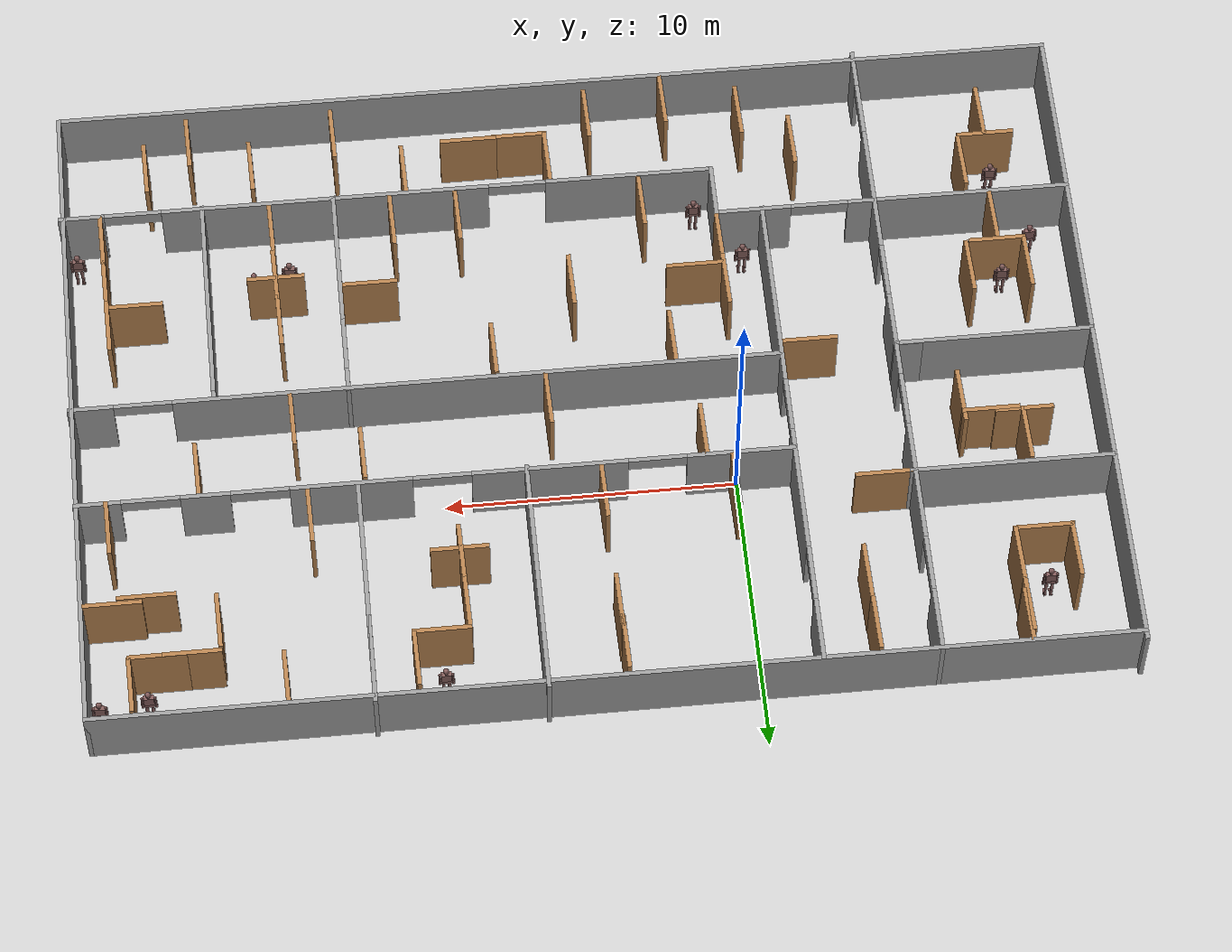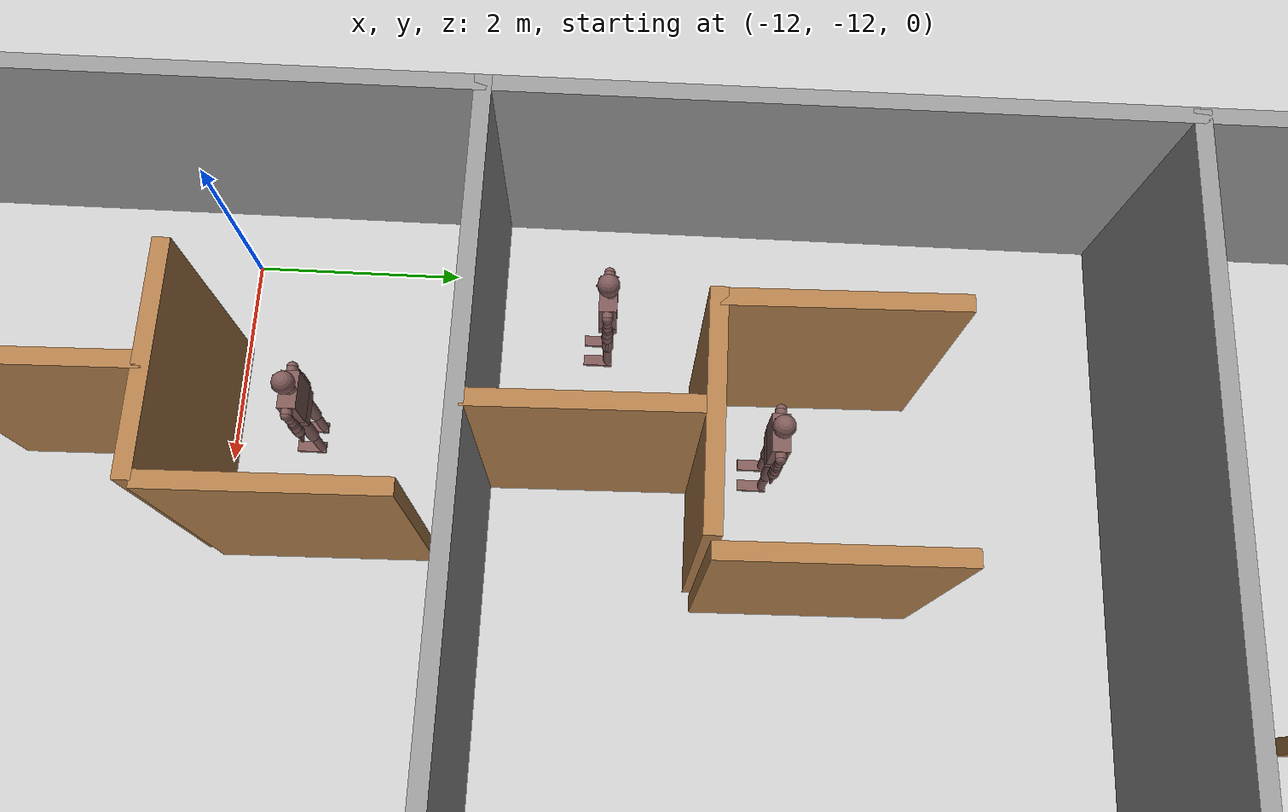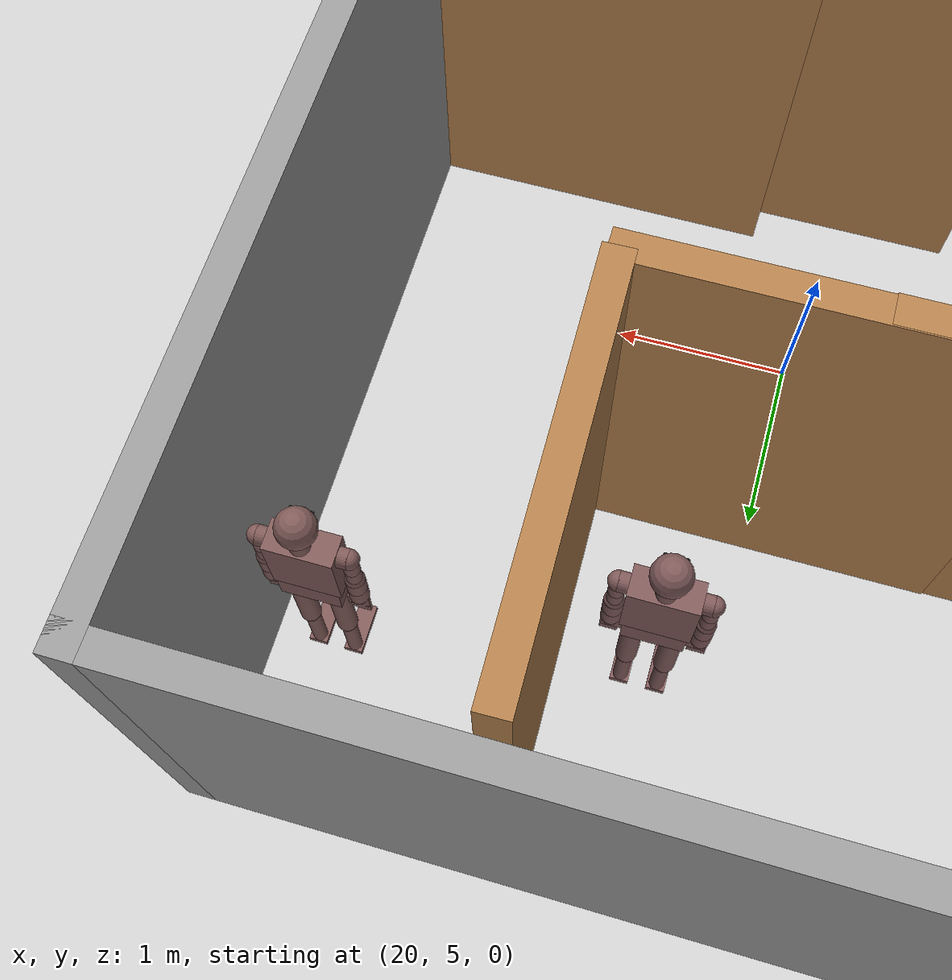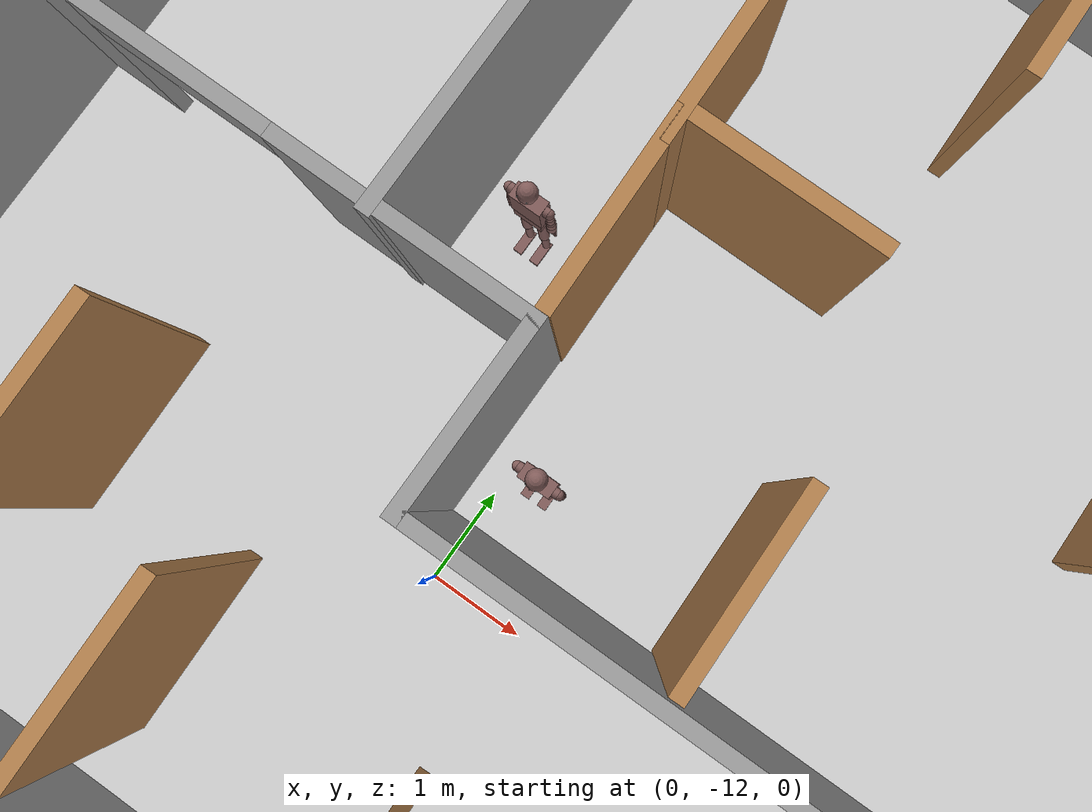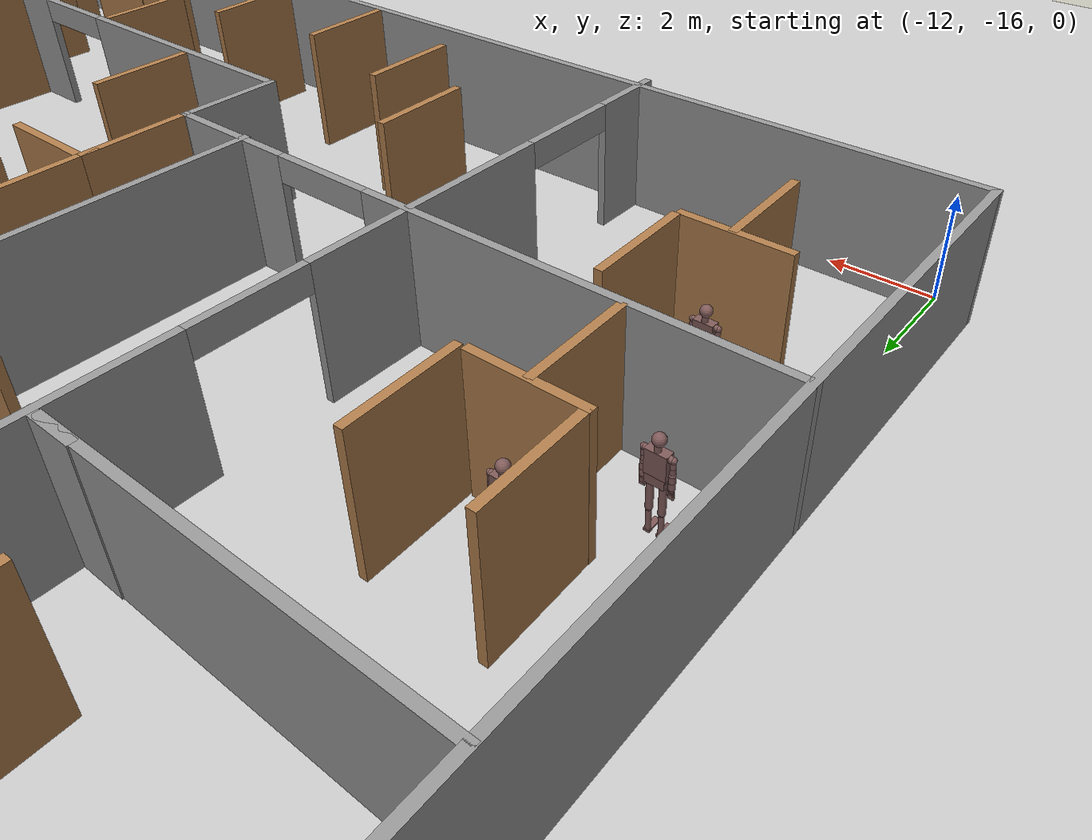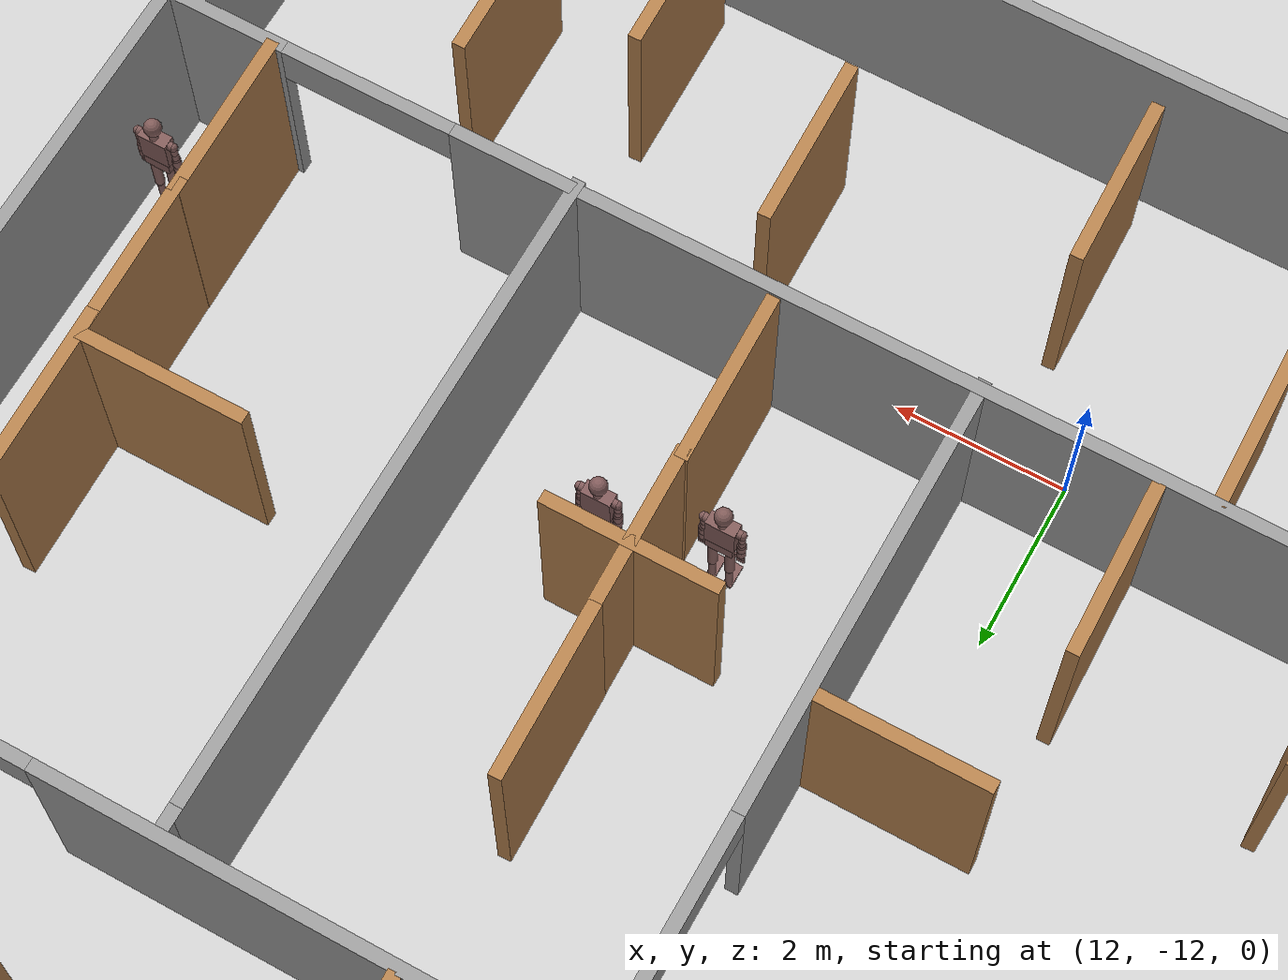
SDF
<sdf version="1.6">
 <world name="default">
  <light name="sun" type="directional">
   <pose>0 0 10 0 -0 0</pose>
   <diffuse>0.8 0.8 0.8 1</diffuse>
   <specular>0.1 0.1 0.1 1</specular>
   <attenuation>
    <range>1000</range>
    <constant>0.9</constant>
    <linear>0.01</linear>
    <quadratic>0.001</quadratic>
   </attenuation>
   <direction>-0.5 0.5 -1</direction>
  </light>
  <model name="ground_plane">
   <static>1</static>
   <link name="link">
    <collision name="collision">
     <geometry><plane><normal>0 0 1</normal><size>100 100</size></plane></geometry>
     <surface><friction><ode><mu>100</mu><mu2>50</mu2></ode></friction></surface>
    </collision>
    <visual name="visual">
     <cast_shadows>0</cast_shadows>
     <geometry><plane><normal>0 0 1</normal><size>100 100</size></plane></geometry>
     <material>
      <script><uri>file://media/materials/scripts/gazebo.material</uri><name>Gazebo/Grey</name></script>
     </material>
    </visual>
   </link>
  </model>
  <gravity>0 0 -9.8</gravity>
  <magnetic_field>6e-06 2.3e-05 -4.2e-05</magnetic_field>
  <atmosphere type="adiabatic"/>
  <physics name="default_physics" default="0" type="ode">
   <max_step_size>0.001</max_step_size>
   <real_time_factor>1</real_time_factor>
   <real_time_update_rate>1000</real_time_update_rate>
  </physics>
  <scene><ambient>0.4 0.4 0.4 1</ambient><background>0.7 0.7 0.7 1</background><shadows>1</shadows></scene>
  <spherical_coordinates>
   <surface_model>EARTH_WGS84</surface_model>
   <latitude_deg>0</latitude_deg>
   <longitude_deg>0</longitude_deg>
   <elevation>0</elevation>
   <heading_deg>0</heading_deg>
  </spherical_coordinates>
  <model name="rbcp_final4">
   <link name="Wall_46">
    <pose>-0.05 11.925 2.5 0 -0 0</pose>
    <visual name="Wall_46_Visual">
     <pose>0 0 1.25 0 -0 0</pose>
     <geometry><box><size>35.25 0.15 2.5</size></box></geometry>
     <material>
      <script><uri>file://media/materials/scripts/gazebo.material</uri><name>Gazebo/Grey</name></script>
      <ambient>1 1 1 1</ambient>
      <diffuse>0.7 0.7 0.7 1</diffuse>
      <specular>0.01 0.01 0.01 1</specular>
      <emissive>0 0 0 1</emissive>
     </material>
    </visual>
    <collision name="Wall_46_Collision">
     <pose>0 0 1.25 0 -0 0</pose>
     <geometry><box><size>35.25 0.15 2.5</size></box></geometry>
     <surface>
      <friction>
       <ode><mu>1</mu><mu2>1</mu2><fdir1>0 0 0</fdir1><slip1>0</slip1><slip2>0</slip2></ode>
       <torsional>
        <coefficient>1</coefficient>
        <patch_radius>0</patch_radius>
        <surface_radius>0</surface_radius>
        <use_patch_radius>1</use_patch_radius>
        <ode><slip>0</slip></ode>
       </torsional>
      </friction>
      <bounce><restitution_coefficient>0</restitution_coefficient><threshold>1e+06</threshold></bounce>
      <contact>
       <collide_without_contact>0</collide_without_contact>
       <collide_without_contact_bitmask>1</collide_without_contact_bitmask>
       <collide_bitmask>1</collide_bitmask>
       <ode>
        <soft_cfm>0</soft_cfm>
        <soft_erp>0.2</soft_erp>
        <kp>1e+13</kp>
        <kd>1</kd>
        <max_vel>0.01</max_vel>
        <min_depth>0</min_depth>
       </ode>
       <bullet>
        <split_impulse>1</split_impulse>
        <split_impulse_penetration_threshold>-0.01</split_impulse_penetration_threshold>
        <soft_cfm>0</soft_cfm>
        <soft_erp>0.2</soft_erp>
        <kp>1e+13</kp>
        <kd>1</kd>
       </bullet>
      </contact>
     </surface>
    </collision>
   </link>
   <link name="Wall_47">
    <pose>17.5 0 2.5 0 0 -1.5708</pose>
    <visual name="Wall_47_Visual">
     <pose>0 0 1.25 0 -0 0</pose>
     <geometry><box><size>24 0.15 2.5</size></box></geometry>
     <material>
      <script><uri>file://media/materials/scripts/gazebo.material</uri><name>Gazebo/Grey</name></script>
      <ambient>1 1 1 1</ambient>
      <diffuse>0.7 0.7 0.7 1</diffuse>
      <specular>0.01 0.01 0.01 1</specular>
      <emissive>0 0 0 1</emissive>
     </material>
    </visual>
    <collision name="Wall_47_Collision">
     <pose>0 0 1.25 0 -0 0</pose>
     <geometry><box><size>24 0.15 2.5</size></box></geometry>
     <surface>
      <friction>
       <ode><mu>1</mu><mu2>1</mu2><fdir1>0 0 0</fdir1><slip1>0</slip1><slip2>0</slip2></ode>
       <torsional>
        <coefficient>1</coefficient>
        <patch_radius>0</patch_radius>
        <surface_radius>0</surface_radius>
        <use_patch_radius>1</use_patch_radius>
        <ode><slip>0</slip></ode>
       </torsional>
      </friction>
      <bounce><restitution_coefficient>0</restitution_coefficient><threshold>1e+06</threshold></bounce>
      <contact>
       <collide_without_contact>0</collide_without_contact>
       <collide_without_contact_bitmask>1</collide_without_contact_bitmask>
       <collide_bitmask>1</collide_bitmask>
       <ode>
        <soft_cfm>0</soft_cfm>
        <soft_erp>0.2</soft_erp>
        <kp>1e+13</kp>
        <kd>1</kd>
        <max_vel>0.01</max_vel>
        <min_depth>0</min_depth>
       </ode>
       <bullet>
        <split_impulse>1</split_impulse>
        <split_impulse_penetration_threshold>-0.01</split_impulse_penetration_threshold>
        <soft_cfm>0</soft_cfm>
        <soft_erp>0.2</soft_erp>
        <kp>1e+13</kp>
        <kd>1</kd>
       </bullet>
      </contact>
     </surface>
    </collision>
   </link>
   <link name="Wall_48">
    <pose>-0.05 -11.925 2.5 0 -0 3.14159</pose>
    <visual name="Wall_48_Visual">
     <pose>0 0 1.25 0 -0 0</pose>
     <geometry><box><size>35.25 0.15 2.5</size></box></geometry>
     <material>
      <script><uri>file://media/materials/scripts/gazebo.material</uri><name>Gazebo/Grey</name></script>
      <ambient>1 1 1 1</ambient>
      <diffuse>0.7 0.7 0.7 1</diffuse>
      <specular>0.01 0.01 0.01 1</specular>
      <emissive>0 0 0 1</emissive>
     </material>
    </visual>
    <collision name="Wall_48_Collision">
     <pose>0 0 1.25 0 -0 0</pose>
     <geometry><box><size>35.25 0.15 2.5</size></box></geometry>
     <surface>
      <friction>
       <ode><mu>1</mu><mu2>1</mu2><fdir1>0 0 0</fdir1><slip1>0</slip1><slip2>0</slip2></ode>
       <torsional>
        <coefficient>1</coefficient>
        <patch_radius>0</patch_radius>
        <surface_radius>0</surface_radius>
        <use_patch_radius>1</use_patch_radius>
        <ode><slip>0</slip></ode>
       </torsional>
      </friction>
      <bounce><restitution_coefficient>0</restitution_coefficient><threshold>1e+06</threshold></bounce>
      <contact>
       <collide_without_contact>0</collide_without_contact>
       <collide_without_contact_bitmask>1</collide_without_contact_bitmask>
       <collide_bitmask>1</collide_bitmask>
       <ode>
        <soft_cfm>0</soft_cfm>
        <soft_erp>0.2</soft_erp>
        <kp>1e+13</kp>
        <kd>1</kd>
        <max_vel>0.01</max_vel>
        <min_depth>0</min_depth>
       </ode>
       <bullet>
        <split_impulse>1</split_impulse>
        <split_impulse_penetration_threshold>-0.01</split_impulse_penetration_threshold>
        <soft_cfm>0</soft_cfm>
        <soft_erp>0.2</soft_erp>
        <kp>1e+13</kp>
        <kd>1</kd>
       </bullet>
      </contact>
     </surface>
    </collision>
   </link>
   <link name="Wall_49">
    <pose>-17.6 0.125 2.5 0 -0 1.5708</pose>
    <visual name="Wall_49_Visual">
     <pose>0 0 1.25 0 -0 0</pose>
     <geometry><box><size>24.25 0.15 2.5</size></box></geometry>
     <material>
      <script><uri>file://media/materials/scripts/gazebo.material</uri><name>Gazebo/Grey</name></script>
      <ambient>1 1 1 1</ambient>
      <diffuse>0.7 0.7 0.7 1</diffuse>
      <specular>0.01 0.01 0.01 1</specular>
      <emissive>0 0 0 1</emissive>
     </material>
    </visual>
    <collision name="Wall_49_Collision">
     <pose>0 0 1.25 0 -0 0</pose>
     <geometry><box><size>24.25 0.15 2.5</size></box></geometry>
     <surface>
      <friction>
       <ode><mu>1</mu><mu2>1</mu2><fdir1>0 0 0</fdir1><slip1>0</slip1><slip2>0</slip2></ode>
       <torsional>
        <coefficient>1</coefficient>
        <patch_radius>0</patch_radius>
        <surface_radius>0</surface_radius>
        <use_patch_radius>1</use_patch_radius>
        <ode><slip>0</slip></ode>
       </torsional>
      </friction>
      <bounce><restitution_coefficient>0</restitution_coefficient><threshold>1e+06</threshold></bounce>
      <contact>
       <collide_without_contact>0</collide_without_contact>
       <collide_without_contact_bitmask>1</collide_without_contact_bitmask>
       <collide_bitmask>1</collide_bitmask>
       <ode>
        <soft_cfm>0</soft_cfm>
        <soft_erp>0.2</soft_erp>
        <kp>1e+13</kp>
        <kd>1</kd>
        <max_vel>0.01</max_vel>
        <min_depth>0</min_depth>
       </ode>
       <bullet>
        <split_impulse>1</split_impulse>
        <split_impulse_penetration_threshold>-0.01</split_impulse_penetration_threshold>
        <soft_cfm>0</soft_cfm>
        <soft_erp>0.2</soft_erp>
        <kp>1e+13</kp>
        <kd>1</kd>
       </bullet>
      </contact>
     </surface>
    </collision>
   </link>
   <link name="Wall_50">
    <pose>-10.8073 -0.125 2.5 0 0 -1.5708</pose>
    <visual name="Wall_50_Visual_0">
     <pose>-10.9762 0 1.25 0 -0 0</pose>
     <geometry><box><size>2.29763 0.15 2.5</size></box></geometry>
     <material>
      <script><uri>file://media/materials/scripts/gazebo.material</uri><name>Gazebo/Grey</name></script>
      <ambient>1 1 1 1</ambient>
      <diffuse>0.7 0.7 0.7 1</diffuse>
      <specular>0.01 0.01 0.01 1</specular>
      <emissive>0 0 0 1</emissive>
     </material>
    </visual>
    <visual name="Wall_50_Visual_1">
     <pose>-5.61109 0 1.25 0 -0 0</pose>
     <geometry><box><size>4.43257 0.15 2.5</size></box></geometry>
     <material>
      <script><uri>file://media/materials/scripts/gazebo.material</uri><name>Gazebo/Grey</name></script>
      <ambient>1 1 1 1</ambient>
      <diffuse>0.7 0.7 0.7 1</diffuse>
      <specular>0.01 0.01 0.01 1</specular>
      <emissive>0 0 0 1</emissive>
     </material>
    </visual>
    <visual name="Wall_50_Visual_2">
     <pose>0.229304 0 1.25 0 -0 0</pose>
     <geometry><box><size>3.24822 0.15 2.5</size></box></geometry>
     <material>
      <script><uri>file://media/materials/scripts/gazebo.material</uri><name>Gazebo/Grey</name></script>
      <ambient>1 1 1 1</ambient>
      <diffuse>0.7 0.7 0.7 1</diffuse>
      <specular>0.01 0.01 0.01 1</specular>
      <emissive>0 0 0 1</emissive>
     </material>
    </visual>
    <visual name="Wall_50_Visual_4">
     <pose>11.3986 0 1.25 0 -0 0</pose>
     <geometry><box><size>1.45284 0.15 2.5</size></box></geometry>
     <material>
      <script><uri>file://media/materials/scripts/gazebo.material</uri><name>Gazebo/Grey</name></script>
      <ambient>1 1 1 1</ambient>
      <diffuse>0.7 0.7 0.7 1</diffuse>
      <specular>0.01 0.01 0.01 1</specular>
      <emissive>0 0 0 1</emissive>
     </material>
    </visual>
    <visual name="Wall_50_Visual_3">
     <pose>6.26279 0 1.25 0 -0 0</pose>
     <geometry><box><size>4.81874 0.15 2.5</size></box></geometry>
     <material>
      <script><uri>file://media/materials/scripts/gazebo.material</uri><name>Gazebo/Grey</name></script>
      <ambient>1 1 1 1</ambient>
      <diffuse>0.7 0.7 0.7 1</diffuse>
      <specular>0.01 0.01 0.01 1</specular>
      <emissive>0 0 0 1</emissive>
     </material>
    </visual>
    <visual name="Wall_50_Visual_5">
     <pose>-8.82737 0 2.25 0 -0 0</pose>
     <geometry><box><size>2 0.15 0.5</size></box></geometry>
     <material>
      <script><uri>file://media/materials/scripts/gazebo.material</uri><name>Gazebo/Grey</name></script>
      <ambient>1 1 1 1</ambient>
      <diffuse>0.7 0.7 0.7 1</diffuse>
      <specular>0.01 0.01 0.01 1</specular>
      <emissive>0 0 0 1</emissive>
     </material>
    </visual>
    <visual name="Wall_50_Visual_6">
     <pose>-2.39481 0 2.25 0 -0 0</pose>
     <geometry><box><size>2 0.15 0.5</size></box></geometry>
     <material>
      <script><uri>file://media/materials/scripts/gazebo.material</uri><name>Gazebo/Grey</name></script>
      <ambient>1 1 1 1</ambient>
      <diffuse>0.7 0.7 0.7 1</diffuse>
      <specular>0.01 0.01 0.01 1</specular>
      <emissive>0 0 0 1</emissive>
     </material>
    </visual>
    <visual name="Wall_50_Visual_7">
     <pose>2.85341 0 2.25 0 -0 0</pose>
     <geometry><box><size>2 0.15 0.5</size></box></geometry>
     <material>
      <script><uri>file://media/materials/scripts/gazebo.material</uri><name>Gazebo/Grey</name></script>
      <ambient>1 1 1 1</ambient>
      <diffuse>0.7 0.7 0.7 1</diffuse>
      <specular>0.01 0.01 0.01 1</specular>
      <emissive>0 0 0 1</emissive>
     </material>
    </visual>
    <visual name="Wall_50_Visual_8">
     <pose>9.67216 0 2.25 0 -0 0</pose>
     <geometry><box><size>2 0.15 0.5</size></box></geometry>
     <material>
      <script><uri>file://media/materials/scripts/gazebo.material</uri><name>Gazebo/Grey</name></script>
      <ambient>1 1 1 1</ambient>
      <diffuse>0.7 0.7 0.7 1</diffuse>
      <specular>0.01 0.01 0.01 1</specular>
      <emissive>0 0 0 1</emissive>
     </material>
    </visual>
    <collision name="Wall_50_Collision_0">
     <pose>-10.9762 0 1.25 0 -0 0</pose>
     <geometry><box><size>2.29763 0.15 2.5</size></box></geometry>
     <surface>
      <friction>
       <ode><mu>1</mu><mu2>1</mu2><fdir1>0 0 0</fdir1><slip1>0</slip1><slip2>0</slip2></ode>
       <torsional>
        <coefficient>1</coefficient>
        <patch_radius>0</patch_radius>
        <surface_radius>0</surface_radius>
        <use_patch_radius>1</use_patch_radius>
        <ode><slip>0</slip></ode>
       </torsional>
      </friction>
      <bounce><restitution_coefficient>0</restitution_coefficient><threshold>1e+06</threshold></bounce>
      <contact>
       <collide_without_contact>0</collide_without_contact>
       <collide_without_contact_bitmask>1</collide_without_contact_bitmask>
       <collide_bitmask>1</collide_bitmask>
       <ode>
        <soft_cfm>0</soft_cfm>
        <soft_erp>0.2</soft_erp>
        <kp>1e+13</kp>
        <kd>1</kd>
        <max_vel>0.01</max_vel>
        <min_depth>0</min_depth>
       </ode>
       <bullet>
        <split_impulse>1</split_impulse>
        <split_impulse_penetration_threshold>-0.01</split_impulse_penetration_threshold>
        <soft_cfm>0</soft_cfm>
        <soft_erp>0.2</soft_erp>
        <kp>1e+13</kp>
        <kd>1</kd>
       </bullet>
      </contact>
     </surface>
    </collision>
    <collision name="Wall_50_Collision_1">
     <pose>-5.61109 0 1.25 0 -0 0</pose>
     <geometry><box><size>4.43257 0.15 2.5</size></box></geometry>
     <surface>
      <friction>
       <ode><mu>1</mu><mu2>1</mu2><fdir1>0 0 0</fdir1><slip1>0</slip1><slip2>0</slip2></ode>
       <torsional>
        <coefficient>1</coefficient>
        <patch_radius>0</patch_radius>
        <surface_radius>0</surface_radius>
        <use_patch_radius>1</use_patch_radius>
        <ode><slip>0</slip></ode>
       </torsional>
      </friction>
      <bounce><restitution_coefficient>0</restitution_coefficient><threshold>1e+06</threshold></bounce>
      <contact>
       <collide_without_contact>0</collide_without_contact>
       <collide_without_contact_bitmask>1</collide_without_contact_bitmask>
       <collide_bitmask>1</collide_bitmask>
       <ode>
        <soft_cfm>0</soft_cfm>
        <soft_erp>0.2</soft_erp>
        <kp>1e+13</kp>
        <kd>1</kd>
        <max_vel>0.01</max_vel>
        <min_depth>0</min_depth>
       </ode>
       <bullet>
        <split_impulse>1</split_impulse>
        <split_impulse_penetration_threshold>-0.01</split_impulse_penetration_threshold>
        <soft_cfm>0</soft_cfm>
        <soft_erp>0.2</soft_erp>
        <kp>1e+13</kp>
        <kd>1</kd>
       </bullet>
      </contact>
     </surface>
    </collision>
    <collision name="Wall_50_Collision_2">
     <pose>0.229304 0 1.25 0 -0 0</pose>
     <geometry><box><size>3.24822 0.15 2.5</size></box></geometry>
     <surface>
      <friction>
       <ode><mu>1</mu><mu2>1</mu2><fdir1>0 0 0</fdir1><slip1>0</slip1><slip2>0</slip2></ode>
       <torsional>
        <coefficient>1</coefficient>
        <patch_radius>0</patch_radius>
        <surface_radius>0</surface_radius>
        <use_patch_radius>1</use_patch_radius>
        <ode><slip>0</slip></ode>
       </torsional>
      </friction>
      <bounce><restitution_coefficient>0</restitution_coefficient><threshold>1e+06</threshold></bounce>
      <contact>
       <collide_without_contact>0</collide_without_contact>
       <collide_without_contact_bitmask>1</collide_without_contact_bitmask>
       <collide_bitmask>1</collide_bitmask>
       <ode>
        <soft_cfm>0</soft_cfm>
        <soft_erp>0.2</soft_erp>
        <kp>1e+13</kp>
        <kd>1</kd>
        <max_vel>0.01</max_vel>
        <min_depth>0</min_depth>
       </ode>
       <bullet>
        <split_impulse>1</split_impulse>
        <split_impulse_penetration_threshold>-0.01</split_impulse_penetration_threshold>
        <soft_cfm>0</soft_cfm>
        <soft_erp>0.2</soft_erp>
        <kp>1e+13</kp>
        <kd>1</kd>
       </bullet>
      </contact>
     </surface>
    </collision>
    <collision name="Wall_50_Collision_3">
     <pose>6.26279 0 1.25 0 -0 0</pose>
     <geometry><box><size>4.81874 0.15 2.5</size></box></geometry>
     <surface>
      <friction>
       <ode><mu>1</mu><mu2>1</mu2><fdir1>0 0 0</fdir1><slip1>0</slip1><slip2>0</slip2></ode>
       <torsional>
        <coefficient>1</coefficient>
        <patch_radius>0</patch_radius>
        <surface_radius>0</surface_radius>
        <use_patch_radius>1</use_patch_radius>
        <ode><slip>0</slip></ode>
       </torsional>
      </friction>
      <bounce><restitution_coefficient>0</restitution_coefficient><threshold>1e+06</threshold></bounce>
      <contact>
       <collide_without_contact>0</collide_without_contact>
       <collide_without_contact_bitmask>1</collide_without_contact_bitmask>
       <collide_bitmask>1</collide_bitmask>
       <ode>
        <soft_cfm>0</soft_cfm>
        <soft_erp>0.2</soft_erp>
        <kp>1e+13</kp>
        <kd>1</kd>
        <max_vel>0.01</max_vel>
        <min_depth>0</min_depth>
       </ode>
       <bullet>
        <split_impulse>1</split_impulse>
        <split_impulse_penetration_threshold>-0.01</split_impulse_penetration_threshold>
        <soft_cfm>0</soft_cfm>
        <soft_erp>0.2</soft_erp>
        <kp>1e+13</kp>
        <kd>1</kd>
       </bullet>
      </contact>
     </surface>
    </collision>
    <collision name="Wall_50_Collision_4">
     <pose>11.3986 0 1.25 0 -0 0</pose>
     <geometry><box><size>1.45284 0.15 2.5</size></box></geometry>
     <surface>
      <friction>
       <ode><mu>1</mu><mu2>1</mu2><fdir1>0 0 0</fdir1><slip1>0</slip1><slip2>0</slip2></ode>
       <torsional>
        <coefficient>1</coefficient>
        <patch_radius>0</patch_radius>
        <surface_radius>0</surface_radius>
        <use_patch_radius>1</use_patch_radius>
        <ode><slip>0</slip></ode>
       </torsional>
      </friction>
      <bounce><restitution_coefficient>0</restitution_coefficient><threshold>1e+06</threshold></bounce>
      <contact>
       <collide_without_contact>0</collide_without_contact>
       <collide_without_contact_bitmask>1</collide_without_contact_bitmask>
       <collide_bitmask>1</collide_bitmask>
       <ode>
        <soft_cfm>0</soft_cfm>
        <soft_erp>0.2</soft_erp>
        <kp>1e+13</kp>
        <kd>1</kd>
        <max_vel>0.01</max_vel>
        <min_depth>0</min_depth>
       </ode>
       <bullet>
        <split_impulse>1</split_impulse>
        <split_impulse_penetration_threshold>-0.01</split_impulse_penetration_threshold>
        <soft_cfm>0</soft_cfm>
        <soft_erp>0.2</soft_erp>
        <kp>1e+13</kp>
        <kd>1</kd>
       </bullet>
      </contact>
     </surface>
    </collision>
    <collision name="Wall_50_Collision_5">
     <pose>-8.82737 0 2.25 0 -0 0</pose>
     <geometry><box><size>2 0.15 0.5</size></box></geometry>
     <surface>
      <friction>
       <ode><mu>1</mu><mu2>1</mu2><fdir1>0 0 0</fdir1><slip1>0</slip1><slip2>0</slip2></ode>
       <torsional>
        <coefficient>1</coefficient>
        <patch_radius>0</patch_radius>
        <surface_radius>0</surface_radius>
        <use_patch_radius>1</use_patch_radius>
        <ode><slip>0</slip></ode>
       </torsional>
      </friction>
      <bounce><restitution_coefficient>0</restitution_coefficient><threshold>1e+06</threshold></bounce>
      <contact>
       <collide_without_contact>0</collide_without_contact>
       <collide_without_contact_bitmask>1</collide_without_contact_bitmask>
       <collide_bitmask>1</collide_bitmask>
       <ode>
        <soft_cfm>0</soft_cfm>
        <soft_erp>0.2</soft_erp>
        <kp>1e+13</kp>
        <kd>1</kd>
        <max_vel>0.01</max_vel>
        <min_depth>0</min_depth>
       </ode>
       <bullet>
        <split_impulse>1</split_impulse>
        <split_impulse_penetration_threshold>-0.01</split_impulse_penetration_threshold>
        <soft_cfm>0</soft_cfm>
        <soft_erp>0.2</soft_erp>
        <kp>1e+13</kp>
        <kd>1</kd>
       </bullet>
      </contact>
     </surface>
    </collision>
    <collision name="Wall_50_Collision_6">
     <pose>-2.39481 0 2.25 0 -0 0</pose>
     <geometry><box><size>2 0.15 0.5</size></box></geometry>
     <surface>
      <friction>
       <ode><mu>1</mu><mu2>1</mu2><fdir1>0 0 0</fdir1><slip1>0</slip1><slip2>0</slip2></ode>
       <torsional>
        <coefficient>1</coefficient>
        <patch_radius>0</patch_radius>
        <surface_radius>0</surface_radius>
        <use_patch_radius>1</use_patch_radius>
        <ode><slip>0</slip></ode>
       </torsional>
      </friction>
      <bounce><restitution_coefficient>0</restitution_coefficient><threshold>1e+06</threshold></bounce>
      <contact>
       <collide_without_contact>0</collide_without_contact>
       <collide_without_contact_bitmask>1</collide_without_contact_bitmask>
       <collide_bitmask>1</collide_bitmask>
       <ode>
        <soft_cfm>0</soft_cfm>
        <soft_erp>0.2</soft_erp>
        <kp>1e+13</kp>
        <kd>1</kd>
        <max_vel>0.01</max_vel>
        <min_depth>0</min_depth>
       </ode>
       <bullet>
        <split_impulse>1</split_impulse>
        <split_impulse_penetration_threshold>-0.01</split_impulse_penetration_threshold>
        <soft_cfm>0</soft_cfm>
        <soft_erp>0.2</soft_erp>
        <kp>1e+13</kp>
        <kd>1</kd>
       </bullet>
      </contact>
     </surface>
    </collision>
    <collision name="Wall_50_Collision_7">
     <pose>2.85341 0 2.25 0 -0 0</pose>
     <geometry><box><size>2 0.15 0.5</size></box></geometry>
     <surface>
      <friction>
       <ode><mu>1</mu><mu2>1</mu2><fdir1>0 0 0</fdir1><slip1>0</slip1><slip2>0</slip2></ode>
       <torsional>
        <coefficient>1</coefficient>
        <patch_radius>0</patch_radius>
        <surface_radius>0</surface_radius>
        <use_patch_radius>1</use_patch_radius>
        <ode><slip>0</slip></ode>
       </torsional>
      </friction>
      <bounce><restitution_coefficient>0</restitution_coefficient><threshold>1e+06</threshold></bounce>
      <contact>
       <collide_without_contact>0</collide_without_contact>
       <collide_without_contact_bitmask>1</collide_without_contact_bitmask>
       <collide_bitmask>1</collide_bitmask>
       <ode>
        <soft_cfm>0</soft_cfm>
        <soft_erp>0.2</soft_erp>
        <kp>1e+13</kp>
        <kd>1</kd>
        <max_vel>0.01</max_vel>
        <min_depth>0</min_depth>
       </ode>
       <bullet>
        <split_impulse>1</split_impulse>
        <split_impulse_penetration_threshold>-0.01</split_impulse_penetration_threshold>
        <soft_cfm>0</soft_cfm>
        <soft_erp>0.2</soft_erp>
        <kp>1e+13</kp>
        <kd>1</kd>
       </bullet>
      </contact>
     </surface>
    </collision>
    <collision name="Wall_50_Collision_8">
     <pose>9.67216 0 2.25 0 -0 0</pose>
     <geometry><box><size>2 0.15 0.5</size></box></geometry>
     <surface>
      <friction>
       <ode><mu>1</mu><mu2>1</mu2><fdir1>0 0 0</fdir1><slip1>0</slip1><slip2>0</slip2></ode>
       <torsional>
        <coefficient>1</coefficient>
        <patch_radius>0</patch_radius>
        <surface_radius>0</surface_radius>
        <use_patch_radius>1</use_patch_radius>
        <ode><slip>0</slip></ode>
       </torsional>
      </friction>
      <bounce><restitution_coefficient>0</restitution_coefficient><threshold>1e+06</threshold></bounce>
      <contact>
       <collide_without_contact>0</collide_without_contact>
       <collide_without_contact_bitmask>1</collide_without_contact_bitmask>
       <collide_bitmask>1</collide_bitmask>
       <ode>
        <soft_cfm>0</soft_cfm>
        <soft_erp>0.2</soft_erp>
        <kp>1e+13</kp>
        <kd>1</kd>
        <max_vel>0.01</max_vel>
        <min_depth>0</min_depth>
       </ode>
       <bullet>
        <split_impulse>1</split_impulse>
        <split_impulse_penetration_threshold>-0.01</split_impulse_penetration_threshold>
        <soft_cfm>0</soft_cfm>
        <soft_erp>0.2</soft_erp>
        <kp>1e+13</kp>
        <kd>1</kd>
       </bullet>
      </contact>
     </surface>
    </collision>
   </link>
   <link name="Wall_51">
    <pose>-11.425 -5.90578 2.5 0 -0 0</pose>
    <visual name="Wall_51_Visual_0">
     <pose>-2.3439 0 1.25 0 -0 0</pose>
     <geometry><box><size>7.81221 0.15 2.5</size></box></geometry>
     <material>
      <script><uri>file://media/materials/scripts/gazebo.material</uri><name>Gazebo/Grey</name></script>
      <ambient>1 1 1 1</ambient>
      <diffuse>0.7 0.7 0.7 1</diffuse>
      <specular>0.01 0.01 0.01 1</specular>
      <emissive>0 0 0 1</emissive>
     </material>
    </visual>
    <visual name="Wall_51_Visual_1">
     <pose>4.9061 0 1.25 0 -0 0</pose>
     <geometry><box><size>2.68779 0.15 2.5</size></box></geometry>
     <material>
      <script><uri>file://media/materials/scripts/gazebo.material</uri><name>Gazebo/Grey</name></script>
      <ambient>1 1 1 1</ambient>
      <diffuse>0.7 0.7 0.7 1</diffuse>
      <specular>0.01 0.01 0.01 1</specular>
      <emissive>0 0 0 1</emissive>
     </material>
    </visual>
    <visual name="Wall_51_Visual_2">
     <pose>2.56221 0 2.25 0 -0 0</pose>
     <geometry><box><size>2 0.15 0.5</size></box></geometry>
     <material>
      <script><uri>file://media/materials/scripts/gazebo.material</uri><name>Gazebo/Grey</name></script>
      <ambient>1 1 1 1</ambient>
      <diffuse>0.7 0.7 0.7 1</diffuse>
      <specular>0.01 0.01 0.01 1</specular>
      <emissive>0 0 0 1</emissive>
     </material>
    </visual>
    <collision name="Wall_51_Collision_0">
     <pose>-2.3439 0 1.25 0 -0 0</pose>
     <geometry><box><size>7.81221 0.15 2.5</size></box></geometry>
     <surface>
      <friction>
       <ode><mu>1</mu><mu2>1</mu2><fdir1>0 0 0</fdir1><slip1>0</slip1><slip2>0</slip2></ode>
       <torsional>
        <coefficient>1</coefficient>
        <patch_radius>0</patch_radius>
        <surface_radius>0</surface_radius>
        <use_patch_radius>1</use_patch_radius>
        <ode><slip>0</slip></ode>
       </torsional>
      </friction>
      <bounce><restitution_coefficient>0</restitution_coefficient><threshold>1e+06</threshold></bounce>
      <contact>
       <collide_without_contact>0</collide_without_contact>
       <collide_without_contact_bitmask>1</collide_without_contact_bitmask>
       <collide_bitmask>1</collide_bitmask>
       <ode>
        <soft_cfm>0</soft_cfm>
        <soft_erp>0.2</soft_erp>
        <kp>1e+13</kp>
        <kd>1</kd>
        <max_vel>0.01</max_vel>
        <min_depth>0</min_depth>
       </ode>
       <bullet>
        <split_impulse>1</split_impulse>
        <split_impulse_penetration_threshold>-0.01</split_impulse_penetration_threshold>
        <soft_cfm>0</soft_cfm>
        <soft_erp>0.2</soft_erp>
        <kp>1e+13</kp>
        <kd>1</kd>
       </bullet>
      </contact>
     </surface>
    </collision>
    <collision name="Wall_51_Collision_1">
     <pose>4.9061 0 1.25 0 -0 0</pose>
     <geometry><box><size>2.68779 0.15 2.5</size></box></geometry>
     <surface>
      <friction>
       <ode><mu>1</mu><mu2>1</mu2><fdir1>0 0 0</fdir1><slip1>0</slip1><slip2>0</slip2></ode>
       <torsional>
        <coefficient>1</coefficient>
        <patch_radius>0</patch_radius>
        <surface_radius>0</surface_radius>
        <use_patch_radius>1</use_patch_radius>
        <ode><slip>0</slip></ode>
       </torsional>
      </friction>
      <bounce><restitution_coefficient>0</restitution_coefficient><threshold>1e+06</threshold></bounce>
      <contact>
       <collide_without_contact>0</collide_without_contact>
       <collide_without_contact_bitmask>1</collide_without_contact_bitmask>
       <collide_bitmask>1</collide_bitmask>
       <ode>
        <soft_cfm>0</soft_cfm>
        <soft_erp>0.2</soft_erp>
        <kp>1e+13</kp>
        <kd>1</kd>
        <max_vel>0.01</max_vel>
        <min_depth>0</min_depth>
       </ode>
       <bullet>
        <split_impulse>1</split_impulse>
        <split_impulse_penetration_threshold>-0.01</split_impulse_penetration_threshold>
        <soft_cfm>0</soft_cfm>
        <soft_erp>0.2</soft_erp>
        <kp>1e+13</kp>
        <kd>1</kd>
       </bullet>
      </contact>
     </surface>
    </collision>
    <collision name="Wall_51_Collision_2">
     <pose>2.56221 0 2.25 0 -0 0</pose>
     <geometry><box><size>2 0.15 0.5</size></box></geometry>
     <surface>
      <friction>
       <ode><mu>1</mu><mu2>1</mu2><fdir1>0 0 0</fdir1><slip1>0</slip1><slip2>0</slip2></ode>
       <torsional>
        <coefficient>1</coefficient>
        <patch_radius>0</patch_radius>
        <surface_radius>0</surface_radius>
        <use_patch_radius>1</use_patch_radius>
        <ode><slip>0</slip></ode>
       </torsional>
      </friction>
      <bounce><restitution_coefficient>0</restitution_coefficient><threshold>1e+06</threshold></bounce>
      <contact>
       <collide_without_contact>0</collide_without_contact>
       <collide_without_contact_bitmask>1</collide_without_contact_bitmask>
       <collide_bitmask>1</collide_bitmask>
       <ode>
        <soft_cfm>0</soft_cfm>
        <soft_erp>0.2</soft_erp>
        <kp>1e+13</kp>
        <kd>1</kd>
        <max_vel>0.01</max_vel>
        <min_depth>0</min_depth>
       </ode>
       <bullet>
        <split_impulse>1</split_impulse>
        <split_impulse_penetration_threshold>-0.01</split_impulse_penetration_threshold>
        <soft_cfm>0</soft_cfm>
        <soft_erp>0.2</soft_erp>
        <kp>1e+13</kp>
        <kd>1</kd>
       </bullet>
      </contact>
     </surface>
    </collision>
   </link>
   <link name="Wall_52">
    <pose>-5.25 -6.83078 2.5 0 0 -1.5708</pose>
    <visual name="Wall_52_Visual">
     <pose>0 0 1.25 0 -0 0</pose>
     <geometry><box><size>2 0.15 2.5</size></box></geometry>
     <material>
      <script><uri>file://media/materials/scripts/gazebo.material</uri><name>Gazebo/Grey</name></script>
      <ambient>1 1 1 1</ambient>
      <diffuse>0.7 0.7 0.7 1</diffuse>
      <specular>0.01 0.01 0.01 1</specular>
      <emissive>0 0 0 1</emissive>
     </material>
    </visual>
    <collision name="Wall_52_Collision">
     <pose>0 0 1.25 0 -0 0</pose>
     <geometry><box><size>2 0.15 2.5</size></box></geometry>
     <surface>
      <friction>
       <ode><mu>1</mu><mu2>1</mu2><fdir1>0 0 0</fdir1><slip1>0</slip1><slip2>0</slip2></ode>
       <torsional>
        <coefficient>1</coefficient>
        <patch_radius>0</patch_radius>
        <surface_radius>0</surface_radius>
        <use_patch_radius>1</use_patch_radius>
        <ode><slip>0</slip></ode>
       </torsional>
      </friction>
      <bounce><restitution_coefficient>0</restitution_coefficient><threshold>1e+06</threshold></bounce>
      <contact>
       <collide_without_contact>0</collide_without_contact>
       <collide_without_contact_bitmask>1</collide_without_contact_bitmask>
       <collide_bitmask>1</collide_bitmask>
       <ode>
        <soft_cfm>0</soft_cfm>
        <soft_erp>0.2</soft_erp>
        <kp>1e+13</kp>
        <kd>1</kd>
        <max_vel>0.01</max_vel>
        <min_depth>0</min_depth>
       </ode>
       <bullet>
        <split_impulse>1</split_impulse>
        <split_impulse_penetration_threshold>-0.01</split_impulse_penetration_threshold>
        <soft_cfm>0</soft_cfm>
        <soft_erp>0.2</soft_erp>
        <kp>1e+13</kp>
        <kd>1</kd>
       </bullet>
      </contact>
     </surface>
    </collision>
   </link>
   <link name="Wall_53">
    <pose>6.175 -7.75578 2.5 0 -0 0</pose>
    <visual name="Wall_53_Visual_0">
     <pose>-8.53919 0 1.25 0 -0 0</pose>
     <geometry><box><size>5.92162 0.15 2.5</size></box></geometry>
     <material>
      <script><uri>file://media/materials/scripts/gazebo.material</uri><name>Gazebo/Grey</name></script>
      <ambient>1 1 1 1</ambient>
      <diffuse>0.7 0.7 0.7 1</diffuse>
      <specular>0.01 0.01 0.01 1</specular>
      <emissive>0 0 0 1</emissive>
     </material>
    </visual>
    <visual name="Wall_53_Visual_1">
     <pose>2.15861 0 1.25 0 -0 0</pose>
     <geometry><box><size>11.474 0.15 2.5</size></box></geometry>
     <material>
      <script><uri>file://media/materials/scripts/gazebo.material</uri><name>Gazebo/Grey</name></script>
      <ambient>1 1 1 1</ambient>
      <diffuse>0.7 0.7 0.7 1</diffuse>
      <specular>0.01 0.01 0.01 1</specular>
      <emissive>0 0 0 1</emissive>
     </material>
    </visual>
    <visual name="Wall_53_Visual_2">
     <pose>10.6978 0 1.25 0 -0 0</pose>
     <geometry><box><size>1.6044 0.15 2.5</size></box></geometry>
     <material>
      <script><uri>file://media/materials/scripts/gazebo.material</uri><name>Gazebo/Grey</name></script>
      <ambient>1 1 1 1</ambient>
      <diffuse>0.7 0.7 0.7 1</diffuse>
      <specular>0.01 0.01 0.01 1</specular>
      <emissive>0 0 0 1</emissive>
     </material>
    </visual>
    <visual name="Wall_53_Visual_3">
     <pose>-4.57838 0 2.25 0 -0 0</pose>
     <geometry><box><size>2 0.15 0.5</size></box></geometry>
     <material>
      <script><uri>file://media/materials/scripts/gazebo.material</uri><name>Gazebo/Grey</name></script>
      <ambient>1 1 1 1</ambient>
      <diffuse>0.7 0.7 0.7 1</diffuse>
      <specular>0.01 0.01 0.01 1</specular>
      <emissive>0 0 0 1</emissive>
     </material>
    </visual>
    <visual name="Wall_53_Visual_4">
     <pose>8.8956 0 2.25 0 -0 0</pose>
     <geometry><box><size>2 0.15 0.5</size></box></geometry>
     <material>
      <script><uri>file://media/materials/scripts/gazebo.material</uri><name>Gazebo/Grey</name></script>
      <ambient>1 1 1 1</ambient>
      <diffuse>0.7 0.7 0.7 1</diffuse>
      <specular>0.01 0.01 0.01 1</specular>
      <emissive>0 0 0 1</emissive>
     </material>
    </visual>
    <collision name="Wall_53_Collision_0">
     <pose>-8.53919 0 1.25 0 -0 0</pose>
     <geometry><box><size>5.92162 0.15 2.5</size></box></geometry>
     <surface>
      <friction>
       <ode><mu>1</mu><mu2>1</mu2><fdir1>0 0 0</fdir1><slip1>0</slip1><slip2>0</slip2></ode>
       <torsional>
        <coefficient>1</coefficient>
        <patch_radius>0</patch_radius>
        <surface_radius>0</surface_radius>
        <use_patch_radius>1</use_patch_radius>
        <ode><slip>0</slip></ode>
       </torsional>
      </friction>
      <bounce><restitution_coefficient>0</restitution_coefficient><threshold>1e+06</threshold></bounce>
      <contact>
       <collide_without_contact>0</collide_without_contact>
       <collide_without_contact_bitmask>1</collide_without_contact_bitmask>
       <collide_bitmask>1</collide_bitmask>
       <ode>
        <soft_cfm>0</soft_cfm>
        <soft_erp>0.2</soft_erp>
        <kp>1e+13</kp>
        <kd>1</kd>
        <max_vel>0.01</max_vel>
        <min_depth>0</min_depth>
       </ode>
       <bullet>
        <split_impulse>1</split_impulse>
        <split_impulse_penetration_threshold>-0.01</split_impulse_penetration_threshold>
        <soft_cfm>0</soft_cfm>
        <soft_erp>0.2</soft_erp>
        <kp>1e+13</kp>
        <kd>1</kd>
       </bullet>
      </contact>
     </surface>
    </collision>
    <collision name="Wall_53_Collision_1">
     <pose>2.15861 0 1.25 0 -0 0</pose>
     <geometry><box><size>11.474 0.15 2.5</size></box></geometry>
     <surface>
      <friction>
       <ode><mu>1</mu><mu2>1</mu2><fdir1>0 0 0</fdir1><slip1>0</slip1><slip2>0</slip2></ode>
       <torsional>
        <coefficient>1</coefficient>
        <patch_radius>0</patch_radius>
        <surface_radius>0</surface_radius>
        <use_patch_radius>1</use_patch_radius>
        <ode><slip>0</slip></ode>
       </torsional>
      </friction>
      <bounce><restitution_coefficient>0</restitution_coefficient><threshold>1e+06</threshold></bounce>
      <contact>
       <collide_without_contact>0</collide_without_contact>
       <collide_without_contact_bitmask>1</collide_without_contact_bitmask>
       <collide_bitmask>1</collide_bitmask>
       <ode>
        <soft_cfm>0</soft_cfm>
        <soft_erp>0.2</soft_erp>
        <kp>1e+13</kp>
        <kd>1</kd>
        <max_vel>0.01</max_vel>
        <min_depth>0</min_depth>
       </ode>
       <bullet>
        <split_impulse>1</split_impulse>
        <split_impulse_penetration_threshold>-0.01</split_impulse_penetration_threshold>
        <soft_cfm>0</soft_cfm>
        <soft_erp>0.2</soft_erp>
        <kp>1e+13</kp>
        <kd>1</kd>
       </bullet>
      </contact>
     </surface>
    </collision>
    <collision name="Wall_53_Collision_2">
     <pose>10.6978 0 1.25 0 -0 0</pose>
     <geometry><box><size>1.6044 0.15 2.5</size></box></geometry>
     <surface>
      <friction>
       <ode><mu>1</mu><mu2>1</mu2><fdir1>0 0 0</fdir1><slip1>0</slip1><slip2>0</slip2></ode>
       <torsional>
        <coefficient>1</coefficient>
        <patch_radius>0</patch_radius>
        <surface_radius>0</surface_radius>
        <use_patch_radius>1</use_patch_radius>
        <ode><slip>0</slip></ode>
       </torsional>
      </friction>
      <bounce><restitution_coefficient>0</restitution_coefficient><threshold>1e+06</threshold></bounce>
      <contact>
       <collide_without_contact>0</collide_without_contact>
       <collide_without_contact_bitmask>1</collide_without_contact_bitmask>
       <collide_bitmask>1</collide_bitmask>
       <ode>
        <soft_cfm>0</soft_cfm>
        <soft_erp>0.2</soft_erp>
        <kp>1e+13</kp>
        <kd>1</kd>
        <max_vel>0.01</max_vel>
        <min_depth>0</min_depth>
       </ode>
       <bullet>
        <split_impulse>1</split_impulse>
        <split_impulse_penetration_threshold>-0.01</split_impulse_penetration_threshold>
        <soft_cfm>0</soft_cfm>
        <soft_erp>0.2</soft_erp>
        <kp>1e+13</kp>
        <kd>1</kd>
       </bullet>
      </contact>
     </surface>
    </collision>
    <collision name="Wall_53_Collision_3">
     <pose>-4.57838 0 2.25 0 -0 0</pose>
     <geometry><box><size>2 0.15 0.5</size></box></geometry>
     <surface>
      <friction>
       <ode><mu>1</mu><mu2>1</mu2><fdir1>0 0 0</fdir1><slip1>0</slip1><slip2>0</slip2></ode>
       <torsional>
        <coefficient>1</coefficient>
        <patch_radius>0</patch_radius>
        <surface_radius>0</surface_radius>
        <use_patch_radius>1</use_patch_radius>
        <ode><slip>0</slip></ode>
       </torsional>
      </friction>
      <bounce><restitution_coefficient>0</restitution_coefficient><threshold>1e+06</threshold></bounce>
      <contact>
       <collide_without_contact>0</collide_without_contact>
       <collide_without_contact_bitmask>1</collide_without_contact_bitmask>
       <collide_bitmask>1</collide_bitmask>
       <ode>
        <soft_cfm>0</soft_cfm>
        <soft_erp>0.2</soft_erp>
        <kp>1e+13</kp>
        <kd>1</kd>
        <max_vel>0.01</max_vel>
        <min_depth>0</min_depth>
       </ode>
       <bullet>
        <split_impulse>1</split_impulse>
        <split_impulse_penetration_threshold>-0.01</split_impulse_penetration_threshold>
        <soft_cfm>0</soft_cfm>
        <soft_erp>0.2</soft_erp>
        <kp>1e+13</kp>
        <kd>1</kd>
       </bullet>
      </contact>
     </surface>
    </collision>
    <collision name="Wall_53_Collision_4">
     <pose>8.8956 0 2.25 0 -0 0</pose>
     <geometry><box><size>2 0.15 0.5</size></box></geometry>
     <surface>
      <friction>
       <ode><mu>1</mu><mu2>1</mu2><fdir1>0 0 0</fdir1><slip1>0</slip1><slip2>0</slip2></ode>
       <torsional>
        <coefficient>1</coefficient>
        <patch_radius>0</patch_radius>
        <surface_radius>0</surface_radius>
        <use_patch_radius>1</use_patch_radius>
        <ode><slip>0</slip></ode>
       </torsional>
      </friction>
      <bounce><restitution_coefficient>0</restitution_coefficient><threshold>1e+06</threshold></bounce>
      <contact>
       <collide_without_contact>0</collide_without_contact>
       <collide_without_contact_bitmask>1</collide_without_contact_bitmask>
       <collide_bitmask>1</collide_bitmask>
       <ode>
        <soft_cfm>0</soft_cfm>
        <soft_erp>0.2</soft_erp>
        <kp>1e+13</kp>
        <kd>1</kd>
        <max_vel>0.01</max_vel>
        <min_depth>0</min_depth>
       </ode>
       <bullet>
        <split_impulse>1</split_impulse>
        <split_impulse_penetration_threshold>-0.01</split_impulse_penetration_threshold>
        <soft_cfm>0</soft_cfm>
        <soft_erp>0.2</soft_erp>
        <kp>1e+13</kp>
        <kd>1</kd>
       </bullet>
      </contact>
     </surface>
    </collision>
   </link>
   <link name="Wall_54">
    <pose>-14.284 0.027922 2.5 0 -0 0</pose>
    <visual name="Wall_54_Visual">
     <pose>0 0 1.25 0 -0 0</pose>
     <geometry><box><size>6.75 0.15 2.5</size></box></geometry>
     <material>
      <script><uri>file://media/materials/scripts/gazebo.material</uri><name>Gazebo/Grey</name></script>
      <ambient>1 1 1 1</ambient>
      <diffuse>0.7 0.7 0.7 1</diffuse>
      <specular>0.01 0.01 0.01 1</specular>
      <emissive>0 0 0 1</emissive>
     </material>
    </visual>
    <collision name="Wall_54_Collision">
     <pose>0 0 1.25 0 -0 0</pose>
     <geometry><box><size>6.75 0.15 2.5</size></box></geometry>
     <surface>
      <friction>
       <ode><mu>1</mu><mu2>1</mu2><fdir1>0 0 0</fdir1><slip1>0</slip1><slip2>0</slip2></ode>
       <torsional>
        <coefficient>1</coefficient>
        <patch_radius>0</patch_radius>
        <surface_radius>0</surface_radius>
        <use_patch_radius>1</use_patch_radius>
        <ode><slip>0</slip></ode>
       </torsional>
      </friction>
      <bounce><restitution_coefficient>0</restitution_coefficient><threshold>1e+06</threshold></bounce>
      <contact>
       <collide_without_contact>0</collide_without_contact>
       <collide_without_contact_bitmask>1</collide_without_contact_bitmask>
       <collide_bitmask>1</collide_bitmask>
       <ode>
        <soft_cfm>0</soft_cfm>
        <soft_erp>0.2</soft_erp>
        <kp>1e+13</kp>
        <kd>1</kd>
        <max_vel>0.01</max_vel>
        <min_depth>0</min_depth>
       </ode>
       <bullet>
        <split_impulse>1</split_impulse>
        <split_impulse_penetration_threshold>-0.01</split_impulse_penetration_threshold>
        <soft_cfm>0</soft_cfm>
        <soft_erp>0.2</soft_erp>
        <kp>1e+13</kp>
        <kd>1</kd>
       </bullet>
      </contact>
     </surface>
    </collision>
   </link>
   <link name="Wall_55">
    <pose>-11.2256 0.046833 2.5 0 -0 0</pose>
    <visual name="Wall_55_Visual">
     <pose>0 0 1.25 0 -0 0</pose>
     <geometry><box><size>1 0.15 2.5</size></box></geometry>
     <material>
      <script><uri>file://media/materials/scripts/gazebo.material</uri><name>Gazebo/Grey</name></script>
      <ambient>1 1 1 1</ambient>
      <diffuse>0.7 0.7 0.7 1</diffuse>
      <specular>0.01 0.01 0.01 1</specular>
      <emissive>0 0 0 1</emissive>
     </material>
    </visual>
    <collision name="Wall_55_Collision">
     <pose>0 0 1.25 0 -0 0</pose>
     <geometry><box><size>1 0.15 2.5</size></box></geometry>
     <surface>
      <friction>
       <ode><mu>1</mu><mu2>1</mu2><fdir1>0 0 0</fdir1><slip1>0</slip1><slip2>0</slip2></ode>
       <torsional>
        <coefficient>1</coefficient>
        <patch_radius>0</patch_radius>
        <surface_radius>0</surface_radius>
        <use_patch_radius>1</use_patch_radius>
        <ode><slip>0</slip></ode>
       </torsional>
      </friction>
      <bounce><restitution_coefficient>0</restitution_coefficient><threshold>1e+06</threshold></bounce>
      <contact>
       <collide_without_contact>0</collide_without_contact>
       <collide_without_contact_bitmask>1</collide_without_contact_bitmask>
       <collide_bitmask>1</collide_bitmask>
       <ode>
        <soft_cfm>0</soft_cfm>
        <soft_erp>0.2</soft_erp>
        <kp>1e+13</kp>
        <kd>1</kd>
        <max_vel>0.01</max_vel>
        <min_depth>0</min_depth>
       </ode>
       <bullet>
        <split_impulse>1</split_impulse>
        <split_impulse_penetration_threshold>-0.01</split_impulse_penetration_threshold>
        <soft_cfm>0</soft_cfm>
        <soft_erp>0.2</soft_erp>
        <kp>1e+13</kp>
        <kd>1</kd>
       </bullet>
      </contact>
     </surface>
    </collision>
   </link>
   <link name="Wall_56">
    <pose>-6.85289 2.98782 2.5 0 -0 1.5708</pose>
    <visual name="Wall_56_Visual_0">
     <pose>-5.44366 0 1.25 0 -0 0</pose>
     <geometry><box><size>7.11269 0.15 2.5</size></box></geometry>
     <material>
      <script><uri>file://media/materials/scripts/gazebo.material</uri><name>Gazebo/Grey</name></script>
      <ambient>1 1 1 1</ambient>
      <diffuse>0.7 0.7 0.7 1</diffuse>
      <specular>0.01 0.01 0.01 1</specular>
      <emissive>0 0 0 1</emissive>
     </material>
    </visual>
    <visual name="Wall_56_Visual_1">
     <pose>2.41362 0 1.25 0 -0 0</pose>
     <geometry><box><size>4.60187 0.15 2.5</size></box></geometry>
     <material>
      <script><uri>file://media/materials/scripts/gazebo.material</uri><name>Gazebo/Grey</name></script>
      <ambient>1 1 1 1</ambient>
      <diffuse>0.7 0.7 0.7 1</diffuse>
      <specular>0.01 0.01 0.01 1</specular>
      <emissive>0 0 0 1</emissive>
     </material>
    </visual>
    <visual name="Wall_56_Visual_2">
     <pose>7.85727 0 1.25 0 -0 0</pose>
     <geometry><box><size>2.28545 0.15 2.5</size></box></geometry>
     <material>
      <script><uri>file://media/materials/scripts/gazebo.material</uri><name>Gazebo/Grey</name></script>
      <ambient>1 1 1 1</ambient>
      <diffuse>0.7 0.7 0.7 1</diffuse>
      <specular>0.01 0.01 0.01 1</specular>
      <emissive>0 0 0 1</emissive>
     </material>
    </visual>
    <visual name="Wall_56_Visual_3">
     <pose>-0.887314 0 2.25 0 -0 0</pose>
     <geometry><box><size>2 0.15 0.5</size></box></geometry>
     <material>
      <script><uri>file://media/materials/scripts/gazebo.material</uri><name>Gazebo/Grey</name></script>
      <ambient>1 1 1 1</ambient>
      <diffuse>0.7 0.7 0.7 1</diffuse>
      <specular>0.01 0.01 0.01 1</specular>
      <emissive>0 0 0 1</emissive>
     </material>
    </visual>
    <visual name="Wall_56_Visual_4">
     <pose>5.71455 0 2.25 0 -0 0</pose>
     <geometry><box><size>2 0.15 0.5</size></box></geometry>
     <material>
      <script><uri>file://media/materials/scripts/gazebo.material</uri><name>Gazebo/Grey</name></script>
      <ambient>1 1 1 1</ambient>
      <diffuse>0.7 0.7 0.7 1</diffuse>
      <specular>0.01 0.01 0.01 1</specular>
      <emissive>0 0 0 1</emissive>
     </material>
    </visual>
    <collision name="Wall_56_Collision_0">
     <pose>-5.44366 0 1.25 0 -0 0</pose>
     <geometry><box><size>7.11269 0.15 2.5</size></box></geometry>
     <surface>
      <friction>
       <ode><mu>1</mu><mu2>1</mu2><fdir1>0 0 0</fdir1><slip1>0</slip1><slip2>0</slip2></ode>
       <torsional>
        <coefficient>1</coefficient>
        <patch_radius>0</patch_radius>
        <surface_radius>0</surface_radius>
        <use_patch_radius>1</use_patch_radius>
        <ode><slip>0</slip></ode>
       </torsional>
      </friction>
      <bounce><restitution_coefficient>0</restitution_coefficient><threshold>1e+06</threshold></bounce>
      <contact>
       <collide_without_contact>0</collide_without_contact>
       <collide_without_contact_bitmask>1</collide_without_contact_bitmask>
       <collide_bitmask>1</collide_bitmask>
       <ode>
        <soft_cfm>0</soft_cfm>
        <soft_erp>0.2</soft_erp>
        <kp>1e+13</kp>
        <kd>1</kd>
        <max_vel>0.01</max_vel>
        <min_depth>0</min_depth>
       </ode>
       <bullet>
        <split_impulse>1</split_impulse>
        <split_impulse_penetration_threshold>-0.01</split_impulse_penetration_threshold>
        <soft_cfm>0</soft_cfm>
        <soft_erp>0.2</soft_erp>
        <kp>1e+13</kp>
        <kd>1</kd>
       </bullet>
      </contact>
     </surface>
    </collision>
    <collision name="Wall_56_Collision_1">
     <pose>2.41362 0 1.25 0 -0 0</pose>
     <geometry><box><size>4.60187 0.15 2.5</size></box></geometry>
     <surface>
      <friction>
       <ode><mu>1</mu><mu2>1</mu2><fdir1>0 0 0</fdir1><slip1>0</slip1><slip2>0</slip2></ode>
       <torsional>
        <coefficient>1</coefficient>
        <patch_radius>0</patch_radius>
        <surface_radius>0</surface_radius>
        <use_patch_radius>1</use_patch_radius>
        <ode><slip>0</slip></ode>
       </torsional>
      </friction>
      <bounce><restitution_coefficient>0</restitution_coefficient><threshold>1e+06</threshold></bounce>
      <contact>
       <collide_without_contact>0</collide_without_contact>
       <collide_without_contact_bitmask>1</collide_without_contact_bitmask>
       <collide_bitmask>1</collide_bitmask>
       <ode>
        <soft_cfm>0</soft_cfm>
        <soft_erp>0.2</soft_erp>
        <kp>1e+13</kp>
        <kd>1</kd>
        <max_vel>0.01</max_vel>
        <min_depth>0</min_depth>
       </ode>
       <bullet>
        <split_impulse>1</split_impulse>
        <split_impulse_penetration_threshold>-0.01</split_impulse_penetration_threshold>
        <soft_cfm>0</soft_cfm>
        <soft_erp>0.2</soft_erp>
        <kp>1e+13</kp>
        <kd>1</kd>
       </bullet>
      </contact>
     </surface>
    </collision>
    <collision name="Wall_56_Collision_2">
     <pose>7.85727 0 1.25 0 -0 0</pose>
     <geometry><box><size>2.28545 0.15 2.5</size></box></geometry>
     <surface>
      <friction>
       <ode><mu>1</mu><mu2>1</mu2><fdir1>0 0 0</fdir1><slip1>0</slip1><slip2>0</slip2></ode>
       <torsional>
        <coefficient>1</coefficient>
        <patch_radius>0</patch_radius>
        <surface_radius>0</surface_radius>
        <use_patch_radius>1</use_patch_radius>
        <ode><slip>0</slip></ode>
       </torsional>
      </friction>
      <bounce><restitution_coefficient>0</restitution_coefficient><threshold>1e+06</threshold></bounce>
      <contact>
       <collide_without_contact>0</collide_without_contact>
       <collide_without_contact_bitmask>1</collide_without_contact_bitmask>
       <collide_bitmask>1</collide_bitmask>
       <ode>
        <soft_cfm>0</soft_cfm>
        <soft_erp>0.2</soft_erp>
        <kp>1e+13</kp>
        <kd>1</kd>
        <max_vel>0.01</max_vel>
        <min_depth>0</min_depth>
       </ode>
       <bullet>
        <split_impulse>1</split_impulse>
        <split_impulse_penetration_threshold>-0.01</split_impulse_penetration_threshold>
        <soft_cfm>0</soft_cfm>
        <soft_erp>0.2</soft_erp>
        <kp>1e+13</kp>
        <kd>1</kd>
       </bullet>
      </contact>
     </surface>
    </collision>
    <collision name="Wall_56_Collision_3">
     <pose>-0.887314 0 2.25 0 -0 0</pose>
     <geometry><box><size>2 0.15 0.5</size></box></geometry>
     <surface>
      <friction>
       <ode><mu>1</mu><mu2>1</mu2><fdir1>0 0 0</fdir1><slip1>0</slip1><slip2>0</slip2></ode>
       <torsional>
        <coefficient>1</coefficient>
        <patch_radius>0</patch_radius>
        <surface_radius>0</surface_radius>
        <use_patch_radius>1</use_patch_radius>
        <ode><slip>0</slip></ode>
       </torsional>
      </friction>
      <bounce><restitution_coefficient>0</restitution_coefficient><threshold>1e+06</threshold></bounce>
      <contact>
       <collide_without_contact>0</collide_without_contact>
       <collide_without_contact_bitmask>1</collide_without_contact_bitmask>
       <collide_bitmask>1</collide_bitmask>
       <ode>
        <soft_cfm>0</soft_cfm>
        <soft_erp>0.2</soft_erp>
        <kp>1e+13</kp>
        <kd>1</kd>
        <max_vel>0.01</max_vel>
        <min_depth>0</min_depth>
       </ode>
       <bullet>
        <split_impulse>1</split_impulse>
        <split_impulse_penetration_threshold>-0.01</split_impulse_penetration_threshold>
        <soft_cfm>0</soft_cfm>
        <soft_erp>0.2</soft_erp>
        <kp>1e+13</kp>
        <kd>1</kd>
       </bullet>
      </contact>
     </surface>
    </collision>
    <collision name="Wall_56_Collision_4">
     <pose>5.71455 0 2.25 0 -0 0</pose>
     <geometry><box><size>2 0.15 0.5</size></box></geometry>
     <surface>
      <friction>
       <ode><mu>1</mu><mu2>1</mu2><fdir1>0 0 0</fdir1><slip1>0</slip1><slip2>0</slip2></ode>
       <torsional>
        <coefficient>1</coefficient>
        <patch_radius>0</patch_radius>
        <surface_radius>0</surface_radius>
        <use_patch_radius>1</use_patch_radius>
        <ode><slip>0</slip></ode>
       </torsional>
      </friction>
      <bounce><restitution_coefficient>0</restitution_coefficient><threshold>1e+06</threshold></bounce>
      <contact>
       <collide_without_contact>0</collide_without_contact>
       <collide_without_contact_bitmask>1</collide_without_contact_bitmask>
       <collide_bitmask>1</collide_bitmask>
       <ode>
        <soft_cfm>0</soft_cfm>
        <soft_erp>0.2</soft_erp>
        <kp>1e+13</kp>
        <kd>1</kd>
        <max_vel>0.01</max_vel>
        <min_depth>0</min_depth>
       </ode>
       <bullet>
        <split_impulse>1</split_impulse>
        <split_impulse_penetration_threshold>-0.01</split_impulse_penetration_threshold>
        <soft_cfm>0</soft_cfm>
        <soft_erp>0.2</soft_erp>
        <kp>1e+13</kp>
        <kd>1</kd>
       </bullet>
      </contact>
     </surface>
    </collision>
   </link>
   <link name="Wall_57">
    <pose>5.40302 0.050249 2.5 0 -0 0</pose>
    <visual name="Wall_57_Visual_0">
     <pose>-1.79121 0 1.25 0 -0 0</pose>
     <geometry><box><size>20.9176 0.15 2.5</size></box></geometry>
     <material>
      <script><uri>file://media/materials/scripts/gazebo.material</uri><name>Gazebo/Grey</name></script>
      <ambient>1 1 1 1</ambient>
      <diffuse>0.7 0.7 0.7 1</diffuse>
      <specular>0.01 0.01 0.01 1</specular>
      <emissive>0 0 0 1</emissive>
     </material>
    </visual>
    <visual name="Wall_57_Visual_1">
     <pose>11.4588 0 1.25 0 -0 0</pose>
     <geometry><box><size>1.58243 0.15 2.5</size></box></geometry>
     <material>
      <script><uri>file://media/materials/scripts/gazebo.material</uri><name>Gazebo/Grey</name></script>
      <ambient>1 1 1 1</ambient>
      <diffuse>0.7 0.7 0.7 1</diffuse>
      <specular>0.01 0.01 0.01 1</specular>
      <emissive>0 0 0 1</emissive>
     </material>
    </visual>
    <visual name="Wall_57_Visual_2">
     <pose>9.66757 0 2.25 0 -0 0</pose>
     <geometry><box><size>2 0.15 0.5</size></box></geometry>
     <material>
      <script><uri>file://media/materials/scripts/gazebo.material</uri><name>Gazebo/Grey</name></script>
      <ambient>1 1 1 1</ambient>
      <diffuse>0.7 0.7 0.7 1</diffuse>
      <specular>0.01 0.01 0.01 1</specular>
      <emissive>0 0 0 1</emissive>
     </material>
    </visual>
    <collision name="Wall_57_Collision_0">
     <pose>-1.79121 0 1.25 0 -0 0</pose>
     <geometry><box><size>20.9176 0.15 2.5</size></box></geometry>
     <surface>
      <friction>
       <ode><mu>1</mu><mu2>1</mu2><fdir1>0 0 0</fdir1><slip1>0</slip1><slip2>0</slip2></ode>
       <torsional>
        <coefficient>1</coefficient>
        <patch_radius>0</patch_radius>
        <surface_radius>0</surface_radius>
        <use_patch_radius>1</use_patch_radius>
        <ode><slip>0</slip></ode>
       </torsional>
      </friction>
      <bounce><restitution_coefficient>0</restitution_coefficient><threshold>1e+06</threshold></bounce>
      <contact>
       <collide_without_contact>0</collide_without_contact>
       <collide_without_contact_bitmask>1</collide_without_contact_bitmask>
       <collide_bitmask>1</collide_bitmask>
       <ode>
        <soft_cfm>0</soft_cfm>
        <soft_erp>0.2</soft_erp>
        <kp>1e+13</kp>
        <kd>1</kd>
        <max_vel>0.01</max_vel>
        <min_depth>0</min_depth>
       </ode>
       <bullet>
        <split_impulse>1</split_impulse>
        <split_impulse_penetration_threshold>-0.01</split_impulse_penetration_threshold>
        <soft_cfm>0</soft_cfm>
        <soft_erp>0.2</soft_erp>
        <kp>1e+13</kp>
        <kd>1</kd>
       </bullet>
      </contact>
     </surface>
    </collision>
    <collision name="Wall_57_Collision_1">
     <pose>11.4588 0 1.25 0 -0 0</pose>
     <geometry><box><size>1.58243 0.15 2.5</size></box></geometry>
     <surface>
      <friction>
       <ode><mu>1</mu><mu2>1</mu2><fdir1>0 0 0</fdir1><slip1>0</slip1><slip2>0</slip2></ode>
       <torsional>
        <coefficient>1</coefficient>
        <patch_radius>0</patch_radius>
        <surface_radius>0</surface_radius>
        <use_patch_radius>1</use_patch_radius>
        <ode><slip>0</slip></ode>
       </torsional>
      </friction>
      <bounce><restitution_coefficient>0</restitution_coefficient><threshold>1e+06</threshold></bounce>
      <contact>
       <collide_without_contact>0</collide_without_contact>
       <collide_without_contact_bitmask>1</collide_without_contact_bitmask>
       <collide_bitmask>1</collide_bitmask>
       <ode>
        <soft_cfm>0</soft_cfm>
        <soft_erp>0.2</soft_erp>
        <kp>1e+13</kp>
        <kd>1</kd>
        <max_vel>0.01</max_vel>
        <min_depth>0</min_depth>
       </ode>
       <bullet>
        <split_impulse>1</split_impulse>
        <split_impulse_penetration_threshold>-0.01</split_impulse_penetration_threshold>
        <soft_cfm>0</soft_cfm>
        <soft_erp>0.2</soft_erp>
        <kp>1e+13</kp>
        <kd>1</kd>
       </bullet>
      </contact>
     </surface>
    </collision>
    <collision name="Wall_57_Collision_2">
     <pose>9.66757 0 2.25 0 -0 0</pose>
     <geometry><box><size>2 0.15 0.5</size></box></geometry>
     <surface>
      <friction>
       <ode><mu>1</mu><mu2>1</mu2><fdir1>0 0 0</fdir1><slip1>0</slip1><slip2>0</slip2></ode>
       <torsional>
        <coefficient>1</coefficient>
        <patch_radius>0</patch_radius>
        <surface_radius>0</surface_radius>
        <use_patch_radius>1</use_patch_radius>
        <ode><slip>0</slip></ode>
       </torsional>
      </friction>
      <bounce><restitution_coefficient>0</restitution_coefficient><threshold>1e+06</threshold></bounce>
      <contact>
       <collide_without_contact>0</collide_without_contact>
       <collide_without_contact_bitmask>1</collide_without_contact_bitmask>
       <collide_bitmask>1</collide_bitmask>
       <ode>
        <soft_cfm>0</soft_cfm>
        <soft_erp>0.2</soft_erp>
        <kp>1e+13</kp>
        <kd>1</kd>
        <max_vel>0.01</max_vel>
        <min_depth>0</min_depth>
       </ode>
       <bullet>
        <split_impulse>1</split_impulse>
        <split_impulse_penetration_threshold>-0.01</split_impulse_penetration_threshold>
        <soft_cfm>0</soft_cfm>
        <soft_erp>0.2</soft_erp>
        <kp>1e+13</kp>
        <kd>1</kd>
       </bullet>
      </contact>
     </surface>
    </collision>
   </link>
   <link name="Wall_58">
    <pose>12.6467 -3.99813 2.5 0 -0 1.5708</pose>
    <visual name="Wall_58_Visual">
     <pose>0 0 1.25 0 -0 0</pose>
     <geometry><box><size>7.75 0.15 2.5</size></box></geometry>
     <material>
      <script><uri>file://media/materials/scripts/gazebo.material</uri><name>Gazebo/Grey</name></script>
      <ambient>1 1 1 1</ambient>
      <diffuse>0.7 0.7 0.7 1</diffuse>
      <specular>0.01 0.01 0.01 1</specular>
      <emissive>0 0 0 1</emissive>
     </material>
    </visual>
    <collision name="Wall_58_Collision">
     <pose>0 0 1.25 0 -0 0</pose>
     <geometry><box><size>7.75 0.15 2.5</size></box></geometry>
     <surface>
      <friction>
       <ode><mu>1</mu><mu2>1</mu2><fdir1>0 0 0</fdir1><slip1>0</slip1><slip2>0</slip2></ode>
       <torsional>
        <coefficient>1</coefficient>
        <patch_radius>0</patch_radius>
        <surface_radius>0</surface_radius>
        <use_patch_radius>1</use_patch_radius>
        <ode><slip>0</slip></ode>
       </torsional>
      </friction>
      <bounce><restitution_coefficient>0</restitution_coefficient><threshold>1e+06</threshold></bounce>
      <contact>
       <collide_without_contact>0</collide_without_contact>
       <collide_without_contact_bitmask>1</collide_without_contact_bitmask>
       <collide_bitmask>1</collide_bitmask>
       <ode>
        <soft_cfm>0</soft_cfm>
        <soft_erp>0.2</soft_erp>
        <kp>1e+13</kp>
        <kd>1</kd>
        <max_vel>0.01</max_vel>
        <min_depth>0</min_depth>
       </ode>
       <bullet>
        <split_impulse>1</split_impulse>
        <split_impulse_penetration_threshold>-0.01</split_impulse_penetration_threshold>
        <soft_cfm>0</soft_cfm>
        <soft_erp>0.2</soft_erp>
        <kp>1e+13</kp>
        <kd>1</kd>
       </bullet>
      </contact>
     </surface>
    </collision>
   </link>
   <link name="Wall_59">
    <pose>12.6467 -0.148133 2.5 0 -0 1.5708</pose>
    <visual name="Wall_59_Visual">
     <pose>0 0 1.25 0 -0 0</pose>
     <geometry><box><size>0.25 0.15 2.5</size></box></geometry>
     <material>
      <script><uri>file://media/materials/scripts/gazebo.material</uri><name>Gazebo/Grey</name></script>
      <ambient>1 1 1 1</ambient>
      <diffuse>0.7 0.7 0.7 1</diffuse>
      <specular>0.01 0.01 0.01 1</specular>
      <emissive>0 0 0 1</emissive>
     </material>
    </visual>
    <collision name="Wall_59_Collision">
     <pose>0 0 1.25 0 -0 0</pose>
     <geometry><box><size>0.25 0.15 2.5</size></box></geometry>
     <surface>
      <friction>
       <ode><mu>1</mu><mu2>1</mu2><fdir1>0 0 0</fdir1><slip1>0</slip1><slip2>0</slip2></ode>
       <torsional>
        <coefficient>1</coefficient>
        <patch_radius>0</patch_radius>
        <surface_radius>0</surface_radius>
        <use_patch_radius>1</use_patch_radius>
        <ode><slip>0</slip></ode>
       </torsional>
      </friction>
      <bounce><restitution_coefficient>0</restitution_coefficient><threshold>1e+06</threshold></bounce>
      <contact>
       <collide_without_contact>0</collide_without_contact>
       <collide_without_contact_bitmask>1</collide_without_contact_bitmask>
       <collide_bitmask>1</collide_bitmask>
       <ode>
        <soft_cfm>0</soft_cfm>
        <soft_erp>0.2</soft_erp>
        <kp>1e+13</kp>
        <kd>1</kd>
        <max_vel>0.01</max_vel>
        <min_depth>0</min_depth>
       </ode>
       <bullet>
        <split_impulse>1</split_impulse>
        <split_impulse_penetration_threshold>-0.01</split_impulse_penetration_threshold>
        <soft_cfm>0</soft_cfm>
        <soft_erp>0.2</soft_erp>
        <kp>1e+13</kp>
        <kd>1</kd>
       </bullet>
      </contact>
     </surface>
    </collision>
   </link>
   <link name="Wall_60">
    <pose>8.05031 -3.85445 2.5 0 0 -1.5708</pose>
    <visual name="Wall_60_Visual_0">
     <pose>-3.55299 0 1.25 0 -0 0</pose>
     <geometry><box><size>0.894022 0.15 2.5</size></box></geometry>
     <material>
      <script><uri>file://media/materials/scripts/gazebo.material</uri><name>Gazebo/Grey</name></script>
      <ambient>1 1 1 1</ambient>
      <diffuse>0.7 0.7 0.7 1</diffuse>
      <specular>0.01 0.01 0.01 1</specular>
      <emissive>0 0 0 1</emissive>
     </material>
    </visual>
    <visual name="Wall_60_Visual_1">
     <pose>1.44701 0 1.25 0 -0 0</pose>
     <geometry><box><size>5.10598 0.15 2.5</size></box></geometry>
     <material>
      <script><uri>file://media/materials/scripts/gazebo.material</uri><name>Gazebo/Grey</name></script>
      <ambient>1 1 1 1</ambient>
      <diffuse>0.7 0.7 0.7 1</diffuse>
      <specular>0.01 0.01 0.01 1</specular>
      <emissive>0 0 0 1</emissive>
     </material>
    </visual>
    <visual name="Wall_60_Visual_2">
     <pose>-2.10598 0 2.25 0 -0 0</pose>
     <geometry><box><size>2 0.15 0.5</size></box></geometry>
     <material>
      <script><uri>file://media/materials/scripts/gazebo.material</uri><name>Gazebo/Grey</name></script>
      <ambient>1 1 1 1</ambient>
      <diffuse>0.7 0.7 0.7 1</diffuse>
      <specular>0.01 0.01 0.01 1</specular>
      <emissive>0 0 0 1</emissive>
     </material>
    </visual>
    <collision name="Wall_60_Collision_0">
     <pose>-3.55299 0 1.25 0 -0 0</pose>
     <geometry><box><size>0.894022 0.15 2.5</size></box></geometry>
     <surface>
      <friction>
       <ode><mu>1</mu><mu2>1</mu2><fdir1>0 0 0</fdir1><slip1>0</slip1><slip2>0</slip2></ode>
       <torsional>
        <coefficient>1</coefficient>
        <patch_radius>0</patch_radius>
        <surface_radius>0</surface_radius>
        <use_patch_radius>1</use_patch_radius>
        <ode><slip>0</slip></ode>
       </torsional>
      </friction>
      <bounce><restitution_coefficient>0</restitution_coefficient><threshold>1e+06</threshold></bounce>
      <contact>
       <collide_without_contact>0</collide_without_contact>
       <collide_without_contact_bitmask>1</collide_without_contact_bitmask>
       <collide_bitmask>1</collide_bitmask>
       <ode>
        <soft_cfm>0</soft_cfm>
        <soft_erp>0.2</soft_erp>
        <kp>1e+13</kp>
        <kd>1</kd>
        <max_vel>0.01</max_vel>
        <min_depth>0</min_depth>
       </ode>
       <bullet>
        <split_impulse>1</split_impulse>
        <split_impulse_penetration_threshold>-0.01</split_impulse_penetration_threshold>
        <soft_cfm>0</soft_cfm>
        <soft_erp>0.2</soft_erp>
        <kp>1e+13</kp>
        <kd>1</kd>
       </bullet>
      </contact>
     </surface>
    </collision>
    <collision name="Wall_60_Collision_1">
     <pose>1.44701 0 1.25 0 -0 0</pose>
     <geometry><box><size>5.10598 0.15 2.5</size></box></geometry>
     <surface>
      <friction>
       <ode><mu>1</mu><mu2>1</mu2><fdir1>0 0 0</fdir1><slip1>0</slip1><slip2>0</slip2></ode>
       <torsional>
        <coefficient>1</coefficient>
        <patch_radius>0</patch_radius>
        <surface_radius>0</surface_radius>
        <use_patch_radius>1</use_patch_radius>
        <ode><slip>0</slip></ode>
       </torsional>
      </friction>
      <bounce><restitution_coefficient>0</restitution_coefficient><threshold>1e+06</threshold></bounce>
      <contact>
       <collide_without_contact>0</collide_without_contact>
       <collide_without_contact_bitmask>1</collide_without_contact_bitmask>
       <collide_bitmask>1</collide_bitmask>
       <ode>
        <soft_cfm>0</soft_cfm>
        <soft_erp>0.2</soft_erp>
        <kp>1e+13</kp>
        <kd>1</kd>
        <max_vel>0.01</max_vel>
        <min_depth>0</min_depth>
       </ode>
       <bullet>
        <split_impulse>1</split_impulse>
        <split_impulse_penetration_threshold>-0.01</split_impulse_penetration_threshold>
        <soft_cfm>0</soft_cfm>
        <soft_erp>0.2</soft_erp>
        <kp>1e+13</kp>
        <kd>1</kd>
       </bullet>
      </contact>
     </surface>
    </collision>
    <collision name="Wall_60_Collision_2">
     <pose>-2.10598 0 2.25 0 -0 0</pose>
     <geometry><box><size>2 0.15 0.5</size></box></geometry>
     <surface>
      <friction>
       <ode><mu>1</mu><mu2>1</mu2><fdir1>0 0 0</fdir1><slip1>0</slip1><slip2>0</slip2></ode>
       <torsional>
        <coefficient>1</coefficient>
        <patch_radius>0</patch_radius>
        <surface_radius>0</surface_radius>
        <use_patch_radius>1</use_patch_radius>
        <ode><slip>0</slip></ode>
       </torsional>
      </friction>
      <bounce><restitution_coefficient>0</restitution_coefficient><threshold>1e+06</threshold></bounce>
      <contact>
       <collide_without_contact>0</collide_without_contact>
       <collide_without_contact_bitmask>1</collide_without_contact_bitmask>
       <collide_bitmask>1</collide_bitmask>
       <ode>
        <soft_cfm>0</soft_cfm>
        <soft_erp>0.2</soft_erp>
        <kp>1e+13</kp>
        <kd>1</kd>
        <max_vel>0.01</max_vel>
        <min_depth>0</min_depth>
       </ode>
       <bullet>
        <split_impulse>1</split_impulse>
        <split_impulse_penetration_threshold>-0.01</split_impulse_penetration_threshold>
        <soft_cfm>0</soft_cfm>
        <soft_erp>0.2</soft_erp>
        <kp>1e+13</kp>
        <kd>1</kd>
       </bullet>
      </contact>
     </surface>
    </collision>
   </link>
   <link name="Wall_61">
    <pose>5.36104 3.82251 2.5 0 -0 0</pose>
    <visual name="Wall_61_Visual_0">
     <pose>-10.3954 0 1.25 0 -0 0</pose>
     <geometry><box><size>3.7092 0.15 2.5</size></box></geometry>
     <material>
      <script><uri>file://media/materials/scripts/gazebo.material</uri><name>Gazebo/Grey</name></script>
      <ambient>1 1 1 1</ambient>
      <diffuse>0.7 0.7 0.7 1</diffuse>
      <specular>0.01 0.01 0.01 1</specular>
      <emissive>0 0 0 1</emissive>
     </material>
    </visual>
    <visual name="Wall_61_Visual_1">
     <pose>-3.88236 0 1.25 0 -0 0</pose>
     <geometry><box><size>5.31687 0.15 2.5</size></box></geometry>
     <material>
      <script><uri>file://media/materials/scripts/gazebo.material</uri><name>Gazebo/Grey</name></script>
      <ambient>1 1 1 1</ambient>
      <diffuse>0.7 0.7 0.7 1</diffuse>
      <specular>0.01 0.01 0.01 1</specular>
      <emissive>0 0 0 1</emissive>
     </material>
    </visual>
    <visual name="Wall_61_Visual_2">
     <pose>2.85504 0 1.25 0 -0 0</pose>
     <geometry><box><size>4.15793 0.15 2.5</size></box></geometry>
     <material>
      <script><uri>file://media/materials/scripts/gazebo.material</uri><name>Gazebo/Grey</name></script>
      <ambient>1 1 1 1</ambient>
      <diffuse>0.7 0.7 0.7 1</diffuse>
      <specular>0.01 0.01 0.01 1</specular>
      <emissive>0 0 0 1</emissive>
     </material>
    </visual>
    <visual name="Wall_61_Visual_3">
     <pose>7.77928 0 1.25 0 -0 0</pose>
     <geometry><box><size>1.69055 0.15 2.5</size></box></geometry>
     <material>
      <script><uri>file://media/materials/scripts/gazebo.material</uri><name>Gazebo/Grey</name></script>
      <ambient>1 1 1 1</ambient>
      <diffuse>0.7 0.7 0.7 1</diffuse>
      <specular>0.01 0.01 0.01 1</specular>
      <emissive>0 0 0 1</emissive>
     </material>
    </visual>
    <visual name="Wall_61_Visual_4">
     <pose>11.4373 0 1.25 0 -0 0</pose>
     <geometry><box><size>1.62544 0.15 2.5</size></box></geometry>
     <material>
      <script><uri>file://media/materials/scripts/gazebo.material</uri><name>Gazebo/Grey</name></script>
      <ambient>1 1 1 1</ambient>
      <diffuse>0.7 0.7 0.7 1</diffuse>
      <specular>0.01 0.01 0.01 1</specular>
      <emissive>0 0 0 1</emissive>
     </material>
    </visual>
    <visual name="Wall_61_Visual_5">
     <pose>-7.5408 0 2.25 0 -0 0</pose>
     <geometry><box><size>2 0.15 0.5</size></box></geometry>
     <material>
      <script><uri>file://media/materials/scripts/gazebo.material</uri><name>Gazebo/Grey</name></script>
      <ambient>1 1 1 1</ambient>
      <diffuse>0.7 0.7 0.7 1</diffuse>
      <specular>0.01 0.01 0.01 1</specular>
      <emissive>0 0 0 1</emissive>
     </material>
    </visual>
    <visual name="Wall_61_Visual_6">
     <pose>-0.223926 0 2.25 0 -0 0</pose>
     <geometry><box><size>2 0.15 0.5</size></box></geometry>
     <material>
      <script><uri>file://media/materials/scripts/gazebo.material</uri><name>Gazebo/Grey</name></script>
      <ambient>1 1 1 1</ambient>
      <diffuse>0.7 0.7 0.7 1</diffuse>
      <specular>0.01 0.01 0.01 1</specular>
      <emissive>0 0 0 1</emissive>
     </material>
    </visual>
    <visual name="Wall_61_Visual_7">
     <pose>5.934 0 2.25 0 -0 0</pose>
     <geometry><box><size>2 0.15 0.5</size></box></geometry>
     <material>
      <script><uri>file://media/materials/scripts/gazebo.material</uri><name>Gazebo/Grey</name></script>
      <ambient>1 1 1 1</ambient>
      <diffuse>0.7 0.7 0.7 1</diffuse>
      <specular>0.01 0.01 0.01 1</specular>
      <emissive>0 0 0 1</emissive>
     </material>
    </visual>
    <visual name="Wall_61_Visual_8">
     <pose>9.62456 0 2.25 0 -0 0</pose>
     <geometry><box><size>2 0.15 0.5</size></box></geometry>
     <material>
      <script><uri>file://media/materials/scripts/gazebo.material</uri><name>Gazebo/Grey</name></script>
      <ambient>1 1 1 1</ambient>
      <diffuse>0.7 0.7 0.7 1</diffuse>
      <specular>0.01 0.01 0.01 1</specular>
      <emissive>0 0 0 1</emissive>
     </material>
    </visual>
    <collision name="Wall_61_Collision_3">
     <pose>7.77928 0 1.25 0 -0 0</pose>
     <geometry><box><size>1.69055 0.15 2.5</size></box></geometry>
     <surface>
      <friction>
       <ode><mu>1</mu><mu2>1</mu2><fdir1>0 0 0</fdir1><slip1>0</slip1><slip2>0</slip2></ode>
       <torsional>
        <coefficient>1</coefficient>
        <patch_radius>0</patch_radius>
        <surface_radius>0</surface_radius>
        <use_patch_radius>1</use_patch_radius>
        <ode><slip>0</slip></ode>
       </torsional>
      </friction>
      <bounce><restitution_coefficient>0</restitution_coefficient><threshold>1e+06</threshold></bounce>
      <contact>
       <collide_without_contact>0</collide_without_contact>
       <collide_without_contact_bitmask>1</collide_without_contact_bitmask>
       <collide_bitmask>1</collide_bitmask>
       <ode>
        <soft_cfm>0</soft_cfm>
        <soft_erp>0.2</soft_erp>
        <kp>1e+13</kp>
        <kd>1</kd>
        <max_vel>0.01</max_vel>
        <min_depth>0</min_depth>
       </ode>
       <bullet>
        <split_impulse>1</split_impulse>
        <split_impulse_penetration_threshold>-0.01</split_impulse_penetration_threshold>
        <soft_cfm>0</soft_cfm>
        <soft_erp>0.2</soft_erp>
        <kp>1e+13</kp>
        <kd>1</kd>
       </bullet>
      </contact>
     </surface>
    </collision>
    <collision name="Wall_61_Collision_4">
     <pose>11.4373 0 1.25 0 -0 0</pose>
     <geometry><box><size>1.62544 0.15 2.5</size></box></geometry>
     <surface>
      <friction>
       <ode><mu>1</mu><mu2>1</mu2><fdir1>0 0 0</fdir1><slip1>0</slip1><slip2>0</slip2></ode>
       <torsional>
        <coefficient>1</coefficient>
        <patch_radius>0</patch_radius>
        <surface_radius>0</surface_radius>
        <use_patch_radius>1</use_patch_radius>
        <ode><slip>0</slip></ode>
       </torsional>
      </friction>
      <bounce><restitution_coefficient>0</restitution_coefficient><threshold>1e+06</threshold></bounce>
      <contact>
       <collide_without_contact>0</collide_without_contact>
       <collide_without_contact_bitmask>1</collide_without_contact_bitmask>
       <collide_bitmask>1</collide_bitmask>
       <ode>
        <soft_cfm>0</soft_cfm>
        <soft_erp>0.2</soft_erp>
        <kp>1e+13</kp>
        <kd>1</kd>
        <max_vel>0.01</max_vel>
        <min_depth>0</min_depth>
       </ode>
       <bullet>
        <split_impulse>1</split_impulse>
        <split_impulse_penetration_threshold>-0.01</split_impulse_penetration_threshold>
        <soft_cfm>0</soft_cfm>
        <soft_erp>0.2</soft_erp>
        <kp>1e+13</kp>
        <kd>1</kd>
       </bullet>
      </contact>
     </surface>
    </collision>
    <collision name="Wall_61_Collision_1">
     <pose>-3.88236 0 1.25 0 -0 0</pose>
     <geometry><box><size>5.31687 0.15 2.5</size></box></geometry>
     <surface>
      <friction>
       <ode><mu>1</mu><mu2>1</mu2><fdir1>0 0 0</fdir1><slip1>0</slip1><slip2>0</slip2></ode>
       <torsional>
        <coefficient>1</coefficient>
        <patch_radius>0</patch_radius>
        <surface_radius>0</surface_radius>
        <use_patch_radius>1</use_patch_radius>
        <ode><slip>0</slip></ode>
       </torsional>
      </friction>
      <bounce><restitution_coefficient>0</restitution_coefficient><threshold>1e+06</threshold></bounce>
      <contact>
       <collide_without_contact>0</collide_without_contact>
       <collide_without_contact_bitmask>1</collide_without_contact_bitmask>
       <collide_bitmask>1</collide_bitmask>
       <ode>
        <soft_cfm>0</soft_cfm>
        <soft_erp>0.2</soft_erp>
        <kp>1e+13</kp>
        <kd>1</kd>
        <max_vel>0.01</max_vel>
        <min_depth>0</min_depth>
       </ode>
       <bullet>
        <split_impulse>1</split_impulse>
        <split_impulse_penetration_threshold>-0.01</split_impulse_penetration_threshold>
        <soft_cfm>0</soft_cfm>
        <soft_erp>0.2</soft_erp>
        <kp>1e+13</kp>
        <kd>1</kd>
       </bullet>
      </contact>
     </surface>
    </collision>
    <collision name="Wall_61_Collision_0">
     <pose>-10.3954 0 1.25 0 -0 0</pose>
     <geometry><box><size>3.7092 0.15 2.5</size></box></geometry>
     <surface>
      <friction>
       <ode><mu>1</mu><mu2>1</mu2><fdir1>0 0 0</fdir1><slip1>0</slip1><slip2>0</slip2></ode>
       <torsional>
        <coefficient>1</coefficient>
        <patch_radius>0</patch_radius>
        <surface_radius>0</surface_radius>
        <use_patch_radius>1</use_patch_radius>
        <ode><slip>0</slip></ode>
       </torsional>
      </friction>
      <bounce><restitution_coefficient>0</restitution_coefficient><threshold>1e+06</threshold></bounce>
      <contact>
       <collide_without_contact>0</collide_without_contact>
       <collide_without_contact_bitmask>1</collide_without_contact_bitmask>
       <collide_bitmask>1</collide_bitmask>
       <ode>
        <soft_cfm>0</soft_cfm>
        <soft_erp>0.2</soft_erp>
        <kp>1e+13</kp>
        <kd>1</kd>
        <max_vel>0.01</max_vel>
        <min_depth>0</min_depth>
       </ode>
       <bullet>
        <split_impulse>1</split_impulse>
        <split_impulse_penetration_threshold>-0.01</split_impulse_penetration_threshold>
        <soft_cfm>0</soft_cfm>
        <soft_erp>0.2</soft_erp>
        <kp>1e+13</kp>
        <kd>1</kd>
       </bullet>
      </contact>
     </surface>
    </collision>
    <collision name="Wall_61_Collision_2">
     <pose>2.85504 0 1.25 0 -0 0</pose>
     <geometry><box><size>4.15793 0.15 2.5</size></box></geometry>
     <surface>
      <friction>
       <ode><mu>1</mu><mu2>1</mu2><fdir1>0 0 0</fdir1><slip1>0</slip1><slip2>0</slip2></ode>
       <torsional>
        <coefficient>1</coefficient>
        <patch_radius>0</patch_radius>
        <surface_radius>0</surface_radius>
        <use_patch_radius>1</use_patch_radius>
        <ode><slip>0</slip></ode>
       </torsional>
      </friction>
      <bounce><restitution_coefficient>0</restitution_coefficient><threshold>1e+06</threshold></bounce>
      <contact>
       <collide_without_contact>0</collide_without_contact>
       <collide_without_contact_bitmask>1</collide_without_contact_bitmask>
       <collide_bitmask>1</collide_bitmask>
       <ode>
        <soft_cfm>0</soft_cfm>
        <soft_erp>0.2</soft_erp>
        <kp>1e+13</kp>
        <kd>1</kd>
        <max_vel>0.01</max_vel>
        <min_depth>0</min_depth>
       </ode>
       <bullet>
        <split_impulse>1</split_impulse>
        <split_impulse_penetration_threshold>-0.01</split_impulse_penetration_threshold>
        <soft_cfm>0</soft_cfm>
        <soft_erp>0.2</soft_erp>
        <kp>1e+13</kp>
        <kd>1</kd>
       </bullet>
      </contact>
     </surface>
    </collision>
    <collision name="Wall_61_Collision_5">
     <pose>-7.5408 0 2.25 0 -0 0</pose>
     <geometry><box><size>2 0.15 0.5</size></box></geometry>
     <surface>
      <friction>
       <ode><mu>1</mu><mu2>1</mu2><fdir1>0 0 0</fdir1><slip1>0</slip1><slip2>0</slip2></ode>
       <torsional>
        <coefficient>1</coefficient>
        <patch_radius>0</patch_radius>
        <surface_radius>0</surface_radius>
        <use_patch_radius>1</use_patch_radius>
        <ode><slip>0</slip></ode>
       </torsional>
      </friction>
      <bounce><restitution_coefficient>0</restitution_coefficient><threshold>1e+06</threshold></bounce>
      <contact>
       <collide_without_contact>0</collide_without_contact>
       <collide_without_contact_bitmask>1</collide_without_contact_bitmask>
       <collide_bitmask>1</collide_bitmask>
       <ode>
        <soft_cfm>0</soft_cfm>
        <soft_erp>0.2</soft_erp>
        <kp>1e+13</kp>
        <kd>1</kd>
        <max_vel>0.01</max_vel>
        <min_depth>0</min_depth>
       </ode>
       <bullet>
        <split_impulse>1</split_impulse>
        <split_impulse_penetration_threshold>-0.01</split_impulse_penetration_threshold>
        <soft_cfm>0</soft_cfm>
        <soft_erp>0.2</soft_erp>
        <kp>1e+13</kp>
        <kd>1</kd>
       </bullet>
      </contact>
     </surface>
    </collision>
    <collision name="Wall_61_Collision_7">
     <pose>5.934 0 2.25 0 -0 0</pose>
     <geometry><box><size>2 0.15 0.5</size></box></geometry>
     <surface>
      <friction>
       <ode><mu>1</mu><mu2>1</mu2><fdir1>0 0 0</fdir1><slip1>0</slip1><slip2>0</slip2></ode>
       <torsional>
        <coefficient>1</coefficient>
        <patch_radius>0</patch_radius>
        <surface_radius>0</surface_radius>
        <use_patch_radius>1</use_patch_radius>
        <ode><slip>0</slip></ode>
       </torsional>
      </friction>
      <bounce><restitution_coefficient>0</restitution_coefficient><threshold>1e+06</threshold></bounce>
      <contact>
       <collide_without_contact>0</collide_without_contact>
       <collide_without_contact_bitmask>1</collide_without_contact_bitmask>
       <collide_bitmask>1</collide_bitmask>
       <ode>
        <soft_cfm>0</soft_cfm>
        <soft_erp>0.2</soft_erp>
        <kp>1e+13</kp>
        <kd>1</kd>
        <max_vel>0.01</max_vel>
        <min_depth>0</min_depth>
       </ode>
       <bullet>
        <split_impulse>1</split_impulse>
        <split_impulse_penetration_threshold>-0.01</split_impulse_penetration_threshold>
        <soft_cfm>0</soft_cfm>
        <soft_erp>0.2</soft_erp>
        <kp>1e+13</kp>
        <kd>1</kd>
       </bullet>
      </contact>
     </surface>
    </collision>
    <collision name="Wall_61_Collision_8">
     <pose>9.62456 0 2.25 0 -0 0</pose>
     <geometry><box><size>2 0.15 0.5</size></box></geometry>
     <surface>
      <friction>
       <ode><mu>1</mu><mu2>1</mu2><fdir1>0 0 0</fdir1><slip1>0</slip1><slip2>0</slip2></ode>
       <torsional>
        <coefficient>1</coefficient>
        <patch_radius>0</patch_radius>
        <surface_radius>0</surface_radius>
        <use_patch_radius>1</use_patch_radius>
        <ode><slip>0</slip></ode>
       </torsional>
      </friction>
      <bounce><restitution_coefficient>0</restitution_coefficient><threshold>1e+06</threshold></bounce>
      <contact>
       <collide_without_contact>0</collide_without_contact>
       <collide_without_contact_bitmask>1</collide_without_contact_bitmask>
       <collide_bitmask>1</collide_bitmask>
       <ode>
        <soft_cfm>0</soft_cfm>
        <soft_erp>0.2</soft_erp>
        <kp>1e+13</kp>
        <kd>1</kd>
        <max_vel>0.01</max_vel>
        <min_depth>0</min_depth>
       </ode>
       <bullet>
        <split_impulse>1</split_impulse>
        <split_impulse_penetration_threshold>-0.01</split_impulse_penetration_threshold>
        <soft_cfm>0</soft_cfm>
        <soft_erp>0.2</soft_erp>
        <kp>1e+13</kp>
        <kd>1</kd>
       </bullet>
      </contact>
     </surface>
    </collision>
    <collision name="Wall_61_Collision_6">
     <pose>-0.223926 0 2.25 0 -0 0</pose>
     <geometry><box><size>2 0.15 0.5</size></box></geometry>
     <surface>
      <friction>
       <ode><mu>1</mu><mu2>1</mu2><fdir1>0 0 0</fdir1><slip1>0</slip1><slip2>0</slip2></ode>
       <torsional>
        <coefficient>1</coefficient>
        <patch_radius>0</patch_radius>
        <surface_radius>0</surface_radius>
        <use_patch_radius>1</use_patch_radius>
        <ode><slip>0</slip></ode>
       </torsional>
      </friction>
      <bounce><restitution_coefficient>0</restitution_coefficient><threshold>1e+06</threshold></bounce>
      <contact>
       <collide_without_contact>0</collide_without_contact>
       <collide_without_contact_bitmask>1</collide_without_contact_bitmask>
       <collide_bitmask>1</collide_bitmask>
       <ode>
        <soft_cfm>0</soft_cfm>
        <soft_erp>0.2</soft_erp>
        <kp>1e+13</kp>
        <kd>1</kd>
        <max_vel>0.01</max_vel>
        <min_depth>0</min_depth>
       </ode>
       <bullet>
        <split_impulse>1</split_impulse>
        <split_impulse_penetration_threshold>-0.01</split_impulse_penetration_threshold>
        <soft_cfm>0</soft_cfm>
        <soft_erp>0.2</soft_erp>
        <kp>1e+13</kp>
        <kd>1</kd>
       </bullet>
      </contact>
     </surface>
    </collision>
   </link>
   <link name="Wall_62">
    <pose>7.98874 7.81665 2.5 0 -0 1.5708</pose>
    <visual name="Wall_62_Visual">
     <pose>0 0 1.25 0 -0 0</pose>
     <geometry><box><size>8 0.15 2.5</size></box></geometry>
     <material>
      <script><uri>file://media/materials/scripts/gazebo.material</uri><name>Gazebo/Grey</name></script>
      <ambient>1 1 1 1</ambient>
      <diffuse>0.7 0.7 0.7 1</diffuse>
      <specular>0.01 0.01 0.01 1</specular>
      <emissive>0 0 0 1</emissive>
     </material>
    </visual>
    <collision name="Wall_62_Collision">
     <pose>0 0 1.25 0 -0 0</pose>
     <geometry><box><size>8 0.15 2.5</size></box></geometry>
     <surface>
      <friction>
       <ode><mu>1</mu><mu2>1</mu2><fdir1>0 0 0</fdir1><slip1>0</slip1><slip2>0</slip2></ode>
       <torsional>
        <coefficient>1</coefficient>
        <patch_radius>0</patch_radius>
        <surface_radius>0</surface_radius>
        <use_patch_radius>1</use_patch_radius>
        <ode><slip>0</slip></ode>
       </torsional>
      </friction>
      <bounce><restitution_coefficient>0</restitution_coefficient><threshold>1e+06</threshold></bounce>
      <contact>
       <collide_without_contact>0</collide_without_contact>
       <collide_without_contact_bitmask>1</collide_without_contact_bitmask>
       <collide_bitmask>1</collide_bitmask>
       <ode>
        <soft_cfm>0</soft_cfm>
        <soft_erp>0.2</soft_erp>
        <kp>1e+13</kp>
        <kd>1</kd>
        <max_vel>0.01</max_vel>
        <min_depth>0</min_depth>
       </ode>
       <bullet>
        <split_impulse>1</split_impulse>
        <split_impulse_penetration_threshold>-0.01</split_impulse_penetration_threshold>
        <soft_cfm>0</soft_cfm>
        <soft_erp>0.2</soft_erp>
        <kp>1e+13</kp>
        <kd>1</kd>
       </bullet>
      </contact>
     </surface>
    </collision>
   </link>
   <link name="Wall_63">
    <pose>7.9904 10.5318 2.5 0 0 -1.5708</pose>
    <visual name="Wall_63_Visual">
     <pose>0 0 1.25 0 -0 0</pose>
     <geometry><box><size>3.25 0.15 2.5</size></box></geometry>
     <material>
      <script><uri>file://media/materials/scripts/gazebo.material</uri><name>Gazebo/Grey</name></script>
      <ambient>1 1 1 1</ambient>
      <diffuse>0.7 0.7 0.7 1</diffuse>
      <specular>0.01 0.01 0.01 1</specular>
      <emissive>0 0 0 1</emissive>
     </material>
    </visual>
    <collision name="Wall_63_Collision">
     <pose>0 0 1.25 0 -0 0</pose>
     <geometry><box><size>3.25 0.15 2.5</size></box></geometry>
     <surface>
      <friction>
       <ode><mu>1</mu><mu2>1</mu2><fdir1>0 0 0</fdir1><slip1>0</slip1><slip2>0</slip2></ode>
       <torsional>
        <coefficient>1</coefficient>
        <patch_radius>0</patch_radius>
        <surface_radius>0</surface_radius>
        <use_patch_radius>1</use_patch_radius>
        <ode><slip>0</slip></ode>
       </torsional>
      </friction>
      <bounce><restitution_coefficient>0</restitution_coefficient><threshold>1e+06</threshold></bounce>
      <contact>
       <collide_without_contact>0</collide_without_contact>
       <collide_without_contact_bitmask>1</collide_without_contact_bitmask>
       <collide_bitmask>1</collide_bitmask>
       <ode>
        <soft_cfm>0</soft_cfm>
        <soft_erp>0.2</soft_erp>
        <kp>1e+13</kp>
        <kd>1</kd>
        <max_vel>0.01</max_vel>
        <min_depth>0</min_depth>
       </ode>
       <bullet>
        <split_impulse>1</split_impulse>
        <split_impulse_penetration_threshold>-0.01</split_impulse_penetration_threshold>
        <soft_cfm>0</soft_cfm>
        <soft_erp>0.2</soft_erp>
        <kp>1e+13</kp>
        <kd>1</kd>
       </bullet>
      </contact>
     </surface>
    </collision>
   </link>
   <link name="Wall_64">
    <pose>-14.1154 5.10907 2.5 0 -0 0</pose>
    <visual name="Wall_64_Visual">
     <pose>0 0 1.25 0 -0 0</pose>
     <geometry><box><size>7 0.15 2.5</size></box></geometry>
     <material>
      <script><uri>file://media/materials/scripts/gazebo.material</uri><name>Gazebo/Grey</name></script>
      <ambient>1 1 1 1</ambient>
      <diffuse>0.7 0.7 0.7 1</diffuse>
      <specular>0.01 0.01 0.01 1</specular>
      <emissive>0 0 0 1</emissive>
     </material>
    </visual>
    <collision name="Wall_64_Collision">
     <pose>0 0 1.25 0 -0 0</pose>
     <geometry><box><size>7 0.15 2.5</size></box></geometry>
     <surface>
      <friction>
       <ode><mu>1</mu><mu2>1</mu2><fdir1>0 0 0</fdir1><slip1>0</slip1><slip2>0</slip2></ode>
       <torsional>
        <coefficient>1</coefficient>
        <patch_radius>0</patch_radius>
        <surface_radius>0</surface_radius>
        <use_patch_radius>1</use_patch_radius>
        <ode><slip>0</slip></ode>
       </torsional>
      </friction>
      <bounce><restitution_coefficient>0</restitution_coefficient><threshold>1e+06</threshold></bounce>
      <contact>
       <collide_without_contact>0</collide_without_contact>
       <collide_without_contact_bitmask>1</collide_without_contact_bitmask>
       <collide_bitmask>1</collide_bitmask>
       <ode>
        <soft_cfm>0</soft_cfm>
        <soft_erp>0.2</soft_erp>
        <kp>1e+13</kp>
        <kd>1</kd>
        <max_vel>0.01</max_vel>
        <min_depth>0</min_depth>
       </ode>
       <bullet>
        <split_impulse>1</split_impulse>
        <split_impulse_penetration_threshold>-0.01</split_impulse_penetration_threshold>
        <soft_cfm>0</soft_cfm>
        <soft_erp>0.2</soft_erp>
        <kp>1e+13</kp>
        <kd>1</kd>
       </bullet>
      </contact>
     </surface>
    </collision>
   </link>
   <link name="Wall_65">
    <pose>2.26718 7.92037 2.5 0 -0 1.5708</pose>
    <visual name="Wall_65_Visual">
     <pose>0 0 1.25 0 -0 0</pose>
     <geometry><box><size>8.5 0.15 2.5</size></box></geometry>
     <material>
      <script><uri>file://media/materials/scripts/gazebo.material</uri><name>Gazebo/Grey</name></script>
      <ambient>1 1 1 1</ambient>
      <diffuse>0.7 0.7 0.7 1</diffuse>
      <specular>0.01 0.01 0.01 1</specular>
      <emissive>0 0 0 1</emissive>
     </material>
    </visual>
    <collision name="Wall_65_Collision">
     <pose>0 0 1.25 0 -0 0</pose>
     <geometry><box><size>8.5 0.15 2.5</size></box></geometry>
     <surface>
      <friction>
       <ode><mu>1</mu><mu2>1</mu2><fdir1>0 0 0</fdir1><slip1>0</slip1><slip2>0</slip2></ode>
       <torsional>
        <coefficient>1</coefficient>
        <patch_radius>0</patch_radius>
        <surface_radius>0</surface_radius>
        <use_patch_radius>1</use_patch_radius>
        <ode><slip>0</slip></ode>
       </torsional>
      </friction>
      <bounce><restitution_coefficient>0</restitution_coefficient><threshold>1e+06</threshold></bounce>
      <contact>
       <collide_without_contact>0</collide_without_contact>
       <collide_without_contact_bitmask>1</collide_without_contact_bitmask>
       <collide_bitmask>1</collide_bitmask>
       <ode>
        <soft_cfm>0</soft_cfm>
        <soft_erp>0.2</soft_erp>
        <kp>1e+13</kp>
        <kd>1</kd>
        <max_vel>0.01</max_vel>
        <min_depth>0</min_depth>
       </ode>
       <bullet>
        <split_impulse>1</split_impulse>
        <split_impulse_penetration_threshold>-0.01</split_impulse_penetration_threshold>
        <soft_cfm>0</soft_cfm>
        <soft_erp>0.2</soft_erp>
        <kp>1e+13</kp>
        <kd>1</kd>
       </bullet>
      </contact>
     </surface>
    </collision>
   </link>
   <static>1</static>
   <pose>4.93057 -3.68418 -2.5 0 -0 0</pose>
  </model>
  <model name="tr_maze_lay_1">
   <pose>-10.1295 -12.0349 0 0 -0 0</pose>
   <link name="Wall_21">
    <collision name="Wall_21_Collision">
     <geometry><box><size>2 0.15 2.5</size></box></geometry>
     <pose>0 0 1.25 0 -0 0</pose>
    </collision>
    <visual name="Wall_21_Visual">
     <pose>0 0 1.25 0 -0 0</pose>
     <geometry><box><size>2 0.15 2.5</size></box></geometry>
     <material>
      <script><uri>file://media/materials/scripts/gazebo.material</uri><name>Gazebo/Wood</name></script>
      <ambient>1 1 1 1</ambient>
     </material>
    </visual>
    <pose>0 0 0 0 -0 3.14159</pose>
   </link>
   <static>1</static>
  </model>
  <model name="tr_maze_lay_1_clone">
   <pose>1.06172 -14.5786 0 0 0 -1.549</pose>
   <link name="Wall_21">
    <collision name="Wall_21_Collision">
     <geometry><box><size>2 0.15 2.5</size></box></geometry>
     <pose>0 0 1.25 0 -0 0</pose>
    </collision>
    <visual name="Wall_21_Visual">
     <pose>0 0 1.25 0 -0 0</pose>
     <geometry><box><size>2 0.15 2.5</size></box></geometry>
     <material>
      <script><uri>file://media/materials/scripts/gazebo.material</uri><name>Gazebo/Wood</name></script>
      <ambient>1 1 1 1</ambient>
     </material>
    </visual>
    <pose>0 0 0 0 -0 3.14159</pose>
   </link>
   <static>1</static>
  </model>
  <model name="tr_maze_lay_1_clone_0">
   <pose>10.4312 -12.4361 0 0 0 -1.549</pose>
   <link name="Wall_21">
    <collision name="Wall_21_Collision">
     <geometry><box><size>2 0.15 2.5</size></box></geometry>
     <pose>0 0 1.25 0 -0 0</pose>
    </collision>
    <visual name="Wall_21_Visual">
     <pose>0 0 1.25 0 -0 0</pose>
     <geometry><box><size>2 0.15 2.5</size></box></geometry>
     <material>
      <script><uri>file://media/materials/scripts/gazebo.material</uri><name>Gazebo/Wood</name></script>
      <ambient>1 1 1 1</ambient>
     </material>
    </visual>
    <pose>0 0 0 0 -0 3.14159</pose>
   </link>
   <static>1</static>
  </model>
  <model name="tr_maze_lay_1_clone_1">
   <pose>12.8208 -14.2035 0 0 0 -1.549</pose>
   <link name="Wall_21">
    <collision name="Wall_21_Collision">
     <geometry><box><size>2 0.15 2.5</size></box></geometry>
     <pose>0 0 1.25 0 -0 0</pose>
    </collision>
    <visual name="Wall_21_Visual">
     <pose>0 0 1.25 0 -0 0</pose>
     <geometry><box><size>2 0.15 2.5</size></box></geometry>
     <material>
      <script><uri>file://media/materials/scripts/gazebo.material</uri><name>Gazebo/Wood</name></script>
      <ambient>1 1 1 1</ambient>
     </material>
    </visual>
    <pose>0 0 0 0 -0 3.14159</pose>
   </link>
   <static>1</static>
  </model>
  <model name="tr_maze_lay_1_clone_2">
   <pose>15.7742 -13.0962 0 0 0 -1.549</pose>
   <link name="Wall_21">
    <collision name="Wall_21_Collision">
     <geometry><box><size>2 0.15 2.5</size></box></geometry>
     <pose>0 0 1.25 0 -0 0</pose>
    </collision>
    <visual name="Wall_21_Visual">
     <pose>0 0 1.25 0 -0 0</pose>
     <geometry><box><size>2 0.15 2.5</size></box></geometry>
     <material>
      <script><uri>file://media/materials/scripts/gazebo.material</uri><name>Gazebo/Wood</name></script>
      <ambient>1 1 1 1</ambient>
     </material>
    </visual>
    <pose>0 0 0 0 -0 3.14159</pose>
   </link>
   <static>1</static>
  </model>
  <model name="tr_maze_lay_1_clone_3">
   <pose>17.928 -14.2839 0 0 0 -1.549</pose>
   <link name="Wall_21">
    <collision name="Wall_21_Collision">
     <geometry><box><size>2 0.15 2.5</size></box></geometry>
     <pose>0 0 1.25 0 -0 0</pose>
    </collision>
    <visual name="Wall_21_Visual">
     <pose>0 0 1.25 0 -0 0</pose>
     <geometry><box><size>2 0.15 2.5</size></box></geometry>
     <material>
      <script><uri>file://media/materials/scripts/gazebo.material</uri><name>Gazebo/Wood</name></script>
      <ambient>1 1 1 1</ambient>
     </material>
    </visual>
    <pose>0 0 0 0 -0 3.14159</pose>
   </link>
   <static>1</static>
  </model>
  <model name="tr_maze_lay_1_clone_4">
   <pose>19.4695 -13.321 0 0 0 -1.549</pose>
   <link name="Wall_21">
    <collision name="Wall_21_Collision">
     <geometry><box><size>2 0.15 2.5</size></box></geometry>
     <pose>0 0 1.25 0 -0 0</pose>
    </collision>
    <visual name="Wall_21_Visual">
     <pose>0 0 1.25 0 -0 0</pose>
     <geometry><box><size>2 0.15 2.5</size></box></geometry>
     <material>
      <script><uri>file://media/materials/scripts/gazebo.material</uri><name>Gazebo/Wood</name></script>
      <ambient>1 1 1 1</ambient>
     </material>
    </visual>
    <pose>0 0 0 0 -0 3.14159</pose>
   </link>
   <static>1</static>
  </model>
  <model name="tr_maze_lay_1_clone_5">
   <pose>-3.29896 -12.444 0 0 0 -1.549</pose>
   <link name="Wall_21">
    <collision name="Wall_21_Collision">
     <geometry><box><size>2 0.15 2.5</size></box></geometry>
     <pose>0 0 1.25 0 -0 0</pose>
    </collision>
    <visual name="Wall_21_Visual">
     <pose>0 0 1.25 0 -0 0</pose>
     <geometry><box><size>2 0.15 2.5</size></box></geometry>
     <material>
      <script><uri>file://media/materials/scripts/gazebo.material</uri><name>Gazebo/Wood</name></script>
      <ambient>1 1 1 1</ambient>
     </material>
    </visual>
    <pose>0 0 0 0 -0 3.14159</pose>
   </link>
   <static>1</static>
  </model>
  <model name="tr_maze_lay_1_clone_6">
   <pose>-1.56329 -13.8561 0 0 0 -1.549</pose>
   <link name="Wall_21">
    <collision name="Wall_21_Collision">
     <geometry><box><size>2 0.15 2.5</size></box></geometry>
     <pose>0 0 1.25 0 -0 0</pose>
    </collision>
    <visual name="Wall_21_Visual">
     <pose>0 0 1.25 0 -0 0</pose>
     <geometry><box><size>2 0.15 2.5</size></box></geometry>
     <material>
      <script><uri>file://media/materials/scripts/gazebo.material</uri><name>Gazebo/Wood</name></script>
      <ambient>1 1 1 1</ambient>
     </material>
    </visual>
    <pose>0 0 0 0 -0 3.14159</pose>
   </link>
   <static>1</static>
  </model>
  <model name="tr_maze_lay_1_clone_8">
   <pose>5.36078 -12.5312 0 0 0 -1.549</pose>
   <link name="Wall_21">
    <collision name="Wall_21_Collision">
     <geometry><box><size>2 0.15 2.5</size></box></geometry>
     <pose>0 0 1.25 0 -0 0</pose>
    </collision>
    <visual name="Wall_21_Visual">
     <pose>0 0 1.25 0 -0 0</pose>
     <geometry><box><size>2 0.15 2.5</size></box></geometry>
     <material>
      <script><uri>file://media/materials/scripts/gazebo.material</uri><name>Gazebo/Wood</name></script>
      <ambient>1 1 1 1</ambient>
     </material>
    </visual>
    <pose>0 0 0 0 -0 3.14159</pose>
   </link>
   <static>1</static>
  </model>
  <model name="tr_maze_lay_1_clone_9">
   <pose>3.80702 -14.2283 0 0 0 -1.549</pose>
   <link name="Wall_21">
    <collision name="Wall_21_Collision">
     <geometry><box><size>2 0.15 2.5</size></box></geometry>
     <pose>0 0 1.25 0 -0 0</pose>
    </collision>
    <visual name="Wall_21_Visual">
     <pose>0 0 1.25 0 -0 0</pose>
     <geometry><box><size>2 0.15 2.5</size></box></geometry>
     <material>
      <script><uri>file://media/materials/scripts/gazebo.material</uri><name>Gazebo/Wood</name></script>
      <ambient>1 1 1 1</ambient>
     </material>
    </visual>
    <pose>0 0 0 0 -0 3.14159</pose>
   </link>
   <static>1</static>
  </model>
  <model name="tr_maze_lay_1_clone_9_clone">
   <pose>-0.326128 -8.51498 0 0 0 -1.549</pose>
   <link name="Wall_21">
    <collision name="Wall_21_Collision">
     <geometry><box><size>2 0.15 2.5</size></box></geometry>
     <pose>0 0 1.25 0 -0 0</pose>
    </collision>
    <visual name="Wall_21_Visual">
     <pose>0 0 1.25 0 -0 0</pose>
     <geometry><box><size>2 0.15 2.5</size></box></geometry>
     <material>
      <script><uri>file://media/materials/scripts/gazebo.material</uri><name>Gazebo/Wood</name></script>
      <ambient>1 1 1 1</ambient>
     </material>
    </visual>
    <pose>0 0 0 0 -0 3.14159</pose>
   </link>
   <static>1</static>
  </model>
  <model name="tr_maze_lay_1_clone_9_clone_0">
   <pose>-0.361756 -6.85554 0 0 0 -1.549</pose>
   <link name="Wall_21">
    <collision name="Wall_21_Collision">
     <geometry><box><size>2 0.15 2.5</size></box></geometry>
     <pose>0 0 1.25 0 -0 0</pose>
    </collision>
    <visual name="Wall_21_Visual">
     <pose>0 0 1.25 0 -0 0</pose>
     <geometry><box><size>2 0.15 2.5</size></box></geometry>
     <material>
      <script><uri>file://media/materials/scripts/gazebo.material</uri><name>Gazebo/Wood</name></script>
      <ambient>1 1 1 1</ambient>
     </material>
    </visual>
    <pose>0 0 0 0 -0 3.14159</pose>
   </link>
   <static>1</static>
  </model>
  <model name="tr_maze_lay_1_clone_9_clone_1">
   <pose>10.9882 -10.3699 0 0 0 -1.549</pose>
   <link name="Wall_21">
    <collision name="Wall_21_Collision">
     <geometry><box><size>2 0.15 2.5</size></box></geometry>
     <pose>0 0 1.25 0 -0 0</pose>
    </collision>
    <visual name="Wall_21_Visual">
     <pose>0 0 1.25 0 -0 0</pose>
     <geometry><box><size>2 0.15 2.5</size></box></geometry>
     <material>
      <script><uri>file://media/materials/scripts/gazebo.material</uri><name>Gazebo/Wood</name></script>
      <ambient>1 1 1 1</ambient>
     </material>
    </visual>
    <pose>0 0 0 0 -0 3.14159</pose>
   </link>
   <static>1</static>
  </model>
  <model name="tr_maze_lay_1_clone_9_clone_2">
   <pose>8.68718 -10.3454 0 0 0 -1.549</pose>
   <link name="Wall_21">
    <collision name="Wall_21_Collision">
     <geometry><box><size>2 0.15 2.5</size></box></geometry>
     <pose>0 0 1.25 0 -0 0</pose>
    </collision>
    <visual name="Wall_21_Visual">
     <pose>0 0 1.25 0 -0 0</pose>
     <geometry><box><size>2 0.15 2.5</size></box></geometry>
     <material>
      <script><uri>file://media/materials/scripts/gazebo.material</uri><name>Gazebo/Wood</name></script>
      <ambient>1 1 1 1</ambient>
     </material>
    </visual>
    <pose>0 0 0 0 -0 3.14159</pose>
   </link>
   <static>1</static>
  </model>
  <model name="tr_maze_lay_1_clone_9_clone_3">
   <pose>1.73462 -4.70652 0 0 0 -1.549</pose>
   <link name="Wall_21">
    <collision name="Wall_21_Collision">
     <geometry><box><size>2 0.15 2.5</size></box></geometry>
     <pose>0 0 1.25 0 -0 0</pose>
    </collision>
    <visual name="Wall_21_Visual">
     <pose>0 0 1.25 0 -0 0</pose>
     <geometry><box><size>2 0.15 2.5</size></box></geometry>
     <material>
      <script><uri>file://media/materials/scripts/gazebo.material</uri><name>Gazebo/Wood</name></script>
      <ambient>1 1 1 1</ambient>
     </material>
    </visual>
    <pose>0 0 0 0 -0 3.14159</pose>
   </link>
   <static>1</static>
  </model>
  <model name="tr_maze_lay_1_clone_9_clone_4">
   <pose>7.89944 -4.78034 0 0 0 -1.549</pose>
   <link name="Wall_21">
    <collision name="Wall_21_Collision">
     <geometry><box><size>2 0.15 2.5</size></box></geometry>
     <pose>0 0 1.25 0 -0 0</pose>
    </collision>
    <visual name="Wall_21_Visual">
     <pose>0 0 1.25 0 -0 0</pose>
     <geometry><box><size>2 0.15 2.5</size></box></geometry>
     <material>
      <script><uri>file://media/materials/scripts/gazebo.material</uri><name>Gazebo/Wood</name></script>
      <ambient>1 1 1 1</ambient>
     </material>
    </visual>
    <pose>0 0 0 0 -0 3.14159</pose>
   </link>
   <static>1</static>
  </model>
  <model name="tr_maze_lay_1_clone_9_clone_5">
   <pose>2.22817 -10.345 0 0 0 -1.549</pose>
   <link name="Wall_21">
    <collision name="Wall_21_Collision">
     <geometry><box><size>2 0.15 2.5</size></box></geometry>
     <pose>0 0 1.25 0 -0 0</pose>
    </collision>
    <visual name="Wall_21_Visual">
     <pose>0 0 1.25 0 -0 0</pose>
     <geometry><box><size>2 0.15 2.5</size></box></geometry>
     <material>
      <script><uri>file://media/materials/scripts/gazebo.material</uri><name>Gazebo/Wood</name></script>
      <ambient>1 1 1 1</ambient>
     </material>
    </visual>
    <pose>0 0 0 0 -0 3.14159</pose>
   </link>
   <static>1</static>
  </model>
  <model name="tr_maze_lay_1_clone_9_clone_6">
   <pose>4.98285 -7.31651 0 0 0 -1.549</pose>
   <link name="Wall_21">
    <collision name="Wall_21_Collision">
     <geometry><box><size>2 0.15 2.5</size></box></geometry>
     <pose>0 0 1.25 0 -0 0</pose>
    </collision>
    <visual name="Wall_21_Visual">
     <pose>0 0 1.25 0 -0 0</pose>
     <geometry><box><size>2 0.15 2.5</size></box></geometry>
     <material>
      <script><uri>file://media/materials/scripts/gazebo.material</uri><name>Gazebo/Wood</name></script>
      <ambient>1 1 1 1</ambient>
     </material>
    </visual>
    <pose>0 0 0 0 -0 3.14159</pose>
   </link>
   <static>1</static>
  </model>
  <model name="tr_maze_lay_1_clone_9_clone_7">
   <pose>15.2155 -10.3467 0 0 0 -1.549</pose>
   <link name="Wall_21">
    <collision name="Wall_21_Collision">
     <geometry><box><size>2 0.15 2.5</size></box></geometry>
     <pose>0 0 1.25 0 -0 0</pose>
    </collision>
    <visual name="Wall_21_Visual">
     <pose>0 0 1.25 0 -0 0</pose>
     <geometry><box><size>2 0.15 2.5</size></box></geometry>
     <material>
      <script><uri>file://media/materials/scripts/gazebo.material</uri><name>Gazebo/Wood</name></script>
      <ambient>1 1 1 1</ambient>
     </material>
    </visual>
    <pose>0 0 0 0 -0 3.14159</pose>
   </link>
   <static>1</static>
  </model>
  <model name="tr_maze_lay_1_clone_9_clone_8">
   <pose>15.1996 -8.47683 0 0 0 -1.549</pose>
   <link name="Wall_21">
    <collision name="Wall_21_Collision">
     <geometry><box><size>2 0.15 2.5</size></box></geometry>
     <pose>0 0 1.25 0 -0 0</pose>
    </collision>
    <visual name="Wall_21_Visual">
     <pose>0 0 1.25 0 -0 0</pose>
     <geometry><box><size>2 0.15 2.5</size></box></geometry>
     <material>
      <script><uri>file://media/materials/scripts/gazebo.material</uri><name>Gazebo/Wood</name></script>
      <ambient>1 1 1 1</ambient>
     </material>
    </visual>
    <pose>0 0 0 0 -0 3.14159</pose>
   </link>
   <static>1</static>
  </model>
  <model name="tr_maze_lay_1_clone_9_clone_9">
   <pose>15.1544 -6.63244 0 0 0 -1.549</pose>
   <link name="Wall_21">
    <collision name="Wall_21_Collision">
     <geometry><box><size>2 0.15 2.5</size></box></geometry>
     <pose>0 0 1.25 0 -0 0</pose>
    </collision>
    <visual name="Wall_21_Visual">
     <pose>0 0 1.25 0 -0 0</pose>
     <geometry><box><size>2 0.15 2.5</size></box></geometry>
     <material>
      <script><uri>file://media/materials/scripts/gazebo.material</uri><name>Gazebo/Wood</name></script>
      <ambient>1 1 1 1</ambient>
     </material>
    </visual>
    <pose>0 0 0 0 -0 3.14159</pose>
   </link>
   <static>1</static>
  </model>
  <model name="tr_maze_lay_1_clone_9_clone_10">
   <pose>6.20277 -2.60196 0 0 0 -1.549</pose>
   <link name="Wall_21">
    <collision name="Wall_21_Collision">
     <geometry><box><size>2 0.15 2.5</size></box></geometry>
     <pose>0 0 1.25 0 -0 0</pose>
    </collision>
    <visual name="Wall_21_Visual">
     <pose>0 0 1.25 0 -0 0</pose>
     <geometry><box><size>2 0.15 2.5</size></box></geometry>
     <material>
      <script><uri>file://media/materials/scripts/gazebo.material</uri><name>Gazebo/Wood</name></script>
      <ambient>1 1 1 1</ambient>
     </material>
    </visual>
    <pose>0 0 0 0 -0 3.14159</pose>
   </link>
   <static>1</static>
  </model>
  <model name="tr_maze_lay_1_clone_9_clone_11">
   <pose>12.6756 -1.03475 0 0 0 -1.549</pose>
   <link name="Wall_21">
    <collision name="Wall_21_Collision">
     <geometry><box><size>2 0.15 2.5</size></box></geometry>
     <pose>0 0 1.25 0 -0 0</pose>
    </collision>
    <visual name="Wall_21_Visual">
     <pose>0 0 1.25 0 -0 0</pose>
     <geometry><box><size>2 0.15 2.5</size></box></geometry>
     <material>
      <script><uri>file://media/materials/scripts/gazebo.material</uri><name>Gazebo/Wood</name></script>
      <ambient>1 1 1 1</ambient>
     </material>
    </visual>
    <pose>0 0 0 0 -0 3.14159</pose>
   </link>
   <static>1</static>
  </model>
  <model name="tr_maze_lay_1_clone_9_clone_12">
   <pose>18.3077 -0.952828 0 0 0 -1.549</pose>
   <link name="Wall_21">
    <collision name="Wall_21_Collision">
     <geometry><box><size>2 0.15 2.5</size></box></geometry>
     <pose>0 0 1.25 0 -0 0</pose>
    </collision>
    <visual name="Wall_21_Visual">
     <pose>0 0 1.25 0 -0 0</pose>
     <geometry><box><size>2 0.15 2.5</size></box></geometry>
     <material>
      <script><uri>file://media/materials/scripts/gazebo.material</uri><name>Gazebo/Wood</name></script>
      <ambient>1 1 1 1</ambient>
     </material>
    </visual>
    <pose>0 0 0 0 -0 3.14159</pose>
   </link>
   <static>1</static>
  </model>
  <model name="tr_maze_lay_1_clone_9_clone_13">
   <pose>14.9625 -2.58662 0 0 0 -1.549</pose>
   <link name="Wall_21">
    <collision name="Wall_21_Collision">
     <geometry><box><size>2 0.15 2.5</size></box></geometry>
     <pose>0 0 1.25 0 -0 0</pose>
    </collision>
    <visual name="Wall_21_Visual">
     <pose>0 0 1.25 0 -0 0</pose>
     <geometry><box><size>2 0.15 2.5</size></box></geometry>
     <material>
      <script><uri>file://media/materials/scripts/gazebo.material</uri><name>Gazebo/Wood</name></script>
      <ambient>1 1 1 1</ambient>
     </material>
    </visual>
    <pose>0 0 0 0 -0 3.14159</pose>
   </link>
   <static>1</static>
  </model>
  <model name="tr_maze_lay_1_clone_9_clone_14">
   <pose>1.07512 -0.876111 0 0 0 -1.549</pose>
   <link name="Wall_21">
    <collision name="Wall_21_Collision">
     <geometry><box><size>2 0.15 2.5</size></box></geometry>
     <pose>0 0 1.25 0 -0 0</pose>
    </collision>
    <visual name="Wall_21_Visual">
     <pose>0 0 1.25 0 -0 0</pose>
     <geometry><box><size>2 0.15 2.5</size></box></geometry>
     <material>
      <script><uri>file://media/materials/scripts/gazebo.material</uri><name>Gazebo/Wood</name></script>
      <ambient>1 1 1 1</ambient>
     </material>
    </visual>
    <pose>0 0 0 0 -0 3.14159</pose>
   </link>
   <static>1</static>
  </model>
  <model name="tr_maze_lay_1_clone_9_clone_15">
   <pose>4.65034 1.21835 0 0 0 -1.549</pose>
   <link name="Wall_21">
    <collision name="Wall_21_Collision">
     <geometry><box><size>2 0.15 2.5</size></box></geometry>
     <pose>0 0 1.25 0 -0 0</pose>
    </collision>
    <visual name="Wall_21_Visual">
     <pose>0 0 1.25 0 -0 0</pose>
     <geometry><box><size>2 0.15 2.5</size></box></geometry>
     <material>
      <script><uri>file://media/materials/scripts/gazebo.material</uri><name>Gazebo/Wood</name></script>
      <ambient>1 1 1 1</ambient>
     </material>
    </visual>
    <pose>0 0 0 0 -0 3.14159</pose>
   </link>
   <static>1</static>
  </model>
  <model name="tr_maze_lay_1_clone_9_clone_16">
   <pose>4.503 6.98705 0 0 0 -1.549</pose>
   <link name="Wall_21">
    <collision name="Wall_21_Collision">
     <geometry><box><size>2 0.15 2.5</size></box></geometry>
     <pose>0 0 1.25 0 -0 0</pose>
    </collision>
    <visual name="Wall_21_Visual">
     <pose>0 0 1.25 0 -0 0</pose>
     <geometry><box><size>2 0.15 2.5</size></box></geometry>
     <material>
      <script><uri>file://media/materials/scripts/gazebo.material</uri><name>Gazebo/Wood</name></script>
      <ambient>1 1 1 1</ambient>
     </material>
    </visual>
    <pose>0 0 0 0 -0 3.14159</pose>
   </link>
   <static>1</static>
  </model>
  <model name="tr_maze_lay_1_clone_9_clone_17">
   <pose>4.56964 5.43797 0 0 0 -1.549</pose>
   <link name="Wall_21">
    <collision name="Wall_21_Collision">
     <geometry><box><size>2 0.15 2.5</size></box></geometry>
     <pose>0 0 1.25 0 -0 0</pose>
    </collision>
    <visual name="Wall_21_Visual">
     <pose>0 0 1.25 0 -0 0</pose>
     <geometry><box><size>2 0.15 2.5</size></box></geometry>
     <material>
      <script><uri>file://media/materials/scripts/gazebo.material</uri><name>Gazebo/Wood</name></script>
      <ambient>1 1 1 1</ambient>
     </material>
    </visual>
    <pose>0 0 0 0 -0 3.14159</pose>
   </link>
   <static>1</static>
  </model>
  <model name="tr_maze_lay_1_clone_9_clone_18">
   <pose>0.179992 1.14292 0 0 0 -1.549</pose>
   <link name="Wall_21">
    <collision name="Wall_21_Collision">
     <geometry><box><size>2 0.15 2.5</size></box></geometry>
     <pose>0 0 1.25 0 -0 0</pose>
    </collision>
    <visual name="Wall_21_Visual">
     <pose>0 0 1.25 0 -0 0</pose>
     <geometry><box><size>2 0.15 2.5</size></box></geometry>
     <material>
      <script><uri>file://media/materials/scripts/gazebo.material</uri><name>Gazebo/Wood</name></script>
      <ambient>1 1 1 1</ambient>
     </material>
    </visual>
    <pose>0 0 0 0 -0 3.14159</pose>
   </link>
   <static>1</static>
  </model>
  <model name="tr_maze_lay_1_clone_9_clone_19">
   <pose>-9.94454 -8.5546 0 0 0 -1.549</pose>
   <link name="Wall_21">
    <collision name="Wall_21_Collision">
     <geometry><box><size>2 0.15 2.5</size></box></geometry>
     <pose>0 0 1.25 0 -0 0</pose>
    </collision>
    <visual name="Wall_21_Visual">
     <pose>0 0 1.25 0 -0 0</pose>
     <geometry><box><size>2 0.15 2.5</size></box></geometry>
     <material>
      <script><uri>file://media/materials/scripts/gazebo.material</uri><name>Gazebo/Wood</name></script>
      <ambient>1 1 1 1</ambient>
     </material>
    </visual>
    <pose>0 0 0 0 -0 3.14159</pose>
   </link>
   <static>1</static>
  </model>
  <model name="tr_maze_lay_1_clone_9_clone_20">
   <pose>-9.86463 0.284339 0 0 0 -1.549</pose>
   <link name="Wall_21">
    <collision name="Wall_21_Collision">
     <geometry><box><size>2 0.15 2.5</size></box></geometry>
     <pose>0 0 1.25 0 -0 0</pose>
    </collision>
    <visual name="Wall_21_Visual">
     <pose>0 0 1.25 0 -0 0</pose>
     <geometry><box><size>2 0.15 2.5</size></box></geometry>
     <material>
      <script><uri>file://media/materials/scripts/gazebo.material</uri><name>Gazebo/Wood</name></script>
      <ambient>1 1 1 1</ambient>
     </material>
    </visual>
    <pose>0 0 0 0 -0 3.14159</pose>
   </link>
   <static>1</static>
  </model>
  <model name="tr_maze_lay_1_clone_9_clone_21">
   <pose>-3.84181 7.04999 0 0 0 -1.549</pose>
   <link name="Wall_21">
    <collision name="Wall_21_Collision">
     <geometry><box><size>2 0.15 2.5</size></box></geometry>
     <pose>0 0 1.25 0 -0 0</pose>
    </collision>
    <visual name="Wall_21_Visual">
     <pose>0 0 1.25 0 -0 0</pose>
     <geometry><box><size>2 0.15 2.5</size></box></geometry>
     <material>
      <script><uri>file://media/materials/scripts/gazebo.material</uri><name>Gazebo/Wood</name></script>
      <ambient>1 1 1 1</ambient>
     </material>
    </visual>
    <pose>0 0 0 0 -0 3.14159</pose>
   </link>
   <static>1</static>
  </model>
  <model name="tr_maze_lay_1_clone_9_clone_22">
   <pose>-3.78901 5.10406 0 0 0 -1.549</pose>
   <link name="Wall_21">
    <collision name="Wall_21_Collision">
     <geometry><box><size>2 0.15 2.5</size></box></geometry>
     <pose>0 0 1.25 0 -0 0</pose>
    </collision>
    <visual name="Wall_21_Visual">
     <pose>0 0 1.25 0 -0 0</pose>
     <geometry><box><size>2 0.15 2.5</size></box></geometry>
     <material>
      <script><uri>file://media/materials/scripts/gazebo.material</uri><name>Gazebo/Wood</name></script>
      <ambient>1 1 1 1</ambient>
     </material>
    </visual>
    <pose>0 0 0 0 -0 3.14159</pose>
   </link>
   <static>1</static>
  </model>
  <model name="tr_maze_lay_1_clone_10">
   <pose>-9.93946 -7.58265 0 0 -0 0</pose>
   <link name="Wall_21">
    <collision name="Wall_21_Collision">
     <geometry><box><size>2 0.15 2.5</size></box></geometry>
     <pose>0 0 1.25 0 -0 0</pose>
    </collision>
    <visual name="Wall_21_Visual">
     <pose>0 0 1.25 0 -0 0</pose>
     <geometry><box><size>2 0.15 2.5</size></box></geometry>
     <material>
      <script><uri>file://media/materials/scripts/gazebo.material</uri><name>Gazebo/Wood</name></script>
      <ambient>1 1 1 1</ambient>
     </material>
    </visual>
    <pose>0 0 0 0 -0 3.14159</pose>
   </link>
   <static>1</static>
  </model>
  <model name="tr_maze_lay_1_clone_11">
   <pose>-9.89967 -0.654858 0 0 -0 0</pose>
   <link name="Wall_21">
    <collision name="Wall_21_Collision">
     <geometry><box><size>2 0.15 2.5</size></box></geometry>
     <pose>0 0 1.25 0 -0 0</pose>
    </collision>
    <visual name="Wall_21_Visual">
     <pose>0 0 1.25 0 -0 0</pose>
     <geometry><box><size>2 0.15 2.5</size></box></geometry>
     <material>
      <script><uri>file://media/materials/scripts/gazebo.material</uri><name>Gazebo/Wood</name></script>
      <ambient>1 1 1 1</ambient>
     </material>
    </visual>
    <pose>0 0 0 0 -0 3.14159</pose>
   </link>
   <static>1</static>
  </model>
  <model name="tr_maze_lay_1_clone_12">
   <pose>6.29878 -13.4993 0 0 -0 0</pose>
   <link name="Wall_21">
    <collision name="Wall_21_Collision">
     <geometry><box><size>2 0.15 2.5</size></box></geometry>
     <pose>0 0 1.25 0 -0 0</pose>
    </collision>
    <visual name="Wall_21_Visual">
     <pose>0 0 1.25 0 -0 0</pose>
     <geometry><box><size>2 0.15 2.5</size></box></geometry>
     <material>
      <script><uri>file://media/materials/scripts/gazebo.material</uri><name>Gazebo/Wood</name></script>
      <ambient>1 1 1 1</ambient>
     </material>
    </visual>
    <pose>0 0 0 0 -0 3.14159</pose>
   </link>
   <static>1</static>
  </model>
  <model name="tr_maze_lay_1_clone_7">
   <pose>8.07542 -13.4807 0 0 -0 0</pose>
   <link name="Wall_21">
    <collision name="Wall_21_Collision">
     <geometry><box><size>2 0.15 2.5</size></box></geometry>
     <pose>0 0 1.25 0 -0 0</pose>
    </collision>
    <visual name="Wall_21_Visual">
     <pose>0 0 1.25 0 -0 0</pose>
     <geometry><box><size>2 0.15 2.5</size></box></geometry>
     <material>
      <script><uri>file://media/materials/scripts/gazebo.material</uri><name>Gazebo/Wood</name></script>
      <ambient>1 1 1 1</ambient>
     </material>
    </visual>
    <pose>0 0 0 0 -0 3.14159</pose>
   </link>
   <static>1</static>
  </model>
  <model name="tr_maze_lay_1_clone_13">
   <pose>10.5413 5.98376 0 0 -0 0</pose>
   <link name="Wall_21">
    <collision name="Wall_21_Collision">
     <geometry><box><size>2 0.15 2.5</size></box></geometry>
     <pose>0 0 1.25 0 -0 0</pose>
    </collision>
    <visual name="Wall_21_Visual">
     <pose>0 0 1.25 0 -0 0</pose>
     <geometry><box><size>2 0.15 2.5</size></box></geometry>
     <material>
      <script><uri>file://media/materials/scripts/gazebo.material</uri><name>Gazebo/Wood</name></script>
      <ambient>1 1 1 1</ambient>
     </material>
    </visual>
    <pose>0 0 0 0 -0 3.14159</pose>
   </link>
   <static>1</static>
  </model>
  <model name="tr_maze_lay_1_clone_15">
   <pose>18.8175 6.07903 0 0 -0 0</pose>
   <link name="Wall_21">
    <collision name="Wall_21_Collision">
     <geometry><box><size>2 0.15 2.5</size></box></geometry>
     <pose>0 0 1.25 0 -0 0</pose>
    </collision>
    <visual name="Wall_21_Visual">
     <pose>0 0 1.25 0 -0 0</pose>
     <geometry><box><size>2 0.15 2.5</size></box></geometry>
     <material>
      <script><uri>file://media/materials/scripts/gazebo.material</uri><name>Gazebo/Wood</name></script>
      <ambient>1 1 1 1</ambient>
     </material>
    </visual>
    <pose>0 0 0 0 -0 3.14159</pose>
   </link>
   <static>1</static>
  </model>
  <model name="tr_maze_lay_1_clone_16">
   <pose>0.658751 -7.5263 0 0 -0 0</pose>
   <link name="Wall_21">
    <collision name="Wall_21_Collision">
     <geometry><box><size>2 0.15 2.5</size></box></geometry>
     <pose>0 0 1.25 0 -0 0</pose>
    </collision>
    <visual name="Wall_21_Visual">
     <pose>0 0 1.25 0 -0 0</pose>
     <geometry><box><size>2 0.15 2.5</size></box></geometry>
     <material>
      <script><uri>file://media/materials/scripts/gazebo.material</uri><name>Gazebo/Wood</name></script>
      <ambient>1 1 1 1</ambient>
     </material>
    </visual>
    <pose>0 0 0 0 -0 3.14159</pose>
   </link>
   <static>1</static>
  </model>
  <model name="tr_maze_lay_1_clone_5_clone">
   <pose>-10.0731 -13.0038 0 0 0 -1.549</pose>
   <link name="Wall_21">
    <collision name="Wall_21_Collision">
     <geometry><box><size>2 0.15 2.5</size></box></geometry>
     <pose>0 0 1.25 0 -0 0</pose>
    </collision>
    <visual name="Wall_21_Visual">
     <pose>0 0 1.25 0 -0 0</pose>
     <geometry><box><size>2 0.15 2.5</size></box></geometry>
     <material>
      <script><uri>file://media/materials/scripts/gazebo.material</uri><name>Gazebo/Wood</name></script>
      <ambient>1 1 1 1</ambient>
     </material>
    </visual>
    <pose>0 0 0 0 -0 3.14159</pose>
   </link>
   <static>1</static>
  </model>
  <model name="tr_maze_lay_1_clone_17">
   <pose>-2.90837 -4.10766 0 0 -0 0</pose>
   <link name="Wall_21">
    <collision name="Wall_21_Collision">
     <geometry><box><size>2 0.15 2.5</size></box></geometry>
     <pose>0 0 1.25 0 -0 0</pose>
    </collision>
    <visual name="Wall_21_Visual">
     <pose>0 0 1.25 0 -0 0</pose>
     <geometry><box><size>2 0.15 2.5</size></box></geometry>
     <material>
      <script><uri>file://media/materials/scripts/gazebo.material</uri><name>Gazebo/Wood</name></script>
      <ambient>1 1 1 1</ambient>
     </material>
    </visual>
    <pose>0 0 0 0 -0 3.14159</pose>
   </link>
   <static>1</static>
  </model>
  <model name="tr_maze_lay_1_clone_5_clone_0">
   <pose>-9.16456 -10.9757 0 0 0 -1.549</pose>
   <link name="Wall_21">
    <collision name="Wall_21_Collision">
     <geometry><box><size>2 0.15 2.5</size></box></geometry>
     <pose>0 0 1.25 0 -0 0</pose>
    </collision>
    <visual name="Wall_21_Visual">
     <pose>0 0 1.25 0 -0 0</pose>
     <geometry><box><size>2 0.15 2.5</size></box></geometry>
     <material>
      <script><uri>file://media/materials/scripts/gazebo.material</uri><name>Gazebo/Wood</name></script>
      <ambient>1 1 1 1</ambient>
     </material>
    </visual>
    <pose>0 0 0 0 -0 3.14159</pose>
   </link>
   <static>1</static>
  </model>
  <model name="tr_maze_lay_1_clone_5_clone_1">
   <pose>-10.8797 -6.57527 0 0 0 -1.549</pose>
   <link name="Wall_21">
    <collision name="Wall_21_Collision">
     <geometry><box><size>2 0.15 2.5</size></box></geometry>
     <pose>0 0 1.25 0 -0 0</pose>
    </collision>
    <visual name="Wall_21_Visual">
     <pose>0 0 1.25 0 -0 0</pose>
     <geometry><box><size>2 0.15 2.5</size></box></geometry>
     <material>
      <script><uri>file://media/materials/scripts/gazebo.material</uri><name>Gazebo/Wood</name></script>
      <ambient>1 1 1 1</ambient>
     </material>
    </visual>
    <pose>0 0 0 0 -0 3.14159</pose>
   </link>
   <static>1</static>
  </model>
  <model name="tr_maze_lay_1_clone_5_clone_2">
   <pose>-7.82755 -1.37518 0 0 0 -1.549</pose>
   <link name="Wall_21">
    <collision name="Wall_21_Collision">
     <geometry><box><size>2 0.15 2.5</size></box></geometry>
     <pose>0 0 1.25 0 -0 0</pose>
    </collision>
    <visual name="Wall_21_Visual">
     <pose>0 0 1.25 0 -0 0</pose>
     <geometry><box><size>2 0.15 2.5</size></box></geometry>
     <material>
      <script><uri>file://media/materials/scripts/gazebo.material</uri><name>Gazebo/Wood</name></script>
      <ambient>1 1 1 1</ambient>
     </material>
    </visual>
    <pose>0 0 0 0 -0 3.14159</pose>
   </link>
   <static>1</static>
  </model>
  <model name="tr_maze_lay_1_clone_5_clone_3">
   <pose>-8.94083 4.9104 0 0 0 -1.549</pose>
   <link name="Wall_21">
    <collision name="Wall_21_Collision">
     <geometry><box><size>2 0.15 2.5</size></box></geometry>
     <pose>0 0 1.25 0 -0 0</pose>
    </collision>
    <visual name="Wall_21_Visual">
     <pose>0 0 1.25 0 -0 0</pose>
     <geometry><box><size>2 0.15 2.5</size></box></geometry>
     <material>
      <script><uri>file://media/materials/scripts/gazebo.material</uri><name>Gazebo/Wood</name></script>
      <ambient>1 1 1 1</ambient>
     </material>
    </visual>
    <pose>0 0 0 0 -0 3.14159</pose>
   </link>
   <static>1</static>
  </model>
  <model name="tr_maze_lay_1_clone_5_clone_4">
   <pose>-8.98364 6.86786 0 0 0 -1.549</pose>
   <link name="Wall_21">
    <collision name="Wall_21_Collision">
     <geometry><box><size>2 0.15 2.5</size></box></geometry>
     <pose>0 0 1.25 0 -0 0</pose>
    </collision>
    <visual name="Wall_21_Visual">
     <pose>0 0 1.25 0 -0 0</pose>
     <geometry><box><size>2 0.15 2.5</size></box></geometry>
     <material>
      <script><uri>file://media/materials/scripts/gazebo.material</uri><name>Gazebo/Wood</name></script>
      <ambient>1 1 1 1</ambient>
     </material>
    </visual>
    <pose>0 0 0 0 -0 3.14159</pose>
   </link>
   <static>1</static>
  </model>
  <model name="tr_maze_lay_1_clone_5_clone_5">
   <pose>-8.90896 7.28193 0 0 0 -1.549</pose>
   <link name="Wall_21">
    <collision name="Wall_21_Collision">
     <geometry><box><size>2 0.15 2.5</size></box></geometry>
     <pose>0 0 1.25 0 -0 0</pose>
    </collision>
    <visual name="Wall_21_Visual">
     <pose>0 0 1.25 0 -0 0</pose>
     <geometry><box><size>2 0.15 2.5</size></box></geometry>
     <material>
      <script><uri>file://media/materials/scripts/gazebo.material</uri><name>Gazebo/Wood</name></script>
      <ambient>1 1 1 1</ambient>
     </material>
    </visual>
    <pose>0 0 0 0 -0 3.14159</pose>
   </link>
   <static>1</static>
  </model>
  <model name="tr_maze_lay_1_clone_5_clone_6">
   <pose>9.61384 5.01832 0 0 0 -1.549</pose>
   <link name="Wall_21">
    <collision name="Wall_21_Collision">
     <geometry><box><size>2 0.15 2.5</size></box></geometry>
     <pose>0 0 1.25 0 -0 0</pose>
    </collision>
    <visual name="Wall_21_Visual">
     <pose>0 0 1.25 0 -0 0</pose>
     <geometry><box><size>2 0.15 2.5</size></box></geometry>
     <material>
      <script><uri>file://media/materials/scripts/gazebo.material</uri><name>Gazebo/Wood</name></script>
      <ambient>1 1 1 1</ambient>
     </material>
    </visual>
    <pose>0 0 0 0 -0 3.14159</pose>
   </link>
   <static>1</static>
  </model>
  <model name="tr_maze_lay_1_clone_5_clone_7">
   <pose>9.65615 3.07588 0 0 0 -1.549</pose>
   <link name="Wall_21">
    <collision name="Wall_21_Collision">
     <geometry><box><size>2 0.15 2.5</size></box></geometry>
     <pose>0 0 1.25 0 -0 0</pose>
    </collision>
    <visual name="Wall_21_Visual">
     <pose>0 0 1.25 0 -0 0</pose>
     <geometry><box><size>2 0.15 2.5</size></box></geometry>
     <material>
      <script><uri>file://media/materials/scripts/gazebo.material</uri><name>Gazebo/Wood</name></script>
      <ambient>1 1 1 1</ambient>
     </material>
    </visual>
    <pose>0 0 0 0 -0 3.14159</pose>
   </link>
   <static>1</static>
  </model>
  <model name="tr_maze_lay_1_clone_5_clone_8">
   <pose>17.8838 4.93581 0 0 0 -1.549</pose>
   <link name="Wall_21">
    <collision name="Wall_21_Collision">
     <geometry><box><size>2 0.15 2.5</size></box></geometry>
     <pose>0 0 1.25 0 -0 0</pose>
    </collision>
    <visual name="Wall_21_Visual">
     <pose>0 0 1.25 0 -0 0</pose>
     <geometry><box><size>2 0.15 2.5</size></box></geometry>
     <material>
      <script><uri>file://media/materials/scripts/gazebo.material</uri><name>Gazebo/Wood</name></script>
      <ambient>1 1 1 1</ambient>
     </material>
    </visual>
    <pose>0 0 0 0 -0 3.14159</pose>
   </link>
   <static>1</static>
  </model>
  <model name="tr_maze_lay_1_clone_5_clone_9">
   <pose>15.7775 7.28144 0 0 0 -1.549</pose>
   <link name="Wall_21">
    <collision name="Wall_21_Collision">
     <geometry><box><size>2 0.15 2.5</size></box></geometry>
     <pose>0 0 1.25 0 -0 0</pose>
    </collision>
    <visual name="Wall_21_Visual">
     <pose>0 0 1.25 0 -0 0</pose>
     <geometry><box><size>2 0.15 2.5</size></box></geometry>
     <material>
      <script><uri>file://media/materials/scripts/gazebo.material</uri><name>Gazebo/Wood</name></script>
      <ambient>1 1 1 1</ambient>
     </material>
    </visual>
    <pose>0 0 0 0 -0 3.14159</pose>
   </link>
   <static>1</static>
  </model>
  <model name="tr_maze_lay_1_clone_5_clone_10">
   <pose>14.6066 1.23662 0 0 0 -1.549</pose>
   <link name="Wall_21">
    <collision name="Wall_21_Collision">
     <geometry><box><size>2 0.15 2.5</size></box></geometry>
     <pose>0 0 1.25 0 -0 0</pose>
    </collision>
    <visual name="Wall_21_Visual">
     <pose>0 0 1.25 0 -0 0</pose>
     <geometry><box><size>2 0.15 2.5</size></box></geometry>
     <material>
      <script><uri>file://media/materials/scripts/gazebo.material</uri><name>Gazebo/Wood</name></script>
      <ambient>1 1 1 1</ambient>
     </material>
    </visual>
    <pose>0 0 0 0 -0 3.14159</pose>
   </link>
   <static>1</static>
  </model>
  <model name="tr_maze_lay_1_clone_5_clone_11">
   <pose>11.4445 6.98606 0 0 0 -1.549</pose>
   <link name="Wall_21">
    <collision name="Wall_21_Collision">
     <geometry><box><size>2 0.15 2.5</size></box></geometry>
     <pose>0 0 1.25 0 -0 0</pose>
    </collision>
    <visual name="Wall_21_Visual">
     <pose>0 0 1.25 0 -0 0</pose>
     <geometry><box><size>2 0.15 2.5</size></box></geometry>
     <material>
      <script><uri>file://media/materials/scripts/gazebo.material</uri><name>Gazebo/Wood</name></script>
      <ambient>1 1 1 1</ambient>
     </material>
    </visual>
    <pose>0 0 0 0 -0 3.14159</pose>
   </link>
   <static>1</static>
  </model>
  <model name="tr_maze_lay_1_clone_5_clone_12">
   <pose>21.3998 1.07768 0 0 0 -1.549</pose>
   <link name="Wall_21">
    <collision name="Wall_21_Collision">
     <geometry><box><size>2 0.15 2.5</size></box></geometry>
     <pose>0 0 1.25 0 -0 0</pose>
    </collision>
    <visual name="Wall_21_Visual">
     <pose>0 0 1.25 0 -0 0</pose>
     <geometry><box><size>2 0.15 2.5</size></box></geometry>
     <material>
      <script><uri>file://media/materials/scripts/gazebo.material</uri><name>Gazebo/Wood</name></script>
      <ambient>1 1 1 1</ambient>
     </material>
    </visual>
    <pose>0 0 0 0 -0 3.14159</pose>
   </link>
   <static>1</static>
  </model>
  <model name="tr_maze_lay_1_clone_5_clone_13">
   <pose>21.1219 -10.4464 0 0 0 -1.549</pose>
   <link name="Wall_21">
    <collision name="Wall_21_Collision">
     <geometry><box><size>2 0.15 2.5</size></box></geometry>
     <pose>0 0 1.25 0 -0 0</pose>
    </collision>
    <visual name="Wall_21_Visual">
     <pose>0 0 1.25 0 -0 0</pose>
     <geometry><box><size>2 0.15 2.5</size></box></geometry>
     <material>
      <script><uri>file://media/materials/scripts/gazebo.material</uri><name>Gazebo/Wood</name></script>
      <ambient>1 1 1 1</ambient>
     </material>
    </visual>
    <pose>0 0 0 0 -0 3.14159</pose>
   </link>
   <static>1</static>
  </model>
  <model name="tr_maze_lay_1_clone_5_clone_14">
   <pose>21.0852 -8.62541 0 0 0 -1.549</pose>
   <link name="Wall_21">
    <collision name="Wall_21_Collision">
     <geometry><box><size>2 0.15 2.5</size></box></geometry>
     <pose>0 0 1.25 0 -0 0</pose>
    </collision>
    <visual name="Wall_21_Visual">
     <pose>0 0 1.25 0 -0 0</pose>
     <geometry><box><size>2 0.15 2.5</size></box></geometry>
     <material>
      <script><uri>file://media/materials/scripts/gazebo.material</uri><name>Gazebo/Wood</name></script>
      <ambient>1 1 1 1</ambient>
     </material>
    </visual>
    <pose>0 0 0 0 -0 3.14159</pose>
   </link>
   <static>1</static>
  </model>
  <model name="tr_maze_lay_1_clone_5_clone_15">
   <pose>21.0529 -6.93994 0 0 0 -1.549</pose>
   <link name="Wall_21">
    <collision name="Wall_21_Collision">
     <geometry><box><size>2 0.15 2.5</size></box></geometry>
     <pose>0 0 1.25 0 -0 0</pose>
    </collision>
    <visual name="Wall_21_Visual">
     <pose>0 0 1.25 0 -0 0</pose>
     <geometry><box><size>2 0.15 2.5</size></box></geometry>
     <material>
      <script><uri>file://media/materials/scripts/gazebo.material</uri><name>Gazebo/Wood</name></script>
      <ambient>1 1 1 1</ambient>
     </material>
    </visual>
    <pose>0 0 0 0 -0 3.14159</pose>
   </link>
   <static>1</static>
  </model>
  <model name="tr_maze_lay_1_clone_7_clone">
   <pose>20.1209 -7.65318 0 0 -0 0</pose>
   <link name="Wall_21">
    <collision name="Wall_21_Collision">
     <geometry><box><size>2 0.15 2.5</size></box></geometry>
     <pose>0 0 1.25 0 -0 0</pose>
    </collision>
    <visual name="Wall_21_Visual">
     <pose>0 0 1.25 0 -0 0</pose>
     <geometry><box><size>2 0.15 2.5</size></box></geometry>
     <material>
      <script><uri>file://media/materials/scripts/gazebo.material</uri><name>Gazebo/Wood</name></script>
      <ambient>1 1 1 1</ambient>
     </material>
    </visual>
    <pose>0 0 0 0 -0 3.14159</pose>
   </link>
   <static>1</static>
  </model>
  <model name="tr_maze_lay_1_clone_7_clone_0">
   <pose>15.1829 -8.34056 0 0 -0 0</pose>
   <link name="Wall_21">
    <collision name="Wall_21_Collision">
     <geometry><box><size>2 0.15 2.5</size></box></geometry>
     <pose>0 0 1.25 0 -0 0</pose>
    </collision>
    <visual name="Wall_21_Visual">
     <pose>0 0 1.25 0 -0 0</pose>
     <geometry><box><size>2 0.15 2.5</size></box></geometry>
     <material>
      <script><uri>file://media/materials/scripts/gazebo.material</uri><name>Gazebo/Wood</name></script>
      <ambient>1 1 1 1</ambient>
     </material>
    </visual>
    <pose>0 0 0 0 -0 3.14159</pose>
   </link>
   <static>1</static>
  </model>
  <model name="tr_maze_lay_1_clone_7_clone_1">
   <pose>9.69691 2.96475 0 0 -0 0</pose>
   <link name="Wall_21">
    <collision name="Wall_21_Collision">
     <geometry><box><size>2 0.15 2.5</size></box></geometry>
     <pose>0 0 1.25 0 -0 0</pose>
    </collision>
    <visual name="Wall_21_Visual">
     <pose>0 0 1.25 0 -0 0</pose>
     <geometry><box><size>2 0.15 2.5</size></box></geometry>
     <material>
      <script><uri>file://media/materials/scripts/gazebo.material</uri><name>Gazebo/Wood</name></script>
      <ambient>1 1 1 1</ambient>
     </material>
    </visual>
    <pose>0 0 0 0 -0 3.14159</pose>
   </link>
   <static>1</static>
  </model>
  <model name="tr_maze_lay_1_clone_7_clone_2">
   <pose>-9.92895 3.97444 0 0 -0 0</pose>
   <link name="Wall_21">
    <collision name="Wall_21_Collision">
     <geometry><box><size>2 0.15 2.5</size></box></geometry>
     <pose>0 0 1.25 0 -0 0</pose>
    </collision>
    <visual name="Wall_21_Visual">
     <pose>0 0 1.25 0 -0 0</pose>
     <geometry><box><size>2 0.15 2.5</size></box></geometry>
     <material>
      <script><uri>file://media/materials/scripts/gazebo.material</uri><name>Gazebo/Wood</name></script>
      <ambient>1 1 1 1</ambient>
     </material>
    </visual>
    <pose>0 0 0 0 -0 3.14159</pose>
   </link>
   <static>1</static>
  </model>
  <model name="tr_maze_lay_1_clone_5_clone_3_clone">
   <pose>-10.858 4.94086 0 0 0 -1.549</pose>
   <link name="Wall_21">
    <collision name="Wall_21_Collision">
     <geometry><box><size>2 0.15 2.5</size></box></geometry>
     <pose>0 0 1.25 0 -0 0</pose>
    </collision>
    <visual name="Wall_21_Visual">
     <pose>0 0 1.25 0 -0 0</pose>
     <geometry><box><size>2 0.15 2.5</size></box></geometry>
     <material>
      <script><uri>file://media/materials/scripts/gazebo.material</uri><name>Gazebo/Wood</name></script>
      <ambient>1 1 1 1</ambient>
     </material>
    </visual>
    <pose>0 0 0 0 -0 3.14159</pose>
   </link>
   <static>1</static>
  </model>
  <model name="tr_maze_lay_1_clone_5_clone_3_clone_0">
   <pose>-8.85035 -6.59353 0 0 0 -1.549</pose>
   <link name="Wall_21">
    <collision name="Wall_21_Collision">
     <geometry><box><size>2 0.15 2.5</size></box></geometry>
     <pose>0 0 1.25 0 -0 0</pose>
    </collision>
    <visual name="Wall_21_Visual">
     <pose>0 0 1.25 0 -0 0</pose>
     <geometry><box><size>2 0.15 2.5</size></box></geometry>
     <material>
      <script><uri>file://media/materials/scripts/gazebo.material</uri><name>Gazebo/Wood</name></script>
      <ambient>1 1 1 1</ambient>
     </material>
    </visual>
    <pose>0 0 0 0 -0 3.14159</pose>
   </link>
   <static>1</static>
  </model>
  <model name="tr_maze_lay_1_clone_5_clone_3_clone_1">
   <pose>20.9109 7.09053 0 0 0 -1.549</pose>
   <link name="Wall_21">
    <collision name="Wall_21_Collision">
     <geometry><box><size>2 0.15 2.5</size></box></geometry>
     <pose>0 0 1.25 0 -0 0</pose>
    </collision>
    <visual name="Wall_21_Visual">
     <pose>0 0 1.25 0 -0 0</pose>
     <geometry><box><size>2 0.15 2.5</size></box></geometry>
     <material>
      <script><uri>file://media/materials/scripts/gazebo.material</uri><name>Gazebo/Wood</name></script>
      <ambient>1 1 1 1</ambient>
     </material>
    </visual>
    <pose>0 0 0 0 -0 3.14159</pose>
   </link>
   <static>1</static>
  </model>
  <model name="tr_maze_lay_1_clone_15_clone">
   <pose>19.9812 6.08627 0 0 -0 0</pose>
   <link name="Wall_21">
    <collision name="Wall_21_Collision">
     <geometry><box><size>2 0.15 2.5</size></box></geometry>
     <pose>0 0 1.25 0 -0 0</pose>
    </collision>
    <visual name="Wall_21_Visual">
     <pose>0 0 1.25 0 -0 0</pose>
     <geometry><box><size>2 0.15 2.5</size></box></geometry>
     <material>
      <script><uri>file://media/materials/scripts/gazebo.material</uri><name>Gazebo/Wood</name></script>
      <ambient>1 1 1 1</ambient>
     </material>
    </visual>
    <pose>0 0 0 0 -0 3.14159</pose>
   </link>
   <static>1</static>
  </model>
  <model name="tr_maze_lay_1_clone_15_clone_0">
   <pose>21.3708 4.00968 0 0 -0 0</pose>
   <link name="Wall_21">
    <collision name="Wall_21_Collision">
     <geometry><box><size>2 0.15 2.5</size></box></geometry>
     <pose>0 0 1.25 0 -0 0</pose>
    </collision>
    <visual name="Wall_21_Visual">
     <pose>0 0 1.25 0 -0 0</pose>
     <geometry><box><size>2 0.15 2.5</size></box></geometry>
     <material>
      <script><uri>file://media/materials/scripts/gazebo.material</uri><name>Gazebo/Wood</name></script>
      <ambient>1 1 1 1</ambient>
     </material>
    </visual>
    <pose>0 0 0 0 -0 3.14159</pose>
   </link>
   <static>1</static>
  </model>
  <model name="tr_maze_lay_1_clone_15_clone_1">
   <pose>20.2258 3.81289 0 0 -0 0</pose>
   <link name="Wall_21">
    <collision name="Wall_21_Collision">
     <geometry><box><size>2 0.15 2.5</size></box></geometry>
     <pose>0 0 1.25 0 -0 0</pose>
    </collision>
    <visual name="Wall_21_Visual">
     <pose>0 0 1.25 0 -0 0</pose>
     <geometry><box><size>2 0.15 2.5</size></box></geometry>
     <material>
      <script><uri>file://media/materials/scripts/gazebo.material</uri><name>Gazebo/Wood</name></script>
      <ambient>1 1 1 1</ambient>
     </material>
    </visual>
    <pose>0 0 0 0 -0 3.14159</pose>
   </link>
   <static>1</static>
  </model>
  <model name="tr_maze_lay_1_clone_15_clone_2">
   <pose>11.9904 -7.82638 0 0 -0 0</pose>
   <link name="Wall_21">
    <collision name="Wall_21_Collision">
     <geometry><box><size>2 0.15 2.5</size></box></geometry>
     <pose>0 0 1.25 0 -0 0</pose>
    </collision>
    <visual name="Wall_21_Visual">
     <pose>0 0 1.25 0 -0 0</pose>
     <geometry><box><size>2 0.15 2.5</size></box></geometry>
     <material>
      <script><uri>file://media/materials/scripts/gazebo.material</uri><name>Gazebo/Wood</name></script>
      <ambient>1 1 1 1</ambient>
     </material>
    </visual>
    <pose>0 0 0 0 -0 3.14159</pose>
   </link>
   <static>1</static>
  </model>
  <model name="tr_maze_lay_1_clone_15_clone_3">
   <pose>-4.82444 1.41703 0 0 -0 0</pose>
   <link name="Wall_21">
    <collision name="Wall_21_Collision">
     <geometry><box><size>2 0.15 2.5</size></box></geometry>
     <pose>0 0 1.25 0 -0 0</pose>
    </collision>
    <visual name="Wall_21_Visual">
     <pose>0 0 1.25 0 -0 0</pose>
     <geometry><box><size>2 0.15 2.5</size></box></geometry>
     <material>
      <script><uri>file://media/materials/scripts/gazebo.material</uri><name>Gazebo/Wood</name></script>
      <ambient>1 1 1 1</ambient>
     </material>
    </visual>
    <pose>0 0 0 0 -0 3.14159</pose>
   </link>
   <static>1</static>
  </model>
  <model name="tr_maze_lay_1_clone_15_clone_4">
   <pose>-8.75866 -0.754697 0 0 -0 0</pose>
   <link name="Wall_21">
    <collision name="Wall_21_Collision">
     <geometry><box><size>2 0.15 2.5</size></box></geometry>
     <pose>0 0 1.25 0 -0 0</pose>
    </collision>
    <visual name="Wall_21_Visual">
     <pose>0 0 1.25 0 -0 0</pose>
     <geometry><box><size>2 0.15 2.5</size></box></geometry>
     <material>
      <script><uri>file://media/materials/scripts/gazebo.material</uri><name>Gazebo/Wood</name></script>
      <ambient>1 1 1 1</ambient>
     </material>
    </visual>
    <pose>0 0 0 0 -0 3.14159</pose>
   </link>
   <static>1</static>
  </model>
  <model name="victim175_hot_moving">
   <static>1</static>
   <self_collide>1</self_collide>
   <link name="head">
    <pose>0 0 1.625 0 -0 0</pose>
    <visual name="visual">
     <geometry><sphere><radius>0.1</radius></sphere></geometry>
     <material>
      <emissive>0.5 0.35 0.35 1</emissive>
      <ambient>0.5 0.35 0.35 1</ambient>
      <diffuse>0.5 0.35 0.35 1</diffuse>
      <specular>0 0 0 0</specular>
     </material>
    </visual>
    <collision name="collision"><geometry><sphere><radius>0.1</radius></sphere></geometry></collision>
    <visual name="visual_nose">
     <pose>0 -0.1 -0.01 0 -0 0</pose>
     <geometry><sphere><radius>0.01</radius></sphere></geometry>
     <material>
      <emissive>0.5 0.35 0.35 1</emissive>
      <ambient>0.5 0.35 0.35 1</ambient>
      <diffuse>0.5 0.35 0.35 1</diffuse>
      <specular>0 0 0 0</specular>
     </material>
    </visual>
    <visual name="visual_rEye">
     <pose>-0.05 -0.08 0.02 0 -0 0</pose>
     <geometry><sphere><radius>0.01</radius></sphere></geometry>
     <material>
      <script><uri>file://media/materials/scripts/gazebo.material</uri><name>Gazebo/Black</name></script>
     </material>
    </visual>
    <visual name="visual_lEye">
     <pose>0.05 -0.08 0.02 0 -0 0</pose>
     <geometry><sphere><radius>0.01</radius></sphere></geometry>
     <material>
      <script><uri>file://media/materials/scripts/gazebo.material</uri><name>Gazebo/Black</name></script>
     </material>
    </visual>
    <self_collide>1</self_collide>
   </link>
   <link name="neck">
    <pose>0 0.02 1.49 0 -0 0</pose>
    <visual name="visual">
     <geometry><cylinder><radius>0.05</radius><length>0.15</length></cylinder></geometry>
     <material>
      <emissive>0.5 0.35 0.35 1</emissive>
      <ambient>0.5 0.35 0.35 1</ambient>
      <diffuse>0.5 0.35 0.35 1</diffuse>
      <specular>0 0 0 0</specular>
     </material>
    </visual>
    <collision name="collision">
     <geometry><cylinder><radius>0.05</radius><length>0.15</length></cylinder></geometry>
    </collision>
    <self_collide>1</self_collide>
   </link>
   <joint name="neck_head" type="revolute">
    <pose>0 0.02 -0.075 0 -0 0</pose>
    <child>head</child>
    <parent>neck</parent>
    <axis>
     <xyz>0 0 -1</xyz>
     <limit><lower>-1.7</lower><upper>1.7</upper></limit>
     <dynamics>
      <friction>0.01</friction>
      <spring_reference>0</spring_reference>
      <spring_stiffness>0</spring_stiffness>
     </dynamics>
     <use_parent_model_frame>0</use_parent_model_frame>
    </axis>
   </joint>
   <link name="body">
    <pose>0 0 1.255 0 -0 0</pose>
    <visual name="visual">
     <geometry><box><size>0.34 0.16 0.4</size></box></geometry>
     <material>
      <emissive>0.5 0.35 0.35 1</emissive>
      <ambient>0.5 0.35 0.35 1</ambient>
      <diffuse>0.5 0.35 0.35 1</diffuse>
      <specular>0 0 0 0</specular>
     </material>
    </visual>
    <collision name="collision"><geometry><box><size>0.34 0.16 0.4</size></box></geometry></collision>
    <self_collide>1</self_collide>
   </link>
   <joint name="body_neck" type="revolute">
    <pose>0 0.06 -0.075 0 -0 0</pose>
    <child>neck</child>
    <parent>body</parent>
    <axis>
     <xyz>1 0 0</xyz>
     <limit><lower>-0.2</lower><upper>1</upper></limit>
     <dynamics>
      <friction>0.01</friction>
      <spring_reference>0</spring_reference>
      <spring_stiffness>0</spring_stiffness>
     </dynamics>
     <use_parent_model_frame>0</use_parent_model_frame>
    </axis>
   </joint>
   <link name="waist">
    <pose>0 0 1.005 0 -0 0</pose>
    <visual name="visual">
     <pose>0 0 -0.025 0 -0 0</pose>
     <geometry><box><size>0.31 0.16 0.15</size></box></geometry>
     <material>
      <emissive>0.5 0.35 0.35 1</emissive>
      <ambient>0.5 0.35 0.35 1</ambient>
      <diffuse>0.5 0.35 0.35 1</diffuse>
      <specular>0 0 0 0</specular>
     </material>
    </visual>
    <collision name="collision"><geometry><box><size>0.31 0.16 0.1</size></box></geometry></collision>
    <visual name="visual2">
     <pose>0 0 0.05 3.14159 1.57079 3.14159</pose>
     <geometry><cylinder><radius>0.08</radius><length>0.31</length></cylinder></geometry>
     <material>
      <emissive>0.5 0.35 0.35 1</emissive>
      <ambient>0.5 0.35 0.35 1</ambient>
      <diffuse>0.5 0.35 0.35 1</diffuse>
      <specular>0 0 0 0</specular>
     </material>
    </visual>
    <collision name="collision2">
     <pose>0 0 0.05 3.14159 1.57079 3.14159</pose>
     <geometry><cylinder><radius>0.08</radius><length>0.31</length></cylinder></geometry>
    </collision>
    <self_collide>1</self_collide>
   </link>
   <joint name="body_waist" type="revolute">
    <pose>0 0 0.05 0 -0 0</pose>
    <child>waist</child>
    <parent>body</parent>
    <axis>
     <xyz>-1 0 0</xyz>
     <limit><lower>0</lower><upper>0</upper></limit>
     <dynamics>
      <friction>0.01</friction>
      <spring_reference>0</spring_reference>
      <spring_stiffness>0</spring_stiffness>
     </dynamics>
     <use_parent_model_frame>0</use_parent_model_frame>
    </axis>
   </joint>
   <link name="rHand">
    <pose>-0.22 0 0.84 0 -0 0</pose>
    <visual name="visual">
     <geometry><box><size>0.09 0.02 0.18</size></box></geometry>
     <material>
      <emissive>0.5 0.35 0.35 1</emissive>
      <ambient>0.5 0.35 0.35 1</ambient>
      <diffuse>0.5 0.35 0.35 1</diffuse>
      <specular>0 0 0 0</specular>
     </material>
    </visual>
    <collision name="collision"><geometry><box><size>0.09 0.02 0.18</size></box></geometry></collision>
    <visual name="visual2">
     <pose>0.02 0 0 0 -0 0</pose>
     <geometry><box><size>0.12 0.02 0.09</size></box></geometry>
     <material>
      <emissive>0.5 0.35 0.35 1</emissive>
      <ambient>0.5 0.35 0.35 1</ambient>
      <diffuse>0.5 0.35 0.35 1</diffuse>
      <specular>0 0 0 0</specular>
     </material>
    </visual>
    <collision name="collision2">
     <pose>0.02 0 0 0 -0 0</pose>
     <geometry><box><size>0.12 0.02 0.09</size></box></geometry>
    </collision>
    <self_collide>1</self_collide>
   </link>
   <link name="lHand">
    <pose>0.22 0 0.84 0 -0 0</pose>
    <visual name="visual">
     <geometry><box><size>0.09 0.02 0.18</size></box></geometry>
     <material>
      <emissive>0.5 0.35 0.35 1</emissive>
      <ambient>0.5 0.35 0.35 1</ambient>
      <diffuse>0.5 0.35 0.35 1</diffuse>
      <specular>0 0 0 0</specular>
     </material>
    </visual>
    <collision name="collision"><geometry><box><size>0.09 0.02 0.18</size></box></geometry></collision>
    <visual name="visual2">
     <pose>-0.02 0 0 0 -0 0</pose>
     <geometry><box><size>0.12 0.02 0.09</size></box></geometry>
     <material>
      <emissive>0.5 0.35 0.35 1</emissive>
      <ambient>0.5 0.35 0.35 1</ambient>
      <diffuse>0.5 0.35 0.35 1</diffuse>
      <specular>0 0 0 0</specular>
     </material>
    </visual>
    <collision name="collision2">
     <pose>-0.02 0 0 0 -0 0</pose>
     <geometry><box><size>0.12 0.02 0.09</size></box></geometry>
    </collision>
    <self_collide>1</self_collide>
   </link>
   <link name="rFoot">
    <pose>-0.1 -0.095 0.02 0 -0 0</pose>
    <visual name="visual">
     <geometry><box><size>0.1 0.27 0.04</size></box></geometry>
     <material>
      <emissive>0.5 0.35 0.35 1</emissive>
      <ambient>0.5 0.35 0.35 1</ambient>
      <diffuse>0.5 0.35 0.35 1</diffuse>
      <specular>0 0 0 0</specular>
     </material>
    </visual>
    <collision name="collision"><geometry><box><size>0.1 0.27 0.04</size></box></geometry></collision>
    <self_collide>1</self_collide>
   </link>
   <link name="lFoot">
    <pose>0.1 -0.095 0.02 0 -0 0</pose>
    <visual name="visual">
     <geometry><box><size>0.1 0.27 0.04</size></box></geometry>
     <material>
      <emissive>0.5 0.35 0.35 1</emissive>
      <ambient>0.5 0.35 0.35 1</ambient>
      <diffuse>0.5 0.35 0.35 1</diffuse>
      <specular>0 0 0 0</specular>
     </material>
    </visual>
    <collision name="collision"><geometry><box><size>0.1 0.27 0.04</size></box></geometry></collision>
    <self_collide>1</self_collide>
   </link>
   <link name="rLeg2">
    <pose>-0.1 0 0.23 0 -0 0</pose>
    <visual name="visual">
     <geometry><cylinder><radius>0.04</radius><length>0.38</length></cylinder></geometry>
     <material>
      <emissive>0.5 0.35 0.35 1</emissive>
      <ambient>0.5 0.35 0.35 1</ambient>
      <diffuse>0.5 0.35 0.35 1</diffuse>
      <specular>0 0 0 0</specular>
     </material>
    </visual>
    <collision name="collision">
     <geometry><cylinder><radius>0.04</radius><length>0.38</length></cylinder></geometry>
    </collision>
    <visual name="visual2">
     <pose>0 0 -0.19 0 -0 0</pose>
     <geometry><sphere><radius>0.04</radius></sphere></geometry>
     <material>
      <emissive>0.5 0.35 0.35 1</emissive>
      <ambient>0.5 0.35 0.35 1</ambient>
      <diffuse>0.5 0.35 0.35 1</diffuse>
      <specular>0 0 0 0</specular>
     </material>
    </visual>
    <collision name="collision2">
     <pose>0 0 -0.19 0 -0 0</pose>
     <geometry><sphere><radius>0.04</radius></sphere></geometry>
    </collision>
    <self_collide>1</self_collide>
   </link>
   <link name="lLeg2">
    <pose>0.1 0 0.23 0 -0 0</pose>
    <visual name="visual">
     <geometry><cylinder><radius>0.04</radius><length>0.38</length></cylinder></geometry>
     <material>
      <emissive>0.5 0.35 0.35 1</emissive>
      <ambient>0.5 0.35 0.35 1</ambient>
      <diffuse>0.5 0.35 0.35 1</diffuse>
      <specular>0 0 0 0</specular>
     </material>
    </visual>
    <collision name="collision">
     <geometry><cylinder><radius>0.04</radius><length>0.38</length></cylinder></geometry>
    </collision>
    <visual name="visual2">
     <pose>0 0 -0.19 0 -0 0</pose>
     <geometry><sphere><radius>0.04</radius></sphere></geometry>
     <material>
      <emissive>0.5 0.35 0.35 1</emissive>
      <ambient>0.5 0.35 0.35 1</ambient>
      <diffuse>0.5 0.35 0.35 1</diffuse>
      <specular>0 0 0 0</specular>
     </material>
    </visual>
    <collision name="collision2">
     <pose>0 0 -0.19 0 -0 0</pose>
     <geometry><sphere><radius>0.04</radius></sphere></geometry>
    </collision>
    <self_collide>1</self_collide>
   </link>
   <joint name="rLeg2_rFoot" type="revolute">
    <pose>0 0.095 0.02 0 -0 0</pose>
    <child>rFoot</child>
    <parent>rLeg2</parent>
    <axis>
     <xyz>1 0 0</xyz>
     <limit><lower>0</lower><upper>0</upper></limit>
     <dynamics>
      <friction>0.01</friction>
      <spring_reference>0</spring_reference>
      <spring_stiffness>0</spring_stiffness>
     </dynamics>
     <use_parent_model_frame>0</use_parent_model_frame>
    </axis>
   </joint>
   <joint name="lLeg2_lFoot" type="revolute">
    <pose>0 0.095 0.02 0 -0 0</pose>
    <child>lFoot</child>
    <parent>lLeg2</parent>
    <axis>
     <xyz>1 0 0</xyz>
     <limit><lower>0</lower><upper>0</upper></limit>
     <dynamics>
      <friction>0.01</friction>
      <spring_reference>0</spring_reference>
      <spring_stiffness>0</spring_stiffness>
     </dynamics>
     <use_parent_model_frame>0</use_parent_model_frame>
    </axis>
   </joint>
   <link name="rLeg1">
    <pose>-0.1 0 0.66 0 -0 0</pose>
    <visual name="visual">
     <geometry><cylinder><radius>0.055</radius><length>0.48</length></cylinder></geometry>
     <material>
      <emissive>0.5 0.35 0.35 1</emissive>
      <ambient>0.5 0.35 0.35 1</ambient>
      <diffuse>0.5 0.35 0.35 1</diffuse>
      <specular>0 0 0 0</specular>
     </material>
    </visual>
    <collision name="collision">
     <geometry><cylinder><radius>0.055</radius><length>0.48</length></cylinder></geometry>
    </collision>
    <visual name="visual2">
     <pose>0 0 -0.24 0 -0 0</pose>
     <geometry><sphere><radius>0.055</radius></sphere></geometry>
     <material>
      <emissive>0.5 0.35 0.35 1</emissive>
      <ambient>0.5 0.35 0.35 1</ambient>
      <diffuse>0.5 0.35 0.35 1</diffuse>
      <specular>0 0 0 0</specular>
     </material>
    </visual>
    <collision name="collision2">
     <pose>0 0 -0.24 0 -0 0</pose>
     <geometry><sphere><radius>0.055</radius></sphere></geometry>
    </collision>
    <visual name="visual3">
     <pose>0 0 0.24 0 -0 0</pose>
     <geometry><sphere><radius>0.055</radius></sphere></geometry>
     <material>
      <emissive>0.5 0.35 0.35 1</emissive>
      <ambient>0.5 0.35 0.35 1</ambient>
      <diffuse>0.5 0.35 0.35 1</diffuse>
      <specular>0 0 0 0</specular>
     </material>
    </visual>
    <collision name="collision3">
     <pose>0 0 0.24 0 -0 0</pose>
     <geometry><sphere><radius>0.055</radius></sphere></geometry>
    </collision>
    <self_collide>1</self_collide>
   </link>
   <link name="lLeg1">
    <pose>0.1 0 0.66 0 -0 0</pose>
    <visual name="visual">
     <geometry><cylinder><radius>0.055</radius><length>0.48</length></cylinder></geometry>
     <material>
      <emissive>0.5 0.35 0.35 1</emissive>
      <ambient>0.5 0.35 0.35 1</ambient>
      <diffuse>0.5 0.35 0.35 1</diffuse>
      <specular>0 0 0 0</specular>
     </material>
    </visual>
    <collision name="collision">
     <geometry><cylinder><radius>0.055</radius><length>0.48</length></cylinder></geometry>
    </collision>
    <visual name="visual2">
     <pose>0 0 -0.24 0 -0 0</pose>
     <geometry><sphere><radius>0.055</radius></sphere></geometry>
     <material>
      <emissive>0.5 0.35 0.35 1</emissive>
      <ambient>0.5 0.35 0.35 1</ambient>
      <diffuse>0.5 0.35 0.35 1</diffuse>
      <specular>0 0 0 0</specular>
     </material>
    </visual>
    <collision name="collision2">
     <pose>0 0 -0.24 0 -0 0</pose>
     <geometry><sphere><radius>0.055</radius></sphere></geometry>
    </collision>
    <visual name="visual3">
     <pose>0 0 0.24 0 -0 0</pose>
     <geometry><sphere><radius>0.055</radius></sphere></geometry>
     <material>
      <emissive>0.5 0.35 0.35 1</emissive>
      <ambient>0.5 0.35 0.35 1</ambient>
      <diffuse>0.5 0.35 0.35 1</diffuse>
      <specular>0 0 0 0</specular>
     </material>
    </visual>
    <collision name="collision3">
     <pose>0 0 0.24 0 -0 0</pose>
     <geometry><sphere><radius>0.055</radius></sphere></geometry>
    </collision>
    <self_collide>1</self_collide>
   </link>
   <joint name="rLeg1_rLeg2" type="revolute">
    <pose>0 0 0.19 0 -0 0</pose>
    <child>rLeg2</child>
    <parent>rLeg1</parent>
    <axis>
     <xyz>1 0 0</xyz>
     <limit><lower>0</lower><upper>0</upper></limit>
     <dynamics>
      <friction>0.01</friction>
      <spring_reference>0</spring_reference>
      <spring_stiffness>0</spring_stiffness>
     </dynamics>
     <use_parent_model_frame>0</use_parent_model_frame>
    </axis>
   </joint>
   <joint name="lLeg1_lLeg2" type="revolute">
    <pose>0 0 0.19 0 -0 0</pose>
    <child>lLeg2</child>
    <parent>lLeg1</parent>
    <axis>
     <xyz>1 0 0</xyz>
     <limit><lower>0</lower><upper>0</upper></limit>
     <dynamics>
      <friction>0.01</friction>
      <spring_reference>0</spring_reference>
      <spring_stiffness>0</spring_stiffness>
     </dynamics>
     <use_parent_model_frame>0</use_parent_model_frame>
    </axis>
   </joint>
   <link name="rButt">
    <pose>-0.1 0 0.9275 0 -0 0</pose>
    <visual name="visual">
     <geometry><cylinder><radius>0.055</radius><length>0.055</length></cylinder></geometry>
     <material>
      <emissive>0.5 0.35 0.35 1</emissive>
      <ambient>0.5 0.35 0.35 1</ambient>
      <diffuse>0.5 0.35 0.35 1</diffuse>
      <specular>0 0 0 0</specular>
     </material>
    </visual>
    <collision name="collision">
     <geometry><cylinder><radius>0.055</radius><length>0.055</length></cylinder></geometry>
    </collision>
    <self_collide>1</self_collide>
   </link>
   <link name="lButt">
    <pose>0.1 0 0.9275 0 -0 0</pose>
    <visual name="visual">
     <geometry><cylinder><radius>0.055</radius><length>0.055</length></cylinder></geometry>
     <material>
      <emissive>0.5 0.35 0.35 1</emissive>
      <ambient>0.5 0.35 0.35 1</ambient>
      <diffuse>0.5 0.35 0.35 1</diffuse>
      <specular>0 0 0 0</specular>
     </material>
    </visual>
    <collision name="collision">
     <geometry><cylinder><radius>0.055</radius><length>0.055</length></cylinder></geometry>
    </collision>
    <self_collide>1</self_collide>
   </link>
   <joint name="rButt_rLeg1" type="revolute">
    <pose>0 0 0.24 0 -0 0</pose>
    <child>rLeg1</child>
    <parent>rButt</parent>
    <axis>
     <xyz>1 0 0</xyz>
     <limit><lower>0</lower><upper>0</upper></limit>
     <dynamics>
      <friction>0.01</friction>
      <spring_reference>0</spring_reference>
      <spring_stiffness>0</spring_stiffness>
     </dynamics>
     <use_parent_model_frame>0</use_parent_model_frame>
    </axis>
   </joint>
   <joint name="lButt_lLeg1" type="revolute">
    <pose>0 0 0.24 0 -0 0</pose>
    <child>lLeg1</child>
    <parent>lButt</parent>
    <axis>
     <xyz>1 0 0</xyz>
     <limit><lower>0</lower><upper>0</upper></limit>
     <dynamics>
      <friction>0.01</friction>
      <spring_reference>0</spring_reference>
      <spring_stiffness>0</spring_stiffness>
     </dynamics>
     <use_parent_model_frame>0</use_parent_model_frame>
    </axis>
   </joint>
   <joint name="waist_rButt" type="revolute">
    <child>rButt</child>
    <parent>waist</parent>
    <axis>
     <xyz>0 0 -1</xyz>
     <limit><lower>-1</lower><upper>1</upper></limit>
     <dynamics>
      <friction>0.01</friction>
      <spring_reference>0</spring_reference>
      <spring_stiffness>0</spring_stiffness>
     </dynamics>
     <use_parent_model_frame>0</use_parent_model_frame>
    </axis>
   </joint>
   <joint name="waist_lButt" type="revolute">
    <child>lButt</child>
    <parent>waist</parent>
    <axis>
     <xyz>0 0 1</xyz>
     <limit><lower>-1</lower><upper>1</upper></limit>
     <dynamics>
      <friction>0.01</friction>
      <spring_reference>0</spring_reference>
      <spring_stiffness>0</spring_stiffness>
     </dynamics>
     <use_parent_model_frame>0</use_parent_model_frame>
    </axis>
   </joint>
   <link name="rShoulder">
    <pose>-0.195 0 1.4 0 -0 0</pose>
    <visual name="visual">
     <pose>0 0 0 3.14159 1.57079 3.14159</pose>
     <geometry><cylinder><radius>0.05</radius><length>0.05</length></cylinder></geometry>
     <material>
      <emissive>0.5 0.35 0.35 1</emissive>
      <ambient>0.5 0.35 0.35 1</ambient>
      <diffuse>0.5 0.35 0.35 1</diffuse>
      <specular>0 0 0 0</specular>
     </material>
    </visual>
    <collision name="collision">
     <pose>0 0 0 3.14159 1.57079 3.14159</pose>
     <geometry><cylinder><radius>0.05</radius><length>0.05</length></cylinder></geometry>
    </collision>
    <self_collide>1</self_collide>
   </link>
   <link name="lShoulder">
    <pose>0.195 0 1.4 0 -0 0</pose>
    <visual name="visual">
     <pose>0 0 0 3.14159 1.57079 3.14159</pose>
     <geometry><cylinder><radius>0.05</radius><length>0.05</length></cylinder></geometry>
     <material>
      <emissive>0.5 0.35 0.35 1</emissive>
      <ambient>0.5 0.35 0.35 1</ambient>
      <diffuse>0.5 0.35 0.35 1</diffuse>
      <specular>0 0 0 0</specular>
     </material>
    </visual>
    <collision name="collision">
     <pose>0 0 0 3.14159 1.57079 3.14159</pose>
     <geometry><cylinder><radius>0.05</radius><length>0.05</length></cylinder></geometry>
    </collision>
    <self_collide>1</self_collide>
   </link>
   <joint name="body_rShoulder" type="revolute">
    <child>rShoulder</child>
    <parent>body</parent>
    <axis>
     <xyz>-1 0 0</xyz>
     <limit><lower>-1.5708</lower><upper>3.2</upper></limit>
     <dynamics>
      <friction>0.01</friction>
      <spring_reference>0</spring_reference>
      <spring_stiffness>0</spring_stiffness>
     </dynamics>
     <use_parent_model_frame>0</use_parent_model_frame>
    </axis>
   </joint>
   <joint name="body_lShoulder" type="revolute">
    <child>lShoulder</child>
    <parent>body</parent>
    <axis>
     <xyz>1 0 0</xyz>
     <limit><lower>-1.5708</lower><upper>3.2</upper></limit>
     <dynamics>
      <friction>0.01</friction>
      <spring_reference>0</spring_reference>
      <spring_stiffness>0</spring_stiffness>
     </dynamics>
     <use_parent_model_frame>0</use_parent_model_frame>
    </axis>
   </joint>
   <link name="rArm1U">
    <pose>-0.22 0 1.3375 0 -0 0</pose>
    <visual name="visual">
     <geometry><cylinder><radius>0.04</radius><length>0.125</length></cylinder></geometry>
     <material>
      <emissive>0.5 0.35 0.35 1</emissive>
      <ambient>0.5 0.35 0.35 1</ambient>
      <diffuse>0.5 0.35 0.35 1</diffuse>
      <specular>0 0 0 0</specular>
     </material>
    </visual>
    <collision name="collision">
     <geometry><cylinder><radius>0.04</radius><length>0.125</length></cylinder></geometry>
    </collision>
    <visual name="visual2">
     <pose>0 0 0.0625 0 -0 0</pose>
     <geometry><sphere><radius>0.05</radius></sphere></geometry>
     <material>
      <emissive>0.5 0.35 0.35 1</emissive>
      <ambient>0.5 0.35 0.35 1</ambient>
      <diffuse>0.5 0.35 0.35 1</diffuse>
      <specular>0 0 0 0</specular>
     </material>
    </visual>
    <collision name="collision2">
     <pose>0 0 0.0625 0 -0 0</pose>
     <geometry><sphere><radius>0.05</radius></sphere></geometry>
    </collision>
    <self_collide>1</self_collide>
   </link>
   <link name="rArm1L">
    <pose>-0.22 0 1.2125 0 -0 0</pose>
    <visual name="visual">
     <geometry><cylinder><radius>0.04</radius><length>0.125</length></cylinder></geometry>
     <material>
      <emissive>0.5 0.35 0.35 1</emissive>
      <ambient>0.5 0.35 0.35 1</ambient>
      <diffuse>0.5 0.35 0.35 1</diffuse>
      <specular>0 0 0 0</specular>
     </material>
    </visual>
    <collision name="collision">
     <geometry><cylinder><radius>0.04</radius><length>0.125</length></cylinder></geometry>
    </collision>
    <visual name="visual2">
     <pose>0 0 -0.0625 0 -0 0</pose>
     <geometry><sphere><radius>0.05</radius></sphere></geometry>
     <material>
      <emissive>0.5 0.35 0.35 1</emissive>
      <ambient>0.5 0.35 0.35 1</ambient>
      <diffuse>0.5 0.35 0.35 1</diffuse>
      <specular>0 0 0 0</specular>
     </material>
    </visual>
    <collision name="collision2">
     <pose>0 0 -0.0625 0 -0 0</pose>
     <geometry><sphere><radius>0.05</radius></sphere></geometry>
    </collision>
    <self_collide>1</self_collide>
   </link>
   <joint name="rArm1U_rArm1L" type="revolute">
    <pose>0 0 0.0625 0 -0 0</pose>
    <child>rArm1L</child>
    <parent>rArm1U</parent>
    <axis>
     <xyz>0 0 -1</xyz>
     <limit><lower>-1.5708</lower><upper>1.5708</upper></limit>
     <dynamics>
      <friction>0.01</friction>
      <spring_reference>0</spring_reference>
      <spring_stiffness>0</spring_stiffness>
     </dynamics>
     <use_parent_model_frame>0</use_parent_model_frame>
    </axis>
   </joint>
   <link name="lArm1U">
    <pose>0.22 0 1.3375 0 -0 0</pose>
    <visual name="visual">
     <geometry><cylinder><radius>0.04</radius><length>0.125</length></cylinder></geometry>
     <material>
      <emissive>0.5 0.35 0.35 1</emissive>
      <ambient>0.5 0.35 0.35 1</ambient>
      <diffuse>0.5 0.35 0.35 1</diffuse>
      <specular>0 0 0 0</specular>
     </material>
    </visual>
    <collision name="collision">
     <geometry><cylinder><radius>0.04</radius><length>0.125</length></cylinder></geometry>
    </collision>
    <visual name="visual2">
     <pose>0 0 0.0625 0 -0 0</pose>
     <geometry><sphere><radius>0.05</radius></sphere></geometry>
     <material>
      <emissive>0.5 0.35 0.35 1</emissive>
      <ambient>0.5 0.35 0.35 1</ambient>
      <diffuse>0.5 0.35 0.35 1</diffuse>
      <specular>0 0 0 0</specular>
     </material>
    </visual>
    <collision name="collision2">
     <pose>0 0 0.0625 0 -0 0</pose>
     <geometry><sphere><radius>0.05</radius></sphere></geometry>
    </collision>
    <self_collide>1</self_collide>
   </link>
   <link name="lArm1L">
    <pose>0.22 0 1.2125 0 -0 0</pose>
    <visual name="visual">
     <geometry><cylinder><radius>0.04</radius><length>0.125</length></cylinder></geometry>
     <material>
      <emissive>0.5 0.35 0.35 1</emissive>
      <ambient>0.5 0.35 0.35 1</ambient>
      <diffuse>0.5 0.35 0.35 1</diffuse>
      <specular>0 0 0 0</specular>
     </material>
    </visual>
    <collision name="collision">
     <geometry><cylinder><radius>0.04</radius><length>0.125</length></cylinder></geometry>
    </collision>
    <visual name="visual2">
     <pose>0 0 -0.0625 0 -0 0</pose>
     <geometry><sphere><radius>0.05</radius></sphere></geometry>
     <material>
      <emissive>0.5 0.35 0.35 1</emissive>
      <ambient>0.5 0.35 0.35 1</ambient>
      <diffuse>0.5 0.35 0.35 1</diffuse>
      <specular>0 0 0 0</specular>
     </material>
    </visual>
    <collision name="collision2">
     <pose>0 0 -0.0625 0 -0 0</pose>
     <geometry><sphere><radius>0.05</radius></sphere></geometry>
    </collision>
    <self_collide>1</self_collide>
   </link>
   <joint name="lArm1U_lArm1L" type="revolute">
    <pose>0 0 0.0625 0 -0 0</pose>
    <child>lArm1L</child>
    <parent>lArm1U</parent>
    <axis>
     <xyz>0 0 1</xyz>
     <limit><lower>-1.5708</lower><upper>1.5708</upper></limit>
     <dynamics>
      <friction>0.01</friction>
      <spring_reference>0</spring_reference>
      <spring_stiffness>0</spring_stiffness>
     </dynamics>
     <use_parent_model_frame>0</use_parent_model_frame>
    </axis>
   </joint>
   <joint name="rShoulder_rArm1" type="revolute">
    <pose>0 0 0.0625 0 -0 0</pose>
    <child>rArm1U</child>
    <parent>rShoulder</parent>
    <axis>
     <xyz>0 -1 0</xyz>
     <limit><lower>-1.5708</lower><upper>3.2</upper></limit>
     <dynamics>
      <friction>0.01</friction>
      <spring_reference>0</spring_reference>
      <spring_stiffness>0</spring_stiffness>
     </dynamics>
     <use_parent_model_frame>0</use_parent_model_frame>
    </axis>
   </joint>
   <joint name="lShoulder_lArm1" type="revolute">
    <pose>0 0 0.0625 0 -0 0</pose>
    <child>lArm1U</child>
    <parent>lShoulder</parent>
    <axis>
     <xyz>0 1 0</xyz>
     <limit><lower>-1.5708</lower><upper>3.2</upper></limit>
     <dynamics>
      <friction>0.01</friction>
      <spring_reference>0</spring_reference>
      <spring_stiffness>0</spring_stiffness>
     </dynamics>
     <use_parent_model_frame>0</use_parent_model_frame>
    </axis>
   </joint>
   <link name="rArm2U">
    <pose>-0.22 0 1.095 0 -0 0</pose>
    <visual name="visual">
     <geometry><cylinder><radius>0.05</radius><length>0.11</length></cylinder></geometry>
     <material>
      <emissive>0.5 0.35 0.35 1</emissive>
      <ambient>0.5 0.35 0.35 1</ambient>
      <diffuse>0.5 0.35 0.35 1</diffuse>
      <specular>0 0 0 0</specular>
     </material>
    </visual>
    <collision name="collision">
     <geometry><cylinder><radius>0.05</radius><length>0.11</length></cylinder></geometry>
    </collision>
    <self_collide>1</self_collide>
   </link>
   <link name="rArm2L">
    <pose>-0.22 0 0.985 0 -0 0</pose>
    <visual name="visual">
     <geometry><cylinder><radius>0.05</radius><length>0.11</length></cylinder></geometry>
     <material>
      <emissive>0.5 0.35 0.35 1</emissive>
      <ambient>0.5 0.35 0.35 1</ambient>
      <diffuse>0.5 0.35 0.35 1</diffuse>
      <specular>0 0 0 0</specular>
     </material>
    </visual>
    <collision name="collision">
     <geometry><cylinder><radius>0.05</radius><length>0.11</length></cylinder></geometry>
    </collision>
    <visual name="visual2">
     <pose>0 0 -0.055 0 -0 0</pose>
     <geometry><sphere><radius>0.05</radius></sphere></geometry>
     <material>
      <emissive>0.5 0.35 0.35 1</emissive>
      <ambient>0.5 0.35 0.35 1</ambient>
      <diffuse>0.5 0.35 0.35 1</diffuse>
      <specular>0 0 0 0</specular>
     </material>
    </visual>
    <collision name="collision2">
     <pose>0 0 -0.055 0 -0 0</pose>
     <geometry><sphere><radius>0.05</radius></sphere></geometry>
    </collision>
    <self_collide>1</self_collide>
   </link>
   <joint name="rArm2U_rArm2L" type="revolute">
    <pose>0 0 0.055 0 -0 0</pose>
    <child>rArm2L</child>
    <parent>rArm2U</parent>
    <axis>
     <xyz>0 0 -1</xyz>
     <limit><lower>-1.5708</lower><upper>1.5708</upper></limit>
     <dynamics>
      <friction>0.01</friction>
      <spring_reference>0</spring_reference>
      <spring_stiffness>0</spring_stiffness>
     </dynamics>
     <use_parent_model_frame>0</use_parent_model_frame>
    </axis>
   </joint>
   <link name="lArm2U">
    <pose>0.22 0 1.095 0 -0 0</pose>
    <visual name="visual">
     <geometry><cylinder><radius>0.05</radius><length>0.11</length></cylinder></geometry>
     <material>
      <emissive>0.5 0.35 0.35 1</emissive>
      <ambient>0.5 0.35 0.35 1</ambient>
      <diffuse>0.5 0.35 0.35 1</diffuse>
      <specular>0 0 0 0</specular>
     </material>
    </visual>
    <collision name="collision">
     <geometry><cylinder><radius>0.05</radius><length>0.11</length></cylinder></geometry>
    </collision>
    <self_collide>1</self_collide>
   </link>
   <link name="lArm2L">
    <pose>0.22 0 0.985 0 -0 0</pose>
    <visual name="visual">
     <geometry><cylinder><radius>0.05</radius><length>0.11</length></cylinder></geometry>
     <material>
      <emissive>0.5 0.35 0.35 1</emissive>
      <ambient>0.5 0.35 0.35 1</ambient>
      <diffuse>0.5 0.35 0.35 1</diffuse>
      <specular>0 0 0 0</specular>
     </material>
    </visual>
    <collision name="collision">
     <geometry><cylinder><radius>0.05</radius><length>0.11</length></cylinder></geometry>
    </collision>
    <visual name="visual2">
     <pose>0 0 -0.055 0 -0 0</pose>
     <geometry><sphere><radius>0.05</radius></sphere></geometry>
     <material>
      <emissive>0.5 0.35 0.35 1</emissive>
      <ambient>0.5 0.35 0.35 1</ambient>
      <diffuse>0.5 0.35 0.35 1</diffuse>
      <specular>0 0 0 0</specular>
     </material>
    </visual>
    <collision name="collision2">
     <pose>0 0 -0.055 0 -0 0</pose>
     <geometry><sphere><radius>0.05</radius></sphere></geometry>
    </collision>
    <self_collide>1</self_collide>
   </link>
   <joint name="lArm2U_lArm2L" type="revolute">
    <pose>0 0 0.055 0 -0 0</pose>
    <child>lArm2L</child>
    <parent>lArm2U</parent>
    <axis>
     <xyz>0 0 1</xyz>
     <limit><lower>-1.5708</lower><upper>1.5708</upper></limit>
     <dynamics>
      <friction>0.01</friction>
      <spring_reference>0</spring_reference>
      <spring_stiffness>0</spring_stiffness>
     </dynamics>
     <use_parent_model_frame>0</use_parent_model_frame>
    </axis>
   </joint>
   <joint name="rArm1_rArm2" type="revolute">
    <pose>0 0 0.055 0 -0 0</pose>
    <child>rArm2U</child>
    <parent>rArm1L</parent>
    <axis>
     <xyz>-1 0 0</xyz>
     <limit><lower>0</lower><upper>2.8</upper></limit>
     <dynamics>
      <friction>0.01</friction>
      <spring_reference>0</spring_reference>
      <spring_stiffness>0</spring_stiffness>
     </dynamics>
     <use_parent_model_frame>0</use_parent_model_frame>
    </axis>
   </joint>
   <joint name="lArm1_lArm2" type="revolute">
    <pose>0 0 0.055 0 -0 0</pose>
    <child>lArm2U</child>
    <parent>lArm1L</parent>
    <axis>
     <xyz>-1 0 0</xyz>
     <limit><lower>0</lower><upper>2.8</upper></limit>
     <dynamics>
      <friction>0.01</friction>
      <spring_reference>0</spring_reference>
      <spring_stiffness>0</spring_stiffness>
     </dynamics>
     <use_parent_model_frame>0</use_parent_model_frame>
    </axis>
   </joint>
   <joint name="rArm2_rHand" type="revolute">
    <pose>0 0 0.09 0 -0 0</pose>
    <child>rHand</child>
    <parent>rArm2L</parent>
    <axis>
     <xyz>-1 0 0</xyz>
     <limit><lower>-1.57</lower><upper>1.4</upper></limit>
     <dynamics>
      <friction>0.01</friction>
      <spring_reference>0</spring_reference>
      <spring_stiffness>0</spring_stiffness>
     </dynamics>
     <use_parent_model_frame>0</use_parent_model_frame>
    </axis>
   </joint>
   <joint name="lArm2_lHand" type="revolute">
    <pose>0 0 0.09 0 -0 0</pose>
    <child>lHand</child>
    <parent>lArm2L</parent>
    <axis>
     <xyz>-1 0 0</xyz>
     <limit><lower>-1.57</lower><upper>1.4</upper></limit>
     <dynamics>
      <friction>0.01</friction>
      <spring_reference>0</spring_reference>
      <spring_stiffness>0</spring_stiffness>
     </dynamics>
     <use_parent_model_frame>0</use_parent_model_frame>
    </axis>
   </joint>
   <joint name="world_rFoot" type="revolute">
    <child>rFoot</child>
    <parent>world</parent>
    <axis>
     <xyz>0 0 1</xyz>
     <limit><lower>0</lower><upper>0</upper></limit>
     <use_parent_model_frame>0</use_parent_model_frame>
     <dynamics><spring_reference>0</spring_reference><spring_stiffness>0</spring_stiffness></dynamics>
    </axis>
   </joint>
   <joint name="world_lFoot" type="revolute">
    <child>lFoot</child>
    <parent>world</parent>
    <axis>
     <xyz>0 0 1</xyz>
     <limit><lower>0</lower><upper>0</upper></limit>
     <use_parent_model_frame>0</use_parent_model_frame>
     <dynamics><spring_reference>0</spring_reference><spring_stiffness>0</spring_stiffness></dynamics>
    </axis>
   </joint>
   <pose>-10.0221 5.27154 0 0 -0 0</pose>
  </model>
  <model name="victim175_hot_moving_0">
   <static>1</static>
   <self_collide>1</self_collide>
   <link name="head">
    <pose>0 0 1.625 0 -0 0</pose>
    <visual name="visual">
     <geometry><sphere><radius>0.1</radius></sphere></geometry>
     <material>
      <emissive>0.5 0.35 0.35 1</emissive>
      <ambient>0.5 0.35 0.35 1</ambient>
      <diffuse>0.5 0.35 0.35 1</diffuse>
      <specular>0 0 0 0</specular>
     </material>
    </visual>
    <collision name="collision"><geometry><sphere><radius>0.1</radius></sphere></geometry></collision>
    <visual name="visual_nose">
     <pose>0 -0.1 -0.01 0 -0 0</pose>
     <geometry><sphere><radius>0.01</radius></sphere></geometry>
     <material>
      <emissive>0.5 0.35 0.35 1</emissive>
      <ambient>0.5 0.35 0.35 1</ambient>
      <diffuse>0.5 0.35 0.35 1</diffuse>
      <specular>0 0 0 0</specular>
     </material>
    </visual>
    <visual name="visual_rEye">
     <pose>-0.05 -0.08 0.02 0 -0 0</pose>
     <geometry><sphere><radius>0.01</radius></sphere></geometry>
     <material>
      <script><uri>file://media/materials/scripts/gazebo.material</uri><name>Gazebo/Black</name></script>
     </material>
    </visual>
    <visual name="visual_lEye">
     <pose>0.05 -0.08 0.02 0 -0 0</pose>
     <geometry><sphere><radius>0.01</radius></sphere></geometry>
     <material>
      <script><uri>file://media/materials/scripts/gazebo.material</uri><name>Gazebo/Black</name></script>
     </material>
    </visual>
    <self_collide>1</self_collide>
   </link>
   <link name="neck">
    <pose>0 0.02 1.49 0 -0 0</pose>
    <visual name="visual">
     <geometry><cylinder><radius>0.05</radius><length>0.15</length></cylinder></geometry>
     <material>
      <emissive>0.5 0.35 0.35 1</emissive>
      <ambient>0.5 0.35 0.35 1</ambient>
      <diffuse>0.5 0.35 0.35 1</diffuse>
      <specular>0 0 0 0</specular>
     </material>
    </visual>
    <collision name="collision">
     <geometry><cylinder><radius>0.05</radius><length>0.15</length></cylinder></geometry>
    </collision>
    <self_collide>1</self_collide>
   </link>
   <joint name="neck_head" type="revolute">
    <pose>0 0.02 -0.075 0 -0 0</pose>
    <child>head</child>
    <parent>neck</parent>
    <axis>
     <xyz>0 0 -1</xyz>
     <limit><lower>-1.7</lower><upper>1.7</upper></limit>
     <dynamics>
      <friction>0.01</friction>
      <spring_reference>0</spring_reference>
      <spring_stiffness>0</spring_stiffness>
     </dynamics>
     <use_parent_model_frame>0</use_parent_model_frame>
    </axis>
   </joint>
   <link name="body">
    <pose>0 0 1.255 0 -0 0</pose>
    <visual name="visual">
     <geometry><box><size>0.34 0.16 0.4</size></box></geometry>
     <material>
      <emissive>0.5 0.35 0.35 1</emissive>
      <ambient>0.5 0.35 0.35 1</ambient>
      <diffuse>0.5 0.35 0.35 1</diffuse>
      <specular>0 0 0 0</specular>
     </material>
    </visual>
    <collision name="collision"><geometry><box><size>0.34 0.16 0.4</size></box></geometry></collision>
    <self_collide>1</self_collide>
   </link>
   <joint name="body_neck" type="revolute">
    <pose>0 0.06 -0.075 0 -0 0</pose>
    <child>neck</child>
    <parent>body</parent>
    <axis>
     <xyz>1 0 0</xyz>
     <limit><lower>-0.2</lower><upper>1</upper></limit>
     <dynamics>
      <friction>0.01</friction>
      <spring_reference>0</spring_reference>
      <spring_stiffness>0</spring_stiffness>
     </dynamics>
     <use_parent_model_frame>0</use_parent_model_frame>
    </axis>
   </joint>
   <link name="waist">
    <pose>0 0 1.005 0 -0 0</pose>
    <visual name="visual">
     <pose>0 0 -0.025 0 -0 0</pose>
     <geometry><box><size>0.31 0.16 0.15</size></box></geometry>
     <material>
      <emissive>0.5 0.35 0.35 1</emissive>
      <ambient>0.5 0.35 0.35 1</ambient>
      <diffuse>0.5 0.35 0.35 1</diffuse>
      <specular>0 0 0 0</specular>
     </material>
    </visual>
    <collision name="collision"><geometry><box><size>0.31 0.16 0.1</size></box></geometry></collision>
    <visual name="visual2">
     <pose>0 0 0.05 3.14159 1.57079 3.14159</pose>
     <geometry><cylinder><radius>0.08</radius><length>0.31</length></cylinder></geometry>
     <material>
      <emissive>0.5 0.35 0.35 1</emissive>
      <ambient>0.5 0.35 0.35 1</ambient>
      <diffuse>0.5 0.35 0.35 1</diffuse>
      <specular>0 0 0 0</specular>
     </material>
    </visual>
    <collision name="collision2">
     <pose>0 0 0.05 3.14159 1.57079 3.14159</pose>
     <geometry><cylinder><radius>0.08</radius><length>0.31</length></cylinder></geometry>
    </collision>
    <self_collide>1</self_collide>
   </link>
   <joint name="body_waist" type="revolute">
    <pose>0 0 0.05 0 -0 0</pose>
    <child>waist</child>
    <parent>body</parent>
    <axis>
     <xyz>-1 0 0</xyz>
     <limit><lower>0</lower><upper>0</upper></limit>
     <dynamics>
      <friction>0.01</friction>
      <spring_reference>0</spring_reference>
      <spring_stiffness>0</spring_stiffness>
     </dynamics>
     <use_parent_model_frame>0</use_parent_model_frame>
    </axis>
   </joint>
   <link name="rHand">
    <pose>-0.22 0 0.84 0 -0 0</pose>
    <visual name="visual">
     <geometry><box><size>0.09 0.02 0.18</size></box></geometry>
     <material>
      <emissive>0.5 0.35 0.35 1</emissive>
      <ambient>0.5 0.35 0.35 1</ambient>
      <diffuse>0.5 0.35 0.35 1</diffuse>
      <specular>0 0 0 0</specular>
     </material>
    </visual>
    <collision name="collision"><geometry><box><size>0.09 0.02 0.18</size></box></geometry></collision>
    <visual name="visual2">
     <pose>0.02 0 0 0 -0 0</pose>
     <geometry><box><size>0.12 0.02 0.09</size></box></geometry>
     <material>
      <emissive>0.5 0.35 0.35 1</emissive>
      <ambient>0.5 0.35 0.35 1</ambient>
      <diffuse>0.5 0.35 0.35 1</diffuse>
      <specular>0 0 0 0</specular>
     </material>
    </visual>
    <collision name="collision2">
     <pose>0.02 0 0 0 -0 0</pose>
     <geometry><box><size>0.12 0.02 0.09</size></box></geometry>
    </collision>
    <self_collide>1</self_collide>
   </link>
   <link name="lHand">
    <pose>0.22 0 0.84 0 -0 0</pose>
    <visual name="visual">
     <geometry><box><size>0.09 0.02 0.18</size></box></geometry>
     <material>
      <emissive>0.5 0.35 0.35 1</emissive>
      <ambient>0.5 0.35 0.35 1</ambient>
      <diffuse>0.5 0.35 0.35 1</diffuse>
      <specular>0 0 0 0</specular>
     </material>
    </visual>
    <collision name="collision"><geometry><box><size>0.09 0.02 0.18</size></box></geometry></collision>
    <visual name="visual2">
     <pose>-0.02 0 0 0 -0 0</pose>
     <geometry><box><size>0.12 0.02 0.09</size></box></geometry>
     <material>
      <emissive>0.5 0.35 0.35 1</emissive>
      <ambient>0.5 0.35 0.35 1</ambient>
      <diffuse>0.5 0.35 0.35 1</diffuse>
      <specular>0 0 0 0</specular>
     </material>
    </visual>
    <collision name="collision2">
     <pose>-0.02 0 0 0 -0 0</pose>
     <geometry><box><size>0.12 0.02 0.09</size></box></geometry>
    </collision>
    <self_collide>1</self_collide>
   </link>
   <link name="rFoot">
    <pose>-0.1 -0.095 0.02 0 -0 0</pose>
    <visual name="visual">
     <geometry><box><size>0.1 0.27 0.04</size></box></geometry>
     <material>
      <emissive>0.5 0.35 0.35 1</emissive>
      <ambient>0.5 0.35 0.35 1</ambient>
      <diffuse>0.5 0.35 0.35 1</diffuse>
      <specular>0 0 0 0</specular>
     </material>
    </visual>
    <collision name="collision"><geometry><box><size>0.1 0.27 0.04</size></box></geometry></collision>
    <self_collide>1</self_collide>
   </link>
   <link name="lFoot">
    <pose>0.1 -0.095 0.02 0 -0 0</pose>
    <visual name="visual">
     <geometry><box><size>0.1 0.27 0.04</size></box></geometry>
     <material>
      <emissive>0.5 0.35 0.35 1</emissive>
      <ambient>0.5 0.35 0.35 1</ambient>
      <diffuse>0.5 0.35 0.35 1</diffuse>
      <specular>0 0 0 0</specular>
     </material>
    </visual>
    <collision name="collision"><geometry><box><size>0.1 0.27 0.04</size></box></geometry></collision>
    <self_collide>1</self_collide>
   </link>
   <link name="rLeg2">
    <pose>-0.1 0 0.23 0 -0 0</pose>
    <visual name="visual">
     <geometry><cylinder><radius>0.04</radius><length>0.38</length></cylinder></geometry>
     <material>
      <emissive>0.5 0.35 0.35 1</emissive>
      <ambient>0.5 0.35 0.35 1</ambient>
      <diffuse>0.5 0.35 0.35 1</diffuse>
      <specular>0 0 0 0</specular>
     </material>
    </visual>
    <collision name="collision">
     <geometry><cylinder><radius>0.04</radius><length>0.38</length></cylinder></geometry>
    </collision>
    <visual name="visual2">
     <pose>0 0 -0.19 0 -0 0</pose>
     <geometry><sphere><radius>0.04</radius></sphere></geometry>
     <material>
      <emissive>0.5 0.35 0.35 1</emissive>
      <ambient>0.5 0.35 0.35 1</ambient>
      <diffuse>0.5 0.35 0.35 1</diffuse>
      <specular>0 0 0 0</specular>
     </material>
    </visual>
    <collision name="collision2">
     <pose>0 0 -0.19 0 -0 0</pose>
     <geometry><sphere><radius>0.04</radius></sphere></geometry>
    </collision>
    <self_collide>1</self_collide>
   </link>
   <link name="lLeg2">
    <pose>0.1 0 0.23 0 -0 0</pose>
    <visual name="visual">
     <geometry><cylinder><radius>0.04</radius><length>0.38</length></cylinder></geometry>
     <material>
      <emissive>0.5 0.35 0.35 1</emissive>
      <ambient>0.5 0.35 0.35 1</ambient>
      <diffuse>0.5 0.35 0.35 1</diffuse>
      <specular>0 0 0 0</specular>
     </material>
    </visual>
    <collision name="collision">
     <geometry><cylinder><radius>0.04</radius><length>0.38</length></cylinder></geometry>
    </collision>
    <visual name="visual2">
     <pose>0 0 -0.19 0 -0 0</pose>
     <geometry><sphere><radius>0.04</radius></sphere></geometry>
     <material>
      <emissive>0.5 0.35 0.35 1</emissive>
      <ambient>0.5 0.35 0.35 1</ambient>
      <diffuse>0.5 0.35 0.35 1</diffuse>
      <specular>0 0 0 0</specular>
     </material>
    </visual>
    <collision name="collision2">
     <pose>0 0 -0.19 0 -0 0</pose>
     <geometry><sphere><radius>0.04</radius></sphere></geometry>
    </collision>
    <self_collide>1</self_collide>
   </link>
   <joint name="rLeg2_rFoot" type="revolute">
    <pose>0 0.095 0.02 0 -0 0</pose>
    <child>rFoot</child>
    <parent>rLeg2</parent>
    <axis>
     <xyz>1 0 0</xyz>
     <limit><lower>0</lower><upper>0</upper></limit>
     <dynamics>
      <friction>0.01</friction>
      <spring_reference>0</spring_reference>
      <spring_stiffness>0</spring_stiffness>
     </dynamics>
     <use_parent_model_frame>0</use_parent_model_frame>
    </axis>
   </joint>
   <joint name="lLeg2_lFoot" type="revolute">
    <pose>0 0.095 0.02 0 -0 0</pose>
    <child>lFoot</child>
    <parent>lLeg2</parent>
    <axis>
     <xyz>1 0 0</xyz>
     <limit><lower>0</lower><upper>0</upper></limit>
     <dynamics>
      <friction>0.01</friction>
      <spring_reference>0</spring_reference>
      <spring_stiffness>0</spring_stiffness>
     </dynamics>
     <use_parent_model_frame>0</use_parent_model_frame>
    </axis>
   </joint>
   <link name="rLeg1">
    <pose>-0.1 0 0.66 0 -0 0</pose>
    <visual name="visual">
     <geometry><cylinder><radius>0.055</radius><length>0.48</length></cylinder></geometry>
     <material>
      <emissive>0.5 0.35 0.35 1</emissive>
      <ambient>0.5 0.35 0.35 1</ambient>
      <diffuse>0.5 0.35 0.35 1</diffuse>
      <specular>0 0 0 0</specular>
     </material>
    </visual>
    <collision name="collision">
     <geometry><cylinder><radius>0.055</radius><length>0.48</length></cylinder></geometry>
    </collision>
    <visual name="visual2">
     <pose>0 0 -0.24 0 -0 0</pose>
     <geometry><sphere><radius>0.055</radius></sphere></geometry>
     <material>
      <emissive>0.5 0.35 0.35 1</emissive>
      <ambient>0.5 0.35 0.35 1</ambient>
      <diffuse>0.5 0.35 0.35 1</diffuse>
      <specular>0 0 0 0</specular>
     </material>
    </visual>
    <collision name="collision2">
     <pose>0 0 -0.24 0 -0 0</pose>
     <geometry><sphere><radius>0.055</radius></sphere></geometry>
    </collision>
    <visual name="visual3">
     <pose>0 0 0.24 0 -0 0</pose>
     <geometry><sphere><radius>0.055</radius></sphere></geometry>
     <material>
      <emissive>0.5 0.35 0.35 1</emissive>
      <ambient>0.5 0.35 0.35 1</ambient>
      <diffuse>0.5 0.35 0.35 1</diffuse>
      <specular>0 0 0 0</specular>
     </material>
    </visual>
    <collision name="collision3">
     <pose>0 0 0.24 0 -0 0</pose>
     <geometry><sphere><radius>0.055</radius></sphere></geometry>
    </collision>
    <self_collide>1</self_collide>
   </link>
   <link name="lLeg1">
    <pose>0.1 0 0.66 0 -0 0</pose>
    <visual name="visual">
     <geometry><cylinder><radius>0.055</radius><length>0.48</length></cylinder></geometry>
     <material>
      <emissive>0.5 0.35 0.35 1</emissive>
      <ambient>0.5 0.35 0.35 1</ambient>
      <diffuse>0.5 0.35 0.35 1</diffuse>
      <specular>0 0 0 0</specular>
     </material>
    </visual>
    <collision name="collision">
     <geometry><cylinder><radius>0.055</radius><length>0.48</length></cylinder></geometry>
    </collision>
    <visual name="visual2">
     <pose>0 0 -0.24 0 -0 0</pose>
     <geometry><sphere><radius>0.055</radius></sphere></geometry>
     <material>
      <emissive>0.5 0.35 0.35 1</emissive>
      <ambient>0.5 0.35 0.35 1</ambient>
      <diffuse>0.5 0.35 0.35 1</diffuse>
      <specular>0 0 0 0</specular>
     </material>
    </visual>
    <collision name="collision2">
     <pose>0 0 -0.24 0 -0 0</pose>
     <geometry><sphere><radius>0.055</radius></sphere></geometry>
    </collision>
    <visual name="visual3">
     <pose>0 0 0.24 0 -0 0</pose>
     <geometry><sphere><radius>0.055</radius></sphere></geometry>
     <material>
      <emissive>0.5 0.35 0.35 1</emissive>
      <ambient>0.5 0.35 0.35 1</ambient>
      <diffuse>0.5 0.35 0.35 1</diffuse>
      <specular>0 0 0 0</specular>
     </material>
    </visual>
    <collision name="collision3">
     <pose>0 0 0.24 0 -0 0</pose>
     <geometry><sphere><radius>0.055</radius></sphere></geometry>
    </collision>
    <self_collide>1</self_collide>
   </link>
   <joint name="rLeg1_rLeg2" type="revolute">
    <pose>0 0 0.19 0 -0 0</pose>
    <child>rLeg2</child>
    <parent>rLeg1</parent>
    <axis>
     <xyz>1 0 0</xyz>
     <limit><lower>0</lower><upper>0</upper></limit>
     <dynamics>
      <friction>0.01</friction>
      <spring_reference>0</spring_reference>
      <spring_stiffness>0</spring_stiffness>
     </dynamics>
     <use_parent_model_frame>0</use_parent_model_frame>
    </axis>
   </joint>
   <joint name="lLeg1_lLeg2" type="revolute">
    <pose>0 0 0.19 0 -0 0</pose>
    <child>lLeg2</child>
    <parent>lLeg1</parent>
    <axis>
     <xyz>1 0 0</xyz>
     <limit><lower>0</lower><upper>0</upper></limit>
     <dynamics>
      <friction>0.01</friction>
      <spring_reference>0</spring_reference>
      <spring_stiffness>0</spring_stiffness>
     </dynamics>
     <use_parent_model_frame>0</use_parent_model_frame>
    </axis>
   </joint>
   <link name="rButt">
    <pose>-0.1 0 0.9275 0 -0 0</pose>
    <visual name="visual">
     <geometry><cylinder><radius>0.055</radius><length>0.055</length></cylinder></geometry>
     <material>
      <emissive>0.5 0.35 0.35 1</emissive>
      <ambient>0.5 0.35 0.35 1</ambient>
      <diffuse>0.5 0.35 0.35 1</diffuse>
      <specular>0 0 0 0</specular>
     </material>
    </visual>
    <collision name="collision">
     <geometry><cylinder><radius>0.055</radius><length>0.055</length></cylinder></geometry>
    </collision>
    <self_collide>1</self_collide>
   </link>
   <link name="lButt">
    <pose>0.1 0 0.9275 0 -0 0</pose>
    <visual name="visual">
     <geometry><cylinder><radius>0.055</radius><length>0.055</length></cylinder></geometry>
     <material>
      <emissive>0.5 0.35 0.35 1</emissive>
      <ambient>0.5 0.35 0.35 1</ambient>
      <diffuse>0.5 0.35 0.35 1</diffuse>
      <specular>0 0 0 0</specular>
     </material>
    </visual>
    <collision name="collision">
     <geometry><cylinder><radius>0.055</radius><length>0.055</length></cylinder></geometry>
    </collision>
    <self_collide>1</self_collide>
   </link>
   <joint name="rButt_rLeg1" type="revolute">
    <pose>0 0 0.24 0 -0 0</pose>
    <child>rLeg1</child>
    <parent>rButt</parent>
    <axis>
     <xyz>1 0 0</xyz>
     <limit><lower>0</lower><upper>0</upper></limit>
     <dynamics>
      <friction>0.01</friction>
      <spring_reference>0</spring_reference>
      <spring_stiffness>0</spring_stiffness>
     </dynamics>
     <use_parent_model_frame>0</use_parent_model_frame>
    </axis>
   </joint>
   <joint name="lButt_lLeg1" type="revolute">
    <pose>0 0 0.24 0 -0 0</pose>
    <child>lLeg1</child>
    <parent>lButt</parent>
    <axis>
     <xyz>1 0 0</xyz>
     <limit><lower>0</lower><upper>0</upper></limit>
     <dynamics>
      <friction>0.01</friction>
      <spring_reference>0</spring_reference>
      <spring_stiffness>0</spring_stiffness>
     </dynamics>
     <use_parent_model_frame>0</use_parent_model_frame>
    </axis>
   </joint>
   <joint name="waist_rButt" type="revolute">
    <child>rButt</child>
    <parent>waist</parent>
    <axis>
     <xyz>0 0 -1</xyz>
     <limit><lower>-1</lower><upper>1</upper></limit>
     <dynamics>
      <friction>0.01</friction>
      <spring_reference>0</spring_reference>
      <spring_stiffness>0</spring_stiffness>
     </dynamics>
     <use_parent_model_frame>0</use_parent_model_frame>
    </axis>
   </joint>
   <joint name="waist_lButt" type="revolute">
    <child>lButt</child>
    <parent>waist</parent>
    <axis>
     <xyz>0 0 1</xyz>
     <limit><lower>-1</lower><upper>1</upper></limit>
     <dynamics>
      <friction>0.01</friction>
      <spring_reference>0</spring_reference>
      <spring_stiffness>0</spring_stiffness>
     </dynamics>
     <use_parent_model_frame>0</use_parent_model_frame>
    </axis>
   </joint>
   <link name="rShoulder">
    <pose>-0.195 0 1.4 0 -0 0</pose>
    <visual name="visual">
     <pose>0 0 0 3.14159 1.57079 3.14159</pose>
     <geometry><cylinder><radius>0.05</radius><length>0.05</length></cylinder></geometry>
     <material>
      <emissive>0.5 0.35 0.35 1</emissive>
      <ambient>0.5 0.35 0.35 1</ambient>
      <diffuse>0.5 0.35 0.35 1</diffuse>
      <specular>0 0 0 0</specular>
     </material>
    </visual>
    <collision name="collision">
     <pose>0 0 0 3.14159 1.57079 3.14159</pose>
     <geometry><cylinder><radius>0.05</radius><length>0.05</length></cylinder></geometry>
    </collision>
    <self_collide>1</self_collide>
   </link>
   <link name="lShoulder">
    <pose>0.195 0 1.4 0 -0 0</pose>
    <visual name="visual">
     <pose>0 0 0 3.14159 1.57079 3.14159</pose>
     <geometry><cylinder><radius>0.05</radius><length>0.05</length></cylinder></geometry>
     <material>
      <emissive>0.5 0.35 0.35 1</emissive>
      <ambient>0.5 0.35 0.35 1</ambient>
      <diffuse>0.5 0.35 0.35 1</diffuse>
      <specular>0 0 0 0</specular>
     </material>
    </visual>
    <collision name="collision">
     <pose>0 0 0 3.14159 1.57079 3.14159</pose>
     <geometry><cylinder><radius>0.05</radius><length>0.05</length></cylinder></geometry>
    </collision>
    <self_collide>1</self_collide>
   </link>
   <joint name="body_rShoulder" type="revolute">
    <child>rShoulder</child>
    <parent>body</parent>
    <axis>
     <xyz>-1 0 0</xyz>
     <limit><lower>-1.5708</lower><upper>3.2</upper></limit>
     <dynamics>
      <friction>0.01</friction>
      <spring_reference>0</spring_reference>
      <spring_stiffness>0</spring_stiffness>
     </dynamics>
     <use_parent_model_frame>0</use_parent_model_frame>
    </axis>
   </joint>
   <joint name="body_lShoulder" type="revolute">
    <child>lShoulder</child>
    <parent>body</parent>
    <axis>
     <xyz>1 0 0</xyz>
     <limit><lower>-1.5708</lower><upper>3.2</upper></limit>
     <dynamics>
      <friction>0.01</friction>
      <spring_reference>0</spring_reference>
      <spring_stiffness>0</spring_stiffness>
     </dynamics>
     <use_parent_model_frame>0</use_parent_model_frame>
    </axis>
   </joint>
   <link name="rArm1U">
    <pose>-0.22 0 1.3375 0 -0 0</pose>
    <visual name="visual">
     <geometry><cylinder><radius>0.04</radius><length>0.125</length></cylinder></geometry>
     <material>
      <emissive>0.5 0.35 0.35 1</emissive>
      <ambient>0.5 0.35 0.35 1</ambient>
      <diffuse>0.5 0.35 0.35 1</diffuse>
      <specular>0 0 0 0</specular>
     </material>
    </visual>
    <collision name="collision">
     <geometry><cylinder><radius>0.04</radius><length>0.125</length></cylinder></geometry>
    </collision>
    <visual name="visual2">
     <pose>0 0 0.0625 0 -0 0</pose>
     <geometry><sphere><radius>0.05</radius></sphere></geometry>
     <material>
      <emissive>0.5 0.35 0.35 1</emissive>
      <ambient>0.5 0.35 0.35 1</ambient>
      <diffuse>0.5 0.35 0.35 1</diffuse>
      <specular>0 0 0 0</specular>
     </material>
    </visual>
    <collision name="collision2">
     <pose>0 0 0.0625 0 -0 0</pose>
     <geometry><sphere><radius>0.05</radius></sphere></geometry>
    </collision>
    <self_collide>1</self_collide>
   </link>
   <link name="rArm1L">
    <pose>-0.22 0 1.2125 0 -0 0</pose>
    <visual name="visual">
     <geometry><cylinder><radius>0.04</radius><length>0.125</length></cylinder></geometry>
     <material>
      <emissive>0.5 0.35 0.35 1</emissive>
      <ambient>0.5 0.35 0.35 1</ambient>
      <diffuse>0.5 0.35 0.35 1</diffuse>
      <specular>0 0 0 0</specular>
     </material>
    </visual>
    <collision name="collision">
     <geometry><cylinder><radius>0.04</radius><length>0.125</length></cylinder></geometry>
    </collision>
    <visual name="visual2">
     <pose>0 0 -0.0625 0 -0 0</pose>
     <geometry><sphere><radius>0.05</radius></sphere></geometry>
     <material>
      <emissive>0.5 0.35 0.35 1</emissive>
      <ambient>0.5 0.35 0.35 1</ambient>
      <diffuse>0.5 0.35 0.35 1</diffuse>
      <specular>0 0 0 0</specular>
     </material>
    </visual>
    <collision name="collision2">
     <pose>0 0 -0.0625 0 -0 0</pose>
     <geometry><sphere><radius>0.05</radius></sphere></geometry>
    </collision>
    <self_collide>1</self_collide>
   </link>
   <joint name="rArm1U_rArm1L" type="revolute">
    <pose>0 0 0.0625 0 -0 0</pose>
    <child>rArm1L</child>
    <parent>rArm1U</parent>
    <axis>
     <xyz>0 0 -1</xyz>
     <limit><lower>-1.5708</lower><upper>1.5708</upper></limit>
     <dynamics>
      <friction>0.01</friction>
      <spring_reference>0</spring_reference>
      <spring_stiffness>0</spring_stiffness>
     </dynamics>
     <use_parent_model_frame>0</use_parent_model_frame>
    </axis>
   </joint>
   <link name="lArm1U">
    <pose>0.22 0 1.3375 0 -0 0</pose>
    <visual name="visual">
     <geometry><cylinder><radius>0.04</radius><length>0.125</length></cylinder></geometry>
     <material>
      <emissive>0.5 0.35 0.35 1</emissive>
      <ambient>0.5 0.35 0.35 1</ambient>
      <diffuse>0.5 0.35 0.35 1</diffuse>
      <specular>0 0 0 0</specular>
     </material>
    </visual>
    <collision name="collision">
     <geometry><cylinder><radius>0.04</radius><length>0.125</length></cylinder></geometry>
    </collision>
    <visual name="visual2">
     <pose>0 0 0.0625 0 -0 0</pose>
     <geometry><sphere><radius>0.05</radius></sphere></geometry>
     <material>
      <emissive>0.5 0.35 0.35 1</emissive>
      <ambient>0.5 0.35 0.35 1</ambient>
      <diffuse>0.5 0.35 0.35 1</diffuse>
      <specular>0 0 0 0</specular>
     </material>
    </visual>
    <collision name="collision2">
     <pose>0 0 0.0625 0 -0 0</pose>
     <geometry><sphere><radius>0.05</radius></sphere></geometry>
    </collision>
    <self_collide>1</self_collide>
   </link>
   <link name="lArm1L">
    <pose>0.22 0 1.2125 0 -0 0</pose>
    <visual name="visual">
     <geometry><cylinder><radius>0.04</radius><length>0.125</length></cylinder></geometry>
     <material>
      <emissive>0.5 0.35 0.35 1</emissive>
      <ambient>0.5 0.35 0.35 1</ambient>
      <diffuse>0.5 0.35 0.35 1</diffuse>
      <specular>0 0 0 0</specular>
     </material>
    </visual>
    <collision name="collision">
     <geometry><cylinder><radius>0.04</radius><length>0.125</length></cylinder></geometry>
    </collision>
    <visual name="visual2">
     <pose>0 0 -0.0625 0 -0 0</pose>
     <geometry><sphere><radius>0.05</radius></sphere></geometry>
     <material>
      <emissive>0.5 0.35 0.35 1</emissive>
      <ambient>0.5 0.35 0.35 1</ambient>
      <diffuse>0.5 0.35 0.35 1</diffuse>
      <specular>0 0 0 0</specular>
     </material>
    </visual>
    <collision name="collision2">
     <pose>0 0 -0.0625 0 -0 0</pose>
     <geometry><sphere><radius>0.05</radius></sphere></geometry>
    </collision>
    <self_collide>1</self_collide>
   </link>
   <joint name="lArm1U_lArm1L" type="revolute">
    <pose>0 0 0.0625 0 -0 0</pose>
    <child>lArm1L</child>
    <parent>lArm1U</parent>
    <axis>
     <xyz>0 0 1</xyz>
     <limit><lower>-1.5708</lower><upper>1.5708</upper></limit>
     <dynamics>
      <friction>0.01</friction>
      <spring_reference>0</spring_reference>
      <spring_stiffness>0</spring_stiffness>
     </dynamics>
     <use_parent_model_frame>0</use_parent_model_frame>
    </axis>
   </joint>
   <joint name="rShoulder_rArm1" type="revolute">
    <pose>0 0 0.0625 0 -0 0</pose>
    <child>rArm1U</child>
    <parent>rShoulder</parent>
    <axis>
     <xyz>0 -1 0</xyz>
     <limit><lower>-1.5708</lower><upper>3.2</upper></limit>
     <dynamics>
      <friction>0.01</friction>
      <spring_reference>0</spring_reference>
      <spring_stiffness>0</spring_stiffness>
     </dynamics>
     <use_parent_model_frame>0</use_parent_model_frame>
    </axis>
   </joint>
   <joint name="lShoulder_lArm1" type="revolute">
    <pose>0 0 0.0625 0 -0 0</pose>
    <child>lArm1U</child>
    <parent>lShoulder</parent>
    <axis>
     <xyz>0 1 0</xyz>
     <limit><lower>-1.5708</lower><upper>3.2</upper></limit>
     <dynamics>
      <friction>0.01</friction>
      <spring_reference>0</spring_reference>
      <spring_stiffness>0</spring_stiffness>
     </dynamics>
     <use_parent_model_frame>0</use_parent_model_frame>
    </axis>
   </joint>
   <link name="rArm2U">
    <pose>-0.22 0 1.095 0 -0 0</pose>
    <visual name="visual">
     <geometry><cylinder><radius>0.05</radius><length>0.11</length></cylinder></geometry>
     <material>
      <emissive>0.5 0.35 0.35 1</emissive>
      <ambient>0.5 0.35 0.35 1</ambient>
      <diffuse>0.5 0.35 0.35 1</diffuse>
      <specular>0 0 0 0</specular>
     </material>
    </visual>
    <collision name="collision">
     <geometry><cylinder><radius>0.05</radius><length>0.11</length></cylinder></geometry>
    </collision>
    <self_collide>1</self_collide>
   </link>
   <link name="rArm2L">
    <pose>-0.22 0 0.985 0 -0 0</pose>
    <visual name="visual">
     <geometry><cylinder><radius>0.05</radius><length>0.11</length></cylinder></geometry>
     <material>
      <emissive>0.5 0.35 0.35 1</emissive>
      <ambient>0.5 0.35 0.35 1</ambient>
      <diffuse>0.5 0.35 0.35 1</diffuse>
      <specular>0 0 0 0</specular>
     </material>
    </visual>
    <collision name="collision">
     <geometry><cylinder><radius>0.05</radius><length>0.11</length></cylinder></geometry>
    </collision>
    <visual name="visual2">
     <pose>0 0 -0.055 0 -0 0</pose>
     <geometry><sphere><radius>0.05</radius></sphere></geometry>
     <material>
      <emissive>0.5 0.35 0.35 1</emissive>
      <ambient>0.5 0.35 0.35 1</ambient>
      <diffuse>0.5 0.35 0.35 1</diffuse>
      <specular>0 0 0 0</specular>
     </material>
    </visual>
    <collision name="collision2">
     <pose>0 0 -0.055 0 -0 0</pose>
     <geometry><sphere><radius>0.05</radius></sphere></geometry>
    </collision>
    <self_collide>1</self_collide>
   </link>
   <joint name="rArm2U_rArm2L" type="revolute">
    <pose>0 0 0.055 0 -0 0</pose>
    <child>rArm2L</child>
    <parent>rArm2U</parent>
    <axis>
     <xyz>0 0 -1</xyz>
     <limit><lower>-1.5708</lower><upper>1.5708</upper></limit>
     <dynamics>
      <friction>0.01</friction>
      <spring_reference>0</spring_reference>
      <spring_stiffness>0</spring_stiffness>
     </dynamics>
     <use_parent_model_frame>0</use_parent_model_frame>
    </axis>
   </joint>
   <link name="lArm2U">
    <pose>0.22 0 1.095 0 -0 0</pose>
    <visual name="visual">
     <geometry><cylinder><radius>0.05</radius><length>0.11</length></cylinder></geometry>
     <material>
      <emissive>0.5 0.35 0.35 1</emissive>
      <ambient>0.5 0.35 0.35 1</ambient>
      <diffuse>0.5 0.35 0.35 1</diffuse>
      <specular>0 0 0 0</specular>
     </material>
    </visual>
    <collision name="collision">
     <geometry><cylinder><radius>0.05</radius><length>0.11</length></cylinder></geometry>
    </collision>
    <self_collide>1</self_collide>
   </link>
   <link name="lArm2L">
    <pose>0.22 0 0.985 0 -0 0</pose>
    <visual name="visual">
     <geometry><cylinder><radius>0.05</radius><length>0.11</length></cylinder></geometry>
     <material>
      <emissive>0.5 0.35 0.35 1</emissive>
      <ambient>0.5 0.35 0.35 1</ambient>
      <diffuse>0.5 0.35 0.35 1</diffuse>
      <specular>0 0 0 0</specular>
     </material>
    </visual>
    <collision name="collision">
     <geometry><cylinder><radius>0.05</radius><length>0.11</length></cylinder></geometry>
    </collision>
    <visual name="visual2">
     <pose>0 0 -0.055 0 -0 0</pose>
     <geometry><sphere><radius>0.05</radius></sphere></geometry>
     <material>
      <emissive>0.5 0.35 0.35 1</emissive>
      <ambient>0.5 0.35 0.35 1</ambient>
      <diffuse>0.5 0.35 0.35 1</diffuse>
      <specular>0 0 0 0</specular>
     </material>
    </visual>
    <collision name="collision2">
     <pose>0 0 -0.055 0 -0 0</pose>
     <geometry><sphere><radius>0.05</radius></sphere></geometry>
    </collision>
    <self_collide>1</self_collide>
   </link>
   <joint name="lArm2U_lArm2L" type="revolute">
    <pose>0 0 0.055 0 -0 0</pose>
    <child>lArm2L</child>
    <parent>lArm2U</parent>
    <axis>
     <xyz>0 0 1</xyz>
     <limit><lower>-1.5708</lower><upper>1.5708</upper></limit>
     <dynamics>
      <friction>0.01</friction>
      <spring_reference>0</spring_reference>
      <spring_stiffness>0</spring_stiffness>
     </dynamics>
     <use_parent_model_frame>0</use_parent_model_frame>
    </axis>
   </joint>
   <joint name="rArm1_rArm2" type="revolute">
    <pose>0 0 0.055 0 -0 0</pose>
    <child>rArm2U</child>
    <parent>rArm1L</parent>
    <axis>
     <xyz>-1 0 0</xyz>
     <limit><lower>0</lower><upper>2.8</upper></limit>
     <dynamics>
      <friction>0.01</friction>
      <spring_reference>0</spring_reference>
      <spring_stiffness>0</spring_stiffness>
     </dynamics>
     <use_parent_model_frame>0</use_parent_model_frame>
    </axis>
   </joint>
   <joint name="lArm1_lArm2" type="revolute">
    <pose>0 0 0.055 0 -0 0</pose>
    <child>lArm2U</child>
    <parent>lArm1L</parent>
    <axis>
     <xyz>-1 0 0</xyz>
     <limit><lower>0</lower><upper>2.8</upper></limit>
     <dynamics>
      <friction>0.01</friction>
      <spring_reference>0</spring_reference>
      <spring_stiffness>0</spring_stiffness>
     </dynamics>
     <use_parent_model_frame>0</use_parent_model_frame>
    </axis>
   </joint>
   <joint name="rArm2_rHand" type="revolute">
    <pose>0 0 0.09 0 -0 0</pose>
    <child>rHand</child>
    <parent>rArm2L</parent>
    <axis>
     <xyz>-1 0 0</xyz>
     <limit><lower>-1.57</lower><upper>1.4</upper></limit>
     <dynamics>
      <friction>0.01</friction>
      <spring_reference>0</spring_reference>
      <spring_stiffness>0</spring_stiffness>
     </dynamics>
     <use_parent_model_frame>0</use_parent_model_frame>
    </axis>
   </joint>
   <joint name="lArm2_lHand" type="revolute">
    <pose>0 0 0.09 0 -0 0</pose>
    <child>lHand</child>
    <parent>lArm2L</parent>
    <axis>
     <xyz>-1 0 0</xyz>
     <limit><lower>-1.57</lower><upper>1.4</upper></limit>
     <dynamics>
      <friction>0.01</friction>
      <spring_reference>0</spring_reference>
      <spring_stiffness>0</spring_stiffness>
     </dynamics>
     <use_parent_model_frame>0</use_parent_model_frame>
    </axis>
   </joint>
   <joint name="world_rFoot" type="revolute">
    <child>rFoot</child>
    <parent>world</parent>
    <axis>
     <xyz>0 0 1</xyz>
     <limit><lower>0</lower><upper>0</upper></limit>
     <use_parent_model_frame>0</use_parent_model_frame>
     <dynamics><spring_reference>0</spring_reference><spring_stiffness>0</spring_stiffness></dynamics>
    </axis>
   </joint>
   <joint name="world_lFoot" type="revolute">
    <child>lFoot</child>
    <parent>world</parent>
    <axis>
     <xyz>0 0 1</xyz>
     <limit><lower>0</lower><upper>0</upper></limit>
     <use_parent_model_frame>0</use_parent_model_frame>
     <dynamics><spring_reference>0</spring_reference><spring_stiffness>0</spring_stiffness></dynamics>
    </axis>
   </joint>
   <pose>-11.2816 -8.46911 0 0 -0 0</pose>
  </model>
  <model name="victim175_hot_moving_1">
   <static>1</static>
   <self_collide>1</self_collide>
   <link name="head">
    <pose>0 0 1.625 0 -0 0</pose>
    <visual name="visual">
     <geometry><sphere><radius>0.1</radius></sphere></geometry>
     <material>
      <emissive>0.5 0.35 0.35 1</emissive>
      <ambient>0.5 0.35 0.35 1</ambient>
      <diffuse>0.5 0.35 0.35 1</diffuse>
      <specular>0 0 0 0</specular>
     </material>
    </visual>
    <collision name="collision"><geometry><sphere><radius>0.1</radius></sphere></geometry></collision>
    <visual name="visual_nose">
     <pose>0 -0.1 -0.01 0 -0 0</pose>
     <geometry><sphere><radius>0.01</radius></sphere></geometry>
     <material>
      <emissive>0.5 0.35 0.35 1</emissive>
      <ambient>0.5 0.35 0.35 1</ambient>
      <diffuse>0.5 0.35 0.35 1</diffuse>
      <specular>0 0 0 0</specular>
     </material>
    </visual>
    <visual name="visual_rEye">
     <pose>-0.05 -0.08 0.02 0 -0 0</pose>
     <geometry><sphere><radius>0.01</radius></sphere></geometry>
     <material>
      <script><uri>file://media/materials/scripts/gazebo.material</uri><name>Gazebo/Black</name></script>
     </material>
    </visual>
    <visual name="visual_lEye">
     <pose>0.05 -0.08 0.02 0 -0 0</pose>
     <geometry><sphere><radius>0.01</radius></sphere></geometry>
     <material>
      <script><uri>file://media/materials/scripts/gazebo.material</uri><name>Gazebo/Black</name></script>
     </material>
    </visual>
    <self_collide>1</self_collide>
   </link>
   <link name="neck">
    <pose>0 0.02 1.49 0 -0 0</pose>
    <visual name="visual">
     <geometry><cylinder><radius>0.05</radius><length>0.15</length></cylinder></geometry>
     <material>
      <emissive>0.5 0.35 0.35 1</emissive>
      <ambient>0.5 0.35 0.35 1</ambient>
      <diffuse>0.5 0.35 0.35 1</diffuse>
      <specular>0 0 0 0</specular>
     </material>
    </visual>
    <collision name="collision">
     <geometry><cylinder><radius>0.05</radius><length>0.15</length></cylinder></geometry>
    </collision>
    <self_collide>1</self_collide>
   </link>
   <joint name="neck_head" type="revolute">
    <pose>0 0.02 -0.075 0 -0 0</pose>
    <child>head</child>
    <parent>neck</parent>
    <axis>
     <xyz>0 0 -1</xyz>
     <limit><lower>-1.7</lower><upper>1.7</upper></limit>
     <dynamics>
      <friction>0.01</friction>
      <spring_reference>0</spring_reference>
      <spring_stiffness>0</spring_stiffness>
     </dynamics>
     <use_parent_model_frame>0</use_parent_model_frame>
    </axis>
   </joint>
   <link name="body">
    <pose>0 0 1.255 0 -0 0</pose>
    <visual name="visual">
     <geometry><box><size>0.34 0.16 0.4</size></box></geometry>
     <material>
      <emissive>0.5 0.35 0.35 1</emissive>
      <ambient>0.5 0.35 0.35 1</ambient>
      <diffuse>0.5 0.35 0.35 1</diffuse>
      <specular>0 0 0 0</specular>
     </material>
    </visual>
    <collision name="collision"><geometry><box><size>0.34 0.16 0.4</size></box></geometry></collision>
    <self_collide>1</self_collide>
   </link>
   <joint name="body_neck" type="revolute">
    <pose>0 0.06 -0.075 0 -0 0</pose>
    <child>neck</child>
    <parent>body</parent>
    <axis>
     <xyz>1 0 0</xyz>
     <limit><lower>-0.2</lower><upper>1</upper></limit>
     <dynamics>
      <friction>0.01</friction>
      <spring_reference>0</spring_reference>
      <spring_stiffness>0</spring_stiffness>
     </dynamics>
     <use_parent_model_frame>0</use_parent_model_frame>
    </axis>
   </joint>
   <link name="waist">
    <pose>0 0 1.005 0 -0 0</pose>
    <visual name="visual">
     <pose>0 0 -0.025 0 -0 0</pose>
     <geometry><box><size>0.31 0.16 0.15</size></box></geometry>
     <material>
      <emissive>0.5 0.35 0.35 1</emissive>
      <ambient>0.5 0.35 0.35 1</ambient>
      <diffuse>0.5 0.35 0.35 1</diffuse>
      <specular>0 0 0 0</specular>
     </material>
    </visual>
    <collision name="collision"><geometry><box><size>0.31 0.16 0.1</size></box></geometry></collision>
    <visual name="visual2">
     <pose>0 0 0.05 3.14159 1.57079 3.14159</pose>
     <geometry><cylinder><radius>0.08</radius><length>0.31</length></cylinder></geometry>
     <material>
      <emissive>0.5 0.35 0.35 1</emissive>
      <ambient>0.5 0.35 0.35 1</ambient>
      <diffuse>0.5 0.35 0.35 1</diffuse>
      <specular>0 0 0 0</specular>
     </material>
    </visual>
    <collision name="collision2">
     <pose>0 0 0.05 3.14159 1.57079 3.14159</pose>
     <geometry><cylinder><radius>0.08</radius><length>0.31</length></cylinder></geometry>
    </collision>
    <self_collide>1</self_collide>
   </link>
   <joint name="body_waist" type="revolute">
    <pose>0 0 0.05 0 -0 0</pose>
    <child>waist</child>
    <parent>body</parent>
    <axis>
     <xyz>-1 0 0</xyz>
     <limit><lower>0</lower><upper>0</upper></limit>
     <dynamics>
      <friction>0.01</friction>
      <spring_reference>0</spring_reference>
      <spring_stiffness>0</spring_stiffness>
     </dynamics>
     <use_parent_model_frame>0</use_parent_model_frame>
    </axis>
   </joint>
   <link name="rHand">
    <pose>-0.22 0 0.84 0 -0 0</pose>
    <visual name="visual">
     <geometry><box><size>0.09 0.02 0.18</size></box></geometry>
     <material>
      <emissive>0.5 0.35 0.35 1</emissive>
      <ambient>0.5 0.35 0.35 1</ambient>
      <diffuse>0.5 0.35 0.35 1</diffuse>
      <specular>0 0 0 0</specular>
     </material>
    </visual>
    <collision name="collision"><geometry><box><size>0.09 0.02 0.18</size></box></geometry></collision>
    <visual name="visual2">
     <pose>0.02 0 0 0 -0 0</pose>
     <geometry><box><size>0.12 0.02 0.09</size></box></geometry>
     <material>
      <emissive>0.5 0.35 0.35 1</emissive>
      <ambient>0.5 0.35 0.35 1</ambient>
      <diffuse>0.5 0.35 0.35 1</diffuse>
      <specular>0 0 0 0</specular>
     </material>
    </visual>
    <collision name="collision2">
     <pose>0.02 0 0 0 -0 0</pose>
     <geometry><box><size>0.12 0.02 0.09</size></box></geometry>
    </collision>
    <self_collide>1</self_collide>
   </link>
   <link name="lHand">
    <pose>0.22 0 0.84 0 -0 0</pose>
    <visual name="visual">
     <geometry><box><size>0.09 0.02 0.18</size></box></geometry>
     <material>
      <emissive>0.5 0.35 0.35 1</emissive>
      <ambient>0.5 0.35 0.35 1</ambient>
      <diffuse>0.5 0.35 0.35 1</diffuse>
      <specular>0 0 0 0</specular>
     </material>
    </visual>
    <collision name="collision"><geometry><box><size>0.09 0.02 0.18</size></box></geometry></collision>
    <visual name="visual2">
     <pose>-0.02 0 0 0 -0 0</pose>
     <geometry><box><size>0.12 0.02 0.09</size></box></geometry>
     <material>
      <emissive>0.5 0.35 0.35 1</emissive>
      <ambient>0.5 0.35 0.35 1</ambient>
      <diffuse>0.5 0.35 0.35 1</diffuse>
      <specular>0 0 0 0</specular>
     </material>
    </visual>
    <collision name="collision2">
     <pose>-0.02 0 0 0 -0 0</pose>
     <geometry><box><size>0.12 0.02 0.09</size></box></geometry>
    </collision>
    <self_collide>1</self_collide>
   </link>
   <link name="rFoot">
    <pose>-0.1 -0.095 0.02 0 -0 0</pose>
    <visual name="visual">
     <geometry><box><size>0.1 0.27 0.04</size></box></geometry>
     <material>
      <emissive>0.5 0.35 0.35 1</emissive>
      <ambient>0.5 0.35 0.35 1</ambient>
      <diffuse>0.5 0.35 0.35 1</diffuse>
      <specular>0 0 0 0</specular>
     </material>
    </visual>
    <collision name="collision"><geometry><box><size>0.1 0.27 0.04</size></box></geometry></collision>
    <self_collide>1</self_collide>
   </link>
   <link name="lFoot">
    <pose>0.1 -0.095 0.02 0 -0 0</pose>
    <visual name="visual">
     <geometry><box><size>0.1 0.27 0.04</size></box></geometry>
     <material>
      <emissive>0.5 0.35 0.35 1</emissive>
      <ambient>0.5 0.35 0.35 1</ambient>
      <diffuse>0.5 0.35 0.35 1</diffuse>
      <specular>0 0 0 0</specular>
     </material>
    </visual>
    <collision name="collision"><geometry><box><size>0.1 0.27 0.04</size></box></geometry></collision>
    <self_collide>1</self_collide>
   </link>
   <link name="rLeg2">
    <pose>-0.1 0 0.23 0 -0 0</pose>
    <visual name="visual">
     <geometry><cylinder><radius>0.04</radius><length>0.38</length></cylinder></geometry>
     <material>
      <emissive>0.5 0.35 0.35 1</emissive>
      <ambient>0.5 0.35 0.35 1</ambient>
      <diffuse>0.5 0.35 0.35 1</diffuse>
      <specular>0 0 0 0</specular>
     </material>
    </visual>
    <collision name="collision">
     <geometry><cylinder><radius>0.04</radius><length>0.38</length></cylinder></geometry>
    </collision>
    <visual name="visual2">
     <pose>0 0 -0.19 0 -0 0</pose>
     <geometry><sphere><radius>0.04</radius></sphere></geometry>
     <material>
      <emissive>0.5 0.35 0.35 1</emissive>
      <ambient>0.5 0.35 0.35 1</ambient>
      <diffuse>0.5 0.35 0.35 1</diffuse>
      <specular>0 0 0 0</specular>
     </material>
    </visual>
    <collision name="collision2">
     <pose>0 0 -0.19 0 -0 0</pose>
     <geometry><sphere><radius>0.04</radius></sphere></geometry>
    </collision>
    <self_collide>1</self_collide>
   </link>
   <link name="lLeg2">
    <pose>0.1 0 0.23 0 -0 0</pose>
    <visual name="visual">
     <geometry><cylinder><radius>0.04</radius><length>0.38</length></cylinder></geometry>
     <material>
      <emissive>0.5 0.35 0.35 1</emissive>
      <ambient>0.5 0.35 0.35 1</ambient>
      <diffuse>0.5 0.35 0.35 1</diffuse>
      <specular>0 0 0 0</specular>
     </material>
    </visual>
    <collision name="collision">
     <geometry><cylinder><radius>0.04</radius><length>0.38</length></cylinder></geometry>
    </collision>
    <visual name="visual2">
     <pose>0 0 -0.19 0 -0 0</pose>
     <geometry><sphere><radius>0.04</radius></sphere></geometry>
     <material>
      <emissive>0.5 0.35 0.35 1</emissive>
      <ambient>0.5 0.35 0.35 1</ambient>
      <diffuse>0.5 0.35 0.35 1</diffuse>
      <specular>0 0 0 0</specular>
     </material>
    </visual>
    <collision name="collision2">
     <pose>0 0 -0.19 0 -0 0</pose>
     <geometry><sphere><radius>0.04</radius></sphere></geometry>
    </collision>
    <self_collide>1</self_collide>
   </link>
   <joint name="rLeg2_rFoot" type="revolute">
    <pose>0 0.095 0.02 0 -0 0</pose>
    <child>rFoot</child>
    <parent>rLeg2</parent>
    <axis>
     <xyz>1 0 0</xyz>
     <limit><lower>0</lower><upper>0</upper></limit>
     <dynamics>
      <friction>0.01</friction>
      <spring_reference>0</spring_reference>
      <spring_stiffness>0</spring_stiffness>
     </dynamics>
     <use_parent_model_frame>0</use_parent_model_frame>
    </axis>
   </joint>
   <joint name="lLeg2_lFoot" type="revolute">
    <pose>0 0.095 0.02 0 -0 0</pose>
    <child>lFoot</child>
    <parent>lLeg2</parent>
    <axis>
     <xyz>1 0 0</xyz>
     <limit><lower>0</lower><upper>0</upper></limit>
     <dynamics>
      <friction>0.01</friction>
      <spring_reference>0</spring_reference>
      <spring_stiffness>0</spring_stiffness>
     </dynamics>
     <use_parent_model_frame>0</use_parent_model_frame>
    </axis>
   </joint>
   <link name="rLeg1">
    <pose>-0.1 0 0.66 0 -0 0</pose>
    <visual name="visual">
     <geometry><cylinder><radius>0.055</radius><length>0.48</length></cylinder></geometry>
     <material>
      <emissive>0.5 0.35 0.35 1</emissive>
      <ambient>0.5 0.35 0.35 1</ambient>
      <diffuse>0.5 0.35 0.35 1</diffuse>
      <specular>0 0 0 0</specular>
     </material>
    </visual>
    <collision name="collision">
     <geometry><cylinder><radius>0.055</radius><length>0.48</length></cylinder></geometry>
    </collision>
    <visual name="visual2">
     <pose>0 0 -0.24 0 -0 0</pose>
     <geometry><sphere><radius>0.055</radius></sphere></geometry>
     <material>
      <emissive>0.5 0.35 0.35 1</emissive>
      <ambient>0.5 0.35 0.35 1</ambient>
      <diffuse>0.5 0.35 0.35 1</diffuse>
      <specular>0 0 0 0</specular>
     </material>
    </visual>
    <collision name="collision2">
     <pose>0 0 -0.24 0 -0 0</pose>
     <geometry><sphere><radius>0.055</radius></sphere></geometry>
    </collision>
    <visual name="visual3">
     <pose>0 0 0.24 0 -0 0</pose>
     <geometry><sphere><radius>0.055</radius></sphere></geometry>
     <material>
      <emissive>0.5 0.35 0.35 1</emissive>
      <ambient>0.5 0.35 0.35 1</ambient>
      <diffuse>0.5 0.35 0.35 1</diffuse>
      <specular>0 0 0 0</specular>
     </material>
    </visual>
    <collision name="collision3">
     <pose>0 0 0.24 0 -0 0</pose>
     <geometry><sphere><radius>0.055</radius></sphere></geometry>
    </collision>
    <self_collide>1</self_collide>
   </link>
   <link name="lLeg1">
    <pose>0.1 0 0.66 0 -0 0</pose>
    <visual name="visual">
     <geometry><cylinder><radius>0.055</radius><length>0.48</length></cylinder></geometry>
     <material>
      <emissive>0.5 0.35 0.35 1</emissive>
      <ambient>0.5 0.35 0.35 1</ambient>
      <diffuse>0.5 0.35 0.35 1</diffuse>
      <specular>0 0 0 0</specular>
     </material>
    </visual>
    <collision name="collision">
     <geometry><cylinder><radius>0.055</radius><length>0.48</length></cylinder></geometry>
    </collision>
    <visual name="visual2">
     <pose>0 0 -0.24 0 -0 0</pose>
     <geometry><sphere><radius>0.055</radius></sphere></geometry>
     <material>
      <emissive>0.5 0.35 0.35 1</emissive>
      <ambient>0.5 0.35 0.35 1</ambient>
      <diffuse>0.5 0.35 0.35 1</diffuse>
      <specular>0 0 0 0</specular>
     </material>
    </visual>
    <collision name="collision2">
     <pose>0 0 -0.24 0 -0 0</pose>
     <geometry><sphere><radius>0.055</radius></sphere></geometry>
    </collision>
    <visual name="visual3">
     <pose>0 0 0.24 0 -0 0</pose>
     <geometry><sphere><radius>0.055</radius></sphere></geometry>
     <material>
      <emissive>0.5 0.35 0.35 1</emissive>
      <ambient>0.5 0.35 0.35 1</ambient>
      <diffuse>0.5 0.35 0.35 1</diffuse>
      <specular>0 0 0 0</specular>
     </material>
    </visual>
    <collision name="collision3">
     <pose>0 0 0.24 0 -0 0</pose>
     <geometry><sphere><radius>0.055</radius></sphere></geometry>
    </collision>
    <self_collide>1</self_collide>
   </link>
   <joint name="rLeg1_rLeg2" type="revolute">
    <pose>0 0 0.19 0 -0 0</pose>
    <child>rLeg2</child>
    <parent>rLeg1</parent>
    <axis>
     <xyz>1 0 0</xyz>
     <limit><lower>0</lower><upper>0</upper></limit>
     <dynamics>
      <friction>0.01</friction>
      <spring_reference>0</spring_reference>
      <spring_stiffness>0</spring_stiffness>
     </dynamics>
     <use_parent_model_frame>0</use_parent_model_frame>
    </axis>
   </joint>
   <joint name="lLeg1_lLeg2" type="revolute">
    <pose>0 0 0.19 0 -0 0</pose>
    <child>lLeg2</child>
    <parent>lLeg1</parent>
    <axis>
     <xyz>1 0 0</xyz>
     <limit><lower>0</lower><upper>0</upper></limit>
     <dynamics>
      <friction>0.01</friction>
      <spring_reference>0</spring_reference>
      <spring_stiffness>0</spring_stiffness>
     </dynamics>
     <use_parent_model_frame>0</use_parent_model_frame>
    </axis>
   </joint>
   <link name="rButt">
    <pose>-0.1 0 0.9275 0 -0 0</pose>
    <visual name="visual">
     <geometry><cylinder><radius>0.055</radius><length>0.055</length></cylinder></geometry>
     <material>
      <emissive>0.5 0.35 0.35 1</emissive>
      <ambient>0.5 0.35 0.35 1</ambient>
      <diffuse>0.5 0.35 0.35 1</diffuse>
      <specular>0 0 0 0</specular>
     </material>
    </visual>
    <collision name="collision">
     <geometry><cylinder><radius>0.055</radius><length>0.055</length></cylinder></geometry>
    </collision>
    <self_collide>1</self_collide>
   </link>
   <link name="lButt">
    <pose>0.1 0 0.9275 0 -0 0</pose>
    <visual name="visual">
     <geometry><cylinder><radius>0.055</radius><length>0.055</length></cylinder></geometry>
     <material>
      <emissive>0.5 0.35 0.35 1</emissive>
      <ambient>0.5 0.35 0.35 1</ambient>
      <diffuse>0.5 0.35 0.35 1</diffuse>
      <specular>0 0 0 0</specular>
     </material>
    </visual>
    <collision name="collision">
     <geometry><cylinder><radius>0.055</radius><length>0.055</length></cylinder></geometry>
    </collision>
    <self_collide>1</self_collide>
   </link>
   <joint name="rButt_rLeg1" type="revolute">
    <pose>0 0 0.24 0 -0 0</pose>
    <child>rLeg1</child>
    <parent>rButt</parent>
    <axis>
     <xyz>1 0 0</xyz>
     <limit><lower>0</lower><upper>0</upper></limit>
     <dynamics>
      <friction>0.01</friction>
      <spring_reference>0</spring_reference>
      <spring_stiffness>0</spring_stiffness>
     </dynamics>
     <use_parent_model_frame>0</use_parent_model_frame>
    </axis>
   </joint>
   <joint name="lButt_lLeg1" type="revolute">
    <pose>0 0 0.24 0 -0 0</pose>
    <child>lLeg1</child>
    <parent>lButt</parent>
    <axis>
     <xyz>1 0 0</xyz>
     <limit><lower>0</lower><upper>0</upper></limit>
     <dynamics>
      <friction>0.01</friction>
      <spring_reference>0</spring_reference>
      <spring_stiffness>0</spring_stiffness>
     </dynamics>
     <use_parent_model_frame>0</use_parent_model_frame>
    </axis>
   </joint>
   <joint name="waist_rButt" type="revolute">
    <child>rButt</child>
    <parent>waist</parent>
    <axis>
     <xyz>0 0 -1</xyz>
     <limit><lower>-1</lower><upper>1</upper></limit>
     <dynamics>
      <friction>0.01</friction>
      <spring_reference>0</spring_reference>
      <spring_stiffness>0</spring_stiffness>
     </dynamics>
     <use_parent_model_frame>0</use_parent_model_frame>
    </axis>
   </joint>
   <joint name="waist_lButt" type="revolute">
    <child>lButt</child>
    <parent>waist</parent>
    <axis>
     <xyz>0 0 1</xyz>
     <limit><lower>-1</lower><upper>1</upper></limit>
     <dynamics>
      <friction>0.01</friction>
      <spring_reference>0</spring_reference>
      <spring_stiffness>0</spring_stiffness>
     </dynamics>
     <use_parent_model_frame>0</use_parent_model_frame>
    </axis>
   </joint>
   <link name="rShoulder">
    <pose>-0.195 0 1.4 0 -0 0</pose>
    <visual name="visual">
     <pose>0 0 0 3.14159 1.57079 3.14159</pose>
     <geometry><cylinder><radius>0.05</radius><length>0.05</length></cylinder></geometry>
     <material>
      <emissive>0.5 0.35 0.35 1</emissive>
      <ambient>0.5 0.35 0.35 1</ambient>
      <diffuse>0.5 0.35 0.35 1</diffuse>
      <specular>0 0 0 0</specular>
     </material>
    </visual>
    <collision name="collision">
     <pose>0 0 0 3.14159 1.57079 3.14159</pose>
     <geometry><cylinder><radius>0.05</radius><length>0.05</length></cylinder></geometry>
    </collision>
    <self_collide>1</self_collide>
   </link>
   <link name="lShoulder">
    <pose>0.195 0 1.4 0 -0 0</pose>
    <visual name="visual">
     <pose>0 0 0 3.14159 1.57079 3.14159</pose>
     <geometry><cylinder><radius>0.05</radius><length>0.05</length></cylinder></geometry>
     <material>
      <emissive>0.5 0.35 0.35 1</emissive>
      <ambient>0.5 0.35 0.35 1</ambient>
      <diffuse>0.5 0.35 0.35 1</diffuse>
      <specular>0 0 0 0</specular>
     </material>
    </visual>
    <collision name="collision">
     <pose>0 0 0 3.14159 1.57079 3.14159</pose>
     <geometry><cylinder><radius>0.05</radius><length>0.05</length></cylinder></geometry>
    </collision>
    <self_collide>1</self_collide>
   </link>
   <joint name="body_rShoulder" type="revolute">
    <child>rShoulder</child>
    <parent>body</parent>
    <axis>
     <xyz>-1 0 0</xyz>
     <limit><lower>-1.5708</lower><upper>3.2</upper></limit>
     <dynamics>
      <friction>0.01</friction>
      <spring_reference>0</spring_reference>
      <spring_stiffness>0</spring_stiffness>
     </dynamics>
     <use_parent_model_frame>0</use_parent_model_frame>
    </axis>
   </joint>
   <joint name="body_lShoulder" type="revolute">
    <child>lShoulder</child>
    <parent>body</parent>
    <axis>
     <xyz>1 0 0</xyz>
     <limit><lower>-1.5708</lower><upper>3.2</upper></limit>
     <dynamics>
      <friction>0.01</friction>
      <spring_reference>0</spring_reference>
      <spring_stiffness>0</spring_stiffness>
     </dynamics>
     <use_parent_model_frame>0</use_parent_model_frame>
    </axis>
   </joint>
   <link name="rArm1U">
    <pose>-0.22 0 1.3375 0 -0 0</pose>
    <visual name="visual">
     <geometry><cylinder><radius>0.04</radius><length>0.125</length></cylinder></geometry>
     <material>
      <emissive>0.5 0.35 0.35 1</emissive>
      <ambient>0.5 0.35 0.35 1</ambient>
      <diffuse>0.5 0.35 0.35 1</diffuse>
      <specular>0 0 0 0</specular>
     </material>
    </visual>
    <collision name="collision">
     <geometry><cylinder><radius>0.04</radius><length>0.125</length></cylinder></geometry>
    </collision>
    <visual name="visual2">
     <pose>0 0 0.0625 0 -0 0</pose>
     <geometry><sphere><radius>0.05</radius></sphere></geometry>
     <material>
      <emissive>0.5 0.35 0.35 1</emissive>
      <ambient>0.5 0.35 0.35 1</ambient>
      <diffuse>0.5 0.35 0.35 1</diffuse>
      <specular>0 0 0 0</specular>
     </material>
    </visual>
    <collision name="collision2">
     <pose>0 0 0.0625 0 -0 0</pose>
     <geometry><sphere><radius>0.05</radius></sphere></geometry>
    </collision>
    <self_collide>1</self_collide>
   </link>
   <link name="rArm1L">
    <pose>-0.22 0 1.2125 0 -0 0</pose>
    <visual name="visual">
     <geometry><cylinder><radius>0.04</radius><length>0.125</length></cylinder></geometry>
     <material>
      <emissive>0.5 0.35 0.35 1</emissive>
      <ambient>0.5 0.35 0.35 1</ambient>
      <diffuse>0.5 0.35 0.35 1</diffuse>
      <specular>0 0 0 0</specular>
     </material>
    </visual>
    <collision name="collision">
     <geometry><cylinder><radius>0.04</radius><length>0.125</length></cylinder></geometry>
    </collision>
    <visual name="visual2">
     <pose>0 0 -0.0625 0 -0 0</pose>
     <geometry><sphere><radius>0.05</radius></sphere></geometry>
     <material>
      <emissive>0.5 0.35 0.35 1</emissive>
      <ambient>0.5 0.35 0.35 1</ambient>
      <diffuse>0.5 0.35 0.35 1</diffuse>
      <specular>0 0 0 0</specular>
     </material>
    </visual>
    <collision name="collision2">
     <pose>0 0 -0.0625 0 -0 0</pose>
     <geometry><sphere><radius>0.05</radius></sphere></geometry>
    </collision>
    <self_collide>1</self_collide>
   </link>
   <joint name="rArm1U_rArm1L" type="revolute">
    <pose>0 0 0.0625 0 -0 0</pose>
    <child>rArm1L</child>
    <parent>rArm1U</parent>
    <axis>
     <xyz>0 0 -1</xyz>
     <limit><lower>-1.5708</lower><upper>1.5708</upper></limit>
     <dynamics>
      <friction>0.01</friction>
      <spring_reference>0</spring_reference>
      <spring_stiffness>0</spring_stiffness>
     </dynamics>
     <use_parent_model_frame>0</use_parent_model_frame>
    </axis>
   </joint>
   <link name="lArm1U">
    <pose>0.22 0 1.3375 0 -0 0</pose>
    <visual name="visual">
     <geometry><cylinder><radius>0.04</radius><length>0.125</length></cylinder></geometry>
     <material>
      <emissive>0.5 0.35 0.35 1</emissive>
      <ambient>0.5 0.35 0.35 1</ambient>
      <diffuse>0.5 0.35 0.35 1</diffuse>
      <specular>0 0 0 0</specular>
     </material>
    </visual>
    <collision name="collision">
     <geometry><cylinder><radius>0.04</radius><length>0.125</length></cylinder></geometry>
    </collision>
    <visual name="visual2">
     <pose>0 0 0.0625 0 -0 0</pose>
     <geometry><sphere><radius>0.05</radius></sphere></geometry>
     <material>
      <emissive>0.5 0.35 0.35 1</emissive>
      <ambient>0.5 0.35 0.35 1</ambient>
      <diffuse>0.5 0.35 0.35 1</diffuse>
      <specular>0 0 0 0</specular>
     </material>
    </visual>
    <collision name="collision2">
     <pose>0 0 0.0625 0 -0 0</pose>
     <geometry><sphere><radius>0.05</radius></sphere></geometry>
    </collision>
    <self_collide>1</self_collide>
   </link>
   <link name="lArm1L">
    <pose>0.22 0 1.2125 0 -0 0</pose>
    <visual name="visual">
     <geometry><cylinder><radius>0.04</radius><length>0.125</length></cylinder></geometry>
     <material>
      <emissive>0.5 0.35 0.35 1</emissive>
      <ambient>0.5 0.35 0.35 1</ambient>
      <diffuse>0.5 0.35 0.35 1</diffuse>
      <specular>0 0 0 0</specular>
     </material>
    </visual>
    <collision name="collision">
     <geometry><cylinder><radius>0.04</radius><length>0.125</length></cylinder></geometry>
    </collision>
    <visual name="visual2">
     <pose>0 0 -0.0625 0 -0 0</pose>
     <geometry><sphere><radius>0.05</radius></sphere></geometry>
     <material>
      <emissive>0.5 0.35 0.35 1</emissive>
      <ambient>0.5 0.35 0.35 1</ambient>
      <diffuse>0.5 0.35 0.35 1</diffuse>
      <specular>0 0 0 0</specular>
     </material>
    </visual>
    <collision name="collision2">
     <pose>0 0 -0.0625 0 -0 0</pose>
     <geometry><sphere><radius>0.05</radius></sphere></geometry>
    </collision>
    <self_collide>1</self_collide>
   </link>
   <joint name="lArm1U_lArm1L" type="revolute">
    <pose>0 0 0.0625 0 -0 0</pose>
    <child>lArm1L</child>
    <parent>lArm1U</parent>
    <axis>
     <xyz>0 0 1</xyz>
     <limit><lower>-1.5708</lower><upper>1.5708</upper></limit>
     <dynamics>
      <friction>0.01</friction>
      <spring_reference>0</spring_reference>
      <spring_stiffness>0</spring_stiffness>
     </dynamics>
     <use_parent_model_frame>0</use_parent_model_frame>
    </axis>
   </joint>
   <joint name="rShoulder_rArm1" type="revolute">
    <pose>0 0 0.0625 0 -0 0</pose>
    <child>rArm1U</child>
    <parent>rShoulder</parent>
    <axis>
     <xyz>0 -1 0</xyz>
     <limit><lower>-1.5708</lower><upper>3.2</upper></limit>
     <dynamics>
      <friction>0.01</friction>
      <spring_reference>0</spring_reference>
      <spring_stiffness>0</spring_stiffness>
     </dynamics>
     <use_parent_model_frame>0</use_parent_model_frame>
    </axis>
   </joint>
   <joint name="lShoulder_lArm1" type="revolute">
    <pose>0 0 0.0625 0 -0 0</pose>
    <child>lArm1U</child>
    <parent>lShoulder</parent>
    <axis>
     <xyz>0 1 0</xyz>
     <limit><lower>-1.5708</lower><upper>3.2</upper></limit>
     <dynamics>
      <friction>0.01</friction>
      <spring_reference>0</spring_reference>
      <spring_stiffness>0</spring_stiffness>
     </dynamics>
     <use_parent_model_frame>0</use_parent_model_frame>
    </axis>
   </joint>
   <link name="rArm2U">
    <pose>-0.22 0 1.095 0 -0 0</pose>
    <visual name="visual">
     <geometry><cylinder><radius>0.05</radius><length>0.11</length></cylinder></geometry>
     <material>
      <emissive>0.5 0.35 0.35 1</emissive>
      <ambient>0.5 0.35 0.35 1</ambient>
      <diffuse>0.5 0.35 0.35 1</diffuse>
      <specular>0 0 0 0</specular>
     </material>
    </visual>
    <collision name="collision">
     <geometry><cylinder><radius>0.05</radius><length>0.11</length></cylinder></geometry>
    </collision>
    <self_collide>1</self_collide>
   </link>
   <link name="rArm2L">
    <pose>-0.22 0 0.985 0 -0 0</pose>
    <visual name="visual">
     <geometry><cylinder><radius>0.05</radius><length>0.11</length></cylinder></geometry>
     <material>
      <emissive>0.5 0.35 0.35 1</emissive>
      <ambient>0.5 0.35 0.35 1</ambient>
      <diffuse>0.5 0.35 0.35 1</diffuse>
      <specular>0 0 0 0</specular>
     </material>
    </visual>
    <collision name="collision">
     <geometry><cylinder><radius>0.05</radius><length>0.11</length></cylinder></geometry>
    </collision>
    <visual name="visual2">
     <pose>0 0 -0.055 0 -0 0</pose>
     <geometry><sphere><radius>0.05</radius></sphere></geometry>
     <material>
      <emissive>0.5 0.35 0.35 1</emissive>
      <ambient>0.5 0.35 0.35 1</ambient>
      <diffuse>0.5 0.35 0.35 1</diffuse>
      <specular>0 0 0 0</specular>
     </material>
    </visual>
    <collision name="collision2">
     <pose>0 0 -0.055 0 -0 0</pose>
     <geometry><sphere><radius>0.05</radius></sphere></geometry>
    </collision>
    <self_collide>1</self_collide>
   </link>
   <joint name="rArm2U_rArm2L" type="revolute">
    <pose>0 0 0.055 0 -0 0</pose>
    <child>rArm2L</child>
    <parent>rArm2U</parent>
    <axis>
     <xyz>0 0 -1</xyz>
     <limit><lower>-1.5708</lower><upper>1.5708</upper></limit>
     <dynamics>
      <friction>0.01</friction>
      <spring_reference>0</spring_reference>
      <spring_stiffness>0</spring_stiffness>
     </dynamics>
     <use_parent_model_frame>0</use_parent_model_frame>
    </axis>
   </joint>
   <link name="lArm2U">
    <pose>0.22 0 1.095 0 -0 0</pose>
    <visual name="visual">
     <geometry><cylinder><radius>0.05</radius><length>0.11</length></cylinder></geometry>
     <material>
      <emissive>0.5 0.35 0.35 1</emissive>
      <ambient>0.5 0.35 0.35 1</ambient>
      <diffuse>0.5 0.35 0.35 1</diffuse>
      <specular>0 0 0 0</specular>
     </material>
    </visual>
    <collision name="collision">
     <geometry><cylinder><radius>0.05</radius><length>0.11</length></cylinder></geometry>
    </collision>
    <self_collide>1</self_collide>
   </link>
   <link name="lArm2L">
    <pose>0.22 0 0.985 0 -0 0</pose>
    <visual name="visual">
     <geometry><cylinder><radius>0.05</radius><length>0.11</length></cylinder></geometry>
     <material>
      <emissive>0.5 0.35 0.35 1</emissive>
      <ambient>0.5 0.35 0.35 1</ambient>
      <diffuse>0.5 0.35 0.35 1</diffuse>
      <specular>0 0 0 0</specular>
     </material>
    </visual>
    <collision name="collision">
     <geometry><cylinder><radius>0.05</radius><length>0.11</length></cylinder></geometry>
    </collision>
    <visual name="visual2">
     <pose>0 0 -0.055 0 -0 0</pose>
     <geometry><sphere><radius>0.05</radius></sphere></geometry>
     <material>
      <emissive>0.5 0.35 0.35 1</emissive>
      <ambient>0.5 0.35 0.35 1</ambient>
      <diffuse>0.5 0.35 0.35 1</diffuse>
      <specular>0 0 0 0</specular>
     </material>
    </visual>
    <collision name="collision2">
     <pose>0 0 -0.055 0 -0 0</pose>
     <geometry><sphere><radius>0.05</radius></sphere></geometry>
    </collision>
    <self_collide>1</self_collide>
   </link>
   <joint name="lArm2U_lArm2L" type="revolute">
    <pose>0 0 0.055 0 -0 0</pose>
    <child>lArm2L</child>
    <parent>lArm2U</parent>
    <axis>
     <xyz>0 0 1</xyz>
     <limit><lower>-1.5708</lower><upper>1.5708</upper></limit>
     <dynamics>
      <friction>0.01</friction>
      <spring_reference>0</spring_reference>
      <spring_stiffness>0</spring_stiffness>
     </dynamics>
     <use_parent_model_frame>0</use_parent_model_frame>
    </axis>
   </joint>
   <joint name="rArm1_rArm2" type="revolute">
    <pose>0 0 0.055 0 -0 0</pose>
    <child>rArm2U</child>
    <parent>rArm1L</parent>
    <axis>
     <xyz>-1 0 0</xyz>
     <limit><lower>0</lower><upper>2.8</upper></limit>
     <dynamics>
      <friction>0.01</friction>
      <spring_reference>0</spring_reference>
      <spring_stiffness>0</spring_stiffness>
     </dynamics>
     <use_parent_model_frame>0</use_parent_model_frame>
    </axis>
   </joint>
   <joint name="lArm1_lArm2" type="revolute">
    <pose>0 0 0.055 0 -0 0</pose>
    <child>lArm2U</child>
    <parent>lArm1L</parent>
    <axis>
     <xyz>-1 0 0</xyz>
     <limit><lower>0</lower><upper>2.8</upper></limit>
     <dynamics>
      <friction>0.01</friction>
      <spring_reference>0</spring_reference>
      <spring_stiffness>0</spring_stiffness>
     </dynamics>
     <use_parent_model_frame>0</use_parent_model_frame>
    </axis>
   </joint>
   <joint name="rArm2_rHand" type="revolute">
    <pose>0 0 0.09 0 -0 0</pose>
    <child>rHand</child>
    <parent>rArm2L</parent>
    <axis>
     <xyz>-1 0 0</xyz>
     <limit><lower>-1.57</lower><upper>1.4</upper></limit>
     <dynamics>
      <friction>0.01</friction>
      <spring_reference>0</spring_reference>
      <spring_stiffness>0</spring_stiffness>
     </dynamics>
     <use_parent_model_frame>0</use_parent_model_frame>
    </axis>
   </joint>
   <joint name="lArm2_lHand" type="revolute">
    <pose>0 0 0.09 0 -0 0</pose>
    <child>lHand</child>
    <parent>lArm2L</parent>
    <axis>
     <xyz>-1 0 0</xyz>
     <limit><lower>-1.57</lower><upper>1.4</upper></limit>
     <dynamics>
      <friction>0.01</friction>
      <spring_reference>0</spring_reference>
      <spring_stiffness>0</spring_stiffness>
     </dynamics>
     <use_parent_model_frame>0</use_parent_model_frame>
    </axis>
   </joint>
   <joint name="world_rFoot" type="revolute">
    <child>rFoot</child>
    <parent>world</parent>
    <axis>
     <xyz>0 0 1</xyz>
     <limit><lower>0</lower><upper>0</upper></limit>
     <use_parent_model_frame>0</use_parent_model_frame>
     <dynamics><spring_reference>0</spring_reference><spring_stiffness>0</spring_stiffness></dynamics>
    </axis>
   </joint>
   <joint name="world_lFoot" type="revolute">
    <child>lFoot</child>
    <parent>world</parent>
    <axis>
     <xyz>0 0 1</xyz>
     <limit><lower>0</lower><upper>0</upper></limit>
     <use_parent_model_frame>0</use_parent_model_frame>
     <dynamics><spring_reference>0</spring_reference><spring_stiffness>0</spring_stiffness></dynamics>
    </axis>
   </joint>
   <pose>20.3851 7.07437 0 0 -0 0</pose>
  </model>
  <model name="victim175_hot_moving_2">
   <static>1</static>
   <self_collide>1</self_collide>
   <link name="head">
    <pose>0 0 1.625 0 -0 0</pose>
    <visual name="visual">
     <geometry><sphere><radius>0.1</radius></sphere></geometry>
     <material>
      <emissive>0.5 0.35 0.35 1</emissive>
      <ambient>0.5 0.35 0.35 1</ambient>
      <diffuse>0.5 0.35 0.35 1</diffuse>
      <specular>0 0 0 0</specular>
     </material>
    </visual>
    <collision name="collision"><geometry><sphere><radius>0.1</radius></sphere></geometry></collision>
    <visual name="visual_nose">
     <pose>0 -0.1 -0.01 0 -0 0</pose>
     <geometry><sphere><radius>0.01</radius></sphere></geometry>
     <material>
      <emissive>0.5 0.35 0.35 1</emissive>
      <ambient>0.5 0.35 0.35 1</ambient>
      <diffuse>0.5 0.35 0.35 1</diffuse>
      <specular>0 0 0 0</specular>
     </material>
    </visual>
    <visual name="visual_rEye">
     <pose>-0.05 -0.08 0.02 0 -0 0</pose>
     <geometry><sphere><radius>0.01</radius></sphere></geometry>
     <material>
      <script><uri>file://media/materials/scripts/gazebo.material</uri><name>Gazebo/Black</name></script>
     </material>
    </visual>
    <visual name="visual_lEye">
     <pose>0.05 -0.08 0.02 0 -0 0</pose>
     <geometry><sphere><radius>0.01</radius></sphere></geometry>
     <material>
      <script><uri>file://media/materials/scripts/gazebo.material</uri><name>Gazebo/Black</name></script>
     </material>
    </visual>
    <self_collide>1</self_collide>
   </link>
   <link name="neck">
    <pose>0 0.02 1.49 0 -0 0</pose>
    <visual name="visual">
     <geometry><cylinder><radius>0.05</radius><length>0.15</length></cylinder></geometry>
     <material>
      <emissive>0.5 0.35 0.35 1</emissive>
      <ambient>0.5 0.35 0.35 1</ambient>
      <diffuse>0.5 0.35 0.35 1</diffuse>
      <specular>0 0 0 0</specular>
     </material>
    </visual>
    <collision name="collision">
     <geometry><cylinder><radius>0.05</radius><length>0.15</length></cylinder></geometry>
    </collision>
    <self_collide>1</self_collide>
   </link>
   <joint name="neck_head" type="revolute">
    <pose>0 0.02 -0.075 0 -0 0</pose>
    <child>head</child>
    <parent>neck</parent>
    <axis>
     <xyz>0 0 -1</xyz>
     <limit><lower>-1.7</lower><upper>1.7</upper></limit>
     <dynamics>
      <friction>0.01</friction>
      <spring_reference>0</spring_reference>
      <spring_stiffness>0</spring_stiffness>
     </dynamics>
     <use_parent_model_frame>0</use_parent_model_frame>
    </axis>
   </joint>
   <link name="body">
    <pose>0 0 1.255 0 -0 0</pose>
    <visual name="visual">
     <geometry><box><size>0.34 0.16 0.4</size></box></geometry>
     <material>
      <emissive>0.5 0.35 0.35 1</emissive>
      <ambient>0.5 0.35 0.35 1</ambient>
      <diffuse>0.5 0.35 0.35 1</diffuse>
      <specular>0 0 0 0</specular>
     </material>
    </visual>
    <collision name="collision"><geometry><box><size>0.34 0.16 0.4</size></box></geometry></collision>
    <self_collide>1</self_collide>
   </link>
   <joint name="body_neck" type="revolute">
    <pose>0 0.06 -0.075 0 -0 0</pose>
    <child>neck</child>
    <parent>body</parent>
    <axis>
     <xyz>1 0 0</xyz>
     <limit><lower>-0.2</lower><upper>1</upper></limit>
     <dynamics>
      <friction>0.01</friction>
      <spring_reference>0</spring_reference>
      <spring_stiffness>0</spring_stiffness>
     </dynamics>
     <use_parent_model_frame>0</use_parent_model_frame>
    </axis>
   </joint>
   <link name="waist">
    <pose>0 0 1.005 0 -0 0</pose>
    <visual name="visual">
     <pose>0 0 -0.025 0 -0 0</pose>
     <geometry><box><size>0.31 0.16 0.15</size></box></geometry>
     <material>
      <emissive>0.5 0.35 0.35 1</emissive>
      <ambient>0.5 0.35 0.35 1</ambient>
      <diffuse>0.5 0.35 0.35 1</diffuse>
      <specular>0 0 0 0</specular>
     </material>
    </visual>
    <collision name="collision"><geometry><box><size>0.31 0.16 0.1</size></box></geometry></collision>
    <visual name="visual2">
     <pose>0 0 0.05 3.14159 1.57079 3.14159</pose>
     <geometry><cylinder><radius>0.08</radius><length>0.31</length></cylinder></geometry>
     <material>
      <emissive>0.5 0.35 0.35 1</emissive>
      <ambient>0.5 0.35 0.35 1</ambient>
      <diffuse>0.5 0.35 0.35 1</diffuse>
      <specular>0 0 0 0</specular>
     </material>
    </visual>
    <collision name="collision2">
     <pose>0 0 0.05 3.14159 1.57079 3.14159</pose>
     <geometry><cylinder><radius>0.08</radius><length>0.31</length></cylinder></geometry>
    </collision>
    <self_collide>1</self_collide>
   </link>
   <joint name="body_waist" type="revolute">
    <pose>0 0 0.05 0 -0 0</pose>
    <child>waist</child>
    <parent>body</parent>
    <axis>
     <xyz>-1 0 0</xyz>
     <limit><lower>0</lower><upper>0</upper></limit>
     <dynamics>
      <friction>0.01</friction>
      <spring_reference>0</spring_reference>
      <spring_stiffness>0</spring_stiffness>
     </dynamics>
     <use_parent_model_frame>0</use_parent_model_frame>
    </axis>
   </joint>
   <link name="rHand">
    <pose>-0.22 0 0.84 0 -0 0</pose>
    <visual name="visual">
     <geometry><box><size>0.09 0.02 0.18</size></box></geometry>
     <material>
      <emissive>0.5 0.35 0.35 1</emissive>
      <ambient>0.5 0.35 0.35 1</ambient>
      <diffuse>0.5 0.35 0.35 1</diffuse>
      <specular>0 0 0 0</specular>
     </material>
    </visual>
    <collision name="collision"><geometry><box><size>0.09 0.02 0.18</size></box></geometry></collision>
    <visual name="visual2">
     <pose>0.02 0 0 0 -0 0</pose>
     <geometry><box><size>0.12 0.02 0.09</size></box></geometry>
     <material>
      <emissive>0.5 0.35 0.35 1</emissive>
      <ambient>0.5 0.35 0.35 1</ambient>
      <diffuse>0.5 0.35 0.35 1</diffuse>
      <specular>0 0 0 0</specular>
     </material>
    </visual>
    <collision name="collision2">
     <pose>0.02 0 0 0 -0 0</pose>
     <geometry><box><size>0.12 0.02 0.09</size></box></geometry>
    </collision>
    <self_collide>1</self_collide>
   </link>
   <link name="lHand">
    <pose>0.22 0 0.84 0 -0 0</pose>
    <visual name="visual">
     <geometry><box><size>0.09 0.02 0.18</size></box></geometry>
     <material>
      <emissive>0.5 0.35 0.35 1</emissive>
      <ambient>0.5 0.35 0.35 1</ambient>
      <diffuse>0.5 0.35 0.35 1</diffuse>
      <specular>0 0 0 0</specular>
     </material>
    </visual>
    <collision name="collision"><geometry><box><size>0.09 0.02 0.18</size></box></geometry></collision>
    <visual name="visual2">
     <pose>-0.02 0 0 0 -0 0</pose>
     <geometry><box><size>0.12 0.02 0.09</size></box></geometry>
     <material>
      <emissive>0.5 0.35 0.35 1</emissive>
      <ambient>0.5 0.35 0.35 1</ambient>
      <diffuse>0.5 0.35 0.35 1</diffuse>
      <specular>0 0 0 0</specular>
     </material>
    </visual>
    <collision name="collision2">
     <pose>-0.02 0 0 0 -0 0</pose>
     <geometry><box><size>0.12 0.02 0.09</size></box></geometry>
    </collision>
    <self_collide>1</self_collide>
   </link>
   <link name="rFoot">
    <pose>-0.1 -0.095 0.02 0 -0 0</pose>
    <visual name="visual">
     <geometry><box><size>0.1 0.27 0.04</size></box></geometry>
     <material>
      <emissive>0.5 0.35 0.35 1</emissive>
      <ambient>0.5 0.35 0.35 1</ambient>
      <diffuse>0.5 0.35 0.35 1</diffuse>
      <specular>0 0 0 0</specular>
     </material>
    </visual>
    <collision name="collision"><geometry><box><size>0.1 0.27 0.04</size></box></geometry></collision>
    <self_collide>1</self_collide>
   </link>
   <link name="lFoot">
    <pose>0.1 -0.095 0.02 0 -0 0</pose>
    <visual name="visual">
     <geometry><box><size>0.1 0.27 0.04</size></box></geometry>
     <material>
      <emissive>0.5 0.35 0.35 1</emissive>
      <ambient>0.5 0.35 0.35 1</ambient>
      <diffuse>0.5 0.35 0.35 1</diffuse>
      <specular>0 0 0 0</specular>
     </material>
    </visual>
    <collision name="collision"><geometry><box><size>0.1 0.27 0.04</size></box></geometry></collision>
    <self_collide>1</self_collide>
   </link>
   <link name="rLeg2">
    <pose>-0.1 0 0.23 0 -0 0</pose>
    <visual name="visual">
     <geometry><cylinder><radius>0.04</radius><length>0.38</length></cylinder></geometry>
     <material>
      <emissive>0.5 0.35 0.35 1</emissive>
      <ambient>0.5 0.35 0.35 1</ambient>
      <diffuse>0.5 0.35 0.35 1</diffuse>
      <specular>0 0 0 0</specular>
     </material>
    </visual>
    <collision name="collision">
     <geometry><cylinder><radius>0.04</radius><length>0.38</length></cylinder></geometry>
    </collision>
    <visual name="visual2">
     <pose>0 0 -0.19 0 -0 0</pose>
     <geometry><sphere><radius>0.04</radius></sphere></geometry>
     <material>
      <emissive>0.5 0.35 0.35 1</emissive>
      <ambient>0.5 0.35 0.35 1</ambient>
      <diffuse>0.5 0.35 0.35 1</diffuse>
      <specular>0 0 0 0</specular>
     </material>
    </visual>
    <collision name="collision2">
     <pose>0 0 -0.19 0 -0 0</pose>
     <geometry><sphere><radius>0.04</radius></sphere></geometry>
    </collision>
    <self_collide>1</self_collide>
   </link>
   <link name="lLeg2">
    <pose>0.1 0 0.23 0 -0 0</pose>
    <visual name="visual">
     <geometry><cylinder><radius>0.04</radius><length>0.38</length></cylinder></geometry>
     <material>
      <emissive>0.5 0.35 0.35 1</emissive>
      <ambient>0.5 0.35 0.35 1</ambient>
      <diffuse>0.5 0.35 0.35 1</diffuse>
      <specular>0 0 0 0</specular>
     </material>
    </visual>
    <collision name="collision">
     <geometry><cylinder><radius>0.04</radius><length>0.38</length></cylinder></geometry>
    </collision>
    <visual name="visual2">
     <pose>0 0 -0.19 0 -0 0</pose>
     <geometry><sphere><radius>0.04</radius></sphere></geometry>
     <material>
      <emissive>0.5 0.35 0.35 1</emissive>
      <ambient>0.5 0.35 0.35 1</ambient>
      <diffuse>0.5 0.35 0.35 1</diffuse>
      <specular>0 0 0 0</specular>
     </material>
    </visual>
    <collision name="collision2">
     <pose>0 0 -0.19 0 -0 0</pose>
     <geometry><sphere><radius>0.04</radius></sphere></geometry>
    </collision>
    <self_collide>1</self_collide>
   </link>
   <joint name="rLeg2_rFoot" type="revolute">
    <pose>0 0.095 0.02 0 -0 0</pose>
    <child>rFoot</child>
    <parent>rLeg2</parent>
    <axis>
     <xyz>1 0 0</xyz>
     <limit><lower>0</lower><upper>0</upper></limit>
     <dynamics>
      <friction>0.01</friction>
      <spring_reference>0</spring_reference>
      <spring_stiffness>0</spring_stiffness>
     </dynamics>
     <use_parent_model_frame>0</use_parent_model_frame>
    </axis>
   </joint>
   <joint name="lLeg2_lFoot" type="revolute">
    <pose>0 0.095 0.02 0 -0 0</pose>
    <child>lFoot</child>
    <parent>lLeg2</parent>
    <axis>
     <xyz>1 0 0</xyz>
     <limit><lower>0</lower><upper>0</upper></limit>
     <dynamics>
      <friction>0.01</friction>
      <spring_reference>0</spring_reference>
      <spring_stiffness>0</spring_stiffness>
     </dynamics>
     <use_parent_model_frame>0</use_parent_model_frame>
    </axis>
   </joint>
   <link name="rLeg1">
    <pose>-0.1 0 0.66 0 -0 0</pose>
    <visual name="visual">
     <geometry><cylinder><radius>0.055</radius><length>0.48</length></cylinder></geometry>
     <material>
      <emissive>0.5 0.35 0.35 1</emissive>
      <ambient>0.5 0.35 0.35 1</ambient>
      <diffuse>0.5 0.35 0.35 1</diffuse>
      <specular>0 0 0 0</specular>
     </material>
    </visual>
    <collision name="collision">
     <geometry><cylinder><radius>0.055</radius><length>0.48</length></cylinder></geometry>
    </collision>
    <visual name="visual2">
     <pose>0 0 -0.24 0 -0 0</pose>
     <geometry><sphere><radius>0.055</radius></sphere></geometry>
     <material>
      <emissive>0.5 0.35 0.35 1</emissive>
      <ambient>0.5 0.35 0.35 1</ambient>
      <diffuse>0.5 0.35 0.35 1</diffuse>
      <specular>0 0 0 0</specular>
     </material>
    </visual>
    <collision name="collision2">
     <pose>0 0 -0.24 0 -0 0</pose>
     <geometry><sphere><radius>0.055</radius></sphere></geometry>
    </collision>
    <visual name="visual3">
     <pose>0 0 0.24 0 -0 0</pose>
     <geometry><sphere><radius>0.055</radius></sphere></geometry>
     <material>
      <emissive>0.5 0.35 0.35 1</emissive>
      <ambient>0.5 0.35 0.35 1</ambient>
      <diffuse>0.5 0.35 0.35 1</diffuse>
      <specular>0 0 0 0</specular>
     </material>
    </visual>
    <collision name="collision3">
     <pose>0 0 0.24 0 -0 0</pose>
     <geometry><sphere><radius>0.055</radius></sphere></geometry>
    </collision>
    <self_collide>1</self_collide>
   </link>
   <link name="lLeg1">
    <pose>0.1 0 0.66 0 -0 0</pose>
    <visual name="visual">
     <geometry><cylinder><radius>0.055</radius><length>0.48</length></cylinder></geometry>
     <material>
      <emissive>0.5 0.35 0.35 1</emissive>
      <ambient>0.5 0.35 0.35 1</ambient>
      <diffuse>0.5 0.35 0.35 1</diffuse>
      <specular>0 0 0 0</specular>
     </material>
    </visual>
    <collision name="collision">
     <geometry><cylinder><radius>0.055</radius><length>0.48</length></cylinder></geometry>
    </collision>
    <visual name="visual2">
     <pose>0 0 -0.24 0 -0 0</pose>
     <geometry><sphere><radius>0.055</radius></sphere></geometry>
     <material>
      <emissive>0.5 0.35 0.35 1</emissive>
      <ambient>0.5 0.35 0.35 1</ambient>
      <diffuse>0.5 0.35 0.35 1</diffuse>
      <specular>0 0 0 0</specular>
     </material>
    </visual>
    <collision name="collision2">
     <pose>0 0 -0.24 0 -0 0</pose>
     <geometry><sphere><radius>0.055</radius></sphere></geometry>
    </collision>
    <visual name="visual3">
     <pose>0 0 0.24 0 -0 0</pose>
     <geometry><sphere><radius>0.055</radius></sphere></geometry>
     <material>
      <emissive>0.5 0.35 0.35 1</emissive>
      <ambient>0.5 0.35 0.35 1</ambient>
      <diffuse>0.5 0.35 0.35 1</diffuse>
      <specular>0 0 0 0</specular>
     </material>
    </visual>
    <collision name="collision3">
     <pose>0 0 0.24 0 -0 0</pose>
     <geometry><sphere><radius>0.055</radius></sphere></geometry>
    </collision>
    <self_collide>1</self_collide>
   </link>
   <joint name="rLeg1_rLeg2" type="revolute">
    <pose>0 0 0.19 0 -0 0</pose>
    <child>rLeg2</child>
    <parent>rLeg1</parent>
    <axis>
     <xyz>1 0 0</xyz>
     <limit><lower>0</lower><upper>0</upper></limit>
     <dynamics>
      <friction>0.01</friction>
      <spring_reference>0</spring_reference>
      <spring_stiffness>0</spring_stiffness>
     </dynamics>
     <use_parent_model_frame>0</use_parent_model_frame>
    </axis>
   </joint>
   <joint name="lLeg1_lLeg2" type="revolute">
    <pose>0 0 0.19 0 -0 0</pose>
    <child>lLeg2</child>
    <parent>lLeg1</parent>
    <axis>
     <xyz>1 0 0</xyz>
     <limit><lower>0</lower><upper>0</upper></limit>
     <dynamics>
      <friction>0.01</friction>
      <spring_reference>0</spring_reference>
      <spring_stiffness>0</spring_stiffness>
     </dynamics>
     <use_parent_model_frame>0</use_parent_model_frame>
    </axis>
   </joint>
   <link name="rButt">
    <pose>-0.1 0 0.9275 0 -0 0</pose>
    <visual name="visual">
     <geometry><cylinder><radius>0.055</radius><length>0.055</length></cylinder></geometry>
     <material>
      <emissive>0.5 0.35 0.35 1</emissive>
      <ambient>0.5 0.35 0.35 1</ambient>
      <diffuse>0.5 0.35 0.35 1</diffuse>
      <specular>0 0 0 0</specular>
     </material>
    </visual>
    <collision name="collision">
     <geometry><cylinder><radius>0.055</radius><length>0.055</length></cylinder></geometry>
    </collision>
    <self_collide>1</self_collide>
   </link>
   <link name="lButt">
    <pose>0.1 0 0.9275 0 -0 0</pose>
    <visual name="visual">
     <geometry><cylinder><radius>0.055</radius><length>0.055</length></cylinder></geometry>
     <material>
      <emissive>0.5 0.35 0.35 1</emissive>
      <ambient>0.5 0.35 0.35 1</ambient>
      <diffuse>0.5 0.35 0.35 1</diffuse>
      <specular>0 0 0 0</specular>
     </material>
    </visual>
    <collision name="collision">
     <geometry><cylinder><radius>0.055</radius><length>0.055</length></cylinder></geometry>
    </collision>
    <self_collide>1</self_collide>
   </link>
   <joint name="rButt_rLeg1" type="revolute">
    <pose>0 0 0.24 0 -0 0</pose>
    <child>rLeg1</child>
    <parent>rButt</parent>
    <axis>
     <xyz>1 0 0</xyz>
     <limit><lower>0</lower><upper>0</upper></limit>
     <dynamics>
      <friction>0.01</friction>
      <spring_reference>0</spring_reference>
      <spring_stiffness>0</spring_stiffness>
     </dynamics>
     <use_parent_model_frame>0</use_parent_model_frame>
    </axis>
   </joint>
   <joint name="lButt_lLeg1" type="revolute">
    <pose>0 0 0.24 0 -0 0</pose>
    <child>lLeg1</child>
    <parent>lButt</parent>
    <axis>
     <xyz>1 0 0</xyz>
     <limit><lower>0</lower><upper>0</upper></limit>
     <dynamics>
      <friction>0.01</friction>
      <spring_reference>0</spring_reference>
      <spring_stiffness>0</spring_stiffness>
     </dynamics>
     <use_parent_model_frame>0</use_parent_model_frame>
    </axis>
   </joint>
   <joint name="waist_rButt" type="revolute">
    <child>rButt</child>
    <parent>waist</parent>
    <axis>
     <xyz>0 0 -1</xyz>
     <limit><lower>-1</lower><upper>1</upper></limit>
     <dynamics>
      <friction>0.01</friction>
      <spring_reference>0</spring_reference>
      <spring_stiffness>0</spring_stiffness>
     </dynamics>
     <use_parent_model_frame>0</use_parent_model_frame>
    </axis>
   </joint>
   <joint name="waist_lButt" type="revolute">
    <child>lButt</child>
    <parent>waist</parent>
    <axis>
     <xyz>0 0 1</xyz>
     <limit><lower>-1</lower><upper>1</upper></limit>
     <dynamics>
      <friction>0.01</friction>
      <spring_reference>0</spring_reference>
      <spring_stiffness>0</spring_stiffness>
     </dynamics>
     <use_parent_model_frame>0</use_parent_model_frame>
    </axis>
   </joint>
   <link name="rShoulder">
    <pose>-0.195 0 1.4 0 -0 0</pose>
    <visual name="visual">
     <pose>0 0 0 3.14159 1.57079 3.14159</pose>
     <geometry><cylinder><radius>0.05</radius><length>0.05</length></cylinder></geometry>
     <material>
      <emissive>0.5 0.35 0.35 1</emissive>
      <ambient>0.5 0.35 0.35 1</ambient>
      <diffuse>0.5 0.35 0.35 1</diffuse>
      <specular>0 0 0 0</specular>
     </material>
    </visual>
    <collision name="collision">
     <pose>0 0 0 3.14159 1.57079 3.14159</pose>
     <geometry><cylinder><radius>0.05</radius><length>0.05</length></cylinder></geometry>
    </collision>
    <self_collide>1</self_collide>
   </link>
   <link name="lShoulder">
    <pose>0.195 0 1.4 0 -0 0</pose>
    <visual name="visual">
     <pose>0 0 0 3.14159 1.57079 3.14159</pose>
     <geometry><cylinder><radius>0.05</radius><length>0.05</length></cylinder></geometry>
     <material>
      <emissive>0.5 0.35 0.35 1</emissive>
      <ambient>0.5 0.35 0.35 1</ambient>
      <diffuse>0.5 0.35 0.35 1</diffuse>
      <specular>0 0 0 0</specular>
     </material>
    </visual>
    <collision name="collision">
     <pose>0 0 0 3.14159 1.57079 3.14159</pose>
     <geometry><cylinder><radius>0.05</radius><length>0.05</length></cylinder></geometry>
    </collision>
    <self_collide>1</self_collide>
   </link>
   <joint name="body_rShoulder" type="revolute">
    <child>rShoulder</child>
    <parent>body</parent>
    <axis>
     <xyz>-1 0 0</xyz>
     <limit><lower>-1.5708</lower><upper>3.2</upper></limit>
     <dynamics>
      <friction>0.01</friction>
      <spring_reference>0</spring_reference>
      <spring_stiffness>0</spring_stiffness>
     </dynamics>
     <use_parent_model_frame>0</use_parent_model_frame>
    </axis>
   </joint>
   <joint name="body_lShoulder" type="revolute">
    <child>lShoulder</child>
    <parent>body</parent>
    <axis>
     <xyz>1 0 0</xyz>
     <limit><lower>-1.5708</lower><upper>3.2</upper></limit>
     <dynamics>
      <friction>0.01</friction>
      <spring_reference>0</spring_reference>
      <spring_stiffness>0</spring_stiffness>
     </dynamics>
     <use_parent_model_frame>0</use_parent_model_frame>
    </axis>
   </joint>
   <link name="rArm1U">
    <pose>-0.22 0 1.3375 0 -0 0</pose>
    <visual name="visual">
     <geometry><cylinder><radius>0.04</radius><length>0.125</length></cylinder></geometry>
     <material>
      <emissive>0.5 0.35 0.35 1</emissive>
      <ambient>0.5 0.35 0.35 1</ambient>
      <diffuse>0.5 0.35 0.35 1</diffuse>
      <specular>0 0 0 0</specular>
     </material>
    </visual>
    <collision name="collision">
     <geometry><cylinder><radius>0.04</radius><length>0.125</length></cylinder></geometry>
    </collision>
    <visual name="visual2">
     <pose>0 0 0.0625 0 -0 0</pose>
     <geometry><sphere><radius>0.05</radius></sphere></geometry>
     <material>
      <emissive>0.5 0.35 0.35 1</emissive>
      <ambient>0.5 0.35 0.35 1</ambient>
      <diffuse>0.5 0.35 0.35 1</diffuse>
      <specular>0 0 0 0</specular>
     </material>
    </visual>
    <collision name="collision2">
     <pose>0 0 0.0625 0 -0 0</pose>
     <geometry><sphere><radius>0.05</radius></sphere></geometry>
    </collision>
    <self_collide>1</self_collide>
   </link>
   <link name="rArm1L">
    <pose>-0.22 0 1.2125 0 -0 0</pose>
    <visual name="visual">
     <geometry><cylinder><radius>0.04</radius><length>0.125</length></cylinder></geometry>
     <material>
      <emissive>0.5 0.35 0.35 1</emissive>
      <ambient>0.5 0.35 0.35 1</ambient>
      <diffuse>0.5 0.35 0.35 1</diffuse>
      <specular>0 0 0 0</specular>
     </material>
    </visual>
    <collision name="collision">
     <geometry><cylinder><radius>0.04</radius><length>0.125</length></cylinder></geometry>
    </collision>
    <visual name="visual2">
     <pose>0 0 -0.0625 0 -0 0</pose>
     <geometry><sphere><radius>0.05</radius></sphere></geometry>
     <material>
      <emissive>0.5 0.35 0.35 1</emissive>
      <ambient>0.5 0.35 0.35 1</ambient>
      <diffuse>0.5 0.35 0.35 1</diffuse>
      <specular>0 0 0 0</specular>
     </material>
    </visual>
    <collision name="collision2">
     <pose>0 0 -0.0625 0 -0 0</pose>
     <geometry><sphere><radius>0.05</radius></sphere></geometry>
    </collision>
    <self_collide>1</self_collide>
   </link>
   <joint name="rArm1U_rArm1L" type="revolute">
    <pose>0 0 0.0625 0 -0 0</pose>
    <child>rArm1L</child>
    <parent>rArm1U</parent>
    <axis>
     <xyz>0 0 -1</xyz>
     <limit><lower>-1.5708</lower><upper>1.5708</upper></limit>
     <dynamics>
      <friction>0.01</friction>
      <spring_reference>0</spring_reference>
      <spring_stiffness>0</spring_stiffness>
     </dynamics>
     <use_parent_model_frame>0</use_parent_model_frame>
    </axis>
   </joint>
   <link name="lArm1U">
    <pose>0.22 0 1.3375 0 -0 0</pose>
    <visual name="visual">
     <geometry><cylinder><radius>0.04</radius><length>0.125</length></cylinder></geometry>
     <material>
      <emissive>0.5 0.35 0.35 1</emissive>
      <ambient>0.5 0.35 0.35 1</ambient>
      <diffuse>0.5 0.35 0.35 1</diffuse>
      <specular>0 0 0 0</specular>
     </material>
    </visual>
    <collision name="collision">
     <geometry><cylinder><radius>0.04</radius><length>0.125</length></cylinder></geometry>
    </collision>
    <visual name="visual2">
     <pose>0 0 0.0625 0 -0 0</pose>
     <geometry><sphere><radius>0.05</radius></sphere></geometry>
     <material>
      <emissive>0.5 0.35 0.35 1</emissive>
      <ambient>0.5 0.35 0.35 1</ambient>
      <diffuse>0.5 0.35 0.35 1</diffuse>
      <specular>0 0 0 0</specular>
     </material>
    </visual>
    <collision name="collision2">
     <pose>0 0 0.0625 0 -0 0</pose>
     <geometry><sphere><radius>0.05</radius></sphere></geometry>
    </collision>
    <self_collide>1</self_collide>
   </link>
   <link name="lArm1L">
    <pose>0.22 0 1.2125 0 -0 0</pose>
    <visual name="visual">
     <geometry><cylinder><radius>0.04</radius><length>0.125</length></cylinder></geometry>
     <material>
      <emissive>0.5 0.35 0.35 1</emissive>
      <ambient>0.5 0.35 0.35 1</ambient>
      <diffuse>0.5 0.35 0.35 1</diffuse>
      <specular>0 0 0 0</specular>
     </material>
    </visual>
    <collision name="collision">
     <geometry><cylinder><radius>0.04</radius><length>0.125</length></cylinder></geometry>
    </collision>
    <visual name="visual2">
     <pose>0 0 -0.0625 0 -0 0</pose>
     <geometry><sphere><radius>0.05</radius></sphere></geometry>
     <material>
      <emissive>0.5 0.35 0.35 1</emissive>
      <ambient>0.5 0.35 0.35 1</ambient>
      <diffuse>0.5 0.35 0.35 1</diffuse>
      <specular>0 0 0 0</specular>
     </material>
    </visual>
    <collision name="collision2">
     <pose>0 0 -0.0625 0 -0 0</pose>
     <geometry><sphere><radius>0.05</radius></sphere></geometry>
    </collision>
    <self_collide>1</self_collide>
   </link>
   <joint name="lArm1U_lArm1L" type="revolute">
    <pose>0 0 0.0625 0 -0 0</pose>
    <child>lArm1L</child>
    <parent>lArm1U</parent>
    <axis>
     <xyz>0 0 1</xyz>
     <limit><lower>-1.5708</lower><upper>1.5708</upper></limit>
     <dynamics>
      <friction>0.01</friction>
      <spring_reference>0</spring_reference>
      <spring_stiffness>0</spring_stiffness>
     </dynamics>
     <use_parent_model_frame>0</use_parent_model_frame>
    </axis>
   </joint>
   <joint name="rShoulder_rArm1" type="revolute">
    <pose>0 0 0.0625 0 -0 0</pose>
    <child>rArm1U</child>
    <parent>rShoulder</parent>
    <axis>
     <xyz>0 -1 0</xyz>
     <limit><lower>-1.5708</lower><upper>3.2</upper></limit>
     <dynamics>
      <friction>0.01</friction>
      <spring_reference>0</spring_reference>
      <spring_stiffness>0</spring_stiffness>
     </dynamics>
     <use_parent_model_frame>0</use_parent_model_frame>
    </axis>
   </joint>
   <joint name="lShoulder_lArm1" type="revolute">
    <pose>0 0 0.0625 0 -0 0</pose>
    <child>lArm1U</child>
    <parent>lShoulder</parent>
    <axis>
     <xyz>0 1 0</xyz>
     <limit><lower>-1.5708</lower><upper>3.2</upper></limit>
     <dynamics>
      <friction>0.01</friction>
      <spring_reference>0</spring_reference>
      <spring_stiffness>0</spring_stiffness>
     </dynamics>
     <use_parent_model_frame>0</use_parent_model_frame>
    </axis>
   </joint>
   <link name="rArm2U">
    <pose>-0.22 0 1.095 0 -0 0</pose>
    <visual name="visual">
     <geometry><cylinder><radius>0.05</radius><length>0.11</length></cylinder></geometry>
     <material>
      <emissive>0.5 0.35 0.35 1</emissive>
      <ambient>0.5 0.35 0.35 1</ambient>
      <diffuse>0.5 0.35 0.35 1</diffuse>
      <specular>0 0 0 0</specular>
     </material>
    </visual>
    <collision name="collision">
     <geometry><cylinder><radius>0.05</radius><length>0.11</length></cylinder></geometry>
    </collision>
    <self_collide>1</self_collide>
   </link>
   <link name="rArm2L">
    <pose>-0.22 0 0.985 0 -0 0</pose>
    <visual name="visual">
     <geometry><cylinder><radius>0.05</radius><length>0.11</length></cylinder></geometry>
     <material>
      <emissive>0.5 0.35 0.35 1</emissive>
      <ambient>0.5 0.35 0.35 1</ambient>
      <diffuse>0.5 0.35 0.35 1</diffuse>
      <specular>0 0 0 0</specular>
     </material>
    </visual>
    <collision name="collision">
     <geometry><cylinder><radius>0.05</radius><length>0.11</length></cylinder></geometry>
    </collision>
    <visual name="visual2">
     <pose>0 0 -0.055 0 -0 0</pose>
     <geometry><sphere><radius>0.05</radius></sphere></geometry>
     <material>
      <emissive>0.5 0.35 0.35 1</emissive>
      <ambient>0.5 0.35 0.35 1</ambient>
      <diffuse>0.5 0.35 0.35 1</diffuse>
      <specular>0 0 0 0</specular>
     </material>
    </visual>
    <collision name="collision2">
     <pose>0 0 -0.055 0 -0 0</pose>
     <geometry><sphere><radius>0.05</radius></sphere></geometry>
    </collision>
    <self_collide>1</self_collide>
   </link>
   <joint name="rArm2U_rArm2L" type="revolute">
    <pose>0 0 0.055 0 -0 0</pose>
    <child>rArm2L</child>
    <parent>rArm2U</parent>
    <axis>
     <xyz>0 0 -1</xyz>
     <limit><lower>-1.5708</lower><upper>1.5708</upper></limit>
     <dynamics>
      <friction>0.01</friction>
      <spring_reference>0</spring_reference>
      <spring_stiffness>0</spring_stiffness>
     </dynamics>
     <use_parent_model_frame>0</use_parent_model_frame>
    </axis>
   </joint>
   <link name="lArm2U">
    <pose>0.22 0 1.095 0 -0 0</pose>
    <visual name="visual">
     <geometry><cylinder><radius>0.05</radius><length>0.11</length></cylinder></geometry>
     <material>
      <emissive>0.5 0.35 0.35 1</emissive>
      <ambient>0.5 0.35 0.35 1</ambient>
      <diffuse>0.5 0.35 0.35 1</diffuse>
      <specular>0 0 0 0</specular>
     </material>
    </visual>
    <collision name="collision">
     <geometry><cylinder><radius>0.05</radius><length>0.11</length></cylinder></geometry>
    </collision>
    <self_collide>1</self_collide>
   </link>
   <link name="lArm2L">
    <pose>0.22 0 0.985 0 -0 0</pose>
    <visual name="visual">
     <geometry><cylinder><radius>0.05</radius><length>0.11</length></cylinder></geometry>
     <material>
      <emissive>0.5 0.35 0.35 1</emissive>
      <ambient>0.5 0.35 0.35 1</ambient>
      <diffuse>0.5 0.35 0.35 1</diffuse>
      <specular>0 0 0 0</specular>
     </material>
    </visual>
    <collision name="collision">
     <geometry><cylinder><radius>0.05</radius><length>0.11</length></cylinder></geometry>
    </collision>
    <visual name="visual2">
     <pose>0 0 -0.055 0 -0 0</pose>
     <geometry><sphere><radius>0.05</radius></sphere></geometry>
     <material>
      <emissive>0.5 0.35 0.35 1</emissive>
      <ambient>0.5 0.35 0.35 1</ambient>
      <diffuse>0.5 0.35 0.35 1</diffuse>
      <specular>0 0 0 0</specular>
     </material>
    </visual>
    <collision name="collision2">
     <pose>0 0 -0.055 0 -0 0</pose>
     <geometry><sphere><radius>0.05</radius></sphere></geometry>
    </collision>
    <self_collide>1</self_collide>
   </link>
   <joint name="lArm2U_lArm2L" type="revolute">
    <pose>0 0 0.055 0 -0 0</pose>
    <child>lArm2L</child>
    <parent>lArm2U</parent>
    <axis>
     <xyz>0 0 1</xyz>
     <limit><lower>-1.5708</lower><upper>1.5708</upper></limit>
     <dynamics>
      <friction>0.01</friction>
      <spring_reference>0</spring_reference>
      <spring_stiffness>0</spring_stiffness>
     </dynamics>
     <use_parent_model_frame>0</use_parent_model_frame>
    </axis>
   </joint>
   <joint name="rArm1_rArm2" type="revolute">
    <pose>0 0 0.055 0 -0 0</pose>
    <child>rArm2U</child>
    <parent>rArm1L</parent>
    <axis>
     <xyz>-1 0 0</xyz>
     <limit><lower>0</lower><upper>2.8</upper></limit>
     <dynamics>
      <friction>0.01</friction>
      <spring_reference>0</spring_reference>
      <spring_stiffness>0</spring_stiffness>
     </dynamics>
     <use_parent_model_frame>0</use_parent_model_frame>
    </axis>
   </joint>
   <joint name="lArm1_lArm2" type="revolute">
    <pose>0 0 0.055 0 -0 0</pose>
    <child>lArm2U</child>
    <parent>lArm1L</parent>
    <axis>
     <xyz>-1 0 0</xyz>
     <limit><lower>0</lower><upper>2.8</upper></limit>
     <dynamics>
      <friction>0.01</friction>
      <spring_reference>0</spring_reference>
      <spring_stiffness>0</spring_stiffness>
     </dynamics>
     <use_parent_model_frame>0</use_parent_model_frame>
    </axis>
   </joint>
   <joint name="rArm2_rHand" type="revolute">
    <pose>0 0 0.09 0 -0 0</pose>
    <child>rHand</child>
    <parent>rArm2L</parent>
    <axis>
     <xyz>-1 0 0</xyz>
     <limit><lower>-1.57</lower><upper>1.4</upper></limit>
     <dynamics>
      <friction>0.01</friction>
      <spring_reference>0</spring_reference>
      <spring_stiffness>0</spring_stiffness>
     </dynamics>
     <use_parent_model_frame>0</use_parent_model_frame>
    </axis>
   </joint>
   <joint name="lArm2_lHand" type="revolute">
    <pose>0 0 0.09 0 -0 0</pose>
    <child>lHand</child>
    <parent>lArm2L</parent>
    <axis>
     <xyz>-1 0 0</xyz>
     <limit><lower>-1.57</lower><upper>1.4</upper></limit>
     <dynamics>
      <friction>0.01</friction>
      <spring_reference>0</spring_reference>
      <spring_stiffness>0</spring_stiffness>
     </dynamics>
     <use_parent_model_frame>0</use_parent_model_frame>
    </axis>
   </joint>
   <joint name="world_rFoot" type="revolute">
    <child>rFoot</child>
    <parent>world</parent>
    <axis>
     <xyz>0 0 1</xyz>
     <limit><lower>0</lower><upper>0</upper></limit>
     <use_parent_model_frame>0</use_parent_model_frame>
     <dynamics><spring_reference>0</spring_reference><spring_stiffness>0</spring_stiffness></dynamics>
    </axis>
   </joint>
   <joint name="world_lFoot" type="revolute">
    <child>lFoot</child>
    <parent>world</parent>
    <axis>
     <xyz>0 0 1</xyz>
     <limit><lower>0</lower><upper>0</upper></limit>
     <use_parent_model_frame>0</use_parent_model_frame>
     <dynamics><spring_reference>0</spring_reference><spring_stiffness>0</spring_stiffness></dynamics>
    </axis>
   </joint>
   <pose>15.9454 -9.03126 0 0 -0 0</pose>
  </model>
  <model name="victim175">
   <static>1</static>
   <self_collide>1</self_collide>
   <link name="head">
    <pose>0 0 1.625 0 -0 0</pose>
    <visual name="visual">
     <geometry><sphere><radius>0.1</radius></sphere></geometry>
     <material>
      <emissive>0.5 0.355 0.345 1</emissive>
      <ambient>0.5 0.355 0.345 1</ambient>
      <diffuse>0.5 0.355 0.345 1</diffuse>
      <specular>0 0 0 0</specular>
     </material>
    </visual>
    <collision name="collision"><geometry><sphere><radius>0.1</radius></sphere></geometry></collision>
    <visual name="visual_nose">
     <pose>0 -0.1 -0.01 0 -0 0</pose>
     <geometry><sphere><radius>0.01</radius></sphere></geometry>
     <material>
      <emissive>0.5 0.355 0.345 1</emissive>
      <ambient>0.5 0.355 0.345 1</ambient>
      <diffuse>0.5 0.355 0.345 1</diffuse>
      <specular>0 0 0 0</specular>
     </material>
    </visual>
    <visual name="visual_rEye">
     <pose>-0.05 -0.08 0.02 0 -0 0</pose>
     <geometry><sphere><radius>0.01</radius></sphere></geometry>
     <material>
      <script><uri>file://media/materials/scripts/gazebo.material</uri><name>Gazebo/Black</name></script>
     </material>
    </visual>
    <visual name="visual_lEye">
     <pose>0.05 -0.08 0.02 0 -0 0</pose>
     <geometry><sphere><radius>0.01</radius></sphere></geometry>
     <material>
      <script><uri>file://media/materials/scripts/gazebo.material</uri><name>Gazebo/Black</name></script>
     </material>
    </visual>
    <self_collide>1</self_collide>
   </link>
   <link name="neck">
    <pose>0 0.02 1.49 0 -0 0</pose>
    <visual name="visual">
     <geometry><cylinder><radius>0.05</radius><length>0.15</length></cylinder></geometry>
     <material>
      <emissive>0.5 0.355 0.345 1</emissive>
      <ambient>0.5 0.355 0.345 1</ambient>
      <diffuse>0.5 0.355 0.345 1</diffuse>
      <specular>0 0 0 0</specular>
     </material>
    </visual>
    <collision name="collision">
     <geometry><cylinder><radius>0.05</radius><length>0.15</length></cylinder></geometry>
    </collision>
    <self_collide>1</self_collide>
   </link>
   <joint name="neck_head" type="revolute">
    <pose>0 0.02 -0.075 0 -0 0</pose>
    <child>head</child>
    <parent>neck</parent>
    <axis>
     <xyz>0 0 -1</xyz>
     <limit><lower>-1.7</lower><upper>1.7</upper></limit>
     <dynamics>
      <friction>0.01</friction>
      <spring_reference>0</spring_reference>
      <spring_stiffness>0</spring_stiffness>
     </dynamics>
     <use_parent_model_frame>0</use_parent_model_frame>
    </axis>
   </joint>
   <link name="body">
    <pose>0 0 1.255 0 -0 0</pose>
    <visual name="visual">
     <geometry><box><size>0.34 0.16 0.4</size></box></geometry>
     <material>
      <emissive>0.5 0.355 0.345 1</emissive>
      <ambient>0.5 0.355 0.345 1</ambient>
      <diffuse>0.5 0.355 0.345 1</diffuse>
      <specular>0 0 0 0</specular>
     </material>
    </visual>
    <collision name="collision"><geometry><box><size>0.34 0.16 0.4</size></box></geometry></collision>
    <self_collide>1</self_collide>
   </link>
   <joint name="body_neck" type="revolute">
    <pose>0 0.06 -0.075 0 -0 0</pose>
    <child>neck</child>
    <parent>body</parent>
    <axis>
     <xyz>1 0 0</xyz>
     <limit><lower>-0.2</lower><upper>1</upper></limit>
     <dynamics>
      <friction>0.01</friction>
      <spring_reference>0</spring_reference>
      <spring_stiffness>0</spring_stiffness>
     </dynamics>
     <use_parent_model_frame>0</use_parent_model_frame>
    </axis>
   </joint>
   <link name="waist">
    <pose>0 0 1.005 0 -0 0</pose>
    <visual name="visual">
     <pose>0 0 -0.025 0 -0 0</pose>
     <geometry><box><size>0.31 0.16 0.15</size></box></geometry>
     <material>
      <emissive>0.5 0.355 0.345 1</emissive>
      <ambient>0.5 0.355 0.345 1</ambient>
      <diffuse>0.5 0.355 0.345 1</diffuse>
      <specular>0 0 0 0</specular>
     </material>
    </visual>
    <collision name="collision"><geometry><box><size>0.31 0.16 0.1</size></box></geometry></collision>
    <visual name="visual2">
     <pose>0 0 0.05 3.14159 1.57079 3.14159</pose>
     <geometry><cylinder><radius>0.08</radius><length>0.31</length></cylinder></geometry>
     <material>
      <emissive>0.5 0.355 0.345 1</emissive>
      <ambient>0.5 0.355 0.345 1</ambient>
      <diffuse>0.5 0.355 0.345 1</diffuse>
      <specular>0 0 0 0</specular>
     </material>
    </visual>
    <collision name="collision2">
     <pose>0 0 0.05 3.14159 1.57079 3.14159</pose>
     <geometry><cylinder><radius>0.08</radius><length>0.31</length></cylinder></geometry>
    </collision>
    <self_collide>1</self_collide>
   </link>
   <joint name="body_waist" type="revolute">
    <pose>0 0 0.05 0 -0 0</pose>
    <child>waist</child>
    <parent>body</parent>
    <axis>
     <xyz>-1 0 0</xyz>
     <limit><lower>0</lower><upper>0</upper></limit>
     <dynamics>
      <friction>0.01</friction>
      <spring_reference>0</spring_reference>
      <spring_stiffness>0</spring_stiffness>
     </dynamics>
     <use_parent_model_frame>0</use_parent_model_frame>
    </axis>
   </joint>
   <link name="rHand">
    <pose>-0.22 0 0.84 0 -0 0</pose>
    <visual name="visual">
     <geometry><box><size>0.09 0.02 0.18</size></box></geometry>
     <material>
      <emissive>0.5 0.355 0.345 1</emissive>
      <ambient>0.5 0.355 0.345 1</ambient>
      <diffuse>0.5 0.355 0.345 1</diffuse>
      <specular>0 0 0 0</specular>
     </material>
    </visual>
    <collision name="collision"><geometry><box><size>0.09 0.02 0.18</size></box></geometry></collision>
    <visual name="visual2">
     <pose>0.02 0 0 0 -0 0</pose>
     <geometry><box><size>0.12 0.02 0.09</size></box></geometry>
     <material>
      <emissive>0.5 0.355 0.345 1</emissive>
      <ambient>0.5 0.355 0.345 1</ambient>
      <diffuse>0.5 0.355 0.345 1</diffuse>
      <specular>0 0 0 0</specular>
     </material>
    </visual>
    <collision name="collision2">
     <pose>0.02 0 0 0 -0 0</pose>
     <geometry><box><size>0.12 0.02 0.09</size></box></geometry>
    </collision>
    <self_collide>1</self_collide>
   </link>
   <link name="lHand">
    <pose>0.22 0 0.84 0 -0 0</pose>
    <visual name="visual">
     <geometry><box><size>0.09 0.02 0.18</size></box></geometry>
     <material>
      <emissive>0.5 0.355 0.345 1</emissive>
      <ambient>0.5 0.355 0.345 1</ambient>
      <diffuse>0.5 0.355 0.345 1</diffuse>
      <specular>0 0 0 0</specular>
     </material>
    </visual>
    <collision name="collision"><geometry><box><size>0.09 0.02 0.18</size></box></geometry></collision>
    <visual name="visual2">
     <pose>-0.02 0 0 0 -0 0</pose>
     <geometry><box><size>0.12 0.02 0.09</size></box></geometry>
     <material>
      <emissive>0.5 0.355 0.345 1</emissive>
      <ambient>0.5 0.355 0.345 1</ambient>
      <diffuse>0.5 0.355 0.345 1</diffuse>
      <specular>0 0 0 0</specular>
     </material>
    </visual>
    <collision name="collision2">
     <pose>-0.02 0 0 0 -0 0</pose>
     <geometry><box><size>0.12 0.02 0.09</size></box></geometry>
    </collision>
    <self_collide>1</self_collide>
   </link>
   <link name="rFoot">
    <pose>-0.1 -0.095 0.02 0 -0 0</pose>
    <visual name="visual">
     <geometry><box><size>0.1 0.27 0.04</size></box></geometry>
     <material>
      <emissive>0.5 0.355 0.345 1</emissive>
      <ambient>0.5 0.355 0.345 1</ambient>
      <diffuse>0.5 0.355 0.345 1</diffuse>
      <specular>0 0 0 0</specular>
     </material>
    </visual>
    <collision name="collision"><geometry><box><size>0.1 0.27 0.04</size></box></geometry></collision>
    <self_collide>1</self_collide>
   </link>
   <link name="lFoot">
    <pose>0.1 -0.095 0.02 0 -0 0</pose>
    <visual name="visual">
     <geometry><box><size>0.1 0.27 0.04</size></box></geometry>
     <material>
      <emissive>0.5 0.355 0.345 1</emissive>
      <ambient>0.5 0.355 0.345 1</ambient>
      <diffuse>0.5 0.355 0.345 1</diffuse>
      <specular>0 0 0 0</specular>
     </material>
    </visual>
    <collision name="collision"><geometry><box><size>0.1 0.27 0.04</size></box></geometry></collision>
    <self_collide>1</self_collide>
   </link>
   <link name="rLeg2">
    <pose>-0.1 0 0.23 0 -0 0</pose>
    <visual name="visual">
     <geometry><cylinder><radius>0.04</radius><length>0.38</length></cylinder></geometry>
     <material>
      <emissive>0.5 0.355 0.345 1</emissive>
      <ambient>0.5 0.355 0.345 1</ambient>
      <diffuse>0.5 0.355 0.345 1</diffuse>
      <specular>0 0 0 0</specular>
     </material>
    </visual>
    <collision name="collision">
     <geometry><cylinder><radius>0.04</radius><length>0.38</length></cylinder></geometry>
    </collision>
    <visual name="visual2">
     <pose>0 0 -0.19 0 -0 0</pose>
     <geometry><sphere><radius>0.04</radius></sphere></geometry>
     <material>
      <emissive>0.5 0.355 0.345 1</emissive>
      <ambient>0.5 0.355 0.345 1</ambient>
      <diffuse>0.5 0.355 0.345 1</diffuse>
      <specular>0 0 0 0</specular>
     </material>
    </visual>
    <collision name="collision2">
     <pose>0 0 -0.19 0 -0 0</pose>
     <geometry><sphere><radius>0.04</radius></sphere></geometry>
    </collision>
    <self_collide>1</self_collide>
   </link>
   <link name="lLeg2">
    <pose>0.1 0 0.23 0 -0 0</pose>
    <visual name="visual">
     <geometry><cylinder><radius>0.04</radius><length>0.38</length></cylinder></geometry>
     <material>
      <emissive>0.5 0.355 0.345 1</emissive>
      <ambient>0.5 0.355 0.345 1</ambient>
      <diffuse>0.5 0.355 0.345 1</diffuse>
      <specular>0 0 0 0</specular>
     </material>
    </visual>
    <collision name="collision">
     <geometry><cylinder><radius>0.04</radius><length>0.38</length></cylinder></geometry>
    </collision>
    <visual name="visual2">
     <pose>0 0 -0.19 0 -0 0</pose>
     <geometry><sphere><radius>0.04</radius></sphere></geometry>
     <material>
      <emissive>0.5 0.355 0.345 1</emissive>
      <ambient>0.5 0.355 0.345 1</ambient>
      <diffuse>0.5 0.355 0.345 1</diffuse>
      <specular>0 0 0 0</specular>
     </material>
    </visual>
    <collision name="collision2">
     <pose>0 0 -0.19 0 -0 0</pose>
     <geometry><sphere><radius>0.04</radius></sphere></geometry>
    </collision>
    <self_collide>1</self_collide>
   </link>
   <joint name="rLeg2_rFoot" type="revolute">
    <pose>0 0.095 0.02 0 -0 0</pose>
    <child>rFoot</child>
    <parent>rLeg2</parent>
    <axis>
     <xyz>1 0 0</xyz>
     <limit><lower>0</lower><upper>0</upper></limit>
     <dynamics>
      <friction>0.01</friction>
      <spring_reference>0</spring_reference>
      <spring_stiffness>0</spring_stiffness>
     </dynamics>
     <use_parent_model_frame>0</use_parent_model_frame>
    </axis>
   </joint>
   <joint name="lLeg2_lFoot" type="revolute">
    <pose>0 0.095 0.02 0 -0 0</pose>
    <child>lFoot</child>
    <parent>lLeg2</parent>
    <axis>
     <xyz>1 0 0</xyz>
     <limit><lower>0</lower><upper>0</upper></limit>
     <dynamics>
      <friction>0.01</friction>
      <spring_reference>0</spring_reference>
      <spring_stiffness>0</spring_stiffness>
     </dynamics>
     <use_parent_model_frame>0</use_parent_model_frame>
    </axis>
   </joint>
   <link name="rLeg1">
    <pose>-0.1 0 0.66 0 -0 0</pose>
    <visual name="visual">
     <geometry><cylinder><radius>0.055</radius><length>0.48</length></cylinder></geometry>
     <material>
      <emissive>0.5 0.355 0.345 1</emissive>
      <ambient>0.5 0.355 0.345 1</ambient>
      <diffuse>0.5 0.355 0.345 1</diffuse>
      <specular>0 0 0 0</specular>
     </material>
    </visual>
    <collision name="collision">
     <geometry><cylinder><radius>0.055</radius><length>0.48</length></cylinder></geometry>
    </collision>
    <visual name="visual2">
     <pose>0 0 -0.24 0 -0 0</pose>
     <geometry><sphere><radius>0.055</radius></sphere></geometry>
     <material>
      <emissive>0.5 0.355 0.345 1</emissive>
      <ambient>0.5 0.355 0.345 1</ambient>
      <diffuse>0.5 0.355 0.345 1</diffuse>
      <specular>0 0 0 0</specular>
     </material>
    </visual>
    <collision name="collision2">
     <pose>0 0 -0.24 0 -0 0</pose>
     <geometry><sphere><radius>0.055</radius></sphere></geometry>
    </collision>
    <visual name="visual3">
     <pose>0 0 0.24 0 -0 0</pose>
     <geometry><sphere><radius>0.055</radius></sphere></geometry>
     <material>
      <emissive>0.5 0.355 0.345 1</emissive>
      <ambient>0.5 0.355 0.345 1</ambient>
      <diffuse>0.5 0.355 0.345 1</diffuse>
      <specular>0 0 0 0</specular>
     </material>
    </visual>
    <collision name="collision3">
     <pose>0 0 0.24 0 -0 0</pose>
     <geometry><sphere><radius>0.055</radius></sphere></geometry>
    </collision>
    <self_collide>1</self_collide>
   </link>
   <link name="lLeg1">
    <pose>0.1 0 0.66 0 -0 0</pose>
    <visual name="visual">
     <geometry><cylinder><radius>0.055</radius><length>0.48</length></cylinder></geometry>
     <material>
      <emissive>0.5 0.355 0.345 1</emissive>
      <ambient>0.5 0.355 0.345 1</ambient>
      <diffuse>0.5 0.355 0.345 1</diffuse>
      <specular>0 0 0 0</specular>
     </material>
    </visual>
    <collision name="collision">
     <geometry><cylinder><radius>0.055</radius><length>0.48</length></cylinder></geometry>
    </collision>
    <visual name="visual2">
     <pose>0 0 -0.24 0 -0 0</pose>
     <geometry><sphere><radius>0.055</radius></sphere></geometry>
     <material>
      <emissive>0.5 0.355 0.345 1</emissive>
      <ambient>0.5 0.355 0.345 1</ambient>
      <diffuse>0.5 0.355 0.345 1</diffuse>
      <specular>0 0 0 0</specular>
     </material>
    </visual>
    <collision name="collision2">
     <pose>0 0 -0.24 0 -0 0</pose>
     <geometry><sphere><radius>0.055</radius></sphere></geometry>
    </collision>
    <visual name="visual3">
     <pose>0 0 0.24 0 -0 0</pose>
     <geometry><sphere><radius>0.055</radius></sphere></geometry>
     <material>
      <emissive>0.5 0.355 0.345 1</emissive>
      <ambient>0.5 0.355 0.345 1</ambient>
      <diffuse>0.5 0.355 0.345 1</diffuse>
      <specular>0 0 0 0</specular>
     </material>
    </visual>
    <collision name="collision3">
     <pose>0 0 0.24 0 -0 0</pose>
     <geometry><sphere><radius>0.055</radius></sphere></geometry>
    </collision>
    <self_collide>1</self_collide>
   </link>
   <joint name="rLeg1_rLeg2" type="revolute">
    <pose>0 0 0.19 0 -0 0</pose>
    <child>rLeg2</child>
    <parent>rLeg1</parent>
    <axis>
     <xyz>1 0 0</xyz>
     <limit><lower>0</lower><upper>0</upper></limit>
     <dynamics>
      <friction>0.01</friction>
      <spring_reference>0</spring_reference>
      <spring_stiffness>0</spring_stiffness>
     </dynamics>
     <use_parent_model_frame>0</use_parent_model_frame>
    </axis>
   </joint>
   <joint name="lLeg1_lLeg2" type="revolute">
    <pose>0 0 0.19 0 -0 0</pose>
    <child>lLeg2</child>
    <parent>lLeg1</parent>
    <axis>
     <xyz>1 0 0</xyz>
     <limit><lower>0</lower><upper>0</upper></limit>
     <dynamics>
      <friction>0.01</friction>
      <spring_reference>0</spring_reference>
      <spring_stiffness>0</spring_stiffness>
     </dynamics>
     <use_parent_model_frame>0</use_parent_model_frame>
    </axis>
   </joint>
   <link name="rButt">
    <pose>-0.1 0 0.9275 0 -0 0</pose>
    <visual name="visual">
     <geometry><cylinder><radius>0.055</radius><length>0.055</length></cylinder></geometry>
     <material>
      <emissive>0.5 0.355 0.345 1</emissive>
      <ambient>0.5 0.355 0.345 1</ambient>
      <diffuse>0.5 0.355 0.345 1</diffuse>
      <specular>0 0 0 0</specular>
     </material>
    </visual>
    <collision name="collision">
     <geometry><cylinder><radius>0.055</radius><length>0.055</length></cylinder></geometry>
    </collision>
    <self_collide>1</self_collide>
   </link>
   <link name="lButt">
    <pose>0.1 0 0.9275 0 -0 0</pose>
    <visual name="visual">
     <geometry><cylinder><radius>0.055</radius><length>0.055</length></cylinder></geometry>
     <material>
      <emissive>0.5 0.355 0.345 1</emissive>
      <ambient>0.5 0.355 0.345 1</ambient>
      <diffuse>0.5 0.355 0.345 1</diffuse>
      <specular>0 0 0 0</specular>
     </material>
    </visual>
    <collision name="collision">
     <geometry><cylinder><radius>0.055</radius><length>0.055</length></cylinder></geometry>
    </collision>
    <self_collide>1</self_collide>
   </link>
   <joint name="rButt_rLeg1" type="revolute">
    <pose>0 0 0.24 0 -0 0</pose>
    <child>rLeg1</child>
    <parent>rButt</parent>
    <axis>
     <xyz>1 0 0</xyz>
     <limit><lower>0</lower><upper>0</upper></limit>
     <dynamics>
      <friction>0.01</friction>
      <spring_reference>0</spring_reference>
      <spring_stiffness>0</spring_stiffness>
     </dynamics>
     <use_parent_model_frame>0</use_parent_model_frame>
    </axis>
   </joint>
   <joint name="lButt_lLeg1" type="revolute">
    <pose>0 0 0.24 0 -0 0</pose>
    <child>lLeg1</child>
    <parent>lButt</parent>
    <axis>
     <xyz>1 0 0</xyz>
     <limit><lower>0</lower><upper>0</upper></limit>
     <dynamics>
      <friction>0.01</friction>
      <spring_reference>0</spring_reference>
      <spring_stiffness>0</spring_stiffness>
     </dynamics>
     <use_parent_model_frame>0</use_parent_model_frame>
    </axis>
   </joint>
   <joint name="waist_rButt" type="revolute">
    <child>rButt</child>
    <parent>waist</parent>
    <axis>
     <xyz>0 0 -1</xyz>
     <limit><lower>-1</lower><upper>1</upper></limit>
     <dynamics>
      <friction>0.01</friction>
      <spring_reference>0</spring_reference>
      <spring_stiffness>0</spring_stiffness>
     </dynamics>
     <use_parent_model_frame>0</use_parent_model_frame>
    </axis>
   </joint>
   <joint name="waist_lButt" type="revolute">
    <child>lButt</child>
    <parent>waist</parent>
    <axis>
     <xyz>0 0 1</xyz>
     <limit><lower>-1</lower><upper>1</upper></limit>
     <dynamics>
      <friction>0.01</friction>
      <spring_reference>0</spring_reference>
      <spring_stiffness>0</spring_stiffness>
     </dynamics>
     <use_parent_model_frame>0</use_parent_model_frame>
    </axis>
   </joint>
   <link name="rShoulder">
    <pose>-0.195 0 1.4 0 -0 0</pose>
    <visual name="visual">
     <pose>0 0 0 3.14159 1.57079 3.14159</pose>
     <geometry><cylinder><radius>0.05</radius><length>0.05</length></cylinder></geometry>
     <material>
      <emissive>0.5 0.355 0.345 1</emissive>
      <ambient>0.5 0.355 0.345 1</ambient>
      <diffuse>0.5 0.355 0.345 1</diffuse>
      <specular>0 0 0 0</specular>
     </material>
    </visual>
    <collision name="collision">
     <pose>0 0 0 3.14159 1.57079 3.14159</pose>
     <geometry><cylinder><radius>0.05</radius><length>0.05</length></cylinder></geometry>
    </collision>
    <self_collide>1</self_collide>
   </link>
   <link name="lShoulder">
    <pose>0.195 0 1.4 0 -0 0</pose>
    <visual name="visual">
     <pose>0 0 0 3.14159 1.57079 3.14159</pose>
     <geometry><cylinder><radius>0.05</radius><length>0.05</length></cylinder></geometry>
     <material>
      <emissive>0.5 0.355 0.345 1</emissive>
      <ambient>0.5 0.355 0.345 1</ambient>
      <diffuse>0.5 0.355 0.345 1</diffuse>
      <specular>0 0 0 0</specular>
     </material>
    </visual>
    <collision name="collision">
     <pose>0 0 0 3.14159 1.57079 3.14159</pose>
     <geometry><cylinder><radius>0.05</radius><length>0.05</length></cylinder></geometry>
    </collision>
    <self_collide>1</self_collide>
   </link>
   <joint name="body_rShoulder" type="revolute">
    <child>rShoulder</child>
    <parent>body</parent>
    <axis>
     <xyz>-1 0 0</xyz>
     <limit><lower>-1.5708</lower><upper>3.2</upper></limit>
     <dynamics>
      <friction>0.01</friction>
      <spring_reference>0</spring_reference>
      <spring_stiffness>0</spring_stiffness>
     </dynamics>
     <use_parent_model_frame>0</use_parent_model_frame>
    </axis>
   </joint>
   <joint name="body_lShoulder" type="revolute">
    <child>lShoulder</child>
    <parent>body</parent>
    <axis>
     <xyz>1 0 0</xyz>
     <limit><lower>-1.5708</lower><upper>3.2</upper></limit>
     <dynamics>
      <friction>0.01</friction>
      <spring_reference>0</spring_reference>
      <spring_stiffness>0</spring_stiffness>
     </dynamics>
     <use_parent_model_frame>0</use_parent_model_frame>
    </axis>
   </joint>
   <link name="rArm1U">
    <pose>-0.22 0 1.3375 0 -0 0</pose>
    <visual name="visual">
     <geometry><cylinder><radius>0.04</radius><length>0.125</length></cylinder></geometry>
     <material>
      <emissive>0.5 0.355 0.345 1</emissive>
      <ambient>0.5 0.355 0.345 1</ambient>
      <diffuse>0.5 0.355 0.345 1</diffuse>
      <specular>0 0 0 0</specular>
     </material>
    </visual>
    <collision name="collision">
     <geometry><cylinder><radius>0.04</radius><length>0.125</length></cylinder></geometry>
    </collision>
    <visual name="visual2">
     <pose>0 0 0.0625 0 -0 0</pose>
     <geometry><sphere><radius>0.05</radius></sphere></geometry>
     <material>
      <emissive>0.5 0.355 0.345 1</emissive>
      <ambient>0.5 0.355 0.345 1</ambient>
      <diffuse>0.5 0.355 0.345 1</diffuse>
      <specular>0 0 0 0</specular>
     </material>
    </visual>
    <collision name="collision2">
     <pose>0 0 0.0625 0 -0 0</pose>
     <geometry><sphere><radius>0.05</radius></sphere></geometry>
    </collision>
    <self_collide>1</self_collide>
   </link>
   <link name="rArm1L">
    <pose>-0.22 0 1.2125 0 -0 0</pose>
    <visual name="visual">
     <geometry><cylinder><radius>0.04</radius><length>0.125</length></cylinder></geometry>
     <material>
      <emissive>0.5 0.355 0.345 1</emissive>
      <ambient>0.5 0.355 0.345 1</ambient>
      <diffuse>0.5 0.355 0.345 1</diffuse>
      <specular>0 0 0 0</specular>
     </material>
    </visual>
    <collision name="collision">
     <geometry><cylinder><radius>0.04</radius><length>0.125</length></cylinder></geometry>
    </collision>
    <visual name="visual2">
     <pose>0 0 -0.0625 0 -0 0</pose>
     <geometry><sphere><radius>0.05</radius></sphere></geometry>
     <material>
      <emissive>0.5 0.355 0.345 1</emissive>
      <ambient>0.5 0.355 0.345 1</ambient>
      <diffuse>0.5 0.355 0.345 1</diffuse>
      <specular>0 0 0 0</specular>
     </material>
    </visual>
    <collision name="collision2">
     <pose>0 0 -0.0625 0 -0 0</pose>
     <geometry><sphere><radius>0.05</radius></sphere></geometry>
    </collision>
    <self_collide>1</self_collide>
   </link>
   <joint name="rArm1U_rArm1L" type="revolute">
    <pose>0 0 0.0625 0 -0 0</pose>
    <child>rArm1L</child>
    <parent>rArm1U</parent>
    <axis>
     <xyz>0 0 -1</xyz>
     <limit><lower>-1.5708</lower><upper>1.5708</upper></limit>
     <dynamics>
      <friction>0.01</friction>
      <spring_reference>0</spring_reference>
      <spring_stiffness>0</spring_stiffness>
     </dynamics>
     <use_parent_model_frame>0</use_parent_model_frame>
    </axis>
   </joint>
   <link name="lArm1U">
    <pose>0.22 0 1.3375 0 -0 0</pose>
    <visual name="visual">
     <geometry><cylinder><radius>0.04</radius><length>0.125</length></cylinder></geometry>
     <material>
      <emissive>0.5 0.355 0.345 1</emissive>
      <ambient>0.5 0.355 0.345 1</ambient>
      <diffuse>0.5 0.355 0.345 1</diffuse>
      <specular>0 0 0 0</specular>
     </material>
    </visual>
    <collision name="collision">
     <geometry><cylinder><radius>0.04</radius><length>0.125</length></cylinder></geometry>
    </collision>
    <visual name="visual2">
     <pose>0 0 0.0625 0 -0 0</pose>
     <geometry><sphere><radius>0.05</radius></sphere></geometry>
     <material>
      <emissive>0.5 0.355 0.345 1</emissive>
      <ambient>0.5 0.355 0.345 1</ambient>
      <diffuse>0.5 0.355 0.345 1</diffuse>
      <specular>0 0 0 0</specular>
     </material>
    </visual>
    <collision name="collision2">
     <pose>0 0 0.0625 0 -0 0</pose>
     <geometry><sphere><radius>0.05</radius></sphere></geometry>
    </collision>
    <self_collide>1</self_collide>
   </link>
   <link name="lArm1L">
    <pose>0.22 0 1.2125 0 -0 0</pose>
    <visual name="visual">
     <geometry><cylinder><radius>0.04</radius><length>0.125</length></cylinder></geometry>
     <material>
      <emissive>0.5 0.355 0.345 1</emissive>
      <ambient>0.5 0.355 0.345 1</ambient>
      <diffuse>0.5 0.355 0.345 1</diffuse>
      <specular>0 0 0 0</specular>
     </material>
    </visual>
    <collision name="collision">
     <geometry><cylinder><radius>0.04</radius><length>0.125</length></cylinder></geometry>
    </collision>
    <visual name="visual2">
     <pose>0 0 -0.0625 0 -0 0</pose>
     <geometry><sphere><radius>0.05</radius></sphere></geometry>
     <material>
      <emissive>0.5 0.355 0.345 1</emissive>
      <ambient>0.5 0.355 0.345 1</ambient>
      <diffuse>0.5 0.355 0.345 1</diffuse>
      <specular>0 0 0 0</specular>
     </material>
    </visual>
    <collision name="collision2">
     <pose>0 0 -0.0625 0 -0 0</pose>
     <geometry><sphere><radius>0.05</radius></sphere></geometry>
    </collision>
    <self_collide>1</self_collide>
   </link>
   <joint name="lArm1U_lArm1L" type="revolute">
    <pose>0 0 0.0625 0 -0 0</pose>
    <child>lArm1L</child>
    <parent>lArm1U</parent>
    <axis>
     <xyz>0 0 1</xyz>
     <limit><lower>-1.5708</lower><upper>1.5708</upper></limit>
     <dynamics>
      <friction>0.01</friction>
      <spring_reference>0</spring_reference>
      <spring_stiffness>0</spring_stiffness>
     </dynamics>
     <use_parent_model_frame>0</use_parent_model_frame>
    </axis>
   </joint>
   <joint name="rShoulder_rArm1" type="revolute">
    <pose>0 0 0.0625 0 -0 0</pose>
    <child>rArm1U</child>
    <parent>rShoulder</parent>
    <axis>
     <xyz>0 -1 0</xyz>
     <limit><lower>-1.5708</lower><upper>3.2</upper></limit>
     <dynamics>
      <friction>0.01</friction>
      <spring_reference>0</spring_reference>
      <spring_stiffness>0</spring_stiffness>
     </dynamics>
     <use_parent_model_frame>0</use_parent_model_frame>
    </axis>
   </joint>
   <joint name="lShoulder_lArm1" type="revolute">
    <pose>0 0 0.0625 0 -0 0</pose>
    <child>lArm1U</child>
    <parent>lShoulder</parent>
    <axis>
     <xyz>0 1 0</xyz>
     <limit><lower>-1.5708</lower><upper>3.2</upper></limit>
     <dynamics>
      <friction>0.01</friction>
      <spring_reference>0</spring_reference>
      <spring_stiffness>0</spring_stiffness>
     </dynamics>
     <use_parent_model_frame>0</use_parent_model_frame>
    </axis>
   </joint>
   <link name="rArm2U">
    <pose>-0.22 0 1.095 0 -0 0</pose>
    <visual name="visual">
     <geometry><cylinder><radius>0.05</radius><length>0.11</length></cylinder></geometry>
     <material>
      <emissive>0.5 0.355 0.345 1</emissive>
      <ambient>0.5 0.355 0.345 1</ambient>
      <diffuse>0.5 0.355 0.345 1</diffuse>
      <specular>0 0 0 0</specular>
     </material>
    </visual>
    <collision name="collision">
     <geometry><cylinder><radius>0.05</radius><length>0.11</length></cylinder></geometry>
    </collision>
    <self_collide>1</self_collide>
   </link>
   <link name="rArm2L">
    <pose>-0.22 0 0.985 0 -0 0</pose>
    <visual name="visual">
     <geometry><cylinder><radius>0.05</radius><length>0.11</length></cylinder></geometry>
     <material>
      <emissive>0.5 0.355 0.345 1</emissive>
      <ambient>0.5 0.355 0.345 1</ambient>
      <diffuse>0.5 0.355 0.345 1</diffuse>
      <specular>0 0 0 0</specular>
     </material>
    </visual>
    <collision name="collision">
     <geometry><cylinder><radius>0.05</radius><length>0.11</length></cylinder></geometry>
    </collision>
    <visual name="visual2">
     <pose>0 0 -0.055 0 -0 0</pose>
     <geometry><sphere><radius>0.05</radius></sphere></geometry>
     <material>
      <emissive>0.5 0.355 0.345 1</emissive>
      <ambient>0.5 0.355 0.345 1</ambient>
      <diffuse>0.5 0.355 0.345 1</diffuse>
      <specular>0 0 0 0</specular>
     </material>
    </visual>
    <collision name="collision2">
     <pose>0 0 -0.055 0 -0 0</pose>
     <geometry><sphere><radius>0.05</radius></sphere></geometry>
    </collision>
    <self_collide>1</self_collide>
   </link>
   <joint name="rArm2U_rArm2L" type="revolute">
    <pose>0 0 0.055 0 -0 0</pose>
    <child>rArm2L</child>
    <parent>rArm2U</parent>
    <axis>
     <xyz>0 0 -1</xyz>
     <limit><lower>-1.5708</lower><upper>1.5708</upper></limit>
     <dynamics>
      <friction>0.01</friction>
      <spring_reference>0</spring_reference>
      <spring_stiffness>0</spring_stiffness>
     </dynamics>
     <use_parent_model_frame>0</use_parent_model_frame>
    </axis>
   </joint>
   <link name="lArm2U">
    <pose>0.22 0 1.095 0 -0 0</pose>
    <visual name="visual">
     <geometry><cylinder><radius>0.05</radius><length>0.11</length></cylinder></geometry>
     <material>
      <emissive>0.5 0.355 0.345 1</emissive>
      <ambient>0.5 0.355 0.345 1</ambient>
      <diffuse>0.5 0.355 0.345 1</diffuse>
      <specular>0 0 0 0</specular>
     </material>
    </visual>
    <collision name="collision">
     <geometry><cylinder><radius>0.05</radius><length>0.11</length></cylinder></geometry>
    </collision>
    <self_collide>1</self_collide>
   </link>
   <link name="lArm2L">
    <pose>0.22 0 0.985 0 -0 0</pose>
    <visual name="visual">
     <geometry><cylinder><radius>0.05</radius><length>0.11</length></cylinder></geometry>
     <material>
      <emissive>0.5 0.355 0.345 1</emissive>
      <ambient>0.5 0.355 0.345 1</ambient>
      <diffuse>0.5 0.355 0.345 1</diffuse>
      <specular>0 0 0 0</specular>
     </material>
    </visual>
    <collision name="collision">
     <geometry><cylinder><radius>0.05</radius><length>0.11</length></cylinder></geometry>
    </collision>
    <visual name="visual2">
     <pose>0 0 -0.055 0 -0 0</pose>
     <geometry><sphere><radius>0.05</radius></sphere></geometry>
     <material>
      <emissive>0.5 0.355 0.345 1</emissive>
      <ambient>0.5 0.355 0.345 1</ambient>
      <diffuse>0.5 0.355 0.345 1</diffuse>
      <specular>0 0 0 0</specular>
     </material>
    </visual>
    <collision name="collision2">
     <pose>0 0 -0.055 0 -0 0</pose>
     <geometry><sphere><radius>0.05</radius></sphere></geometry>
    </collision>
    <self_collide>1</self_collide>
   </link>
   <joint name="lArm2U_lArm2L" type="revolute">
    <pose>0 0 0.055 0 -0 0</pose>
    <child>lArm2L</child>
    <parent>lArm2U</parent>
    <axis>
     <xyz>0 0 1</xyz>
     <limit><lower>-1.5708</lower><upper>1.5708</upper></limit>
     <dynamics>
      <friction>0.01</friction>
      <spring_reference>0</spring_reference>
      <spring_stiffness>0</spring_stiffness>
     </dynamics>
     <use_parent_model_frame>0</use_parent_model_frame>
    </axis>
   </joint>
   <joint name="rArm1_rArm2" type="revolute">
    <pose>0 0 0.055 0 -0 0</pose>
    <child>rArm2U</child>
    <parent>rArm1L</parent>
    <axis>
     <xyz>-1 0 0</xyz>
     <limit><lower>0</lower><upper>2.8</upper></limit>
     <dynamics>
      <friction>0.01</friction>
      <spring_reference>0</spring_reference>
      <spring_stiffness>0</spring_stiffness>
     </dynamics>
     <use_parent_model_frame>0</use_parent_model_frame>
    </axis>
   </joint>
   <joint name="lArm1_lArm2" type="revolute">
    <pose>0 0 0.055 0 -0 0</pose>
    <child>lArm2U</child>
    <parent>lArm1L</parent>
    <axis>
     <xyz>-1 0 0</xyz>
     <limit><lower>0</lower><upper>2.8</upper></limit>
     <dynamics>
      <friction>0.01</friction>
      <spring_reference>0</spring_reference>
      <spring_stiffness>0</spring_stiffness>
     </dynamics>
     <use_parent_model_frame>0</use_parent_model_frame>
    </axis>
   </joint>
   <joint name="rArm2_rHand" type="revolute">
    <pose>0 0 0.09 0 -0 0</pose>
    <child>rHand</child>
    <parent>rArm2L</parent>
    <axis>
     <xyz>-1 0 0</xyz>
     <limit><lower>-1.57</lower><upper>1.4</upper></limit>
     <dynamics>
      <friction>0.01</friction>
      <spring_reference>0</spring_reference>
      <spring_stiffness>0</spring_stiffness>
     </dynamics>
     <use_parent_model_frame>0</use_parent_model_frame>
    </axis>
   </joint>
   <joint name="lArm2_lHand" type="revolute">
    <pose>0 0 0.09 0 -0 0</pose>
    <child>lHand</child>
    <parent>lArm2L</parent>
    <axis>
     <xyz>-1 0 0</xyz>
     <limit><lower>-1.57</lower><upper>1.4</upper></limit>
     <dynamics>
      <friction>0.01</friction>
      <spring_reference>0</spring_reference>
      <spring_stiffness>0</spring_stiffness>
     </dynamics>
     <use_parent_model_frame>0</use_parent_model_frame>
    </axis>
   </joint>
   <joint name="world_rFoot" type="revolute">
    <child>rFoot</child>
    <parent>world</parent>
    <axis>
     <xyz>0 0 1</xyz>
     <limit><lower>0</lower><upper>0</upper></limit>
     <use_parent_model_frame>0</use_parent_model_frame>
     <dynamics><spring_reference>0</spring_reference><spring_stiffness>0</spring_stiffness></dynamics>
    </axis>
   </joint>
   <joint name="world_lFoot" type="revolute">
    <child>lFoot</child>
    <parent>world</parent>
    <axis>
     <xyz>0 0 1</xyz>
     <limit><lower>0</lower><upper>0</upper></limit>
     <use_parent_model_frame>0</use_parent_model_frame>
     <dynamics><spring_reference>0</spring_reference><spring_stiffness>0</spring_stiffness></dynamics>
    </axis>
   </joint>
   <pose>22.0547 -10.3417 0 0 -0 0</pose>
  </model>
  <model name="victim175_0">
   <static>1</static>
   <self_collide>1</self_collide>
   <link name="head">
    <pose>0 0 1.625 0 -0 0</pose>
    <visual name="visual">
     <geometry><sphere><radius>0.1</radius></sphere></geometry>
     <material>
      <emissive>0.5 0.355 0.345 1</emissive>
      <ambient>0.5 0.355 0.345 1</ambient>
      <diffuse>0.5 0.355 0.345 1</diffuse>
      <specular>0 0 0 0</specular>
     </material>
    </visual>
    <collision name="collision"><geometry><sphere><radius>0.1</radius></sphere></geometry></collision>
    <visual name="visual_nose">
     <pose>0 -0.1 -0.01 0 -0 0</pose>
     <geometry><sphere><radius>0.01</radius></sphere></geometry>
     <material>
      <emissive>0.5 0.355 0.345 1</emissive>
      <ambient>0.5 0.355 0.345 1</ambient>
      <diffuse>0.5 0.355 0.345 1</diffuse>
      <specular>0 0 0 0</specular>
     </material>
    </visual>
    <visual name="visual_rEye">
     <pose>-0.05 -0.08 0.02 0 -0 0</pose>
     <geometry><sphere><radius>0.01</radius></sphere></geometry>
     <material>
      <script><uri>file://media/materials/scripts/gazebo.material</uri><name>Gazebo/Black</name></script>
     </material>
    </visual>
    <visual name="visual_lEye">
     <pose>0.05 -0.08 0.02 0 -0 0</pose>
     <geometry><sphere><radius>0.01</radius></sphere></geometry>
     <material>
      <script><uri>file://media/materials/scripts/gazebo.material</uri><name>Gazebo/Black</name></script>
     </material>
    </visual>
    <self_collide>1</self_collide>
   </link>
   <link name="neck">
    <pose>0 0.02 1.49 0 -0 0</pose>
    <visual name="visual">
     <geometry><cylinder><radius>0.05</radius><length>0.15</length></cylinder></geometry>
     <material>
      <emissive>0.5 0.355 0.345 1</emissive>
      <ambient>0.5 0.355 0.345 1</ambient>
      <diffuse>0.5 0.355 0.345 1</diffuse>
      <specular>0 0 0 0</specular>
     </material>
    </visual>
    <collision name="collision">
     <geometry><cylinder><radius>0.05</radius><length>0.15</length></cylinder></geometry>
    </collision>
    <self_collide>1</self_collide>
   </link>
   <joint name="neck_head" type="revolute">
    <pose>0 0.02 -0.075 0 -0 0</pose>
    <child>head</child>
    <parent>neck</parent>
    <axis>
     <xyz>0 0 -1</xyz>
     <limit><lower>-1.7</lower><upper>1.7</upper></limit>
     <dynamics>
      <friction>0.01</friction>
      <spring_reference>0</spring_reference>
      <spring_stiffness>0</spring_stiffness>
     </dynamics>
     <use_parent_model_frame>0</use_parent_model_frame>
    </axis>
   </joint>
   <link name="body">
    <pose>0 0 1.255 0 -0 0</pose>
    <visual name="visual">
     <geometry><box><size>0.34 0.16 0.4</size></box></geometry>
     <material>
      <emissive>0.5 0.355 0.345 1</emissive>
      <ambient>0.5 0.355 0.345 1</ambient>
      <diffuse>0.5 0.355 0.345 1</diffuse>
      <specular>0 0 0 0</specular>
     </material>
    </visual>
    <collision name="collision"><geometry><box><size>0.34 0.16 0.4</size></box></geometry></collision>
    <self_collide>1</self_collide>
   </link>
   <joint name="body_neck" type="revolute">
    <pose>0 0.06 -0.075 0 -0 0</pose>
    <child>neck</child>
    <parent>body</parent>
    <axis>
     <xyz>1 0 0</xyz>
     <limit><lower>-0.2</lower><upper>1</upper></limit>
     <dynamics>
      <friction>0.01</friction>
      <spring_reference>0</spring_reference>
      <spring_stiffness>0</spring_stiffness>
     </dynamics>
     <use_parent_model_frame>0</use_parent_model_frame>
    </axis>
   </joint>
   <link name="waist">
    <pose>0 0 1.005 0 -0 0</pose>
    <visual name="visual">
     <pose>0 0 -0.025 0 -0 0</pose>
     <geometry><box><size>0.31 0.16 0.15</size></box></geometry>
     <material>
      <emissive>0.5 0.355 0.345 1</emissive>
      <ambient>0.5 0.355 0.345 1</ambient>
      <diffuse>0.5 0.355 0.345 1</diffuse>
      <specular>0 0 0 0</specular>
     </material>
    </visual>
    <collision name="collision"><geometry><box><size>0.31 0.16 0.1</size></box></geometry></collision>
    <visual name="visual2">
     <pose>0 0 0.05 3.14159 1.57079 3.14159</pose>
     <geometry><cylinder><radius>0.08</radius><length>0.31</length></cylinder></geometry>
     <material>
      <emissive>0.5 0.355 0.345 1</emissive>
      <ambient>0.5 0.355 0.345 1</ambient>
      <diffuse>0.5 0.355 0.345 1</diffuse>
      <specular>0 0 0 0</specular>
     </material>
    </visual>
    <collision name="collision2">
     <pose>0 0 0.05 3.14159 1.57079 3.14159</pose>
     <geometry><cylinder><radius>0.08</radius><length>0.31</length></cylinder></geometry>
    </collision>
    <self_collide>1</self_collide>
   </link>
   <joint name="body_waist" type="revolute">
    <pose>0 0 0.05 0 -0 0</pose>
    <child>waist</child>
    <parent>body</parent>
    <axis>
     <xyz>-1 0 0</xyz>
     <limit><lower>0</lower><upper>0</upper></limit>
     <dynamics>
      <friction>0.01</friction>
      <spring_reference>0</spring_reference>
      <spring_stiffness>0</spring_stiffness>
     </dynamics>
     <use_parent_model_frame>0</use_parent_model_frame>
    </axis>
   </joint>
   <link name="rHand">
    <pose>-0.22 0 0.84 0 -0 0</pose>
    <visual name="visual">
     <geometry><box><size>0.09 0.02 0.18</size></box></geometry>
     <material>
      <emissive>0.5 0.355 0.345 1</emissive>
      <ambient>0.5 0.355 0.345 1</ambient>
      <diffuse>0.5 0.355 0.345 1</diffuse>
      <specular>0 0 0 0</specular>
     </material>
    </visual>
    <collision name="collision"><geometry><box><size>0.09 0.02 0.18</size></box></geometry></collision>
    <visual name="visual2">
     <pose>0.02 0 0 0 -0 0</pose>
     <geometry><box><size>0.12 0.02 0.09</size></box></geometry>
     <material>
      <emissive>0.5 0.355 0.345 1</emissive>
      <ambient>0.5 0.355 0.345 1</ambient>
      <diffuse>0.5 0.355 0.345 1</diffuse>
      <specular>0 0 0 0</specular>
     </material>
    </visual>
    <collision name="collision2">
     <pose>0.02 0 0 0 -0 0</pose>
     <geometry><box><size>0.12 0.02 0.09</size></box></geometry>
    </collision>
    <self_collide>1</self_collide>
   </link>
   <link name="lHand">
    <pose>0.22 0 0.84 0 -0 0</pose>
    <visual name="visual">
     <geometry><box><size>0.09 0.02 0.18</size></box></geometry>
     <material>
      <emissive>0.5 0.355 0.345 1</emissive>
      <ambient>0.5 0.355 0.345 1</ambient>
      <diffuse>0.5 0.355 0.345 1</diffuse>
      <specular>0 0 0 0</specular>
     </material>
    </visual>
    <collision name="collision"><geometry><box><size>0.09 0.02 0.18</size></box></geometry></collision>
    <visual name="visual2">
     <pose>-0.02 0 0 0 -0 0</pose>
     <geometry><box><size>0.12 0.02 0.09</size></box></geometry>
     <material>
      <emissive>0.5 0.355 0.345 1</emissive>
      <ambient>0.5 0.355 0.345 1</ambient>
      <diffuse>0.5 0.355 0.345 1</diffuse>
      <specular>0 0 0 0</specular>
     </material>
    </visual>
    <collision name="collision2">
     <pose>-0.02 0 0 0 -0 0</pose>
     <geometry><box><size>0.12 0.02 0.09</size></box></geometry>
    </collision>
    <self_collide>1</self_collide>
   </link>
   <link name="rFoot">
    <pose>-0.1 -0.095 0.02 0 -0 0</pose>
    <visual name="visual">
     <geometry><box><size>0.1 0.27 0.04</size></box></geometry>
     <material>
      <emissive>0.5 0.355 0.345 1</emissive>
      <ambient>0.5 0.355 0.345 1</ambient>
      <diffuse>0.5 0.355 0.345 1</diffuse>
      <specular>0 0 0 0</specular>
     </material>
    </visual>
    <collision name="collision"><geometry><box><size>0.1 0.27 0.04</size></box></geometry></collision>
    <self_collide>1</self_collide>
   </link>
   <link name="lFoot">
    <pose>0.1 -0.095 0.02 0 -0 0</pose>
    <visual name="visual">
     <geometry><box><size>0.1 0.27 0.04</size></box></geometry>
     <material>
      <emissive>0.5 0.355 0.345 1</emissive>
      <ambient>0.5 0.355 0.345 1</ambient>
      <diffuse>0.5 0.355 0.345 1</diffuse>
      <specular>0 0 0 0</specular>
     </material>
    </visual>
    <collision name="collision"><geometry><box><size>0.1 0.27 0.04</size></box></geometry></collision>
    <self_collide>1</self_collide>
   </link>
   <link name="rLeg2">
    <pose>-0.1 0 0.23 0 -0 0</pose>
    <visual name="visual">
     <geometry><cylinder><radius>0.04</radius><length>0.38</length></cylinder></geometry>
     <material>
      <emissive>0.5 0.355 0.345 1</emissive>
      <ambient>0.5 0.355 0.345 1</ambient>
      <diffuse>0.5 0.355 0.345 1</diffuse>
      <specular>0 0 0 0</specular>
     </material>
    </visual>
    <collision name="collision">
     <geometry><cylinder><radius>0.04</radius><length>0.38</length></cylinder></geometry>
    </collision>
    <visual name="visual2">
     <pose>0 0 -0.19 0 -0 0</pose>
     <geometry><sphere><radius>0.04</radius></sphere></geometry>
     <material>
      <emissive>0.5 0.355 0.345 1</emissive>
      <ambient>0.5 0.355 0.345 1</ambient>
      <diffuse>0.5 0.355 0.345 1</diffuse>
      <specular>0 0 0 0</specular>
     </material>
    </visual>
    <collision name="collision2">
     <pose>0 0 -0.19 0 -0 0</pose>
     <geometry><sphere><radius>0.04</radius></sphere></geometry>
    </collision>
    <self_collide>1</self_collide>
   </link>
   <link name="lLeg2">
    <pose>0.1 0 0.23 0 -0 0</pose>
    <visual name="visual">
     <geometry><cylinder><radius>0.04</radius><length>0.38</length></cylinder></geometry>
     <material>
      <emissive>0.5 0.355 0.345 1</emissive>
      <ambient>0.5 0.355 0.345 1</ambient>
      <diffuse>0.5 0.355 0.345 1</diffuse>
      <specular>0 0 0 0</specular>
     </material>
    </visual>
    <collision name="collision">
     <geometry><cylinder><radius>0.04</radius><length>0.38</length></cylinder></geometry>
    </collision>
    <visual name="visual2">
     <pose>0 0 -0.19 0 -0 0</pose>
     <geometry><sphere><radius>0.04</radius></sphere></geometry>
     <material>
      <emissive>0.5 0.355 0.345 1</emissive>
      <ambient>0.5 0.355 0.345 1</ambient>
      <diffuse>0.5 0.355 0.345 1</diffuse>
      <specular>0 0 0 0</specular>
     </material>
    </visual>
    <collision name="collision2">
     <pose>0 0 -0.19 0 -0 0</pose>
     <geometry><sphere><radius>0.04</radius></sphere></geometry>
    </collision>
    <self_collide>1</self_collide>
   </link>
   <joint name="rLeg2_rFoot" type="revolute">
    <pose>0 0.095 0.02 0 -0 0</pose>
    <child>rFoot</child>
    <parent>rLeg2</parent>
    <axis>
     <xyz>1 0 0</xyz>
     <limit><lower>0</lower><upper>0</upper></limit>
     <dynamics>
      <friction>0.01</friction>
      <spring_reference>0</spring_reference>
      <spring_stiffness>0</spring_stiffness>
     </dynamics>
     <use_parent_model_frame>0</use_parent_model_frame>
    </axis>
   </joint>
   <joint name="lLeg2_lFoot" type="revolute">
    <pose>0 0.095 0.02 0 -0 0</pose>
    <child>lFoot</child>
    <parent>lLeg2</parent>
    <axis>
     <xyz>1 0 0</xyz>
     <limit><lower>0</lower><upper>0</upper></limit>
     <dynamics>
      <friction>0.01</friction>
      <spring_reference>0</spring_reference>
      <spring_stiffness>0</spring_stiffness>
     </dynamics>
     <use_parent_model_frame>0</use_parent_model_frame>
    </axis>
   </joint>
   <link name="rLeg1">
    <pose>-0.1 0 0.66 0 -0 0</pose>
    <visual name="visual">
     <geometry><cylinder><radius>0.055</radius><length>0.48</length></cylinder></geometry>
     <material>
      <emissive>0.5 0.355 0.345 1</emissive>
      <ambient>0.5 0.355 0.345 1</ambient>
      <diffuse>0.5 0.355 0.345 1</diffuse>
      <specular>0 0 0 0</specular>
     </material>
    </visual>
    <collision name="collision">
     <geometry><cylinder><radius>0.055</radius><length>0.48</length></cylinder></geometry>
    </collision>
    <visual name="visual2">
     <pose>0 0 -0.24 0 -0 0</pose>
     <geometry><sphere><radius>0.055</radius></sphere></geometry>
     <material>
      <emissive>0.5 0.355 0.345 1</emissive>
      <ambient>0.5 0.355 0.345 1</ambient>
      <diffuse>0.5 0.355 0.345 1</diffuse>
      <specular>0 0 0 0</specular>
     </material>
    </visual>
    <collision name="collision2">
     <pose>0 0 -0.24 0 -0 0</pose>
     <geometry><sphere><radius>0.055</radius></sphere></geometry>
    </collision>
    <visual name="visual3">
     <pose>0 0 0.24 0 -0 0</pose>
     <geometry><sphere><radius>0.055</radius></sphere></geometry>
     <material>
      <emissive>0.5 0.355 0.345 1</emissive>
      <ambient>0.5 0.355 0.345 1</ambient>
      <diffuse>0.5 0.355 0.345 1</diffuse>
      <specular>0 0 0 0</specular>
     </material>
    </visual>
    <collision name="collision3">
     <pose>0 0 0.24 0 -0 0</pose>
     <geometry><sphere><radius>0.055</radius></sphere></geometry>
    </collision>
    <self_collide>1</self_collide>
   </link>
   <link name="lLeg1">
    <pose>0.1 0 0.66 0 -0 0</pose>
    <visual name="visual">
     <geometry><cylinder><radius>0.055</radius><length>0.48</length></cylinder></geometry>
     <material>
      <emissive>0.5 0.355 0.345 1</emissive>
      <ambient>0.5 0.355 0.345 1</ambient>
      <diffuse>0.5 0.355 0.345 1</diffuse>
      <specular>0 0 0 0</specular>
     </material>
    </visual>
    <collision name="collision">
     <geometry><cylinder><radius>0.055</radius><length>0.48</length></cylinder></geometry>
    </collision>
    <visual name="visual2">
     <pose>0 0 -0.24 0 -0 0</pose>
     <geometry><sphere><radius>0.055</radius></sphere></geometry>
     <material>
      <emissive>0.5 0.355 0.345 1</emissive>
      <ambient>0.5 0.355 0.345 1</ambient>
      <diffuse>0.5 0.355 0.345 1</diffuse>
      <specular>0 0 0 0</specular>
     </material>
    </visual>
    <collision name="collision2">
     <pose>0 0 -0.24 0 -0 0</pose>
     <geometry><sphere><radius>0.055</radius></sphere></geometry>
    </collision>
    <visual name="visual3">
     <pose>0 0 0.24 0 -0 0</pose>
     <geometry><sphere><radius>0.055</radius></sphere></geometry>
     <material>
      <emissive>0.5 0.355 0.345 1</emissive>
      <ambient>0.5 0.355 0.345 1</ambient>
      <diffuse>0.5 0.355 0.345 1</diffuse>
      <specular>0 0 0 0</specular>
     </material>
    </visual>
    <collision name="collision3">
     <pose>0 0 0.24 0 -0 0</pose>
     <geometry><sphere><radius>0.055</radius></sphere></geometry>
    </collision>
    <self_collide>1</self_collide>
   </link>
   <joint name="rLeg1_rLeg2" type="revolute">
    <pose>0 0 0.19 0 -0 0</pose>
    <child>rLeg2</child>
    <parent>rLeg1</parent>
    <axis>
     <xyz>1 0 0</xyz>
     <limit><lower>0</lower><upper>0</upper></limit>
     <dynamics>
      <friction>0.01</friction>
      <spring_reference>0</spring_reference>
      <spring_stiffness>0</spring_stiffness>
     </dynamics>
     <use_parent_model_frame>0</use_parent_model_frame>
    </axis>
   </joint>
   <joint name="lLeg1_lLeg2" type="revolute">
    <pose>0 0 0.19 0 -0 0</pose>
    <child>lLeg2</child>
    <parent>lLeg1</parent>
    <axis>
     <xyz>1 0 0</xyz>
     <limit><lower>0</lower><upper>0</upper></limit>
     <dynamics>
      <friction>0.01</friction>
      <spring_reference>0</spring_reference>
      <spring_stiffness>0</spring_stiffness>
     </dynamics>
     <use_parent_model_frame>0</use_parent_model_frame>
    </axis>
   </joint>
   <link name="rButt">
    <pose>-0.1 0 0.9275 0 -0 0</pose>
    <visual name="visual">
     <geometry><cylinder><radius>0.055</radius><length>0.055</length></cylinder></geometry>
     <material>
      <emissive>0.5 0.355 0.345 1</emissive>
      <ambient>0.5 0.355 0.345 1</ambient>
      <diffuse>0.5 0.355 0.345 1</diffuse>
      <specular>0 0 0 0</specular>
     </material>
    </visual>
    <collision name="collision">
     <geometry><cylinder><radius>0.055</radius><length>0.055</length></cylinder></geometry>
    </collision>
    <self_collide>1</self_collide>
   </link>
   <link name="lButt">
    <pose>0.1 0 0.9275 0 -0 0</pose>
    <visual name="visual">
     <geometry><cylinder><radius>0.055</radius><length>0.055</length></cylinder></geometry>
     <material>
      <emissive>0.5 0.355 0.345 1</emissive>
      <ambient>0.5 0.355 0.345 1</ambient>
      <diffuse>0.5 0.355 0.345 1</diffuse>
      <specular>0 0 0 0</specular>
     </material>
    </visual>
    <collision name="collision">
     <geometry><cylinder><radius>0.055</radius><length>0.055</length></cylinder></geometry>
    </collision>
    <self_collide>1</self_collide>
   </link>
   <joint name="rButt_rLeg1" type="revolute">
    <pose>0 0 0.24 0 -0 0</pose>
    <child>rLeg1</child>
    <parent>rButt</parent>
    <axis>
     <xyz>1 0 0</xyz>
     <limit><lower>0</lower><upper>0</upper></limit>
     <dynamics>
      <friction>0.01</friction>
      <spring_reference>0</spring_reference>
      <spring_stiffness>0</spring_stiffness>
     </dynamics>
     <use_parent_model_frame>0</use_parent_model_frame>
    </axis>
   </joint>
   <joint name="lButt_lLeg1" type="revolute">
    <pose>0 0 0.24 0 -0 0</pose>
    <child>lLeg1</child>
    <parent>lButt</parent>
    <axis>
     <xyz>1 0 0</xyz>
     <limit><lower>0</lower><upper>0</upper></limit>
     <dynamics>
      <friction>0.01</friction>
      <spring_reference>0</spring_reference>
      <spring_stiffness>0</spring_stiffness>
     </dynamics>
     <use_parent_model_frame>0</use_parent_model_frame>
    </axis>
   </joint>
   <joint name="waist_rButt" type="revolute">
    <child>rButt</child>
    <parent>waist</parent>
    <axis>
     <xyz>0 0 -1</xyz>
     <limit><lower>-1</lower><upper>1</upper></limit>
     <dynamics>
      <friction>0.01</friction>
      <spring_reference>0</spring_reference>
      <spring_stiffness>0</spring_stiffness>
     </dynamics>
     <use_parent_model_frame>0</use_parent_model_frame>
    </axis>
   </joint>
   <joint name="waist_lButt" type="revolute">
    <child>lButt</child>
    <parent>waist</parent>
    <axis>
     <xyz>0 0 1</xyz>
     <limit><lower>-1</lower><upper>1</upper></limit>
     <dynamics>
      <friction>0.01</friction>
      <spring_reference>0</spring_reference>
      <spring_stiffness>0</spring_stiffness>
     </dynamics>
     <use_parent_model_frame>0</use_parent_model_frame>
    </axis>
   </joint>
   <link name="rShoulder">
    <pose>-0.195 0 1.4 0 -0 0</pose>
    <visual name="visual">
     <pose>0 0 0 3.14159 1.57079 3.14159</pose>
     <geometry><cylinder><radius>0.05</radius><length>0.05</length></cylinder></geometry>
     <material>
      <emissive>0.5 0.355 0.345 1</emissive>
      <ambient>0.5 0.355 0.345 1</ambient>
      <diffuse>0.5 0.355 0.345 1</diffuse>
      <specular>0 0 0 0</specular>
     </material>
    </visual>
    <collision name="collision">
     <pose>0 0 0 3.14159 1.57079 3.14159</pose>
     <geometry><cylinder><radius>0.05</radius><length>0.05</length></cylinder></geometry>
    </collision>
    <self_collide>1</self_collide>
   </link>
   <link name="lShoulder">
    <pose>0.195 0 1.4 0 -0 0</pose>
    <visual name="visual">
     <pose>0 0 0 3.14159 1.57079 3.14159</pose>
     <geometry><cylinder><radius>0.05</radius><length>0.05</length></cylinder></geometry>
     <material>
      <emissive>0.5 0.355 0.345 1</emissive>
      <ambient>0.5 0.355 0.345 1</ambient>
      <diffuse>0.5 0.355 0.345 1</diffuse>
      <specular>0 0 0 0</specular>
     </material>
    </visual>
    <collision name="collision">
     <pose>0 0 0 3.14159 1.57079 3.14159</pose>
     <geometry><cylinder><radius>0.05</radius><length>0.05</length></cylinder></geometry>
    </collision>
    <self_collide>1</self_collide>
   </link>
   <joint name="body_rShoulder" type="revolute">
    <child>rShoulder</child>
    <parent>body</parent>
    <axis>
     <xyz>-1 0 0</xyz>
     <limit><lower>-1.5708</lower><upper>3.2</upper></limit>
     <dynamics>
      <friction>0.01</friction>
      <spring_reference>0</spring_reference>
      <spring_stiffness>0</spring_stiffness>
     </dynamics>
     <use_parent_model_frame>0</use_parent_model_frame>
    </axis>
   </joint>
   <joint name="body_lShoulder" type="revolute">
    <child>lShoulder</child>
    <parent>body</parent>
    <axis>
     <xyz>1 0 0</xyz>
     <limit><lower>-1.5708</lower><upper>3.2</upper></limit>
     <dynamics>
      <friction>0.01</friction>
      <spring_reference>0</spring_reference>
      <spring_stiffness>0</spring_stiffness>
     </dynamics>
     <use_parent_model_frame>0</use_parent_model_frame>
    </axis>
   </joint>
   <link name="rArm1U">
    <pose>-0.22 0 1.3375 0 -0 0</pose>
    <visual name="visual">
     <geometry><cylinder><radius>0.04</radius><length>0.125</length></cylinder></geometry>
     <material>
      <emissive>0.5 0.355 0.345 1</emissive>
      <ambient>0.5 0.355 0.345 1</ambient>
      <diffuse>0.5 0.355 0.345 1</diffuse>
      <specular>0 0 0 0</specular>
     </material>
    </visual>
    <collision name="collision">
     <geometry><cylinder><radius>0.04</radius><length>0.125</length></cylinder></geometry>
    </collision>
    <visual name="visual2">
     <pose>0 0 0.0625 0 -0 0</pose>
     <geometry><sphere><radius>0.05</radius></sphere></geometry>
     <material>
      <emissive>0.5 0.355 0.345 1</emissive>
      <ambient>0.5 0.355 0.345 1</ambient>
      <diffuse>0.5 0.355 0.345 1</diffuse>
      <specular>0 0 0 0</specular>
     </material>
    </visual>
    <collision name="collision2">
     <pose>0 0 0.0625 0 -0 0</pose>
     <geometry><sphere><radius>0.05</radius></sphere></geometry>
    </collision>
    <self_collide>1</self_collide>
   </link>
   <link name="rArm1L">
    <pose>-0.22 0 1.2125 0 -0 0</pose>
    <visual name="visual">
     <geometry><cylinder><radius>0.04</radius><length>0.125</length></cylinder></geometry>
     <material>
      <emissive>0.5 0.355 0.345 1</emissive>
      <ambient>0.5 0.355 0.345 1</ambient>
      <diffuse>0.5 0.355 0.345 1</diffuse>
      <specular>0 0 0 0</specular>
     </material>
    </visual>
    <collision name="collision">
     <geometry><cylinder><radius>0.04</radius><length>0.125</length></cylinder></geometry>
    </collision>
    <visual name="visual2">
     <pose>0 0 -0.0625 0 -0 0</pose>
     <geometry><sphere><radius>0.05</radius></sphere></geometry>
     <material>
      <emissive>0.5 0.355 0.345 1</emissive>
      <ambient>0.5 0.355 0.345 1</ambient>
      <diffuse>0.5 0.355 0.345 1</diffuse>
      <specular>0 0 0 0</specular>
     </material>
    </visual>
    <collision name="collision2">
     <pose>0 0 -0.0625 0 -0 0</pose>
     <geometry><sphere><radius>0.05</radius></sphere></geometry>
    </collision>
    <self_collide>1</self_collide>
   </link>
   <joint name="rArm1U_rArm1L" type="revolute">
    <pose>0 0 0.0625 0 -0 0</pose>
    <child>rArm1L</child>
    <parent>rArm1U</parent>
    <axis>
     <xyz>0 0 -1</xyz>
     <limit><lower>-1.5708</lower><upper>1.5708</upper></limit>
     <dynamics>
      <friction>0.01</friction>
      <spring_reference>0</spring_reference>
      <spring_stiffness>0</spring_stiffness>
     </dynamics>
     <use_parent_model_frame>0</use_parent_model_frame>
    </axis>
   </joint>
   <link name="lArm1U">
    <pose>0.22 0 1.3375 0 -0 0</pose>
    <visual name="visual">
     <geometry><cylinder><radius>0.04</radius><length>0.125</length></cylinder></geometry>
     <material>
      <emissive>0.5 0.355 0.345 1</emissive>
      <ambient>0.5 0.355 0.345 1</ambient>
      <diffuse>0.5 0.355 0.345 1</diffuse>
      <specular>0 0 0 0</specular>
     </material>
    </visual>
    <collision name="collision">
     <geometry><cylinder><radius>0.04</radius><length>0.125</length></cylinder></geometry>
    </collision>
    <visual name="visual2">
     <pose>0 0 0.0625 0 -0 0</pose>
     <geometry><sphere><radius>0.05</radius></sphere></geometry>
     <material>
      <emissive>0.5 0.355 0.345 1</emissive>
      <ambient>0.5 0.355 0.345 1</ambient>
      <diffuse>0.5 0.355 0.345 1</diffuse>
      <specular>0 0 0 0</specular>
     </material>
    </visual>
    <collision name="collision2">
     <pose>0 0 0.0625 0 -0 0</pose>
     <geometry><sphere><radius>0.05</radius></sphere></geometry>
    </collision>
    <self_collide>1</self_collide>
   </link>
   <link name="lArm1L">
    <pose>0.22 0 1.2125 0 -0 0</pose>
    <visual name="visual">
     <geometry><cylinder><radius>0.04</radius><length>0.125</length></cylinder></geometry>
     <material>
      <emissive>0.5 0.355 0.345 1</emissive>
      <ambient>0.5 0.355 0.345 1</ambient>
      <diffuse>0.5 0.355 0.345 1</diffuse>
      <specular>0 0 0 0</specular>
     </material>
    </visual>
    <collision name="collision">
     <geometry><cylinder><radius>0.04</radius><length>0.125</length></cylinder></geometry>
    </collision>
    <visual name="visual2">
     <pose>0 0 -0.0625 0 -0 0</pose>
     <geometry><sphere><radius>0.05</radius></sphere></geometry>
     <material>
      <emissive>0.5 0.355 0.345 1</emissive>
      <ambient>0.5 0.355 0.345 1</ambient>
      <diffuse>0.5 0.355 0.345 1</diffuse>
      <specular>0 0 0 0</specular>
     </material>
    </visual>
    <collision name="collision2">
     <pose>0 0 -0.0625 0 -0 0</pose>
     <geometry><sphere><radius>0.05</radius></sphere></geometry>
    </collision>
    <self_collide>1</self_collide>
   </link>
   <joint name="lArm1U_lArm1L" type="revolute">
    <pose>0 0 0.0625 0 -0 0</pose>
    <child>lArm1L</child>
    <parent>lArm1U</parent>
    <axis>
     <xyz>0 0 1</xyz>
     <limit><lower>-1.5708</lower><upper>1.5708</upper></limit>
     <dynamics>
      <friction>0.01</friction>
      <spring_reference>0</spring_reference>
      <spring_stiffness>0</spring_stiffness>
     </dynamics>
     <use_parent_model_frame>0</use_parent_model_frame>
    </axis>
   </joint>
   <joint name="rShoulder_rArm1" type="revolute">
    <pose>0 0 0.0625 0 -0 0</pose>
    <child>rArm1U</child>
    <parent>rShoulder</parent>
    <axis>
     <xyz>0 -1 0</xyz>
     <limit><lower>-1.5708</lower><upper>3.2</upper></limit>
     <dynamics>
      <friction>0.01</friction>
      <spring_reference>0</spring_reference>
      <spring_stiffness>0</spring_stiffness>
     </dynamics>
     <use_parent_model_frame>0</use_parent_model_frame>
    </axis>
   </joint>
   <joint name="lShoulder_lArm1" type="revolute">
    <pose>0 0 0.0625 0 -0 0</pose>
    <child>lArm1U</child>
    <parent>lShoulder</parent>
    <axis>
     <xyz>0 1 0</xyz>
     <limit><lower>-1.5708</lower><upper>3.2</upper></limit>
     <dynamics>
      <friction>0.01</friction>
      <spring_reference>0</spring_reference>
      <spring_stiffness>0</spring_stiffness>
     </dynamics>
     <use_parent_model_frame>0</use_parent_model_frame>
    </axis>
   </joint>
   <link name="rArm2U">
    <pose>-0.22 0 1.095 0 -0 0</pose>
    <visual name="visual">
     <geometry><cylinder><radius>0.05</radius><length>0.11</length></cylinder></geometry>
     <material>
      <emissive>0.5 0.355 0.345 1</emissive>
      <ambient>0.5 0.355 0.345 1</ambient>
      <diffuse>0.5 0.355 0.345 1</diffuse>
      <specular>0 0 0 0</specular>
     </material>
    </visual>
    <collision name="collision">
     <geometry><cylinder><radius>0.05</radius><length>0.11</length></cylinder></geometry>
    </collision>
    <self_collide>1</self_collide>
   </link>
   <link name="rArm2L">
    <pose>-0.22 0 0.985 0 -0 0</pose>
    <visual name="visual">
     <geometry><cylinder><radius>0.05</radius><length>0.11</length></cylinder></geometry>
     <material>
      <emissive>0.5 0.355 0.345 1</emissive>
      <ambient>0.5 0.355 0.345 1</ambient>
      <diffuse>0.5 0.355 0.345 1</diffuse>
      <specular>0 0 0 0</specular>
     </material>
    </visual>
    <collision name="collision">
     <geometry><cylinder><radius>0.05</radius><length>0.11</length></cylinder></geometry>
    </collision>
    <visual name="visual2">
     <pose>0 0 -0.055 0 -0 0</pose>
     <geometry><sphere><radius>0.05</radius></sphere></geometry>
     <material>
      <emissive>0.5 0.355 0.345 1</emissive>
      <ambient>0.5 0.355 0.345 1</ambient>
      <diffuse>0.5 0.355 0.345 1</diffuse>
      <specular>0 0 0 0</specular>
     </material>
    </visual>
    <collision name="collision2">
     <pose>0 0 -0.055 0 -0 0</pose>
     <geometry><sphere><radius>0.05</radius></sphere></geometry>
    </collision>
    <self_collide>1</self_collide>
   </link>
   <joint name="rArm2U_rArm2L" type="revolute">
    <pose>0 0 0.055 0 -0 0</pose>
    <child>rArm2L</child>
    <parent>rArm2U</parent>
    <axis>
     <xyz>0 0 -1</xyz>
     <limit><lower>-1.5708</lower><upper>1.5708</upper></limit>
     <dynamics>
      <friction>0.01</friction>
      <spring_reference>0</spring_reference>
      <spring_stiffness>0</spring_stiffness>
     </dynamics>
     <use_parent_model_frame>0</use_parent_model_frame>
    </axis>
   </joint>
   <link name="lArm2U">
    <pose>0.22 0 1.095 0 -0 0</pose>
    <visual name="visual">
     <geometry><cylinder><radius>0.05</radius><length>0.11</length></cylinder></geometry>
     <material>
      <emissive>0.5 0.355 0.345 1</emissive>
      <ambient>0.5 0.355 0.345 1</ambient>
      <diffuse>0.5 0.355 0.345 1</diffuse>
      <specular>0 0 0 0</specular>
     </material>
    </visual>
    <collision name="collision">
     <geometry><cylinder><radius>0.05</radius><length>0.11</length></cylinder></geometry>
    </collision>
    <self_collide>1</self_collide>
   </link>
   <link name="lArm2L">
    <pose>0.22 0 0.985 0 -0 0</pose>
    <visual name="visual">
     <geometry><cylinder><radius>0.05</radius><length>0.11</length></cylinder></geometry>
     <material>
      <emissive>0.5 0.355 0.345 1</emissive>
      <ambient>0.5 0.355 0.345 1</ambient>
      <diffuse>0.5 0.355 0.345 1</diffuse>
      <specular>0 0 0 0</specular>
     </material>
    </visual>
    <collision name="collision">
     <geometry><cylinder><radius>0.05</radius><length>0.11</length></cylinder></geometry>
    </collision>
    <visual name="visual2">
     <pose>0 0 -0.055 0 -0 0</pose>
     <geometry><sphere><radius>0.05</radius></sphere></geometry>
     <material>
      <emissive>0.5 0.355 0.345 1</emissive>
      <ambient>0.5 0.355 0.345 1</ambient>
      <diffuse>0.5 0.355 0.345 1</diffuse>
      <specular>0 0 0 0</specular>
     </material>
    </visual>
    <collision name="collision2">
     <pose>0 0 -0.055 0 -0 0</pose>
     <geometry><sphere><radius>0.05</radius></sphere></geometry>
    </collision>
    <self_collide>1</self_collide>
   </link>
   <joint name="lArm2U_lArm2L" type="revolute">
    <pose>0 0 0.055 0 -0 0</pose>
    <child>lArm2L</child>
    <parent>lArm2U</parent>
    <axis>
     <xyz>0 0 1</xyz>
     <limit><lower>-1.5708</lower><upper>1.5708</upper></limit>
     <dynamics>
      <friction>0.01</friction>
      <spring_reference>0</spring_reference>
      <spring_stiffness>0</spring_stiffness>
     </dynamics>
     <use_parent_model_frame>0</use_parent_model_frame>
    </axis>
   </joint>
   <joint name="rArm1_rArm2" type="revolute">
    <pose>0 0 0.055 0 -0 0</pose>
    <child>rArm2U</child>
    <parent>rArm1L</parent>
    <axis>
     <xyz>-1 0 0</xyz>
     <limit><lower>0</lower><upper>2.8</upper></limit>
     <dynamics>
      <friction>0.01</friction>
      <spring_reference>0</spring_reference>
      <spring_stiffness>0</spring_stiffness>
     </dynamics>
     <use_parent_model_frame>0</use_parent_model_frame>
    </axis>
   </joint>
   <joint name="lArm1_lArm2" type="revolute">
    <pose>0 0 0.055 0 -0 0</pose>
    <child>lArm2U</child>
    <parent>lArm1L</parent>
    <axis>
     <xyz>-1 0 0</xyz>
     <limit><lower>0</lower><upper>2.8</upper></limit>
     <dynamics>
      <friction>0.01</friction>
      <spring_reference>0</spring_reference>
      <spring_stiffness>0</spring_stiffness>
     </dynamics>
     <use_parent_model_frame>0</use_parent_model_frame>
    </axis>
   </joint>
   <joint name="rArm2_rHand" type="revolute">
    <pose>0 0 0.09 0 -0 0</pose>
    <child>rHand</child>
    <parent>rArm2L</parent>
    <axis>
     <xyz>-1 0 0</xyz>
     <limit><lower>-1.57</lower><upper>1.4</upper></limit>
     <dynamics>
      <friction>0.01</friction>
      <spring_reference>0</spring_reference>
      <spring_stiffness>0</spring_stiffness>
     </dynamics>
     <use_parent_model_frame>0</use_parent_model_frame>
    </axis>
   </joint>
   <joint name="lArm2_lHand" type="revolute">
    <pose>0 0 0.09 0 -0 0</pose>
    <child>lHand</child>
    <parent>lArm2L</parent>
    <axis>
     <xyz>-1 0 0</xyz>
     <limit><lower>-1.57</lower><upper>1.4</upper></limit>
     <dynamics>
      <friction>0.01</friction>
      <spring_reference>0</spring_reference>
      <spring_stiffness>0</spring_stiffness>
     </dynamics>
     <use_parent_model_frame>0</use_parent_model_frame>
    </axis>
   </joint>
   <joint name="world_rFoot" type="revolute">
    <child>rFoot</child>
    <parent>world</parent>
    <axis>
     <xyz>0 0 1</xyz>
     <limit><lower>0</lower><upper>0</upper></limit>
     <use_parent_model_frame>0</use_parent_model_frame>
     <dynamics><spring_reference>0</spring_reference><spring_stiffness>0</spring_stiffness></dynamics>
    </axis>
   </joint>
   <joint name="world_lFoot" type="revolute">
    <child>lFoot</child>
    <parent>world</parent>
    <axis>
     <xyz>0 0 1</xyz>
     <limit><lower>0</lower><upper>0</upper></limit>
     <use_parent_model_frame>0</use_parent_model_frame>
     <dynamics><spring_reference>0</spring_reference><spring_stiffness>0</spring_stiffness></dynamics>
    </axis>
   </joint>
   <pose>14.6923 -9.34511 0 0 -0 0</pose>
  </model>
  <model name="victim175_1">
   <static>1</static>
   <self_collide>1</self_collide>
   <link name="head">
    <pose>0 0 1.625 0 -0 0</pose>
    <visual name="visual">
     <geometry><sphere><radius>0.1</radius></sphere></geometry>
     <material>
      <emissive>0.5 0.355 0.345 1</emissive>
      <ambient>0.5 0.355 0.345 1</ambient>
      <diffuse>0.5 0.355 0.345 1</diffuse>
      <specular>0 0 0 0</specular>
     </material>
    </visual>
    <collision name="collision"><geometry><sphere><radius>0.1</radius></sphere></geometry></collision>
    <visual name="visual_nose">
     <pose>0 -0.1 -0.01 0 -0 0</pose>
     <geometry><sphere><radius>0.01</radius></sphere></geometry>
     <material>
      <emissive>0.5 0.355 0.345 1</emissive>
      <ambient>0.5 0.355 0.345 1</ambient>
      <diffuse>0.5 0.355 0.345 1</diffuse>
      <specular>0 0 0 0</specular>
     </material>
    </visual>
    <visual name="visual_rEye">
     <pose>-0.05 -0.08 0.02 0 -0 0</pose>
     <geometry><sphere><radius>0.01</radius></sphere></geometry>
     <material>
      <script><uri>file://media/materials/scripts/gazebo.material</uri><name>Gazebo/Black</name></script>
     </material>
    </visual>
    <visual name="visual_lEye">
     <pose>0.05 -0.08 0.02 0 -0 0</pose>
     <geometry><sphere><radius>0.01</radius></sphere></geometry>
     <material>
      <script><uri>file://media/materials/scripts/gazebo.material</uri><name>Gazebo/Black</name></script>
     </material>
    </visual>
    <self_collide>1</self_collide>
   </link>
   <link name="neck">
    <pose>0 0.02 1.49 0 -0 0</pose>
    <visual name="visual">
     <geometry><cylinder><radius>0.05</radius><length>0.15</length></cylinder></geometry>
     <material>
      <emissive>0.5 0.355 0.345 1</emissive>
      <ambient>0.5 0.355 0.345 1</ambient>
      <diffuse>0.5 0.355 0.345 1</diffuse>
      <specular>0 0 0 0</specular>
     </material>
    </visual>
    <collision name="collision">
     <geometry><cylinder><radius>0.05</radius><length>0.15</length></cylinder></geometry>
    </collision>
    <self_collide>1</self_collide>
   </link>
   <joint name="neck_head" type="revolute">
    <pose>0 0.02 -0.075 0 -0 0</pose>
    <child>head</child>
    <parent>neck</parent>
    <axis>
     <xyz>0 0 -1</xyz>
     <limit><lower>-1.7</lower><upper>1.7</upper></limit>
     <dynamics>
      <friction>0.01</friction>
      <spring_reference>0</spring_reference>
      <spring_stiffness>0</spring_stiffness>
     </dynamics>
     <use_parent_model_frame>0</use_parent_model_frame>
    </axis>
   </joint>
   <link name="body">
    <pose>0 0 1.255 0 -0 0</pose>
    <visual name="visual">
     <geometry><box><size>0.34 0.16 0.4</size></box></geometry>
     <material>
      <emissive>0.5 0.355 0.345 1</emissive>
      <ambient>0.5 0.355 0.345 1</ambient>
      <diffuse>0.5 0.355 0.345 1</diffuse>
      <specular>0 0 0 0</specular>
     </material>
    </visual>
    <collision name="collision"><geometry><box><size>0.34 0.16 0.4</size></box></geometry></collision>
    <self_collide>1</self_collide>
   </link>
   <joint name="body_neck" type="revolute">
    <pose>0 0.06 -0.075 0 -0 0</pose>
    <child>neck</child>
    <parent>body</parent>
    <axis>
     <xyz>1 0 0</xyz>
     <limit><lower>-0.2</lower><upper>1</upper></limit>
     <dynamics>
      <friction>0.01</friction>
      <spring_reference>0</spring_reference>
      <spring_stiffness>0</spring_stiffness>
     </dynamics>
     <use_parent_model_frame>0</use_parent_model_frame>
    </axis>
   </joint>
   <link name="waist">
    <pose>0 0 1.005 0 -0 0</pose>
    <visual name="visual">
     <pose>0 0 -0.025 0 -0 0</pose>
     <geometry><box><size>0.31 0.16 0.15</size></box></geometry>
     <material>
      <emissive>0.5 0.355 0.345 1</emissive>
      <ambient>0.5 0.355 0.345 1</ambient>
      <diffuse>0.5 0.355 0.345 1</diffuse>
      <specular>0 0 0 0</specular>
     </material>
    </visual>
    <collision name="collision"><geometry><box><size>0.31 0.16 0.1</size></box></geometry></collision>
    <visual name="visual2">
     <pose>0 0 0.05 3.14159 1.57079 3.14159</pose>
     <geometry><cylinder><radius>0.08</radius><length>0.31</length></cylinder></geometry>
     <material>
      <emissive>0.5 0.355 0.345 1</emissive>
      <ambient>0.5 0.355 0.345 1</ambient>
      <diffuse>0.5 0.355 0.345 1</diffuse>
      <specular>0 0 0 0</specular>
     </material>
    </visual>
    <collision name="collision2">
     <pose>0 0 0.05 3.14159 1.57079 3.14159</pose>
     <geometry><cylinder><radius>0.08</radius><length>0.31</length></cylinder></geometry>
    </collision>
    <self_collide>1</self_collide>
   </link>
   <joint name="body_waist" type="revolute">
    <pose>0 0 0.05 0 -0 0</pose>
    <child>waist</child>
    <parent>body</parent>
    <axis>
     <xyz>-1 0 0</xyz>
     <limit><lower>0</lower><upper>0</upper></limit>
     <dynamics>
      <friction>0.01</friction>
      <spring_reference>0</spring_reference>
      <spring_stiffness>0</spring_stiffness>
     </dynamics>
     <use_parent_model_frame>0</use_parent_model_frame>
    </axis>
   </joint>
   <link name="rHand">
    <pose>-0.22 0 0.84 0 -0 0</pose>
    <visual name="visual">
     <geometry><box><size>0.09 0.02 0.18</size></box></geometry>
     <material>
      <emissive>0.5 0.355 0.345 1</emissive>
      <ambient>0.5 0.355 0.345 1</ambient>
      <diffuse>0.5 0.355 0.345 1</diffuse>
      <specular>0 0 0 0</specular>
     </material>
    </visual>
    <collision name="collision"><geometry><box><size>0.09 0.02 0.18</size></box></geometry></collision>
    <visual name="visual2">
     <pose>0.02 0 0 0 -0 0</pose>
     <geometry><box><size>0.12 0.02 0.09</size></box></geometry>
     <material>
      <emissive>0.5 0.355 0.345 1</emissive>
      <ambient>0.5 0.355 0.345 1</ambient>
      <diffuse>0.5 0.355 0.345 1</diffuse>
      <specular>0 0 0 0</specular>
     </material>
    </visual>
    <collision name="collision2">
     <pose>0.02 0 0 0 -0 0</pose>
     <geometry><box><size>0.12 0.02 0.09</size></box></geometry>
    </collision>
    <self_collide>1</self_collide>
   </link>
   <link name="lHand">
    <pose>0.22 0 0.84 0 -0 0</pose>
    <visual name="visual">
     <geometry><box><size>0.09 0.02 0.18</size></box></geometry>
     <material>
      <emissive>0.5 0.355 0.345 1</emissive>
      <ambient>0.5 0.355 0.345 1</ambient>
      <diffuse>0.5 0.355 0.345 1</diffuse>
      <specular>0 0 0 0</specular>
     </material>
    </visual>
    <collision name="collision"><geometry><box><size>0.09 0.02 0.18</size></box></geometry></collision>
    <visual name="visual2">
     <pose>-0.02 0 0 0 -0 0</pose>
     <geometry><box><size>0.12 0.02 0.09</size></box></geometry>
     <material>
      <emissive>0.5 0.355 0.345 1</emissive>
      <ambient>0.5 0.355 0.345 1</ambient>
      <diffuse>0.5 0.355 0.345 1</diffuse>
      <specular>0 0 0 0</specular>
     </material>
    </visual>
    <collision name="collision2">
     <pose>-0.02 0 0 0 -0 0</pose>
     <geometry><box><size>0.12 0.02 0.09</size></box></geometry>
    </collision>
    <self_collide>1</self_collide>
   </link>
   <link name="rFoot">
    <pose>-0.1 -0.095 0.02 0 -0 0</pose>
    <visual name="visual">
     <geometry><box><size>0.1 0.27 0.04</size></box></geometry>
     <material>
      <emissive>0.5 0.355 0.345 1</emissive>
      <ambient>0.5 0.355 0.345 1</ambient>
      <diffuse>0.5 0.355 0.345 1</diffuse>
      <specular>0 0 0 0</specular>
     </material>
    </visual>
    <collision name="collision"><geometry><box><size>0.1 0.27 0.04</size></box></geometry></collision>
    <self_collide>1</self_collide>
   </link>
   <link name="lFoot">
    <pose>0.1 -0.095 0.02 0 -0 0</pose>
    <visual name="visual">
     <geometry><box><size>0.1 0.27 0.04</size></box></geometry>
     <material>
      <emissive>0.5 0.355 0.345 1</emissive>
      <ambient>0.5 0.355 0.345 1</ambient>
      <diffuse>0.5 0.355 0.345 1</diffuse>
      <specular>0 0 0 0</specular>
     </material>
    </visual>
    <collision name="collision"><geometry><box><size>0.1 0.27 0.04</size></box></geometry></collision>
    <self_collide>1</self_collide>
   </link>
   <link name="rLeg2">
    <pose>-0.1 0 0.23 0 -0 0</pose>
    <visual name="visual">
     <geometry><cylinder><radius>0.04</radius><length>0.38</length></cylinder></geometry>
     <material>
      <emissive>0.5 0.355 0.345 1</emissive>
      <ambient>0.5 0.355 0.345 1</ambient>
      <diffuse>0.5 0.355 0.345 1</diffuse>
      <specular>0 0 0 0</specular>
     </material>
    </visual>
    <collision name="collision">
     <geometry><cylinder><radius>0.04</radius><length>0.38</length></cylinder></geometry>
    </collision>
    <visual name="visual2">
     <pose>0 0 -0.19 0 -0 0</pose>
     <geometry><sphere><radius>0.04</radius></sphere></geometry>
     <material>
      <emissive>0.5 0.355 0.345 1</emissive>
      <ambient>0.5 0.355 0.345 1</ambient>
      <diffuse>0.5 0.355 0.345 1</diffuse>
      <specular>0 0 0 0</specular>
     </material>
    </visual>
    <collision name="collision2">
     <pose>0 0 -0.19 0 -0 0</pose>
     <geometry><sphere><radius>0.04</radius></sphere></geometry>
    </collision>
    <self_collide>1</self_collide>
   </link>
   <link name="lLeg2">
    <pose>0.1 0 0.23 0 -0 0</pose>
    <visual name="visual">
     <geometry><cylinder><radius>0.04</radius><length>0.38</length></cylinder></geometry>
     <material>
      <emissive>0.5 0.355 0.345 1</emissive>
      <ambient>0.5 0.355 0.345 1</ambient>
      <diffuse>0.5 0.355 0.345 1</diffuse>
      <specular>0 0 0 0</specular>
     </material>
    </visual>
    <collision name="collision">
     <geometry><cylinder><radius>0.04</radius><length>0.38</length></cylinder></geometry>
    </collision>
    <visual name="visual2">
     <pose>0 0 -0.19 0 -0 0</pose>
     <geometry><sphere><radius>0.04</radius></sphere></geometry>
     <material>
      <emissive>0.5 0.355 0.345 1</emissive>
      <ambient>0.5 0.355 0.345 1</ambient>
      <diffuse>0.5 0.355 0.345 1</diffuse>
      <specular>0 0 0 0</specular>
     </material>
    </visual>
    <collision name="collision2">
     <pose>0 0 -0.19 0 -0 0</pose>
     <geometry><sphere><radius>0.04</radius></sphere></geometry>
    </collision>
    <self_collide>1</self_collide>
   </link>
   <joint name="rLeg2_rFoot" type="revolute">
    <pose>0 0.095 0.02 0 -0 0</pose>
    <child>rFoot</child>
    <parent>rLeg2</parent>
    <axis>
     <xyz>1 0 0</xyz>
     <limit><lower>0</lower><upper>0</upper></limit>
     <dynamics>
      <friction>0.01</friction>
      <spring_reference>0</spring_reference>
      <spring_stiffness>0</spring_stiffness>
     </dynamics>
     <use_parent_model_frame>0</use_parent_model_frame>
    </axis>
   </joint>
   <joint name="lLeg2_lFoot" type="revolute">
    <pose>0 0.095 0.02 0 -0 0</pose>
    <child>lFoot</child>
    <parent>lLeg2</parent>
    <axis>
     <xyz>1 0 0</xyz>
     <limit><lower>0</lower><upper>0</upper></limit>
     <dynamics>
      <friction>0.01</friction>
      <spring_reference>0</spring_reference>
      <spring_stiffness>0</spring_stiffness>
     </dynamics>
     <use_parent_model_frame>0</use_parent_model_frame>
    </axis>
   </joint>
   <link name="rLeg1">
    <pose>-0.1 0 0.66 0 -0 0</pose>
    <visual name="visual">
     <geometry><cylinder><radius>0.055</radius><length>0.48</length></cylinder></geometry>
     <material>
      <emissive>0.5 0.355 0.345 1</emissive>
      <ambient>0.5 0.355 0.345 1</ambient>
      <diffuse>0.5 0.355 0.345 1</diffuse>
      <specular>0 0 0 0</specular>
     </material>
    </visual>
    <collision name="collision">
     <geometry><cylinder><radius>0.055</radius><length>0.48</length></cylinder></geometry>
    </collision>
    <visual name="visual2">
     <pose>0 0 -0.24 0 -0 0</pose>
     <geometry><sphere><radius>0.055</radius></sphere></geometry>
     <material>
      <emissive>0.5 0.355 0.345 1</emissive>
      <ambient>0.5 0.355 0.345 1</ambient>
      <diffuse>0.5 0.355 0.345 1</diffuse>
      <specular>0 0 0 0</specular>
     </material>
    </visual>
    <collision name="collision2">
     <pose>0 0 -0.24 0 -0 0</pose>
     <geometry><sphere><radius>0.055</radius></sphere></geometry>
    </collision>
    <visual name="visual3">
     <pose>0 0 0.24 0 -0 0</pose>
     <geometry><sphere><radius>0.055</radius></sphere></geometry>
     <material>
      <emissive>0.5 0.355 0.345 1</emissive>
      <ambient>0.5 0.355 0.345 1</ambient>
      <diffuse>0.5 0.355 0.345 1</diffuse>
      <specular>0 0 0 0</specular>
     </material>
    </visual>
    <collision name="collision3">
     <pose>0 0 0.24 0 -0 0</pose>
     <geometry><sphere><radius>0.055</radius></sphere></geometry>
    </collision>
    <self_collide>1</self_collide>
   </link>
   <link name="lLeg1">
    <pose>0.1 0 0.66 0 -0 0</pose>
    <visual name="visual">
     <geometry><cylinder><radius>0.055</radius><length>0.48</length></cylinder></geometry>
     <material>
      <emissive>0.5 0.355 0.345 1</emissive>
      <ambient>0.5 0.355 0.345 1</ambient>
      <diffuse>0.5 0.355 0.345 1</diffuse>
      <specular>0 0 0 0</specular>
     </material>
    </visual>
    <collision name="collision">
     <geometry><cylinder><radius>0.055</radius><length>0.48</length></cylinder></geometry>
    </collision>
    <visual name="visual2">
     <pose>0 0 -0.24 0 -0 0</pose>
     <geometry><sphere><radius>0.055</radius></sphere></geometry>
     <material>
      <emissive>0.5 0.355 0.345 1</emissive>
      <ambient>0.5 0.355 0.345 1</ambient>
      <diffuse>0.5 0.355 0.345 1</diffuse>
      <specular>0 0 0 0</specular>
     </material>
    </visual>
    <collision name="collision2">
     <pose>0 0 -0.24 0 -0 0</pose>
     <geometry><sphere><radius>0.055</radius></sphere></geometry>
    </collision>
    <visual name="visual3">
     <pose>0 0 0.24 0 -0 0</pose>
     <geometry><sphere><radius>0.055</radius></sphere></geometry>
     <material>
      <emissive>0.5 0.355 0.345 1</emissive>
      <ambient>0.5 0.355 0.345 1</ambient>
      <diffuse>0.5 0.355 0.345 1</diffuse>
      <specular>0 0 0 0</specular>
     </material>
    </visual>
    <collision name="collision3">
     <pose>0 0 0.24 0 -0 0</pose>
     <geometry><sphere><radius>0.055</radius></sphere></geometry>
    </collision>
    <self_collide>1</self_collide>
   </link>
   <joint name="rLeg1_rLeg2" type="revolute">
    <pose>0 0 0.19 0 -0 0</pose>
    <child>rLeg2</child>
    <parent>rLeg1</parent>
    <axis>
     <xyz>1 0 0</xyz>
     <limit><lower>0</lower><upper>0</upper></limit>
     <dynamics>
      <friction>0.01</friction>
      <spring_reference>0</spring_reference>
      <spring_stiffness>0</spring_stiffness>
     </dynamics>
     <use_parent_model_frame>0</use_parent_model_frame>
    </axis>
   </joint>
   <joint name="lLeg1_lLeg2" type="revolute">
    <pose>0 0 0.19 0 -0 0</pose>
    <child>lLeg2</child>
    <parent>lLeg1</parent>
    <axis>
     <xyz>1 0 0</xyz>
     <limit><lower>0</lower><upper>0</upper></limit>
     <dynamics>
      <friction>0.01</friction>
      <spring_reference>0</spring_reference>
      <spring_stiffness>0</spring_stiffness>
     </dynamics>
     <use_parent_model_frame>0</use_parent_model_frame>
    </axis>
   </joint>
   <link name="rButt">
    <pose>-0.1 0 0.9275 0 -0 0</pose>
    <visual name="visual">
     <geometry><cylinder><radius>0.055</radius><length>0.055</length></cylinder></geometry>
     <material>
      <emissive>0.5 0.355 0.345 1</emissive>
      <ambient>0.5 0.355 0.345 1</ambient>
      <diffuse>0.5 0.355 0.345 1</diffuse>
      <specular>0 0 0 0</specular>
     </material>
    </visual>
    <collision name="collision">
     <geometry><cylinder><radius>0.055</radius><length>0.055</length></cylinder></geometry>
    </collision>
    <self_collide>1</self_collide>
   </link>
   <link name="lButt">
    <pose>0.1 0 0.9275 0 -0 0</pose>
    <visual name="visual">
     <geometry><cylinder><radius>0.055</radius><length>0.055</length></cylinder></geometry>
     <material>
      <emissive>0.5 0.355 0.345 1</emissive>
      <ambient>0.5 0.355 0.345 1</ambient>
      <diffuse>0.5 0.355 0.345 1</diffuse>
      <specular>0 0 0 0</specular>
     </material>
    </visual>
    <collision name="collision">
     <geometry><cylinder><radius>0.055</radius><length>0.055</length></cylinder></geometry>
    </collision>
    <self_collide>1</self_collide>
   </link>
   <joint name="rButt_rLeg1" type="revolute">
    <pose>0 0 0.24 0 -0 0</pose>
    <child>rLeg1</child>
    <parent>rButt</parent>
    <axis>
     <xyz>1 0 0</xyz>
     <limit><lower>0</lower><upper>0</upper></limit>
     <dynamics>
      <friction>0.01</friction>
      <spring_reference>0</spring_reference>
      <spring_stiffness>0</spring_stiffness>
     </dynamics>
     <use_parent_model_frame>0</use_parent_model_frame>
    </axis>
   </joint>
   <joint name="lButt_lLeg1" type="revolute">
    <pose>0 0 0.24 0 -0 0</pose>
    <child>lLeg1</child>
    <parent>lButt</parent>
    <axis>
     <xyz>1 0 0</xyz>
     <limit><lower>0</lower><upper>0</upper></limit>
     <dynamics>
      <friction>0.01</friction>
      <spring_reference>0</spring_reference>
      <spring_stiffness>0</spring_stiffness>
     </dynamics>
     <use_parent_model_frame>0</use_parent_model_frame>
    </axis>
   </joint>
   <joint name="waist_rButt" type="revolute">
    <child>rButt</child>
    <parent>waist</parent>
    <axis>
     <xyz>0 0 -1</xyz>
     <limit><lower>-1</lower><upper>1</upper></limit>
     <dynamics>
      <friction>0.01</friction>
      <spring_reference>0</spring_reference>
      <spring_stiffness>0</spring_stiffness>
     </dynamics>
     <use_parent_model_frame>0</use_parent_model_frame>
    </axis>
   </joint>
   <joint name="waist_lButt" type="revolute">
    <child>lButt</child>
    <parent>waist</parent>
    <axis>
     <xyz>0 0 1</xyz>
     <limit><lower>-1</lower><upper>1</upper></limit>
     <dynamics>
      <friction>0.01</friction>
      <spring_reference>0</spring_reference>
      <spring_stiffness>0</spring_stiffness>
     </dynamics>
     <use_parent_model_frame>0</use_parent_model_frame>
    </axis>
   </joint>
   <link name="rShoulder">
    <pose>-0.195 0 1.4 0 -0 0</pose>
    <visual name="visual">
     <pose>0 0 0 3.14159 1.57079 3.14159</pose>
     <geometry><cylinder><radius>0.05</radius><length>0.05</length></cylinder></geometry>
     <material>
      <emissive>0.5 0.355 0.345 1</emissive>
      <ambient>0.5 0.355 0.345 1</ambient>
      <diffuse>0.5 0.355 0.345 1</diffuse>
      <specular>0 0 0 0</specular>
     </material>
    </visual>
    <collision name="collision">
     <pose>0 0 0 3.14159 1.57079 3.14159</pose>
     <geometry><cylinder><radius>0.05</radius><length>0.05</length></cylinder></geometry>
    </collision>
    <self_collide>1</self_collide>
   </link>
   <link name="lShoulder">
    <pose>0.195 0 1.4 0 -0 0</pose>
    <visual name="visual">
     <pose>0 0 0 3.14159 1.57079 3.14159</pose>
     <geometry><cylinder><radius>0.05</radius><length>0.05</length></cylinder></geometry>
     <material>
      <emissive>0.5 0.355 0.345 1</emissive>
      <ambient>0.5 0.355 0.345 1</ambient>
      <diffuse>0.5 0.355 0.345 1</diffuse>
      <specular>0 0 0 0</specular>
     </material>
    </visual>
    <collision name="collision">
     <pose>0 0 0 3.14159 1.57079 3.14159</pose>
     <geometry><cylinder><radius>0.05</radius><length>0.05</length></cylinder></geometry>
    </collision>
    <self_collide>1</self_collide>
   </link>
   <joint name="body_rShoulder" type="revolute">
    <child>rShoulder</child>
    <parent>body</parent>
    <axis>
     <xyz>-1 0 0</xyz>
     <limit><lower>-1.5708</lower><upper>3.2</upper></limit>
     <dynamics>
      <friction>0.01</friction>
      <spring_reference>0</spring_reference>
      <spring_stiffness>0</spring_stiffness>
     </dynamics>
     <use_parent_model_frame>0</use_parent_model_frame>
    </axis>
   </joint>
   <joint name="body_lShoulder" type="revolute">
    <child>lShoulder</child>
    <parent>body</parent>
    <axis>
     <xyz>1 0 0</xyz>
     <limit><lower>-1.5708</lower><upper>3.2</upper></limit>
     <dynamics>
      <friction>0.01</friction>
      <spring_reference>0</spring_reference>
      <spring_stiffness>0</spring_stiffness>
     </dynamics>
     <use_parent_model_frame>0</use_parent_model_frame>
    </axis>
   </joint>
   <link name="rArm1U">
    <pose>-0.22 0 1.3375 0 -0 0</pose>
    <visual name="visual">
     <geometry><cylinder><radius>0.04</radius><length>0.125</length></cylinder></geometry>
     <material>
      <emissive>0.5 0.355 0.345 1</emissive>
      <ambient>0.5 0.355 0.345 1</ambient>
      <diffuse>0.5 0.355 0.345 1</diffuse>
      <specular>0 0 0 0</specular>
     </material>
    </visual>
    <collision name="collision">
     <geometry><cylinder><radius>0.04</radius><length>0.125</length></cylinder></geometry>
    </collision>
    <visual name="visual2">
     <pose>0 0 0.0625 0 -0 0</pose>
     <geometry><sphere><radius>0.05</radius></sphere></geometry>
     <material>
      <emissive>0.5 0.355 0.345 1</emissive>
      <ambient>0.5 0.355 0.345 1</ambient>
      <diffuse>0.5 0.355 0.345 1</diffuse>
      <specular>0 0 0 0</specular>
     </material>
    </visual>
    <collision name="collision2">
     <pose>0 0 0.0625 0 -0 0</pose>
     <geometry><sphere><radius>0.05</radius></sphere></geometry>
    </collision>
    <self_collide>1</self_collide>
   </link>
   <link name="rArm1L">
    <pose>-0.22 0 1.2125 0 -0 0</pose>
    <visual name="visual">
     <geometry><cylinder><radius>0.04</radius><length>0.125</length></cylinder></geometry>
     <material>
      <emissive>0.5 0.355 0.345 1</emissive>
      <ambient>0.5 0.355 0.345 1</ambient>
      <diffuse>0.5 0.355 0.345 1</diffuse>
      <specular>0 0 0 0</specular>
     </material>
    </visual>
    <collision name="collision">
     <geometry><cylinder><radius>0.04</radius><length>0.125</length></cylinder></geometry>
    </collision>
    <visual name="visual2">
     <pose>0 0 -0.0625 0 -0 0</pose>
     <geometry><sphere><radius>0.05</radius></sphere></geometry>
     <material>
      <emissive>0.5 0.355 0.345 1</emissive>
      <ambient>0.5 0.355 0.345 1</ambient>
      <diffuse>0.5 0.355 0.345 1</diffuse>
      <specular>0 0 0 0</specular>
     </material>
    </visual>
    <collision name="collision2">
     <pose>0 0 -0.0625 0 -0 0</pose>
     <geometry><sphere><radius>0.05</radius></sphere></geometry>
    </collision>
    <self_collide>1</self_collide>
   </link>
   <joint name="rArm1U_rArm1L" type="revolute">
    <pose>0 0 0.0625 0 -0 0</pose>
    <child>rArm1L</child>
    <parent>rArm1U</parent>
    <axis>
     <xyz>0 0 -1</xyz>
     <limit><lower>-1.5708</lower><upper>1.5708</upper></limit>
     <dynamics>
      <friction>0.01</friction>
      <spring_reference>0</spring_reference>
      <spring_stiffness>0</spring_stiffness>
     </dynamics>
     <use_parent_model_frame>0</use_parent_model_frame>
    </axis>
   </joint>
   <link name="lArm1U">
    <pose>0.22 0 1.3375 0 -0 0</pose>
    <visual name="visual">
     <geometry><cylinder><radius>0.04</radius><length>0.125</length></cylinder></geometry>
     <material>
      <emissive>0.5 0.355 0.345 1</emissive>
      <ambient>0.5 0.355 0.345 1</ambient>
      <diffuse>0.5 0.355 0.345 1</diffuse>
      <specular>0 0 0 0</specular>
     </material>
    </visual>
    <collision name="collision">
     <geometry><cylinder><radius>0.04</radius><length>0.125</length></cylinder></geometry>
    </collision>
    <visual name="visual2">
     <pose>0 0 0.0625 0 -0 0</pose>
     <geometry><sphere><radius>0.05</radius></sphere></geometry>
     <material>
      <emissive>0.5 0.355 0.345 1</emissive>
      <ambient>0.5 0.355 0.345 1</ambient>
      <diffuse>0.5 0.355 0.345 1</diffuse>
      <specular>0 0 0 0</specular>
     </material>
    </visual>
    <collision name="collision2">
     <pose>0 0 0.0625 0 -0 0</pose>
     <geometry><sphere><radius>0.05</radius></sphere></geometry>
    </collision>
    <self_collide>1</self_collide>
   </link>
   <link name="lArm1L">
    <pose>0.22 0 1.2125 0 -0 0</pose>
    <visual name="visual">
     <geometry><cylinder><radius>0.04</radius><length>0.125</length></cylinder></geometry>
     <material>
      <emissive>0.5 0.355 0.345 1</emissive>
      <ambient>0.5 0.355 0.345 1</ambient>
      <diffuse>0.5 0.355 0.345 1</diffuse>
      <specular>0 0 0 0</specular>
     </material>
    </visual>
    <collision name="collision">
     <geometry><cylinder><radius>0.04</radius><length>0.125</length></cylinder></geometry>
    </collision>
    <visual name="visual2">
     <pose>0 0 -0.0625 0 -0 0</pose>
     <geometry><sphere><radius>0.05</radius></sphere></geometry>
     <material>
      <emissive>0.5 0.355 0.345 1</emissive>
      <ambient>0.5 0.355 0.345 1</ambient>
      <diffuse>0.5 0.355 0.345 1</diffuse>
      <specular>0 0 0 0</specular>
     </material>
    </visual>
    <collision name="collision2">
     <pose>0 0 -0.0625 0 -0 0</pose>
     <geometry><sphere><radius>0.05</radius></sphere></geometry>
    </collision>
    <self_collide>1</self_collide>
   </link>
   <joint name="lArm1U_lArm1L" type="revolute">
    <pose>0 0 0.0625 0 -0 0</pose>
    <child>lArm1L</child>
    <parent>lArm1U</parent>
    <axis>
     <xyz>0 0 1</xyz>
     <limit><lower>-1.5708</lower><upper>1.5708</upper></limit>
     <dynamics>
      <friction>0.01</friction>
      <spring_reference>0</spring_reference>
      <spring_stiffness>0</spring_stiffness>
     </dynamics>
     <use_parent_model_frame>0</use_parent_model_frame>
    </axis>
   </joint>
   <joint name="rShoulder_rArm1" type="revolute">
    <pose>0 0 0.0625 0 -0 0</pose>
    <child>rArm1U</child>
    <parent>rShoulder</parent>
    <axis>
     <xyz>0 -1 0</xyz>
     <limit><lower>-1.5708</lower><upper>3.2</upper></limit>
     <dynamics>
      <friction>0.01</friction>
      <spring_reference>0</spring_reference>
      <spring_stiffness>0</spring_stiffness>
     </dynamics>
     <use_parent_model_frame>0</use_parent_model_frame>
    </axis>
   </joint>
   <joint name="lShoulder_lArm1" type="revolute">
    <pose>0 0 0.0625 0 -0 0</pose>
    <child>lArm1U</child>
    <parent>lShoulder</parent>
    <axis>
     <xyz>0 1 0</xyz>
     <limit><lower>-1.5708</lower><upper>3.2</upper></limit>
     <dynamics>
      <friction>0.01</friction>
      <spring_reference>0</spring_reference>
      <spring_stiffness>0</spring_stiffness>
     </dynamics>
     <use_parent_model_frame>0</use_parent_model_frame>
    </axis>
   </joint>
   <link name="rArm2U">
    <pose>-0.22 0 1.095 0 -0 0</pose>
    <visual name="visual">
     <geometry><cylinder><radius>0.05</radius><length>0.11</length></cylinder></geometry>
     <material>
      <emissive>0.5 0.355 0.345 1</emissive>
      <ambient>0.5 0.355 0.345 1</ambient>
      <diffuse>0.5 0.355 0.345 1</diffuse>
      <specular>0 0 0 0</specular>
     </material>
    </visual>
    <collision name="collision">
     <geometry><cylinder><radius>0.05</radius><length>0.11</length></cylinder></geometry>
    </collision>
    <self_collide>1</self_collide>
   </link>
   <link name="rArm2L">
    <pose>-0.22 0 0.985 0 -0 0</pose>
    <visual name="visual">
     <geometry><cylinder><radius>0.05</radius><length>0.11</length></cylinder></geometry>
     <material>
      <emissive>0.5 0.355 0.345 1</emissive>
      <ambient>0.5 0.355 0.345 1</ambient>
      <diffuse>0.5 0.355 0.345 1</diffuse>
      <specular>0 0 0 0</specular>
     </material>
    </visual>
    <collision name="collision">
     <geometry><cylinder><radius>0.05</radius><length>0.11</length></cylinder></geometry>
    </collision>
    <visual name="visual2">
     <pose>0 0 -0.055 0 -0 0</pose>
     <geometry><sphere><radius>0.05</radius></sphere></geometry>
     <material>
      <emissive>0.5 0.355 0.345 1</emissive>
      <ambient>0.5 0.355 0.345 1</ambient>
      <diffuse>0.5 0.355 0.345 1</diffuse>
      <specular>0 0 0 0</specular>
     </material>
    </visual>
    <collision name="collision2">
     <pose>0 0 -0.055 0 -0 0</pose>
     <geometry><sphere><radius>0.05</radius></sphere></geometry>
    </collision>
    <self_collide>1</self_collide>
   </link>
   <joint name="rArm2U_rArm2L" type="revolute">
    <pose>0 0 0.055 0 -0 0</pose>
    <child>rArm2L</child>
    <parent>rArm2U</parent>
    <axis>
     <xyz>0 0 -1</xyz>
     <limit><lower>-1.5708</lower><upper>1.5708</upper></limit>
     <dynamics>
      <friction>0.01</friction>
      <spring_reference>0</spring_reference>
      <spring_stiffness>0</spring_stiffness>
     </dynamics>
     <use_parent_model_frame>0</use_parent_model_frame>
    </axis>
   </joint>
   <link name="lArm2U">
    <pose>0.22 0 1.095 0 -0 0</pose>
    <visual name="visual">
     <geometry><cylinder><radius>0.05</radius><length>0.11</length></cylinder></geometry>
     <material>
      <emissive>0.5 0.355 0.345 1</emissive>
      <ambient>0.5 0.355 0.345 1</ambient>
      <diffuse>0.5 0.355 0.345 1</diffuse>
      <specular>0 0 0 0</specular>
     </material>
    </visual>
    <collision name="collision">
     <geometry><cylinder><radius>0.05</radius><length>0.11</length></cylinder></geometry>
    </collision>
    <self_collide>1</self_collide>
   </link>
   <link name="lArm2L">
    <pose>0.22 0 0.985 0 -0 0</pose>
    <visual name="visual">
     <geometry><cylinder><radius>0.05</radius><length>0.11</length></cylinder></geometry>
     <material>
      <emissive>0.5 0.355 0.345 1</emissive>
      <ambient>0.5 0.355 0.345 1</ambient>
      <diffuse>0.5 0.355 0.345 1</diffuse>
      <specular>0 0 0 0</specular>
     </material>
    </visual>
    <collision name="collision">
     <geometry><cylinder><radius>0.05</radius><length>0.11</length></cylinder></geometry>
    </collision>
    <visual name="visual2">
     <pose>0 0 -0.055 0 -0 0</pose>
     <geometry><sphere><radius>0.05</radius></sphere></geometry>
     <material>
      <emissive>0.5 0.355 0.345 1</emissive>
      <ambient>0.5 0.355 0.345 1</ambient>
      <diffuse>0.5 0.355 0.345 1</diffuse>
      <specular>0 0 0 0</specular>
     </material>
    </visual>
    <collision name="collision2">
     <pose>0 0 -0.055 0 -0 0</pose>
     <geometry><sphere><radius>0.05</radius></sphere></geometry>
    </collision>
    <self_collide>1</self_collide>
   </link>
   <joint name="lArm2U_lArm2L" type="revolute">
    <pose>0 0 0.055 0 -0 0</pose>
    <child>lArm2L</child>
    <parent>lArm2U</parent>
    <axis>
     <xyz>0 0 1</xyz>
     <limit><lower>-1.5708</lower><upper>1.5708</upper></limit>
     <dynamics>
      <friction>0.01</friction>
      <spring_reference>0</spring_reference>
      <spring_stiffness>0</spring_stiffness>
     </dynamics>
     <use_parent_model_frame>0</use_parent_model_frame>
    </axis>
   </joint>
   <joint name="rArm1_rArm2" type="revolute">
    <pose>0 0 0.055 0 -0 0</pose>
    <child>rArm2U</child>
    <parent>rArm1L</parent>
    <axis>
     <xyz>-1 0 0</xyz>
     <limit><lower>0</lower><upper>2.8</upper></limit>
     <dynamics>
      <friction>0.01</friction>
      <spring_reference>0</spring_reference>
      <spring_stiffness>0</spring_stiffness>
     </dynamics>
     <use_parent_model_frame>0</use_parent_model_frame>
    </axis>
   </joint>
   <joint name="lArm1_lArm2" type="revolute">
    <pose>0 0 0.055 0 -0 0</pose>
    <child>lArm2U</child>
    <parent>lArm1L</parent>
    <axis>
     <xyz>-1 0 0</xyz>
     <limit><lower>0</lower><upper>2.8</upper></limit>
     <dynamics>
      <friction>0.01</friction>
      <spring_reference>0</spring_reference>
      <spring_stiffness>0</spring_stiffness>
     </dynamics>
     <use_parent_model_frame>0</use_parent_model_frame>
    </axis>
   </joint>
   <joint name="rArm2_rHand" type="revolute">
    <pose>0 0 0.09 0 -0 0</pose>
    <child>rHand</child>
    <parent>rArm2L</parent>
    <axis>
     <xyz>-1 0 0</xyz>
     <limit><lower>-1.57</lower><upper>1.4</upper></limit>
     <dynamics>
      <friction>0.01</friction>
      <spring_reference>0</spring_reference>
      <spring_stiffness>0</spring_stiffness>
     </dynamics>
     <use_parent_model_frame>0</use_parent_model_frame>
    </axis>
   </joint>
   <joint name="lArm2_lHand" type="revolute">
    <pose>0 0 0.09 0 -0 0</pose>
    <child>lHand</child>
    <parent>lArm2L</parent>
    <axis>
     <xyz>-1 0 0</xyz>
     <limit><lower>-1.57</lower><upper>1.4</upper></limit>
     <dynamics>
      <friction>0.01</friction>
      <spring_reference>0</spring_reference>
      <spring_stiffness>0</spring_stiffness>
     </dynamics>
     <use_parent_model_frame>0</use_parent_model_frame>
    </axis>
   </joint>
   <joint name="world_rFoot" type="revolute">
    <child>rFoot</child>
    <parent>world</parent>
    <axis>
     <xyz>0 0 1</xyz>
     <limit><lower>0</lower><upper>0</upper></limit>
     <use_parent_model_frame>0</use_parent_model_frame>
     <dynamics><spring_reference>0</spring_reference><spring_stiffness>0</spring_stiffness></dynamics>
    </axis>
   </joint>
   <joint name="world_lFoot" type="revolute">
    <child>lFoot</child>
    <parent>world</parent>
    <axis>
     <xyz>0 0 1</xyz>
     <limit><lower>0</lower><upper>0</upper></limit>
     <use_parent_model_frame>0</use_parent_model_frame>
     <dynamics><spring_reference>0</spring_reference><spring_stiffness>0</spring_stiffness></dynamics>
    </axis>
   </joint>
   <pose>-1.15516 -8.63153 0 0 -0 0</pose>
  </model>
  <model name="victim175_2">
   <static>1</static>
   <self_collide>1</self_collide>
   <link name="head">
    <pose>0 0 1.625 0 -0 0</pose>
    <visual name="visual">
     <geometry><sphere><radius>0.1</radius></sphere></geometry>
     <material>
      <emissive>0.5 0.355 0.345 1</emissive>
      <ambient>0.5 0.355 0.345 1</ambient>
      <diffuse>0.5 0.355 0.345 1</diffuse>
      <specular>0 0 0 0</specular>
     </material>
    </visual>
    <collision name="collision"><geometry><sphere><radius>0.1</radius></sphere></geometry></collision>
    <visual name="visual_nose">
     <pose>0 -0.1 -0.01 0 -0 0</pose>
     <geometry><sphere><radius>0.01</radius></sphere></geometry>
     <material>
      <emissive>0.5 0.355 0.345 1</emissive>
      <ambient>0.5 0.355 0.345 1</ambient>
      <diffuse>0.5 0.355 0.345 1</diffuse>
      <specular>0 0 0 0</specular>
     </material>
    </visual>
    <visual name="visual_rEye">
     <pose>-0.05 -0.08 0.02 0 -0 0</pose>
     <geometry><sphere><radius>0.01</radius></sphere></geometry>
     <material>
      <script><uri>file://media/materials/scripts/gazebo.material</uri><name>Gazebo/Black</name></script>
     </material>
    </visual>
    <visual name="visual_lEye">
     <pose>0.05 -0.08 0.02 0 -0 0</pose>
     <geometry><sphere><radius>0.01</radius></sphere></geometry>
     <material>
      <script><uri>file://media/materials/scripts/gazebo.material</uri><name>Gazebo/Black</name></script>
     </material>
    </visual>
    <self_collide>1</self_collide>
   </link>
   <link name="neck">
    <pose>0 0.02 1.49 0 -0 0</pose>
    <visual name="visual">
     <geometry><cylinder><radius>0.05</radius><length>0.15</length></cylinder></geometry>
     <material>
      <emissive>0.5 0.355 0.345 1</emissive>
      <ambient>0.5 0.355 0.345 1</ambient>
      <diffuse>0.5 0.355 0.345 1</diffuse>
      <specular>0 0 0 0</specular>
     </material>
    </visual>
    <collision name="collision">
     <geometry><cylinder><radius>0.05</radius><length>0.15</length></cylinder></geometry>
    </collision>
    <self_collide>1</self_collide>
   </link>
   <joint name="neck_head" type="revolute">
    <pose>0 0.02 -0.075 0 -0 0</pose>
    <child>head</child>
    <parent>neck</parent>
    <axis>
     <xyz>0 0 -1</xyz>
     <limit><lower>-1.7</lower><upper>1.7</upper></limit>
     <dynamics>
      <friction>0.01</friction>
      <spring_reference>0</spring_reference>
      <spring_stiffness>0</spring_stiffness>
     </dynamics>
     <use_parent_model_frame>0</use_parent_model_frame>
    </axis>
   </joint>
   <link name="body">
    <pose>0 0 1.255 0 -0 0</pose>
    <visual name="visual">
     <geometry><box><size>0.34 0.16 0.4</size></box></geometry>
     <material>
      <emissive>0.5 0.355 0.345 1</emissive>
      <ambient>0.5 0.355 0.345 1</ambient>
      <diffuse>0.5 0.355 0.345 1</diffuse>
      <specular>0 0 0 0</specular>
     </material>
    </visual>
    <collision name="collision"><geometry><box><size>0.34 0.16 0.4</size></box></geometry></collision>
    <self_collide>1</self_collide>
   </link>
   <joint name="body_neck" type="revolute">
    <pose>0 0.06 -0.075 0 -0 0</pose>
    <child>neck</child>
    <parent>body</parent>
    <axis>
     <xyz>1 0 0</xyz>
     <limit><lower>-0.2</lower><upper>1</upper></limit>
     <dynamics>
      <friction>0.01</friction>
      <spring_reference>0</spring_reference>
      <spring_stiffness>0</spring_stiffness>
     </dynamics>
     <use_parent_model_frame>0</use_parent_model_frame>
    </axis>
   </joint>
   <link name="waist">
    <pose>0 0 1.005 0 -0 0</pose>
    <visual name="visual">
     <pose>0 0 -0.025 0 -0 0</pose>
     <geometry><box><size>0.31 0.16 0.15</size></box></geometry>
     <material>
      <emissive>0.5 0.355 0.345 1</emissive>
      <ambient>0.5 0.355 0.345 1</ambient>
      <diffuse>0.5 0.355 0.345 1</diffuse>
      <specular>0 0 0 0</specular>
     </material>
    </visual>
    <collision name="collision"><geometry><box><size>0.31 0.16 0.1</size></box></geometry></collision>
    <visual name="visual2">
     <pose>0 0 0.05 3.14159 1.57079 3.14159</pose>
     <geometry><cylinder><radius>0.08</radius><length>0.31</length></cylinder></geometry>
     <material>
      <emissive>0.5 0.355 0.345 1</emissive>
      <ambient>0.5 0.355 0.345 1</ambient>
      <diffuse>0.5 0.355 0.345 1</diffuse>
      <specular>0 0 0 0</specular>
     </material>
    </visual>
    <collision name="collision2">
     <pose>0 0 0.05 3.14159 1.57079 3.14159</pose>
     <geometry><cylinder><radius>0.08</radius><length>0.31</length></cylinder></geometry>
    </collision>
    <self_collide>1</self_collide>
   </link>
   <joint name="body_waist" type="revolute">
    <pose>0 0 0.05 0 -0 0</pose>
    <child>waist</child>
    <parent>body</parent>
    <axis>
     <xyz>-1 0 0</xyz>
     <limit><lower>0</lower><upper>0</upper></limit>
     <dynamics>
      <friction>0.01</friction>
      <spring_reference>0</spring_reference>
      <spring_stiffness>0</spring_stiffness>
     </dynamics>
     <use_parent_model_frame>0</use_parent_model_frame>
    </axis>
   </joint>
   <link name="rHand">
    <pose>-0.22 0 0.84 0 -0 0</pose>
    <visual name="visual">
     <geometry><box><size>0.09 0.02 0.18</size></box></geometry>
     <material>
      <emissive>0.5 0.355 0.345 1</emissive>
      <ambient>0.5 0.355 0.345 1</ambient>
      <diffuse>0.5 0.355 0.345 1</diffuse>
      <specular>0 0 0 0</specular>
     </material>
    </visual>
    <collision name="collision"><geometry><box><size>0.09 0.02 0.18</size></box></geometry></collision>
    <visual name="visual2">
     <pose>0.02 0 0 0 -0 0</pose>
     <geometry><box><size>0.12 0.02 0.09</size></box></geometry>
     <material>
      <emissive>0.5 0.355 0.345 1</emissive>
      <ambient>0.5 0.355 0.345 1</ambient>
      <diffuse>0.5 0.355 0.345 1</diffuse>
      <specular>0 0 0 0</specular>
     </material>
    </visual>
    <collision name="collision2">
     <pose>0.02 0 0 0 -0 0</pose>
     <geometry><box><size>0.12 0.02 0.09</size></box></geometry>
    </collision>
    <self_collide>1</self_collide>
   </link>
   <link name="lHand">
    <pose>0.22 0 0.84 0 -0 0</pose>
    <visual name="visual">
     <geometry><box><size>0.09 0.02 0.18</size></box></geometry>
     <material>
      <emissive>0.5 0.355 0.345 1</emissive>
      <ambient>0.5 0.355 0.345 1</ambient>
      <diffuse>0.5 0.355 0.345 1</diffuse>
      <specular>0 0 0 0</specular>
     </material>
    </visual>
    <collision name="collision"><geometry><box><size>0.09 0.02 0.18</size></box></geometry></collision>
    <visual name="visual2">
     <pose>-0.02 0 0 0 -0 0</pose>
     <geometry><box><size>0.12 0.02 0.09</size></box></geometry>
     <material>
      <emissive>0.5 0.355 0.345 1</emissive>
      <ambient>0.5 0.355 0.345 1</ambient>
      <diffuse>0.5 0.355 0.345 1</diffuse>
      <specular>0 0 0 0</specular>
     </material>
    </visual>
    <collision name="collision2">
     <pose>-0.02 0 0 0 -0 0</pose>
     <geometry><box><size>0.12 0.02 0.09</size></box></geometry>
    </collision>
    <self_collide>1</self_collide>
   </link>
   <link name="rFoot">
    <pose>-0.1 -0.095 0.02 0 -0 0</pose>
    <visual name="visual">
     <geometry><box><size>0.1 0.27 0.04</size></box></geometry>
     <material>
      <emissive>0.5 0.355 0.345 1</emissive>
      <ambient>0.5 0.355 0.345 1</ambient>
      <diffuse>0.5 0.355 0.345 1</diffuse>
      <specular>0 0 0 0</specular>
     </material>
    </visual>
    <collision name="collision"><geometry><box><size>0.1 0.27 0.04</size></box></geometry></collision>
    <self_collide>1</self_collide>
   </link>
   <link name="lFoot">
    <pose>0.1 -0.095 0.02 0 -0 0</pose>
    <visual name="visual">
     <geometry><box><size>0.1 0.27 0.04</size></box></geometry>
     <material>
      <emissive>0.5 0.355 0.345 1</emissive>
      <ambient>0.5 0.355 0.345 1</ambient>
      <diffuse>0.5 0.355 0.345 1</diffuse>
      <specular>0 0 0 0</specular>
     </material>
    </visual>
    <collision name="collision"><geometry><box><size>0.1 0.27 0.04</size></box></geometry></collision>
    <self_collide>1</self_collide>
   </link>
   <link name="rLeg2">
    <pose>-0.1 0 0.23 0 -0 0</pose>
    <visual name="visual">
     <geometry><cylinder><radius>0.04</radius><length>0.38</length></cylinder></geometry>
     <material>
      <emissive>0.5 0.355 0.345 1</emissive>
      <ambient>0.5 0.355 0.345 1</ambient>
      <diffuse>0.5 0.355 0.345 1</diffuse>
      <specular>0 0 0 0</specular>
     </material>
    </visual>
    <collision name="collision">
     <geometry><cylinder><radius>0.04</radius><length>0.38</length></cylinder></geometry>
    </collision>
    <visual name="visual2">
     <pose>0 0 -0.19 0 -0 0</pose>
     <geometry><sphere><radius>0.04</radius></sphere></geometry>
     <material>
      <emissive>0.5 0.355 0.345 1</emissive>
      <ambient>0.5 0.355 0.345 1</ambient>
      <diffuse>0.5 0.355 0.345 1</diffuse>
      <specular>0 0 0 0</specular>
     </material>
    </visual>
    <collision name="collision2">
     <pose>0 0 -0.19 0 -0 0</pose>
     <geometry><sphere><radius>0.04</radius></sphere></geometry>
    </collision>
    <self_collide>1</self_collide>
   </link>
   <link name="lLeg2">
    <pose>0.1 0 0.23 0 -0 0</pose>
    <visual name="visual">
     <geometry><cylinder><radius>0.04</radius><length>0.38</length></cylinder></geometry>
     <material>
      <emissive>0.5 0.355 0.345 1</emissive>
      <ambient>0.5 0.355 0.345 1</ambient>
      <diffuse>0.5 0.355 0.345 1</diffuse>
      <specular>0 0 0 0</specular>
     </material>
    </visual>
    <collision name="collision">
     <geometry><cylinder><radius>0.04</radius><length>0.38</length></cylinder></geometry>
    </collision>
    <visual name="visual2">
     <pose>0 0 -0.19 0 -0 0</pose>
     <geometry><sphere><radius>0.04</radius></sphere></geometry>
     <material>
      <emissive>0.5 0.355 0.345 1</emissive>
      <ambient>0.5 0.355 0.345 1</ambient>
      <diffuse>0.5 0.355 0.345 1</diffuse>
      <specular>0 0 0 0</specular>
     </material>
    </visual>
    <collision name="collision2">
     <pose>0 0 -0.19 0 -0 0</pose>
     <geometry><sphere><radius>0.04</radius></sphere></geometry>
    </collision>
    <self_collide>1</self_collide>
   </link>
   <joint name="rLeg2_rFoot" type="revolute">
    <pose>0 0.095 0.02 0 -0 0</pose>
    <child>rFoot</child>
    <parent>rLeg2</parent>
    <axis>
     <xyz>1 0 0</xyz>
     <limit><lower>0</lower><upper>0</upper></limit>
     <dynamics>
      <friction>0.01</friction>
      <spring_reference>0</spring_reference>
      <spring_stiffness>0</spring_stiffness>
     </dynamics>
     <use_parent_model_frame>0</use_parent_model_frame>
    </axis>
   </joint>
   <joint name="lLeg2_lFoot" type="revolute">
    <pose>0 0.095 0.02 0 -0 0</pose>
    <child>lFoot</child>
    <parent>lLeg2</parent>
    <axis>
     <xyz>1 0 0</xyz>
     <limit><lower>0</lower><upper>0</upper></limit>
     <dynamics>
      <friction>0.01</friction>
      <spring_reference>0</spring_reference>
      <spring_stiffness>0</spring_stiffness>
     </dynamics>
     <use_parent_model_frame>0</use_parent_model_frame>
    </axis>
   </joint>
   <link name="rLeg1">
    <pose>-0.1 0 0.66 0 -0 0</pose>
    <visual name="visual">
     <geometry><cylinder><radius>0.055</radius><length>0.48</length></cylinder></geometry>
     <material>
      <emissive>0.5 0.355 0.345 1</emissive>
      <ambient>0.5 0.355 0.345 1</ambient>
      <diffuse>0.5 0.355 0.345 1</diffuse>
      <specular>0 0 0 0</specular>
     </material>
    </visual>
    <collision name="collision">
     <geometry><cylinder><radius>0.055</radius><length>0.48</length></cylinder></geometry>
    </collision>
    <visual name="visual2">
     <pose>0 0 -0.24 0 -0 0</pose>
     <geometry><sphere><radius>0.055</radius></sphere></geometry>
     <material>
      <emissive>0.5 0.355 0.345 1</emissive>
      <ambient>0.5 0.355 0.345 1</ambient>
      <diffuse>0.5 0.355 0.345 1</diffuse>
      <specular>0 0 0 0</specular>
     </material>
    </visual>
    <collision name="collision2">
     <pose>0 0 -0.24 0 -0 0</pose>
     <geometry><sphere><radius>0.055</radius></sphere></geometry>
    </collision>
    <visual name="visual3">
     <pose>0 0 0.24 0 -0 0</pose>
     <geometry><sphere><radius>0.055</radius></sphere></geometry>
     <material>
      <emissive>0.5 0.355 0.345 1</emissive>
      <ambient>0.5 0.355 0.345 1</ambient>
      <diffuse>0.5 0.355 0.345 1</diffuse>
      <specular>0 0 0 0</specular>
     </material>
    </visual>
    <collision name="collision3">
     <pose>0 0 0.24 0 -0 0</pose>
     <geometry><sphere><radius>0.055</radius></sphere></geometry>
    </collision>
    <self_collide>1</self_collide>
   </link>
   <link name="lLeg1">
    <pose>0.1 0 0.66 0 -0 0</pose>
    <visual name="visual">
     <geometry><cylinder><radius>0.055</radius><length>0.48</length></cylinder></geometry>
     <material>
      <emissive>0.5 0.355 0.345 1</emissive>
      <ambient>0.5 0.355 0.345 1</ambient>
      <diffuse>0.5 0.355 0.345 1</diffuse>
      <specular>0 0 0 0</specular>
     </material>
    </visual>
    <collision name="collision">
     <geometry><cylinder><radius>0.055</radius><length>0.48</length></cylinder></geometry>
    </collision>
    <visual name="visual2">
     <pose>0 0 -0.24 0 -0 0</pose>
     <geometry><sphere><radius>0.055</radius></sphere></geometry>
     <material>
      <emissive>0.5 0.355 0.345 1</emissive>
      <ambient>0.5 0.355 0.345 1</ambient>
      <diffuse>0.5 0.355 0.345 1</diffuse>
      <specular>0 0 0 0</specular>
     </material>
    </visual>
    <collision name="collision2">
     <pose>0 0 -0.24 0 -0 0</pose>
     <geometry><sphere><radius>0.055</radius></sphere></geometry>
    </collision>
    <visual name="visual3">
     <pose>0 0 0.24 0 -0 0</pose>
     <geometry><sphere><radius>0.055</radius></sphere></geometry>
     <material>
      <emissive>0.5 0.355 0.345 1</emissive>
      <ambient>0.5 0.355 0.345 1</ambient>
      <diffuse>0.5 0.355 0.345 1</diffuse>
      <specular>0 0 0 0</specular>
     </material>
    </visual>
    <collision name="collision3">
     <pose>0 0 0.24 0 -0 0</pose>
     <geometry><sphere><radius>0.055</radius></sphere></geometry>
    </collision>
    <self_collide>1</self_collide>
   </link>
   <joint name="rLeg1_rLeg2" type="revolute">
    <pose>0 0 0.19 0 -0 0</pose>
    <child>rLeg2</child>
    <parent>rLeg1</parent>
    <axis>
     <xyz>1 0 0</xyz>
     <limit><lower>0</lower><upper>0</upper></limit>
     <dynamics>
      <friction>0.01</friction>
      <spring_reference>0</spring_reference>
      <spring_stiffness>0</spring_stiffness>
     </dynamics>
     <use_parent_model_frame>0</use_parent_model_frame>
    </axis>
   </joint>
   <joint name="lLeg1_lLeg2" type="revolute">
    <pose>0 0 0.19 0 -0 0</pose>
    <child>lLeg2</child>
    <parent>lLeg1</parent>
    <axis>
     <xyz>1 0 0</xyz>
     <limit><lower>0</lower><upper>0</upper></limit>
     <dynamics>
      <friction>0.01</friction>
      <spring_reference>0</spring_reference>
      <spring_stiffness>0</spring_stiffness>
     </dynamics>
     <use_parent_model_frame>0</use_parent_model_frame>
    </axis>
   </joint>
   <link name="rButt">
    <pose>-0.1 0 0.9275 0 -0 0</pose>
    <visual name="visual">
     <geometry><cylinder><radius>0.055</radius><length>0.055</length></cylinder></geometry>
     <material>
      <emissive>0.5 0.355 0.345 1</emissive>
      <ambient>0.5 0.355 0.345 1</ambient>
      <diffuse>0.5 0.355 0.345 1</diffuse>
      <specular>0 0 0 0</specular>
     </material>
    </visual>
    <collision name="collision">
     <geometry><cylinder><radius>0.055</radius><length>0.055</length></cylinder></geometry>
    </collision>
    <self_collide>1</self_collide>
   </link>
   <link name="lButt">
    <pose>0.1 0 0.9275 0 -0 0</pose>
    <visual name="visual">
     <geometry><cylinder><radius>0.055</radius><length>0.055</length></cylinder></geometry>
     <material>
      <emissive>0.5 0.355 0.345 1</emissive>
      <ambient>0.5 0.355 0.345 1</ambient>
      <diffuse>0.5 0.355 0.345 1</diffuse>
      <specular>0 0 0 0</specular>
     </material>
    </visual>
    <collision name="collision">
     <geometry><cylinder><radius>0.055</radius><length>0.055</length></cylinder></geometry>
    </collision>
    <self_collide>1</self_collide>
   </link>
   <joint name="rButt_rLeg1" type="revolute">
    <pose>0 0 0.24 0 -0 0</pose>
    <child>rLeg1</child>
    <parent>rButt</parent>
    <axis>
     <xyz>1 0 0</xyz>
     <limit><lower>0</lower><upper>0</upper></limit>
     <dynamics>
      <friction>0.01</friction>
      <spring_reference>0</spring_reference>
      <spring_stiffness>0</spring_stiffness>
     </dynamics>
     <use_parent_model_frame>0</use_parent_model_frame>
    </axis>
   </joint>
   <joint name="lButt_lLeg1" type="revolute">
    <pose>0 0 0.24 0 -0 0</pose>
    <child>lLeg1</child>
    <parent>lButt</parent>
    <axis>
     <xyz>1 0 0</xyz>
     <limit><lower>0</lower><upper>0</upper></limit>
     <dynamics>
      <friction>0.01</friction>
      <spring_reference>0</spring_reference>
      <spring_stiffness>0</spring_stiffness>
     </dynamics>
     <use_parent_model_frame>0</use_parent_model_frame>
    </axis>
   </joint>
   <joint name="waist_rButt" type="revolute">
    <child>rButt</child>
    <parent>waist</parent>
    <axis>
     <xyz>0 0 -1</xyz>
     <limit><lower>-1</lower><upper>1</upper></limit>
     <dynamics>
      <friction>0.01</friction>
      <spring_reference>0</spring_reference>
      <spring_stiffness>0</spring_stiffness>
     </dynamics>
     <use_parent_model_frame>0</use_parent_model_frame>
    </axis>
   </joint>
   <joint name="waist_lButt" type="revolute">
    <child>lButt</child>
    <parent>waist</parent>
    <axis>
     <xyz>0 0 1</xyz>
     <limit><lower>-1</lower><upper>1</upper></limit>
     <dynamics>
      <friction>0.01</friction>
      <spring_reference>0</spring_reference>
      <spring_stiffness>0</spring_stiffness>
     </dynamics>
     <use_parent_model_frame>0</use_parent_model_frame>
    </axis>
   </joint>
   <link name="rShoulder">
    <pose>-0.195 0 1.4 0 -0 0</pose>
    <visual name="visual">
     <pose>0 0 0 3.14159 1.57079 3.14159</pose>
     <geometry><cylinder><radius>0.05</radius><length>0.05</length></cylinder></geometry>
     <material>
      <emissive>0.5 0.355 0.345 1</emissive>
      <ambient>0.5 0.355 0.345 1</ambient>
      <diffuse>0.5 0.355 0.345 1</diffuse>
      <specular>0 0 0 0</specular>
     </material>
    </visual>
    <collision name="collision">
     <pose>0 0 0 3.14159 1.57079 3.14159</pose>
     <geometry><cylinder><radius>0.05</radius><length>0.05</length></cylinder></geometry>
    </collision>
    <self_collide>1</self_collide>
   </link>
   <link name="lShoulder">
    <pose>0.195 0 1.4 0 -0 0</pose>
    <visual name="visual">
     <pose>0 0 0 3.14159 1.57079 3.14159</pose>
     <geometry><cylinder><radius>0.05</radius><length>0.05</length></cylinder></geometry>
     <material>
      <emissive>0.5 0.355 0.345 1</emissive>
      <ambient>0.5 0.355 0.345 1</ambient>
      <diffuse>0.5 0.355 0.345 1</diffuse>
      <specular>0 0 0 0</specular>
     </material>
    </visual>
    <collision name="collision">
     <pose>0 0 0 3.14159 1.57079 3.14159</pose>
     <geometry><cylinder><radius>0.05</radius><length>0.05</length></cylinder></geometry>
    </collision>
    <self_collide>1</self_collide>
   </link>
   <joint name="body_rShoulder" type="revolute">
    <child>rShoulder</child>
    <parent>body</parent>
    <axis>
     <xyz>-1 0 0</xyz>
     <limit><lower>-1.5708</lower><upper>3.2</upper></limit>
     <dynamics>
      <friction>0.01</friction>
      <spring_reference>0</spring_reference>
      <spring_stiffness>0</spring_stiffness>
     </dynamics>
     <use_parent_model_frame>0</use_parent_model_frame>
    </axis>
   </joint>
   <joint name="body_lShoulder" type="revolute">
    <child>lShoulder</child>
    <parent>body</parent>
    <axis>
     <xyz>1 0 0</xyz>
     <limit><lower>-1.5708</lower><upper>3.2</upper></limit>
     <dynamics>
      <friction>0.01</friction>
      <spring_reference>0</spring_reference>
      <spring_stiffness>0</spring_stiffness>
     </dynamics>
     <use_parent_model_frame>0</use_parent_model_frame>
    </axis>
   </joint>
   <link name="rArm1U">
    <pose>-0.22 0 1.3375 0 -0 0</pose>
    <visual name="visual">
     <geometry><cylinder><radius>0.04</radius><length>0.125</length></cylinder></geometry>
     <material>
      <emissive>0.5 0.355 0.345 1</emissive>
      <ambient>0.5 0.355 0.345 1</ambient>
      <diffuse>0.5 0.355 0.345 1</diffuse>
      <specular>0 0 0 0</specular>
     </material>
    </visual>
    <collision name="collision">
     <geometry><cylinder><radius>0.04</radius><length>0.125</length></cylinder></geometry>
    </collision>
    <visual name="visual2">
     <pose>0 0 0.0625 0 -0 0</pose>
     <geometry><sphere><radius>0.05</radius></sphere></geometry>
     <material>
      <emissive>0.5 0.355 0.345 1</emissive>
      <ambient>0.5 0.355 0.345 1</ambient>
      <diffuse>0.5 0.355 0.345 1</diffuse>
      <specular>0 0 0 0</specular>
     </material>
    </visual>
    <collision name="collision2">
     <pose>0 0 0.0625 0 -0 0</pose>
     <geometry><sphere><radius>0.05</radius></sphere></geometry>
    </collision>
    <self_collide>1</self_collide>
   </link>
   <link name="rArm1L">
    <pose>-0.22 0 1.2125 0 -0 0</pose>
    <visual name="visual">
     <geometry><cylinder><radius>0.04</radius><length>0.125</length></cylinder></geometry>
     <material>
      <emissive>0.5 0.355 0.345 1</emissive>
      <ambient>0.5 0.355 0.345 1</ambient>
      <diffuse>0.5 0.355 0.345 1</diffuse>
      <specular>0 0 0 0</specular>
     </material>
    </visual>
    <collision name="collision">
     <geometry><cylinder><radius>0.04</radius><length>0.125</length></cylinder></geometry>
    </collision>
    <visual name="visual2">
     <pose>0 0 -0.0625 0 -0 0</pose>
     <geometry><sphere><radius>0.05</radius></sphere></geometry>
     <material>
      <emissive>0.5 0.355 0.345 1</emissive>
      <ambient>0.5 0.355 0.345 1</ambient>
      <diffuse>0.5 0.355 0.345 1</diffuse>
      <specular>0 0 0 0</specular>
     </material>
    </visual>
    <collision name="collision2">
     <pose>0 0 -0.0625 0 -0 0</pose>
     <geometry><sphere><radius>0.05</radius></sphere></geometry>
    </collision>
    <self_collide>1</self_collide>
   </link>
   <joint name="rArm1U_rArm1L" type="revolute">
    <pose>0 0 0.0625 0 -0 0</pose>
    <child>rArm1L</child>
    <parent>rArm1U</parent>
    <axis>
     <xyz>0 0 -1</xyz>
     <limit><lower>-1.5708</lower><upper>1.5708</upper></limit>
     <dynamics>
      <friction>0.01</friction>
      <spring_reference>0</spring_reference>
      <spring_stiffness>0</spring_stiffness>
     </dynamics>
     <use_parent_model_frame>0</use_parent_model_frame>
    </axis>
   </joint>
   <link name="lArm1U">
    <pose>0.22 0 1.3375 0 -0 0</pose>
    <visual name="visual">
     <geometry><cylinder><radius>0.04</radius><length>0.125</length></cylinder></geometry>
     <material>
      <emissive>0.5 0.355 0.345 1</emissive>
      <ambient>0.5 0.355 0.345 1</ambient>
      <diffuse>0.5 0.355 0.345 1</diffuse>
      <specular>0 0 0 0</specular>
     </material>
    </visual>
    <collision name="collision">
     <geometry><cylinder><radius>0.04</radius><length>0.125</length></cylinder></geometry>
    </collision>
    <visual name="visual2">
     <pose>0 0 0.0625 0 -0 0</pose>
     <geometry><sphere><radius>0.05</radius></sphere></geometry>
     <material>
      <emissive>0.5 0.355 0.345 1</emissive>
      <ambient>0.5 0.355 0.345 1</ambient>
      <diffuse>0.5 0.355 0.345 1</diffuse>
      <specular>0 0 0 0</specular>
     </material>
    </visual>
    <collision name="collision2">
     <pose>0 0 0.0625 0 -0 0</pose>
     <geometry><sphere><radius>0.05</radius></sphere></geometry>
    </collision>
    <self_collide>1</self_collide>
   </link>
   <link name="lArm1L">
    <pose>0.22 0 1.2125 0 -0 0</pose>
    <visual name="visual">
     <geometry><cylinder><radius>0.04</radius><length>0.125</length></cylinder></geometry>
     <material>
      <emissive>0.5 0.355 0.345 1</emissive>
      <ambient>0.5 0.355 0.345 1</ambient>
      <diffuse>0.5 0.355 0.345 1</diffuse>
      <specular>0 0 0 0</specular>
     </material>
    </visual>
    <collision name="collision">
     <geometry><cylinder><radius>0.04</radius><length>0.125</length></cylinder></geometry>
    </collision>
    <visual name="visual2">
     <pose>0 0 -0.0625 0 -0 0</pose>
     <geometry><sphere><radius>0.05</radius></sphere></geometry>
     <material>
      <emissive>0.5 0.355 0.345 1</emissive>
      <ambient>0.5 0.355 0.345 1</ambient>
      <diffuse>0.5 0.355 0.345 1</diffuse>
      <specular>0 0 0 0</specular>
     </material>
    </visual>
    <collision name="collision2">
     <pose>0 0 -0.0625 0 -0 0</pose>
     <geometry><sphere><radius>0.05</radius></sphere></geometry>
    </collision>
    <self_collide>1</self_collide>
   </link>
   <joint name="lArm1U_lArm1L" type="revolute">
    <pose>0 0 0.0625 0 -0 0</pose>
    <child>lArm1L</child>
    <parent>lArm1U</parent>
    <axis>
     <xyz>0 0 1</xyz>
     <limit><lower>-1.5708</lower><upper>1.5708</upper></limit>
     <dynamics>
      <friction>0.01</friction>
      <spring_reference>0</spring_reference>
      <spring_stiffness>0</spring_stiffness>
     </dynamics>
     <use_parent_model_frame>0</use_parent_model_frame>
    </axis>
   </joint>
   <joint name="rShoulder_rArm1" type="revolute">
    <pose>0 0 0.0625 0 -0 0</pose>
    <child>rArm1U</child>
    <parent>rShoulder</parent>
    <axis>
     <xyz>0 -1 0</xyz>
     <limit><lower>-1.5708</lower><upper>3.2</upper></limit>
     <dynamics>
      <friction>0.01</friction>
      <spring_reference>0</spring_reference>
      <spring_stiffness>0</spring_stiffness>
     </dynamics>
     <use_parent_model_frame>0</use_parent_model_frame>
    </axis>
   </joint>
   <joint name="lShoulder_lArm1" type="revolute">
    <pose>0 0 0.0625 0 -0 0</pose>
    <child>lArm1U</child>
    <parent>lShoulder</parent>
    <axis>
     <xyz>0 1 0</xyz>
     <limit><lower>-1.5708</lower><upper>3.2</upper></limit>
     <dynamics>
      <friction>0.01</friction>
      <spring_reference>0</spring_reference>
      <spring_stiffness>0</spring_stiffness>
     </dynamics>
     <use_parent_model_frame>0</use_parent_model_frame>
    </axis>
   </joint>
   <link name="rArm2U">
    <pose>-0.22 0 1.095 0 -0 0</pose>
    <visual name="visual">
     <geometry><cylinder><radius>0.05</radius><length>0.11</length></cylinder></geometry>
     <material>
      <emissive>0.5 0.355 0.345 1</emissive>
      <ambient>0.5 0.355 0.345 1</ambient>
      <diffuse>0.5 0.355 0.345 1</diffuse>
      <specular>0 0 0 0</specular>
     </material>
    </visual>
    <collision name="collision">
     <geometry><cylinder><radius>0.05</radius><length>0.11</length></cylinder></geometry>
    </collision>
    <self_collide>1</self_collide>
   </link>
   <link name="rArm2L">
    <pose>-0.22 0 0.985 0 -0 0</pose>
    <visual name="visual">
     <geometry><cylinder><radius>0.05</radius><length>0.11</length></cylinder></geometry>
     <material>
      <emissive>0.5 0.355 0.345 1</emissive>
      <ambient>0.5 0.355 0.345 1</ambient>
      <diffuse>0.5 0.355 0.345 1</diffuse>
      <specular>0 0 0 0</specular>
     </material>
    </visual>
    <collision name="collision">
     <geometry><cylinder><radius>0.05</radius><length>0.11</length></cylinder></geometry>
    </collision>
    <visual name="visual2">
     <pose>0 0 -0.055 0 -0 0</pose>
     <geometry><sphere><radius>0.05</radius></sphere></geometry>
     <material>
      <emissive>0.5 0.355 0.345 1</emissive>
      <ambient>0.5 0.355 0.345 1</ambient>
      <diffuse>0.5 0.355 0.345 1</diffuse>
      <specular>0 0 0 0</specular>
     </material>
    </visual>
    <collision name="collision2">
     <pose>0 0 -0.055 0 -0 0</pose>
     <geometry><sphere><radius>0.05</radius></sphere></geometry>
    </collision>
    <self_collide>1</self_collide>
   </link>
   <joint name="rArm2U_rArm2L" type="revolute">
    <pose>0 0 0.055 0 -0 0</pose>
    <child>rArm2L</child>
    <parent>rArm2U</parent>
    <axis>
     <xyz>0 0 -1</xyz>
     <limit><lower>-1.5708</lower><upper>1.5708</upper></limit>
     <dynamics>
      <friction>0.01</friction>
      <spring_reference>0</spring_reference>
      <spring_stiffness>0</spring_stiffness>
     </dynamics>
     <use_parent_model_frame>0</use_parent_model_frame>
    </axis>
   </joint>
   <link name="lArm2U">
    <pose>0.22 0 1.095 0 -0 0</pose>
    <visual name="visual">
     <geometry><cylinder><radius>0.05</radius><length>0.11</length></cylinder></geometry>
     <material>
      <emissive>0.5 0.355 0.345 1</emissive>
      <ambient>0.5 0.355 0.345 1</ambient>
      <diffuse>0.5 0.355 0.345 1</diffuse>
      <specular>0 0 0 0</specular>
     </material>
    </visual>
    <collision name="collision">
     <geometry><cylinder><radius>0.05</radius><length>0.11</length></cylinder></geometry>
    </collision>
    <self_collide>1</self_collide>
   </link>
   <link name="lArm2L">
    <pose>0.22 0 0.985 0 -0 0</pose>
    <visual name="visual">
     <geometry><cylinder><radius>0.05</radius><length>0.11</length></cylinder></geometry>
     <material>
      <emissive>0.5 0.355 0.345 1</emissive>
      <ambient>0.5 0.355 0.345 1</ambient>
      <diffuse>0.5 0.355 0.345 1</diffuse>
      <specular>0 0 0 0</specular>
     </material>
    </visual>
    <collision name="collision">
     <geometry><cylinder><radius>0.05</radius><length>0.11</length></cylinder></geometry>
    </collision>
    <visual name="visual2">
     <pose>0 0 -0.055 0 -0 0</pose>
     <geometry><sphere><radius>0.05</radius></sphere></geometry>
     <material>
      <emissive>0.5 0.355 0.345 1</emissive>
      <ambient>0.5 0.355 0.345 1</ambient>
      <diffuse>0.5 0.355 0.345 1</diffuse>
      <specular>0 0 0 0</specular>
     </material>
    </visual>
    <collision name="collision2">
     <pose>0 0 -0.055 0 -0 0</pose>
     <geometry><sphere><radius>0.05</radius></sphere></geometry>
    </collision>
    <self_collide>1</self_collide>
   </link>
   <joint name="lArm2U_lArm2L" type="revolute">
    <pose>0 0 0.055 0 -0 0</pose>
    <child>lArm2L</child>
    <parent>lArm2U</parent>
    <axis>
     <xyz>0 0 1</xyz>
     <limit><lower>-1.5708</lower><upper>1.5708</upper></limit>
     <dynamics>
      <friction>0.01</friction>
      <spring_reference>0</spring_reference>
      <spring_stiffness>0</spring_stiffness>
     </dynamics>
     <use_parent_model_frame>0</use_parent_model_frame>
    </axis>
   </joint>
   <joint name="rArm1_rArm2" type="revolute">
    <pose>0 0 0.055 0 -0 0</pose>
    <child>rArm2U</child>
    <parent>rArm1L</parent>
    <axis>
     <xyz>-1 0 0</xyz>
     <limit><lower>0</lower><upper>2.8</upper></limit>
     <dynamics>
      <friction>0.01</friction>
      <spring_reference>0</spring_reference>
      <spring_stiffness>0</spring_stiffness>
     </dynamics>
     <use_parent_model_frame>0</use_parent_model_frame>
    </axis>
   </joint>
   <joint name="lArm1_lArm2" type="revolute">
    <pose>0 0 0.055 0 -0 0</pose>
    <child>lArm2U</child>
    <parent>lArm1L</parent>
    <axis>
     <xyz>-1 0 0</xyz>
     <limit><lower>0</lower><upper>2.8</upper></limit>
     <dynamics>
      <friction>0.01</friction>
      <spring_reference>0</spring_reference>
      <spring_stiffness>0</spring_stiffness>
     </dynamics>
     <use_parent_model_frame>0</use_parent_model_frame>
    </axis>
   </joint>
   <joint name="rArm2_rHand" type="revolute">
    <pose>0 0 0.09 0 -0 0</pose>
    <child>rHand</child>
    <parent>rArm2L</parent>
    <axis>
     <xyz>-1 0 0</xyz>
     <limit><lower>-1.57</lower><upper>1.4</upper></limit>
     <dynamics>
      <friction>0.01</friction>
      <spring_reference>0</spring_reference>
      <spring_stiffness>0</spring_stiffness>
     </dynamics>
     <use_parent_model_frame>0</use_parent_model_frame>
    </axis>
   </joint>
   <joint name="lArm2_lHand" type="revolute">
    <pose>0 0 0.09 0 -0 0</pose>
    <child>lHand</child>
    <parent>lArm2L</parent>
    <axis>
     <xyz>-1 0 0</xyz>
     <limit><lower>-1.57</lower><upper>1.4</upper></limit>
     <dynamics>
      <friction>0.01</friction>
      <spring_reference>0</spring_reference>
      <spring_stiffness>0</spring_stiffness>
     </dynamics>
     <use_parent_model_frame>0</use_parent_model_frame>
    </axis>
   </joint>
   <joint name="world_rFoot" type="revolute">
    <child>rFoot</child>
    <parent>world</parent>
    <axis>
     <xyz>0 0 1</xyz>
     <limit><lower>0</lower><upper>0</upper></limit>
     <use_parent_model_frame>0</use_parent_model_frame>
     <dynamics><spring_reference>0</spring_reference><spring_stiffness>0</spring_stiffness></dynamics>
    </axis>
   </joint>
   <joint name="world_lFoot" type="revolute">
    <child>lFoot</child>
    <parent>world</parent>
    <axis>
     <xyz>0 0 1</xyz>
     <limit><lower>0</lower><upper>0</upper></limit>
     <use_parent_model_frame>0</use_parent_model_frame>
     <dynamics><spring_reference>0</spring_reference><spring_stiffness>0</spring_stiffness></dynamics>
    </axis>
   </joint>
   <pose>-10.2538 -11.165 0 0 -0 0</pose>
  </model>
  <model name="victim175_3">
   <static>1</static>
   <self_collide>1</self_collide>
   <link name="head">
    <pose>0 0 1.625 0 -0 0</pose>
    <visual name="visual">
     <geometry><sphere><radius>0.1</radius></sphere></geometry>
     <material>
      <emissive>0.5 0.355 0.345 1</emissive>
      <ambient>0.5 0.355 0.345 1</ambient>
      <diffuse>0.5 0.355 0.345 1</diffuse>
      <specular>0 0 0 0</specular>
     </material>
    </visual>
    <collision name="collision"><geometry><sphere><radius>0.1</radius></sphere></geometry></collision>
    <visual name="visual_nose">
     <pose>0 -0.1 -0.01 0 -0 0</pose>
     <geometry><sphere><radius>0.01</radius></sphere></geometry>
     <material>
      <emissive>0.5 0.355 0.345 1</emissive>
      <ambient>0.5 0.355 0.345 1</ambient>
      <diffuse>0.5 0.355 0.345 1</diffuse>
      <specular>0 0 0 0</specular>
     </material>
    </visual>
    <visual name="visual_rEye">
     <pose>-0.05 -0.08 0.02 0 -0 0</pose>
     <geometry><sphere><radius>0.01</radius></sphere></geometry>
     <material>
      <script><uri>file://media/materials/scripts/gazebo.material</uri><name>Gazebo/Black</name></script>
     </material>
    </visual>
    <visual name="visual_lEye">
     <pose>0.05 -0.08 0.02 0 -0 0</pose>
     <geometry><sphere><radius>0.01</radius></sphere></geometry>
     <material>
      <script><uri>file://media/materials/scripts/gazebo.material</uri><name>Gazebo/Black</name></script>
     </material>
    </visual>
    <self_collide>1</self_collide>
   </link>
   <link name="neck">
    <pose>0 0.02 1.49 0 -0 0</pose>
    <visual name="visual">
     <geometry><cylinder><radius>0.05</radius><length>0.15</length></cylinder></geometry>
     <material>
      <emissive>0.5 0.355 0.345 1</emissive>
      <ambient>0.5 0.355 0.345 1</ambient>
      <diffuse>0.5 0.355 0.345 1</diffuse>
      <specular>0 0 0 0</specular>
     </material>
    </visual>
    <collision name="collision">
     <geometry><cylinder><radius>0.05</radius><length>0.15</length></cylinder></geometry>
    </collision>
    <self_collide>1</self_collide>
   </link>
   <joint name="neck_head" type="revolute">
    <pose>0 0.02 -0.075 0 -0 0</pose>
    <child>head</child>
    <parent>neck</parent>
    <axis>
     <xyz>0 0 -1</xyz>
     <limit><lower>-1.7</lower><upper>1.7</upper></limit>
     <dynamics>
      <friction>0.01</friction>
      <spring_reference>0</spring_reference>
      <spring_stiffness>0</spring_stiffness>
     </dynamics>
     <use_parent_model_frame>0</use_parent_model_frame>
    </axis>
   </joint>
   <link name="body">
    <pose>0 0 1.255 0 -0 0</pose>
    <visual name="visual">
     <geometry><box><size>0.34 0.16 0.4</size></box></geometry>
     <material>
      <emissive>0.5 0.355 0.345 1</emissive>
      <ambient>0.5 0.355 0.345 1</ambient>
      <diffuse>0.5 0.355 0.345 1</diffuse>
      <specular>0 0 0 0</specular>
     </material>
    </visual>
    <collision name="collision"><geometry><box><size>0.34 0.16 0.4</size></box></geometry></collision>
    <self_collide>1</self_collide>
   </link>
   <joint name="body_neck" type="revolute">
    <pose>0 0.06 -0.075 0 -0 0</pose>
    <child>neck</child>
    <parent>body</parent>
    <axis>
     <xyz>1 0 0</xyz>
     <limit><lower>-0.2</lower><upper>1</upper></limit>
     <dynamics>
      <friction>0.01</friction>
      <spring_reference>0</spring_reference>
      <spring_stiffness>0</spring_stiffness>
     </dynamics>
     <use_parent_model_frame>0</use_parent_model_frame>
    </axis>
   </joint>
   <link name="waist">
    <pose>0 0 1.005 0 -0 0</pose>
    <visual name="visual">
     <pose>0 0 -0.025 0 -0 0</pose>
     <geometry><box><size>0.31 0.16 0.15</size></box></geometry>
     <material>
      <emissive>0.5 0.355 0.345 1</emissive>
      <ambient>0.5 0.355 0.345 1</ambient>
      <diffuse>0.5 0.355 0.345 1</diffuse>
      <specular>0 0 0 0</specular>
     </material>
    </visual>
    <collision name="collision"><geometry><box><size>0.31 0.16 0.1</size></box></geometry></collision>
    <visual name="visual2">
     <pose>0 0 0.05 3.14159 1.57079 3.14159</pose>
     <geometry><cylinder><radius>0.08</radius><length>0.31</length></cylinder></geometry>
     <material>
      <emissive>0.5 0.355 0.345 1</emissive>
      <ambient>0.5 0.355 0.345 1</ambient>
      <diffuse>0.5 0.355 0.345 1</diffuse>
      <specular>0 0 0 0</specular>
     </material>
    </visual>
    <collision name="collision2">
     <pose>0 0 0.05 3.14159 1.57079 3.14159</pose>
     <geometry><cylinder><radius>0.08</radius><length>0.31</length></cylinder></geometry>
    </collision>
    <self_collide>1</self_collide>
   </link>
   <joint name="body_waist" type="revolute">
    <pose>0 0 0.05 0 -0 0</pose>
    <child>waist</child>
    <parent>body</parent>
    <axis>
     <xyz>-1 0 0</xyz>
     <limit><lower>0</lower><upper>0</upper></limit>
     <dynamics>
      <friction>0.01</friction>
      <spring_reference>0</spring_reference>
      <spring_stiffness>0</spring_stiffness>
     </dynamics>
     <use_parent_model_frame>0</use_parent_model_frame>
    </axis>
   </joint>
   <link name="rHand">
    <pose>-0.22 0 0.84 0 -0 0</pose>
    <visual name="visual">
     <geometry><box><size>0.09 0.02 0.18</size></box></geometry>
     <material>
      <emissive>0.5 0.355 0.345 1</emissive>
      <ambient>0.5 0.355 0.345 1</ambient>
      <diffuse>0.5 0.355 0.345 1</diffuse>
      <specular>0 0 0 0</specular>
     </material>
    </visual>
    <collision name="collision"><geometry><box><size>0.09 0.02 0.18</size></box></geometry></collision>
    <visual name="visual2">
     <pose>0.02 0 0 0 -0 0</pose>
     <geometry><box><size>0.12 0.02 0.09</size></box></geometry>
     <material>
      <emissive>0.5 0.355 0.345 1</emissive>
      <ambient>0.5 0.355 0.345 1</ambient>
      <diffuse>0.5 0.355 0.345 1</diffuse>
      <specular>0 0 0 0</specular>
     </material>
    </visual>
    <collision name="collision2">
     <pose>0.02 0 0 0 -0 0</pose>
     <geometry><box><size>0.12 0.02 0.09</size></box></geometry>
    </collision>
    <self_collide>1</self_collide>
   </link>
   <link name="lHand">
    <pose>0.22 0 0.84 0 -0 0</pose>
    <visual name="visual">
     <geometry><box><size>0.09 0.02 0.18</size></box></geometry>
     <material>
      <emissive>0.5 0.355 0.345 1</emissive>
      <ambient>0.5 0.355 0.345 1</ambient>
      <diffuse>0.5 0.355 0.345 1</diffuse>
      <specular>0 0 0 0</specular>
     </material>
    </visual>
    <collision name="collision"><geometry><box><size>0.09 0.02 0.18</size></box></geometry></collision>
    <visual name="visual2">
     <pose>-0.02 0 0 0 -0 0</pose>
     <geometry><box><size>0.12 0.02 0.09</size></box></geometry>
     <material>
      <emissive>0.5 0.355 0.345 1</emissive>
      <ambient>0.5 0.355 0.345 1</ambient>
      <diffuse>0.5 0.355 0.345 1</diffuse>
      <specular>0 0 0 0</specular>
     </material>
    </visual>
    <collision name="collision2">
     <pose>-0.02 0 0 0 -0 0</pose>
     <geometry><box><size>0.12 0.02 0.09</size></box></geometry>
    </collision>
    <self_collide>1</self_collide>
   </link>
   <link name="rFoot">
    <pose>-0.1 -0.095 0.02 0 -0 0</pose>
    <visual name="visual">
     <geometry><box><size>0.1 0.27 0.04</size></box></geometry>
     <material>
      <emissive>0.5 0.355 0.345 1</emissive>
      <ambient>0.5 0.355 0.345 1</ambient>
      <diffuse>0.5 0.355 0.345 1</diffuse>
      <specular>0 0 0 0</specular>
     </material>
    </visual>
    <collision name="collision"><geometry><box><size>0.1 0.27 0.04</size></box></geometry></collision>
    <self_collide>1</self_collide>
   </link>
   <link name="lFoot">
    <pose>0.1 -0.095 0.02 0 -0 0</pose>
    <visual name="visual">
     <geometry><box><size>0.1 0.27 0.04</size></box></geometry>
     <material>
      <emissive>0.5 0.355 0.345 1</emissive>
      <ambient>0.5 0.355 0.345 1</ambient>
      <diffuse>0.5 0.355 0.345 1</diffuse>
      <specular>0 0 0 0</specular>
     </material>
    </visual>
    <collision name="collision"><geometry><box><size>0.1 0.27 0.04</size></box></geometry></collision>
    <self_collide>1</self_collide>
   </link>
   <link name="rLeg2">
    <pose>-0.1 0 0.23 0 -0 0</pose>
    <visual name="visual">
     <geometry><cylinder><radius>0.04</radius><length>0.38</length></cylinder></geometry>
     <material>
      <emissive>0.5 0.355 0.345 1</emissive>
      <ambient>0.5 0.355 0.345 1</ambient>
      <diffuse>0.5 0.355 0.345 1</diffuse>
      <specular>0 0 0 0</specular>
     </material>
    </visual>
    <collision name="collision">
     <geometry><cylinder><radius>0.04</radius><length>0.38</length></cylinder></geometry>
    </collision>
    <visual name="visual2">
     <pose>0 0 -0.19 0 -0 0</pose>
     <geometry><sphere><radius>0.04</radius></sphere></geometry>
     <material>
      <emissive>0.5 0.355 0.345 1</emissive>
      <ambient>0.5 0.355 0.345 1</ambient>
      <diffuse>0.5 0.355 0.345 1</diffuse>
      <specular>0 0 0 0</specular>
     </material>
    </visual>
    <collision name="collision2">
     <pose>0 0 -0.19 0 -0 0</pose>
     <geometry><sphere><radius>0.04</radius></sphere></geometry>
    </collision>
    <self_collide>1</self_collide>
   </link>
   <link name="lLeg2">
    <pose>0.1 0 0.23 0 -0 0</pose>
    <visual name="visual">
     <geometry><cylinder><radius>0.04</radius><length>0.38</length></cylinder></geometry>
     <material>
      <emissive>0.5 0.355 0.345 1</emissive>
      <ambient>0.5 0.355 0.345 1</ambient>
      <diffuse>0.5 0.355 0.345 1</diffuse>
      <specular>0 0 0 0</specular>
     </material>
    </visual>
    <collision name="collision">
     <geometry><cylinder><radius>0.04</radius><length>0.38</length></cylinder></geometry>
    </collision>
    <visual name="visual2">
     <pose>0 0 -0.19 0 -0 0</pose>
     <geometry><sphere><radius>0.04</radius></sphere></geometry>
     <material>
      <emissive>0.5 0.355 0.345 1</emissive>
      <ambient>0.5 0.355 0.345 1</ambient>
      <diffuse>0.5 0.355 0.345 1</diffuse>
      <specular>0 0 0 0</specular>
     </material>
    </visual>
    <collision name="collision2">
     <pose>0 0 -0.19 0 -0 0</pose>
     <geometry><sphere><radius>0.04</radius></sphere></geometry>
    </collision>
    <self_collide>1</self_collide>
   </link>
   <joint name="rLeg2_rFoot" type="revolute">
    <pose>0 0.095 0.02 0 -0 0</pose>
    <child>rFoot</child>
    <parent>rLeg2</parent>
    <axis>
     <xyz>1 0 0</xyz>
     <limit><lower>0</lower><upper>0</upper></limit>
     <dynamics>
      <friction>0.01</friction>
      <spring_reference>0</spring_reference>
      <spring_stiffness>0</spring_stiffness>
     </dynamics>
     <use_parent_model_frame>0</use_parent_model_frame>
    </axis>
   </joint>
   <joint name="lLeg2_lFoot" type="revolute">
    <pose>0 0.095 0.02 0 -0 0</pose>
    <child>lFoot</child>
    <parent>lLeg2</parent>
    <axis>
     <xyz>1 0 0</xyz>
     <limit><lower>0</lower><upper>0</upper></limit>
     <dynamics>
      <friction>0.01</friction>
      <spring_reference>0</spring_reference>
      <spring_stiffness>0</spring_stiffness>
     </dynamics>
     <use_parent_model_frame>0</use_parent_model_frame>
    </axis>
   </joint>
   <link name="rLeg1">
    <pose>-0.1 0 0.66 0 -0 0</pose>
    <visual name="visual">
     <geometry><cylinder><radius>0.055</radius><length>0.48</length></cylinder></geometry>
     <material>
      <emissive>0.5 0.355 0.345 1</emissive>
      <ambient>0.5 0.355 0.345 1</ambient>
      <diffuse>0.5 0.355 0.345 1</diffuse>
      <specular>0 0 0 0</specular>
     </material>
    </visual>
    <collision name="collision">
     <geometry><cylinder><radius>0.055</radius><length>0.48</length></cylinder></geometry>
    </collision>
    <visual name="visual2">
     <pose>0 0 -0.24 0 -0 0</pose>
     <geometry><sphere><radius>0.055</radius></sphere></geometry>
     <material>
      <emissive>0.5 0.355 0.345 1</emissive>
      <ambient>0.5 0.355 0.345 1</ambient>
      <diffuse>0.5 0.355 0.345 1</diffuse>
      <specular>0 0 0 0</specular>
     </material>
    </visual>
    <collision name="collision2">
     <pose>0 0 -0.24 0 -0 0</pose>
     <geometry><sphere><radius>0.055</radius></sphere></geometry>
    </collision>
    <visual name="visual3">
     <pose>0 0 0.24 0 -0 0</pose>
     <geometry><sphere><radius>0.055</radius></sphere></geometry>
     <material>
      <emissive>0.5 0.355 0.345 1</emissive>
      <ambient>0.5 0.355 0.345 1</ambient>
      <diffuse>0.5 0.355 0.345 1</diffuse>
      <specular>0 0 0 0</specular>
     </material>
    </visual>
    <collision name="collision3">
     <pose>0 0 0.24 0 -0 0</pose>
     <geometry><sphere><radius>0.055</radius></sphere></geometry>
    </collision>
    <self_collide>1</self_collide>
   </link>
   <link name="lLeg1">
    <pose>0.1 0 0.66 0 -0 0</pose>
    <visual name="visual">
     <geometry><cylinder><radius>0.055</radius><length>0.48</length></cylinder></geometry>
     <material>
      <emissive>0.5 0.355 0.345 1</emissive>
      <ambient>0.5 0.355 0.345 1</ambient>
      <diffuse>0.5 0.355 0.345 1</diffuse>
      <specular>0 0 0 0</specular>
     </material>
    </visual>
    <collision name="collision">
     <geometry><cylinder><radius>0.055</radius><length>0.48</length></cylinder></geometry>
    </collision>
    <visual name="visual2">
     <pose>0 0 -0.24 0 -0 0</pose>
     <geometry><sphere><radius>0.055</radius></sphere></geometry>
     <material>
      <emissive>0.5 0.355 0.345 1</emissive>
      <ambient>0.5 0.355 0.345 1</ambient>
      <diffuse>0.5 0.355 0.345 1</diffuse>
      <specular>0 0 0 0</specular>
     </material>
    </visual>
    <collision name="collision2">
     <pose>0 0 -0.24 0 -0 0</pose>
     <geometry><sphere><radius>0.055</radius></sphere></geometry>
    </collision>
    <visual name="visual3">
     <pose>0 0 0.24 0 -0 0</pose>
     <geometry><sphere><radius>0.055</radius></sphere></geometry>
     <material>
      <emissive>0.5 0.355 0.345 1</emissive>
      <ambient>0.5 0.355 0.345 1</ambient>
      <diffuse>0.5 0.355 0.345 1</diffuse>
      <specular>0 0 0 0</specular>
     </material>
    </visual>
    <collision name="collision3">
     <pose>0 0 0.24 0 -0 0</pose>
     <geometry><sphere><radius>0.055</radius></sphere></geometry>
    </collision>
    <self_collide>1</self_collide>
   </link>
   <joint name="rLeg1_rLeg2" type="revolute">
    <pose>0 0 0.19 0 -0 0</pose>
    <child>rLeg2</child>
    <parent>rLeg1</parent>
    <axis>
     <xyz>1 0 0</xyz>
     <limit><lower>0</lower><upper>0</upper></limit>
     <dynamics>
      <friction>0.01</friction>
      <spring_reference>0</spring_reference>
      <spring_stiffness>0</spring_stiffness>
     </dynamics>
     <use_parent_model_frame>0</use_parent_model_frame>
    </axis>
   </joint>
   <joint name="lLeg1_lLeg2" type="revolute">
    <pose>0 0 0.19 0 -0 0</pose>
    <child>lLeg2</child>
    <parent>lLeg1</parent>
    <axis>
     <xyz>1 0 0</xyz>
     <limit><lower>0</lower><upper>0</upper></limit>
     <dynamics>
      <friction>0.01</friction>
      <spring_reference>0</spring_reference>
      <spring_stiffness>0</spring_stiffness>
     </dynamics>
     <use_parent_model_frame>0</use_parent_model_frame>
    </axis>
   </joint>
   <link name="rButt">
    <pose>-0.1 0 0.9275 0 -0 0</pose>
    <visual name="visual">
     <geometry><cylinder><radius>0.055</radius><length>0.055</length></cylinder></geometry>
     <material>
      <emissive>0.5 0.355 0.345 1</emissive>
      <ambient>0.5 0.355 0.345 1</ambient>
      <diffuse>0.5 0.355 0.345 1</diffuse>
      <specular>0 0 0 0</specular>
     </material>
    </visual>
    <collision name="collision">
     <geometry><cylinder><radius>0.055</radius><length>0.055</length></cylinder></geometry>
    </collision>
    <self_collide>1</self_collide>
   </link>
   <link name="lButt">
    <pose>0.1 0 0.9275 0 -0 0</pose>
    <visual name="visual">
     <geometry><cylinder><radius>0.055</radius><length>0.055</length></cylinder></geometry>
     <material>
      <emissive>0.5 0.355 0.345 1</emissive>
      <ambient>0.5 0.355 0.345 1</ambient>
      <diffuse>0.5 0.355 0.345 1</diffuse>
      <specular>0 0 0 0</specular>
     </material>
    </visual>
    <collision name="collision">
     <geometry><cylinder><radius>0.055</radius><length>0.055</length></cylinder></geometry>
    </collision>
    <self_collide>1</self_collide>
   </link>
   <joint name="rButt_rLeg1" type="revolute">
    <pose>0 0 0.24 0 -0 0</pose>
    <child>rLeg1</child>
    <parent>rButt</parent>
    <axis>
     <xyz>1 0 0</xyz>
     <limit><lower>0</lower><upper>0</upper></limit>
     <dynamics>
      <friction>0.01</friction>
      <spring_reference>0</spring_reference>
      <spring_stiffness>0</spring_stiffness>
     </dynamics>
     <use_parent_model_frame>0</use_parent_model_frame>
    </axis>
   </joint>
   <joint name="lButt_lLeg1" type="revolute">
    <pose>0 0 0.24 0 -0 0</pose>
    <child>lLeg1</child>
    <parent>lButt</parent>
    <axis>
     <xyz>1 0 0</xyz>
     <limit><lower>0</lower><upper>0</upper></limit>
     <dynamics>
      <friction>0.01</friction>
      <spring_reference>0</spring_reference>
      <spring_stiffness>0</spring_stiffness>
     </dynamics>
     <use_parent_model_frame>0</use_parent_model_frame>
    </axis>
   </joint>
   <joint name="waist_rButt" type="revolute">
    <child>rButt</child>
    <parent>waist</parent>
    <axis>
     <xyz>0 0 -1</xyz>
     <limit><lower>-1</lower><upper>1</upper></limit>
     <dynamics>
      <friction>0.01</friction>
      <spring_reference>0</spring_reference>
      <spring_stiffness>0</spring_stiffness>
     </dynamics>
     <use_parent_model_frame>0</use_parent_model_frame>
    </axis>
   </joint>
   <joint name="waist_lButt" type="revolute">
    <child>lButt</child>
    <parent>waist</parent>
    <axis>
     <xyz>0 0 1</xyz>
     <limit><lower>-1</lower><upper>1</upper></limit>
     <dynamics>
      <friction>0.01</friction>
      <spring_reference>0</spring_reference>
      <spring_stiffness>0</spring_stiffness>
     </dynamics>
     <use_parent_model_frame>0</use_parent_model_frame>
    </axis>
   </joint>
   <link name="rShoulder">
    <pose>-0.195 0 1.4 0 -0 0</pose>
    <visual name="visual">
     <pose>0 0 0 3.14159 1.57079 3.14159</pose>
     <geometry><cylinder><radius>0.05</radius><length>0.05</length></cylinder></geometry>
     <material>
      <emissive>0.5 0.355 0.345 1</emissive>
      <ambient>0.5 0.355 0.345 1</ambient>
      <diffuse>0.5 0.355 0.345 1</diffuse>
      <specular>0 0 0 0</specular>
     </material>
    </visual>
    <collision name="collision">
     <pose>0 0 0 3.14159 1.57079 3.14159</pose>
     <geometry><cylinder><radius>0.05</radius><length>0.05</length></cylinder></geometry>
    </collision>
    <self_collide>1</self_collide>
   </link>
   <link name="lShoulder">
    <pose>0.195 0 1.4 0 -0 0</pose>
    <visual name="visual">
     <pose>0 0 0 3.14159 1.57079 3.14159</pose>
     <geometry><cylinder><radius>0.05</radius><length>0.05</length></cylinder></geometry>
     <material>
      <emissive>0.5 0.355 0.345 1</emissive>
      <ambient>0.5 0.355 0.345 1</ambient>
      <diffuse>0.5 0.355 0.345 1</diffuse>
      <specular>0 0 0 0</specular>
     </material>
    </visual>
    <collision name="collision">
     <pose>0 0 0 3.14159 1.57079 3.14159</pose>
     <geometry><cylinder><radius>0.05</radius><length>0.05</length></cylinder></geometry>
    </collision>
    <self_collide>1</self_collide>
   </link>
   <joint name="body_rShoulder" type="revolute">
    <child>rShoulder</child>
    <parent>body</parent>
    <axis>
     <xyz>-1 0 0</xyz>
     <limit><lower>-1.5708</lower><upper>3.2</upper></limit>
     <dynamics>
      <friction>0.01</friction>
      <spring_reference>0</spring_reference>
      <spring_stiffness>0</spring_stiffness>
     </dynamics>
     <use_parent_model_frame>0</use_parent_model_frame>
    </axis>
   </joint>
   <joint name="body_lShoulder" type="revolute">
    <child>lShoulder</child>
    <parent>body</parent>
    <axis>
     <xyz>1 0 0</xyz>
     <limit><lower>-1.5708</lower><upper>3.2</upper></limit>
     <dynamics>
      <friction>0.01</friction>
      <spring_reference>0</spring_reference>
      <spring_stiffness>0</spring_stiffness>
     </dynamics>
     <use_parent_model_frame>0</use_parent_model_frame>
    </axis>
   </joint>
   <link name="rArm1U">
    <pose>-0.22 0 1.3375 0 -0 0</pose>
    <visual name="visual">
     <geometry><cylinder><radius>0.04</radius><length>0.125</length></cylinder></geometry>
     <material>
      <emissive>0.5 0.355 0.345 1</emissive>
      <ambient>0.5 0.355 0.345 1</ambient>
      <diffuse>0.5 0.355 0.345 1</diffuse>
      <specular>0 0 0 0</specular>
     </material>
    </visual>
    <collision name="collision">
     <geometry><cylinder><radius>0.04</radius><length>0.125</length></cylinder></geometry>
    </collision>
    <visual name="visual2">
     <pose>0 0 0.0625 0 -0 0</pose>
     <geometry><sphere><radius>0.05</radius></sphere></geometry>
     <material>
      <emissive>0.5 0.355 0.345 1</emissive>
      <ambient>0.5 0.355 0.345 1</ambient>
      <diffuse>0.5 0.355 0.345 1</diffuse>
      <specular>0 0 0 0</specular>
     </material>
    </visual>
    <collision name="collision2">
     <pose>0 0 0.0625 0 -0 0</pose>
     <geometry><sphere><radius>0.05</radius></sphere></geometry>
    </collision>
    <self_collide>1</self_collide>
   </link>
   <link name="rArm1L">
    <pose>-0.22 0 1.2125 0 -0 0</pose>
    <visual name="visual">
     <geometry><cylinder><radius>0.04</radius><length>0.125</length></cylinder></geometry>
     <material>
      <emissive>0.5 0.355 0.345 1</emissive>
      <ambient>0.5 0.355 0.345 1</ambient>
      <diffuse>0.5 0.355 0.345 1</diffuse>
      <specular>0 0 0 0</specular>
     </material>
    </visual>
    <collision name="collision">
     <geometry><cylinder><radius>0.04</radius><length>0.125</length></cylinder></geometry>
    </collision>
    <visual name="visual2">
     <pose>0 0 -0.0625 0 -0 0</pose>
     <geometry><sphere><radius>0.05</radius></sphere></geometry>
     <material>
      <emissive>0.5 0.355 0.345 1</emissive>
      <ambient>0.5 0.355 0.345 1</ambient>
      <diffuse>0.5 0.355 0.345 1</diffuse>
      <specular>0 0 0 0</specular>
     </material>
    </visual>
    <collision name="collision2">
     <pose>0 0 -0.0625 0 -0 0</pose>
     <geometry><sphere><radius>0.05</radius></sphere></geometry>
    </collision>
    <self_collide>1</self_collide>
   </link>
   <joint name="rArm1U_rArm1L" type="revolute">
    <pose>0 0 0.0625 0 -0 0</pose>
    <child>rArm1L</child>
    <parent>rArm1U</parent>
    <axis>
     <xyz>0 0 -1</xyz>
     <limit><lower>-1.5708</lower><upper>1.5708</upper></limit>
     <dynamics>
      <friction>0.01</friction>
      <spring_reference>0</spring_reference>
      <spring_stiffness>0</spring_stiffness>
     </dynamics>
     <use_parent_model_frame>0</use_parent_model_frame>
    </axis>
   </joint>
   <link name="lArm1U">
    <pose>0.22 0 1.3375 0 -0 0</pose>
    <visual name="visual">
     <geometry><cylinder><radius>0.04</radius><length>0.125</length></cylinder></geometry>
     <material>
      <emissive>0.5 0.355 0.345 1</emissive>
      <ambient>0.5 0.355 0.345 1</ambient>
      <diffuse>0.5 0.355 0.345 1</diffuse>
      <specular>0 0 0 0</specular>
     </material>
    </visual>
    <collision name="collision">
     <geometry><cylinder><radius>0.04</radius><length>0.125</length></cylinder></geometry>
    </collision>
    <visual name="visual2">
     <pose>0 0 0.0625 0 -0 0</pose>
     <geometry><sphere><radius>0.05</radius></sphere></geometry>
     <material>
      <emissive>0.5 0.355 0.345 1</emissive>
      <ambient>0.5 0.355 0.345 1</ambient>
      <diffuse>0.5 0.355 0.345 1</diffuse>
      <specular>0 0 0 0</specular>
     </material>
    </visual>
    <collision name="collision2">
     <pose>0 0 0.0625 0 -0 0</pose>
     <geometry><sphere><radius>0.05</radius></sphere></geometry>
    </collision>
    <self_collide>1</self_collide>
   </link>
   <link name="lArm1L">
    <pose>0.22 0 1.2125 0 -0 0</pose>
    <visual name="visual">
     <geometry><cylinder><radius>0.04</radius><length>0.125</length></cylinder></geometry>
     <material>
      <emissive>0.5 0.355 0.345 1</emissive>
      <ambient>0.5 0.355 0.345 1</ambient>
      <diffuse>0.5 0.355 0.345 1</diffuse>
      <specular>0 0 0 0</specular>
     </material>
    </visual>
    <collision name="collision">
     <geometry><cylinder><radius>0.04</radius><length>0.125</length></cylinder></geometry>
    </collision>
    <visual name="visual2">
     <pose>0 0 -0.0625 0 -0 0</pose>
     <geometry><sphere><radius>0.05</radius></sphere></geometry>
     <material>
      <emissive>0.5 0.355 0.345 1</emissive>
      <ambient>0.5 0.355 0.345 1</ambient>
      <diffuse>0.5 0.355 0.345 1</diffuse>
      <specular>0 0 0 0</specular>
     </material>
    </visual>
    <collision name="collision2">
     <pose>0 0 -0.0625 0 -0 0</pose>
     <geometry><sphere><radius>0.05</radius></sphere></geometry>
    </collision>
    <self_collide>1</self_collide>
   </link>
   <joint name="lArm1U_lArm1L" type="revolute">
    <pose>0 0 0.0625 0 -0 0</pose>
    <child>lArm1L</child>
    <parent>lArm1U</parent>
    <axis>
     <xyz>0 0 1</xyz>
     <limit><lower>-1.5708</lower><upper>1.5708</upper></limit>
     <dynamics>
      <friction>0.01</friction>
      <spring_reference>0</spring_reference>
      <spring_stiffness>0</spring_stiffness>
     </dynamics>
     <use_parent_model_frame>0</use_parent_model_frame>
    </axis>
   </joint>
   <joint name="rShoulder_rArm1" type="revolute">
    <pose>0 0 0.0625 0 -0 0</pose>
    <child>rArm1U</child>
    <parent>rShoulder</parent>
    <axis>
     <xyz>0 -1 0</xyz>
     <limit><lower>-1.5708</lower><upper>3.2</upper></limit>
     <dynamics>
      <friction>0.01</friction>
      <spring_reference>0</spring_reference>
      <spring_stiffness>0</spring_stiffness>
     </dynamics>
     <use_parent_model_frame>0</use_parent_model_frame>
    </axis>
   </joint>
   <joint name="lShoulder_lArm1" type="revolute">
    <pose>0 0 0.0625 0 -0 0</pose>
    <child>lArm1U</child>
    <parent>lShoulder</parent>
    <axis>
     <xyz>0 1 0</xyz>
     <limit><lower>-1.5708</lower><upper>3.2</upper></limit>
     <dynamics>
      <friction>0.01</friction>
      <spring_reference>0</spring_reference>
      <spring_stiffness>0</spring_stiffness>
     </dynamics>
     <use_parent_model_frame>0</use_parent_model_frame>
    </axis>
   </joint>
   <link name="rArm2U">
    <pose>-0.22 0 1.095 0 -0 0</pose>
    <visual name="visual">
     <geometry><cylinder><radius>0.05</radius><length>0.11</length></cylinder></geometry>
     <material>
      <emissive>0.5 0.355 0.345 1</emissive>
      <ambient>0.5 0.355 0.345 1</ambient>
      <diffuse>0.5 0.355 0.345 1</diffuse>
      <specular>0 0 0 0</specular>
     </material>
    </visual>
    <collision name="collision">
     <geometry><cylinder><radius>0.05</radius><length>0.11</length></cylinder></geometry>
    </collision>
    <self_collide>1</self_collide>
   </link>
   <link name="rArm2L">
    <pose>-0.22 0 0.985 0 -0 0</pose>
    <visual name="visual">
     <geometry><cylinder><radius>0.05</radius><length>0.11</length></cylinder></geometry>
     <material>
      <emissive>0.5 0.355 0.345 1</emissive>
      <ambient>0.5 0.355 0.345 1</ambient>
      <diffuse>0.5 0.355 0.345 1</diffuse>
      <specular>0 0 0 0</specular>
     </material>
    </visual>
    <collision name="collision">
     <geometry><cylinder><radius>0.05</radius><length>0.11</length></cylinder></geometry>
    </collision>
    <visual name="visual2">
     <pose>0 0 -0.055 0 -0 0</pose>
     <geometry><sphere><radius>0.05</radius></sphere></geometry>
     <material>
      <emissive>0.5 0.355 0.345 1</emissive>
      <ambient>0.5 0.355 0.345 1</ambient>
      <diffuse>0.5 0.355 0.345 1</diffuse>
      <specular>0 0 0 0</specular>
     </material>
    </visual>
    <collision name="collision2">
     <pose>0 0 -0.055 0 -0 0</pose>
     <geometry><sphere><radius>0.05</radius></sphere></geometry>
    </collision>
    <self_collide>1</self_collide>
   </link>
   <joint name="rArm2U_rArm2L" type="revolute">
    <pose>0 0 0.055 0 -0 0</pose>
    <child>rArm2L</child>
    <parent>rArm2U</parent>
    <axis>
     <xyz>0 0 -1</xyz>
     <limit><lower>-1.5708</lower><upper>1.5708</upper></limit>
     <dynamics>
      <friction>0.01</friction>
      <spring_reference>0</spring_reference>
      <spring_stiffness>0</spring_stiffness>
     </dynamics>
     <use_parent_model_frame>0</use_parent_model_frame>
    </axis>
   </joint>
   <link name="lArm2U">
    <pose>0.22 0 1.095 0 -0 0</pose>
    <visual name="visual">
     <geometry><cylinder><radius>0.05</radius><length>0.11</length></cylinder></geometry>
     <material>
      <emissive>0.5 0.355 0.345 1</emissive>
      <ambient>0.5 0.355 0.345 1</ambient>
      <diffuse>0.5 0.355 0.345 1</diffuse>
      <specular>0 0 0 0</specular>
     </material>
    </visual>
    <collision name="collision">
     <geometry><cylinder><radius>0.05</radius><length>0.11</length></cylinder></geometry>
    </collision>
    <self_collide>1</self_collide>
   </link>
   <link name="lArm2L">
    <pose>0.22 0 0.985 0 -0 0</pose>
    <visual name="visual">
     <geometry><cylinder><radius>0.05</radius><length>0.11</length></cylinder></geometry>
     <material>
      <emissive>0.5 0.355 0.345 1</emissive>
      <ambient>0.5 0.355 0.345 1</ambient>
      <diffuse>0.5 0.355 0.345 1</diffuse>
      <specular>0 0 0 0</specular>
     </material>
    </visual>
    <collision name="collision">
     <geometry><cylinder><radius>0.05</radius><length>0.11</length></cylinder></geometry>
    </collision>
    <visual name="visual2">
     <pose>0 0 -0.055 0 -0 0</pose>
     <geometry><sphere><radius>0.05</radius></sphere></geometry>
     <material>
      <emissive>0.5 0.355 0.345 1</emissive>
      <ambient>0.5 0.355 0.345 1</ambient>
      <diffuse>0.5 0.355 0.345 1</diffuse>
      <specular>0 0 0 0</specular>
     </material>
    </visual>
    <collision name="collision2">
     <pose>0 0 -0.055 0 -0 0</pose>
     <geometry><sphere><radius>0.05</radius></sphere></geometry>
    </collision>
    <self_collide>1</self_collide>
   </link>
   <joint name="lArm2U_lArm2L" type="revolute">
    <pose>0 0 0.055 0 -0 0</pose>
    <child>lArm2L</child>
    <parent>lArm2U</parent>
    <axis>
     <xyz>0 0 1</xyz>
     <limit><lower>-1.5708</lower><upper>1.5708</upper></limit>
     <dynamics>
      <friction>0.01</friction>
      <spring_reference>0</spring_reference>
      <spring_stiffness>0</spring_stiffness>
     </dynamics>
     <use_parent_model_frame>0</use_parent_model_frame>
    </axis>
   </joint>
   <joint name="rArm1_rArm2" type="revolute">
    <pose>0 0 0.055 0 -0 0</pose>
    <child>rArm2U</child>
    <parent>rArm1L</parent>
    <axis>
     <xyz>-1 0 0</xyz>
     <limit><lower>0</lower><upper>2.8</upper></limit>
     <dynamics>
      <friction>0.01</friction>
      <spring_reference>0</spring_reference>
      <spring_stiffness>0</spring_stiffness>
     </dynamics>
     <use_parent_model_frame>0</use_parent_model_frame>
    </axis>
   </joint>
   <joint name="lArm1_lArm2" type="revolute">
    <pose>0 0 0.055 0 -0 0</pose>
    <child>lArm2U</child>
    <parent>lArm1L</parent>
    <axis>
     <xyz>-1 0 0</xyz>
     <limit><lower>0</lower><upper>2.8</upper></limit>
     <dynamics>
      <friction>0.01</friction>
      <spring_reference>0</spring_reference>
      <spring_stiffness>0</spring_stiffness>
     </dynamics>
     <use_parent_model_frame>0</use_parent_model_frame>
    </axis>
   </joint>
   <joint name="rArm2_rHand" type="revolute">
    <pose>0 0 0.09 0 -0 0</pose>
    <child>rHand</child>
    <parent>rArm2L</parent>
    <axis>
     <xyz>-1 0 0</xyz>
     <limit><lower>-1.57</lower><upper>1.4</upper></limit>
     <dynamics>
      <friction>0.01</friction>
      <spring_reference>0</spring_reference>
      <spring_stiffness>0</spring_stiffness>
     </dynamics>
     <use_parent_model_frame>0</use_parent_model_frame>
    </axis>
   </joint>
   <joint name="lArm2_lHand" type="revolute">
    <pose>0 0 0.09 0 -0 0</pose>
    <child>lHand</child>
    <parent>lArm2L</parent>
    <axis>
     <xyz>-1 0 0</xyz>
     <limit><lower>-1.57</lower><upper>1.4</upper></limit>
     <dynamics>
      <friction>0.01</friction>
      <spring_reference>0</spring_reference>
      <spring_stiffness>0</spring_stiffness>
     </dynamics>
     <use_parent_model_frame>0</use_parent_model_frame>
    </axis>
   </joint>
   <joint name="world_rFoot" type="revolute">
    <child>rFoot</child>
    <parent>world</parent>
    <axis>
     <xyz>0 0 1</xyz>
     <limit><lower>0</lower><upper>0</upper></limit>
     <use_parent_model_frame>0</use_parent_model_frame>
     <dynamics><spring_reference>0</spring_reference><spring_stiffness>0</spring_stiffness></dynamics>
    </axis>
   </joint>
   <joint name="world_lFoot" type="revolute">
    <child>lFoot</child>
    <parent>world</parent>
    <axis>
     <xyz>0 0 1</xyz>
     <limit><lower>0</lower><upper>0</upper></limit>
     <use_parent_model_frame>0</use_parent_model_frame>
     <dynamics><spring_reference>0</spring_reference><spring_stiffness>0</spring_stiffness></dynamics>
    </axis>
   </joint>
   <pose>-10.0893 -6.93974 0 0 -0 0</pose>
  </model>
  <model name="victim175_4">
   <static>1</static>
   <self_collide>1</self_collide>
   <link name="head">
    <pose>0 0 1.625 0 -0 0</pose>
    <visual name="visual">
     <geometry><sphere><radius>0.1</radius></sphere></geometry>
     <material>
      <emissive>0.5 0.355 0.345 1</emissive>
      <ambient>0.5 0.355 0.345 1</ambient>
      <diffuse>0.5 0.355 0.345 1</diffuse>
      <specular>0 0 0 0</specular>
     </material>
    </visual>
    <collision name="collision"><geometry><sphere><radius>0.1</radius></sphere></geometry></collision>
    <visual name="visual_nose">
     <pose>0 -0.1 -0.01 0 -0 0</pose>
     <geometry><sphere><radius>0.01</radius></sphere></geometry>
     <material>
      <emissive>0.5 0.355 0.345 1</emissive>
      <ambient>0.5 0.355 0.345 1</ambient>
      <diffuse>0.5 0.355 0.345 1</diffuse>
      <specular>0 0 0 0</specular>
     </material>
    </visual>
    <visual name="visual_rEye">
     <pose>-0.05 -0.08 0.02 0 -0 0</pose>
     <geometry><sphere><radius>0.01</radius></sphere></geometry>
     <material>
      <script><uri>file://media/materials/scripts/gazebo.material</uri><name>Gazebo/Black</name></script>
     </material>
    </visual>
    <visual name="visual_lEye">
     <pose>0.05 -0.08 0.02 0 -0 0</pose>
     <geometry><sphere><radius>0.01</radius></sphere></geometry>
     <material>
      <script><uri>file://media/materials/scripts/gazebo.material</uri><name>Gazebo/Black</name></script>
     </material>
    </visual>
    <self_collide>1</self_collide>
   </link>
   <link name="neck">
    <pose>0 0.02 1.49 0 -0 0</pose>
    <visual name="visual">
     <geometry><cylinder><radius>0.05</radius><length>0.15</length></cylinder></geometry>
     <material>
      <emissive>0.5 0.355 0.345 1</emissive>
      <ambient>0.5 0.355 0.345 1</ambient>
      <diffuse>0.5 0.355 0.345 1</diffuse>
      <specular>0 0 0 0</specular>
     </material>
    </visual>
    <collision name="collision">
     <geometry><cylinder><radius>0.05</radius><length>0.15</length></cylinder></geometry>
    </collision>
    <self_collide>1</self_collide>
   </link>
   <joint name="neck_head" type="revolute">
    <pose>0 0.02 -0.075 0 -0 0</pose>
    <child>head</child>
    <parent>neck</parent>
    <axis>
     <xyz>0 0 -1</xyz>
     <limit><lower>-1.7</lower><upper>1.7</upper></limit>
     <dynamics>
      <friction>0.01</friction>
      <spring_reference>0</spring_reference>
      <spring_stiffness>0</spring_stiffness>
     </dynamics>
     <use_parent_model_frame>0</use_parent_model_frame>
    </axis>
   </joint>
   <link name="body">
    <pose>0 0 1.255 0 -0 0</pose>
    <visual name="visual">
     <geometry><box><size>0.34 0.16 0.4</size></box></geometry>
     <material>
      <emissive>0.5 0.355 0.345 1</emissive>
      <ambient>0.5 0.355 0.345 1</ambient>
      <diffuse>0.5 0.355 0.345 1</diffuse>
      <specular>0 0 0 0</specular>
     </material>
    </visual>
    <collision name="collision"><geometry><box><size>0.34 0.16 0.4</size></box></geometry></collision>
    <self_collide>1</self_collide>
   </link>
   <joint name="body_neck" type="revolute">
    <pose>0 0.06 -0.075 0 -0 0</pose>
    <child>neck</child>
    <parent>body</parent>
    <axis>
     <xyz>1 0 0</xyz>
     <limit><lower>-0.2</lower><upper>1</upper></limit>
     <dynamics>
      <friction>0.01</friction>
      <spring_reference>0</spring_reference>
      <spring_stiffness>0</spring_stiffness>
     </dynamics>
     <use_parent_model_frame>0</use_parent_model_frame>
    </axis>
   </joint>
   <link name="waist">
    <pose>0 0 1.005 0 -0 0</pose>
    <visual name="visual">
     <pose>0 0 -0.025 0 -0 0</pose>
     <geometry><box><size>0.31 0.16 0.15</size></box></geometry>
     <material>
      <emissive>0.5 0.355 0.345 1</emissive>
      <ambient>0.5 0.355 0.345 1</ambient>
      <diffuse>0.5 0.355 0.345 1</diffuse>
      <specular>0 0 0 0</specular>
     </material>
    </visual>
    <collision name="collision"><geometry><box><size>0.31 0.16 0.1</size></box></geometry></collision>
    <visual name="visual2">
     <pose>0 0 0.05 3.14159 1.57079 3.14159</pose>
     <geometry><cylinder><radius>0.08</radius><length>0.31</length></cylinder></geometry>
     <material>
      <emissive>0.5 0.355 0.345 1</emissive>
      <ambient>0.5 0.355 0.345 1</ambient>
      <diffuse>0.5 0.355 0.345 1</diffuse>
      <specular>0 0 0 0</specular>
     </material>
    </visual>
    <collision name="collision2">
     <pose>0 0 0.05 3.14159 1.57079 3.14159</pose>
     <geometry><cylinder><radius>0.08</radius><length>0.31</length></cylinder></geometry>
    </collision>
    <self_collide>1</self_collide>
   </link>
   <joint name="body_waist" type="revolute">
    <pose>0 0 0.05 0 -0 0</pose>
    <child>waist</child>
    <parent>body</parent>
    <axis>
     <xyz>-1 0 0</xyz>
     <limit><lower>0</lower><upper>0</upper></limit>
     <dynamics>
      <friction>0.01</friction>
      <spring_reference>0</spring_reference>
      <spring_stiffness>0</spring_stiffness>
     </dynamics>
     <use_parent_model_frame>0</use_parent_model_frame>
    </axis>
   </joint>
   <link name="rHand">
    <pose>-0.22 0 0.84 0 -0 0</pose>
    <visual name="visual">
     <geometry><box><size>0.09 0.02 0.18</size></box></geometry>
     <material>
      <emissive>0.5 0.355 0.345 1</emissive>
      <ambient>0.5 0.355 0.345 1</ambient>
      <diffuse>0.5 0.355 0.345 1</diffuse>
      <specular>0 0 0 0</specular>
     </material>
    </visual>
    <collision name="collision"><geometry><box><size>0.09 0.02 0.18</size></box></geometry></collision>
    <visual name="visual2">
     <pose>0.02 0 0 0 -0 0</pose>
     <geometry><box><size>0.12 0.02 0.09</size></box></geometry>
     <material>
      <emissive>0.5 0.355 0.345 1</emissive>
      <ambient>0.5 0.355 0.345 1</ambient>
      <diffuse>0.5 0.355 0.345 1</diffuse>
      <specular>0 0 0 0</specular>
     </material>
    </visual>
    <collision name="collision2">
     <pose>0.02 0 0 0 -0 0</pose>
     <geometry><box><size>0.12 0.02 0.09</size></box></geometry>
    </collision>
    <self_collide>1</self_collide>
   </link>
   <link name="lHand">
    <pose>0.22 0 0.84 0 -0 0</pose>
    <visual name="visual">
     <geometry><box><size>0.09 0.02 0.18</size></box></geometry>
     <material>
      <emissive>0.5 0.355 0.345 1</emissive>
      <ambient>0.5 0.355 0.345 1</ambient>
      <diffuse>0.5 0.355 0.345 1</diffuse>
      <specular>0 0 0 0</specular>
     </material>
    </visual>
    <collision name="collision"><geometry><box><size>0.09 0.02 0.18</size></box></geometry></collision>
    <visual name="visual2">
     <pose>-0.02 0 0 0 -0 0</pose>
     <geometry><box><size>0.12 0.02 0.09</size></box></geometry>
     <material>
      <emissive>0.5 0.355 0.345 1</emissive>
      <ambient>0.5 0.355 0.345 1</ambient>
      <diffuse>0.5 0.355 0.345 1</diffuse>
      <specular>0 0 0 0</specular>
     </material>
    </visual>
    <collision name="collision2">
     <pose>-0.02 0 0 0 -0 0</pose>
     <geometry><box><size>0.12 0.02 0.09</size></box></geometry>
    </collision>
    <self_collide>1</self_collide>
   </link>
   <link name="rFoot">
    <pose>-0.1 -0.095 0.02 0 -0 0</pose>
    <visual name="visual">
     <geometry><box><size>0.1 0.27 0.04</size></box></geometry>
     <material>
      <emissive>0.5 0.355 0.345 1</emissive>
      <ambient>0.5 0.355 0.345 1</ambient>
      <diffuse>0.5 0.355 0.345 1</diffuse>
      <specular>0 0 0 0</specular>
     </material>
    </visual>
    <collision name="collision"><geometry><box><size>0.1 0.27 0.04</size></box></geometry></collision>
    <self_collide>1</self_collide>
   </link>
   <link name="lFoot">
    <pose>0.1 -0.095 0.02 0 -0 0</pose>
    <visual name="visual">
     <geometry><box><size>0.1 0.27 0.04</size></box></geometry>
     <material>
      <emissive>0.5 0.355 0.345 1</emissive>
      <ambient>0.5 0.355 0.345 1</ambient>
      <diffuse>0.5 0.355 0.345 1</diffuse>
      <specular>0 0 0 0</specular>
     </material>
    </visual>
    <collision name="collision"><geometry><box><size>0.1 0.27 0.04</size></box></geometry></collision>
    <self_collide>1</self_collide>
   </link>
   <link name="rLeg2">
    <pose>-0.1 0 0.23 0 -0 0</pose>
    <visual name="visual">
     <geometry><cylinder><radius>0.04</radius><length>0.38</length></cylinder></geometry>
     <material>
      <emissive>0.5 0.355 0.345 1</emissive>
      <ambient>0.5 0.355 0.345 1</ambient>
      <diffuse>0.5 0.355 0.345 1</diffuse>
      <specular>0 0 0 0</specular>
     </material>
    </visual>
    <collision name="collision">
     <geometry><cylinder><radius>0.04</radius><length>0.38</length></cylinder></geometry>
    </collision>
    <visual name="visual2">
     <pose>0 0 -0.19 0 -0 0</pose>
     <geometry><sphere><radius>0.04</radius></sphere></geometry>
     <material>
      <emissive>0.5 0.355 0.345 1</emissive>
      <ambient>0.5 0.355 0.345 1</ambient>
      <diffuse>0.5 0.355 0.345 1</diffuse>
      <specular>0 0 0 0</specular>
     </material>
    </visual>
    <collision name="collision2">
     <pose>0 0 -0.19 0 -0 0</pose>
     <geometry><sphere><radius>0.04</radius></sphere></geometry>
    </collision>
    <self_collide>1</self_collide>
   </link>
   <link name="lLeg2">
    <pose>0.1 0 0.23 0 -0 0</pose>
    <visual name="visual">
     <geometry><cylinder><radius>0.04</radius><length>0.38</length></cylinder></geometry>
     <material>
      <emissive>0.5 0.355 0.345 1</emissive>
      <ambient>0.5 0.355 0.345 1</ambient>
      <diffuse>0.5 0.355 0.345 1</diffuse>
      <specular>0 0 0 0</specular>
     </material>
    </visual>
    <collision name="collision">
     <geometry><cylinder><radius>0.04</radius><length>0.38</length></cylinder></geometry>
    </collision>
    <visual name="visual2">
     <pose>0 0 -0.19 0 -0 0</pose>
     <geometry><sphere><radius>0.04</radius></sphere></geometry>
     <material>
      <emissive>0.5 0.355 0.345 1</emissive>
      <ambient>0.5 0.355 0.345 1</ambient>
      <diffuse>0.5 0.355 0.345 1</diffuse>
      <specular>0 0 0 0</specular>
     </material>
    </visual>
    <collision name="collision2">
     <pose>0 0 -0.19 0 -0 0</pose>
     <geometry><sphere><radius>0.04</radius></sphere></geometry>
    </collision>
    <self_collide>1</self_collide>
   </link>
   <joint name="rLeg2_rFoot" type="revolute">
    <pose>0 0.095 0.02 0 -0 0</pose>
    <child>rFoot</child>
    <parent>rLeg2</parent>
    <axis>
     <xyz>1 0 0</xyz>
     <limit><lower>0</lower><upper>0</upper></limit>
     <dynamics>
      <friction>0.01</friction>
      <spring_reference>0</spring_reference>
      <spring_stiffness>0</spring_stiffness>
     </dynamics>
     <use_parent_model_frame>0</use_parent_model_frame>
    </axis>
   </joint>
   <joint name="lLeg2_lFoot" type="revolute">
    <pose>0 0.095 0.02 0 -0 0</pose>
    <child>lFoot</child>
    <parent>lLeg2</parent>
    <axis>
     <xyz>1 0 0</xyz>
     <limit><lower>0</lower><upper>0</upper></limit>
     <dynamics>
      <friction>0.01</friction>
      <spring_reference>0</spring_reference>
      <spring_stiffness>0</spring_stiffness>
     </dynamics>
     <use_parent_model_frame>0</use_parent_model_frame>
    </axis>
   </joint>
   <link name="rLeg1">
    <pose>-0.1 0 0.66 0 -0 0</pose>
    <visual name="visual">
     <geometry><cylinder><radius>0.055</radius><length>0.48</length></cylinder></geometry>
     <material>
      <emissive>0.5 0.355 0.345 1</emissive>
      <ambient>0.5 0.355 0.345 1</ambient>
      <diffuse>0.5 0.355 0.345 1</diffuse>
      <specular>0 0 0 0</specular>
     </material>
    </visual>
    <collision name="collision">
     <geometry><cylinder><radius>0.055</radius><length>0.48</length></cylinder></geometry>
    </collision>
    <visual name="visual2">
     <pose>0 0 -0.24 0 -0 0</pose>
     <geometry><sphere><radius>0.055</radius></sphere></geometry>
     <material>
      <emissive>0.5 0.355 0.345 1</emissive>
      <ambient>0.5 0.355 0.345 1</ambient>
      <diffuse>0.5 0.355 0.345 1</diffuse>
      <specular>0 0 0 0</specular>
     </material>
    </visual>
    <collision name="collision2">
     <pose>0 0 -0.24 0 -0 0</pose>
     <geometry><sphere><radius>0.055</radius></sphere></geometry>
    </collision>
    <visual name="visual3">
     <pose>0 0 0.24 0 -0 0</pose>
     <geometry><sphere><radius>0.055</radius></sphere></geometry>
     <material>
      <emissive>0.5 0.355 0.345 1</emissive>
      <ambient>0.5 0.355 0.345 1</ambient>
      <diffuse>0.5 0.355 0.345 1</diffuse>
      <specular>0 0 0 0</specular>
     </material>
    </visual>
    <collision name="collision3">
     <pose>0 0 0.24 0 -0 0</pose>
     <geometry><sphere><radius>0.055</radius></sphere></geometry>
    </collision>
    <self_collide>1</self_collide>
   </link>
   <link name="lLeg1">
    <pose>0.1 0 0.66 0 -0 0</pose>
    <visual name="visual">
     <geometry><cylinder><radius>0.055</radius><length>0.48</length></cylinder></geometry>
     <material>
      <emissive>0.5 0.355 0.345 1</emissive>
      <ambient>0.5 0.355 0.345 1</ambient>
      <diffuse>0.5 0.355 0.345 1</diffuse>
      <specular>0 0 0 0</specular>
     </material>
    </visual>
    <collision name="collision">
     <geometry><cylinder><radius>0.055</radius><length>0.48</length></cylinder></geometry>
    </collision>
    <visual name="visual2">
     <pose>0 0 -0.24 0 -0 0</pose>
     <geometry><sphere><radius>0.055</radius></sphere></geometry>
     <material>
      <emissive>0.5 0.355 0.345 1</emissive>
      <ambient>0.5 0.355 0.345 1</ambient>
      <diffuse>0.5 0.355 0.345 1</diffuse>
      <specular>0 0 0 0</specular>
     </material>
    </visual>
    <collision name="collision2">
     <pose>0 0 -0.24 0 -0 0</pose>
     <geometry><sphere><radius>0.055</radius></sphere></geometry>
    </collision>
    <visual name="visual3">
     <pose>0 0 0.24 0 -0 0</pose>
     <geometry><sphere><radius>0.055</radius></sphere></geometry>
     <material>
      <emissive>0.5 0.355 0.345 1</emissive>
      <ambient>0.5 0.355 0.345 1</ambient>
      <diffuse>0.5 0.355 0.345 1</diffuse>
      <specular>0 0 0 0</specular>
     </material>
    </visual>
    <collision name="collision3">
     <pose>0 0 0.24 0 -0 0</pose>
     <geometry><sphere><radius>0.055</radius></sphere></geometry>
    </collision>
    <self_collide>1</self_collide>
   </link>
   <joint name="rLeg1_rLeg2" type="revolute">
    <pose>0 0 0.19 0 -0 0</pose>
    <child>rLeg2</child>
    <parent>rLeg1</parent>
    <axis>
     <xyz>1 0 0</xyz>
     <limit><lower>0</lower><upper>0</upper></limit>
     <dynamics>
      <friction>0.01</friction>
      <spring_reference>0</spring_reference>
      <spring_stiffness>0</spring_stiffness>
     </dynamics>
     <use_parent_model_frame>0</use_parent_model_frame>
    </axis>
   </joint>
   <joint name="lLeg1_lLeg2" type="revolute">
    <pose>0 0 0.19 0 -0 0</pose>
    <child>lLeg2</child>
    <parent>lLeg1</parent>
    <axis>
     <xyz>1 0 0</xyz>
     <limit><lower>0</lower><upper>0</upper></limit>
     <dynamics>
      <friction>0.01</friction>
      <spring_reference>0</spring_reference>
      <spring_stiffness>0</spring_stiffness>
     </dynamics>
     <use_parent_model_frame>0</use_parent_model_frame>
    </axis>
   </joint>
   <link name="rButt">
    <pose>-0.1 0 0.9275 0 -0 0</pose>
    <visual name="visual">
     <geometry><cylinder><radius>0.055</radius><length>0.055</length></cylinder></geometry>
     <material>
      <emissive>0.5 0.355 0.345 1</emissive>
      <ambient>0.5 0.355 0.345 1</ambient>
      <diffuse>0.5 0.355 0.345 1</diffuse>
      <specular>0 0 0 0</specular>
     </material>
    </visual>
    <collision name="collision">
     <geometry><cylinder><radius>0.055</radius><length>0.055</length></cylinder></geometry>
    </collision>
    <self_collide>1</self_collide>
   </link>
   <link name="lButt">
    <pose>0.1 0 0.9275 0 -0 0</pose>
    <visual name="visual">
     <geometry><cylinder><radius>0.055</radius><length>0.055</length></cylinder></geometry>
     <material>
      <emissive>0.5 0.355 0.345 1</emissive>
      <ambient>0.5 0.355 0.345 1</ambient>
      <diffuse>0.5 0.355 0.345 1</diffuse>
      <specular>0 0 0 0</specular>
     </material>
    </visual>
    <collision name="collision">
     <geometry><cylinder><radius>0.055</radius><length>0.055</length></cylinder></geometry>
    </collision>
    <self_collide>1</self_collide>
   </link>
   <joint name="rButt_rLeg1" type="revolute">
    <pose>0 0 0.24 0 -0 0</pose>
    <child>rLeg1</child>
    <parent>rButt</parent>
    <axis>
     <xyz>1 0 0</xyz>
     <limit><lower>0</lower><upper>0</upper></limit>
     <dynamics>
      <friction>0.01</friction>
      <spring_reference>0</spring_reference>
      <spring_stiffness>0</spring_stiffness>
     </dynamics>
     <use_parent_model_frame>0</use_parent_model_frame>
    </axis>
   </joint>
   <joint name="lButt_lLeg1" type="revolute">
    <pose>0 0 0.24 0 -0 0</pose>
    <child>lLeg1</child>
    <parent>lButt</parent>
    <axis>
     <xyz>1 0 0</xyz>
     <limit><lower>0</lower><upper>0</upper></limit>
     <dynamics>
      <friction>0.01</friction>
      <spring_reference>0</spring_reference>
      <spring_stiffness>0</spring_stiffness>
     </dynamics>
     <use_parent_model_frame>0</use_parent_model_frame>
    </axis>
   </joint>
   <joint name="waist_rButt" type="revolute">
    <child>rButt</child>
    <parent>waist</parent>
    <axis>
     <xyz>0 0 -1</xyz>
     <limit><lower>-1</lower><upper>1</upper></limit>
     <dynamics>
      <friction>0.01</friction>
      <spring_reference>0</spring_reference>
      <spring_stiffness>0</spring_stiffness>
     </dynamics>
     <use_parent_model_frame>0</use_parent_model_frame>
    </axis>
   </joint>
   <joint name="waist_lButt" type="revolute">
    <child>lButt</child>
    <parent>waist</parent>
    <axis>
     <xyz>0 0 1</xyz>
     <limit><lower>-1</lower><upper>1</upper></limit>
     <dynamics>
      <friction>0.01</friction>
      <spring_reference>0</spring_reference>
      <spring_stiffness>0</spring_stiffness>
     </dynamics>
     <use_parent_model_frame>0</use_parent_model_frame>
    </axis>
   </joint>
   <link name="rShoulder">
    <pose>-0.195 0 1.4 0 -0 0</pose>
    <visual name="visual">
     <pose>0 0 0 3.14159 1.57079 3.14159</pose>
     <geometry><cylinder><radius>0.05</radius><length>0.05</length></cylinder></geometry>
     <material>
      <emissive>0.5 0.355 0.345 1</emissive>
      <ambient>0.5 0.355 0.345 1</ambient>
      <diffuse>0.5 0.355 0.345 1</diffuse>
      <specular>0 0 0 0</specular>
     </material>
    </visual>
    <collision name="collision">
     <pose>0 0 0 3.14159 1.57079 3.14159</pose>
     <geometry><cylinder><radius>0.05</radius><length>0.05</length></cylinder></geometry>
    </collision>
    <self_collide>1</self_collide>
   </link>
   <link name="lShoulder">
    <pose>0.195 0 1.4 0 -0 0</pose>
    <visual name="visual">
     <pose>0 0 0 3.14159 1.57079 3.14159</pose>
     <geometry><cylinder><radius>0.05</radius><length>0.05</length></cylinder></geometry>
     <material>
      <emissive>0.5 0.355 0.345 1</emissive>
      <ambient>0.5 0.355 0.345 1</ambient>
      <diffuse>0.5 0.355 0.345 1</diffuse>
      <specular>0 0 0 0</specular>
     </material>
    </visual>
    <collision name="collision">
     <pose>0 0 0 3.14159 1.57079 3.14159</pose>
     <geometry><cylinder><radius>0.05</radius><length>0.05</length></cylinder></geometry>
    </collision>
    <self_collide>1</self_collide>
   </link>
   <joint name="body_rShoulder" type="revolute">
    <child>rShoulder</child>
    <parent>body</parent>
    <axis>
     <xyz>-1 0 0</xyz>
     <limit><lower>-1.5708</lower><upper>3.2</upper></limit>
     <dynamics>
      <friction>0.01</friction>
      <spring_reference>0</spring_reference>
      <spring_stiffness>0</spring_stiffness>
     </dynamics>
     <use_parent_model_frame>0</use_parent_model_frame>
    </axis>
   </joint>
   <joint name="body_lShoulder" type="revolute">
    <child>lShoulder</child>
    <parent>body</parent>
    <axis>
     <xyz>1 0 0</xyz>
     <limit><lower>-1.5708</lower><upper>3.2</upper></limit>
     <dynamics>
      <friction>0.01</friction>
      <spring_reference>0</spring_reference>
      <spring_stiffness>0</spring_stiffness>
     </dynamics>
     <use_parent_model_frame>0</use_parent_model_frame>
    </axis>
   </joint>
   <link name="rArm1U">
    <pose>-0.22 0 1.3375 0 -0 0</pose>
    <visual name="visual">
     <geometry><cylinder><radius>0.04</radius><length>0.125</length></cylinder></geometry>
     <material>
      <emissive>0.5 0.355 0.345 1</emissive>
      <ambient>0.5 0.355 0.345 1</ambient>
      <diffuse>0.5 0.355 0.345 1</diffuse>
      <specular>0 0 0 0</specular>
     </material>
    </visual>
    <collision name="collision">
     <geometry><cylinder><radius>0.04</radius><length>0.125</length></cylinder></geometry>
    </collision>
    <visual name="visual2">
     <pose>0 0 0.0625 0 -0 0</pose>
     <geometry><sphere><radius>0.05</radius></sphere></geometry>
     <material>
      <emissive>0.5 0.355 0.345 1</emissive>
      <ambient>0.5 0.355 0.345 1</ambient>
      <diffuse>0.5 0.355 0.345 1</diffuse>
      <specular>0 0 0 0</specular>
     </material>
    </visual>
    <collision name="collision2">
     <pose>0 0 0.0625 0 -0 0</pose>
     <geometry><sphere><radius>0.05</radius></sphere></geometry>
    </collision>
    <self_collide>1</self_collide>
   </link>
   <link name="rArm1L">
    <pose>-0.22 0 1.2125 0 -0 0</pose>
    <visual name="visual">
     <geometry><cylinder><radius>0.04</radius><length>0.125</length></cylinder></geometry>
     <material>
      <emissive>0.5 0.355 0.345 1</emissive>
      <ambient>0.5 0.355 0.345 1</ambient>
      <diffuse>0.5 0.355 0.345 1</diffuse>
      <specular>0 0 0 0</specular>
     </material>
    </visual>
    <collision name="collision">
     <geometry><cylinder><radius>0.04</radius><length>0.125</length></cylinder></geometry>
    </collision>
    <visual name="visual2">
     <pose>0 0 -0.0625 0 -0 0</pose>
     <geometry><sphere><radius>0.05</radius></sphere></geometry>
     <material>
      <emissive>0.5 0.355 0.345 1</emissive>
      <ambient>0.5 0.355 0.345 1</ambient>
      <diffuse>0.5 0.355 0.345 1</diffuse>
      <specular>0 0 0 0</specular>
     </material>
    </visual>
    <collision name="collision2">
     <pose>0 0 -0.0625 0 -0 0</pose>
     <geometry><sphere><radius>0.05</radius></sphere></geometry>
    </collision>
    <self_collide>1</self_collide>
   </link>
   <joint name="rArm1U_rArm1L" type="revolute">
    <pose>0 0 0.0625 0 -0 0</pose>
    <child>rArm1L</child>
    <parent>rArm1U</parent>
    <axis>
     <xyz>0 0 -1</xyz>
     <limit><lower>-1.5708</lower><upper>1.5708</upper></limit>
     <dynamics>
      <friction>0.01</friction>
      <spring_reference>0</spring_reference>
      <spring_stiffness>0</spring_stiffness>
     </dynamics>
     <use_parent_model_frame>0</use_parent_model_frame>
    </axis>
   </joint>
   <link name="lArm1U">
    <pose>0.22 0 1.3375 0 -0 0</pose>
    <visual name="visual">
     <geometry><cylinder><radius>0.04</radius><length>0.125</length></cylinder></geometry>
     <material>
      <emissive>0.5 0.355 0.345 1</emissive>
      <ambient>0.5 0.355 0.345 1</ambient>
      <diffuse>0.5 0.355 0.345 1</diffuse>
      <specular>0 0 0 0</specular>
     </material>
    </visual>
    <collision name="collision">
     <geometry><cylinder><radius>0.04</radius><length>0.125</length></cylinder></geometry>
    </collision>
    <visual name="visual2">
     <pose>0 0 0.0625 0 -0 0</pose>
     <geometry><sphere><radius>0.05</radius></sphere></geometry>
     <material>
      <emissive>0.5 0.355 0.345 1</emissive>
      <ambient>0.5 0.355 0.345 1</ambient>
      <diffuse>0.5 0.355 0.345 1</diffuse>
      <specular>0 0 0 0</specular>
     </material>
    </visual>
    <collision name="collision2">
     <pose>0 0 0.0625 0 -0 0</pose>
     <geometry><sphere><radius>0.05</radius></sphere></geometry>
    </collision>
    <self_collide>1</self_collide>
   </link>
   <link name="lArm1L">
    <pose>0.22 0 1.2125 0 -0 0</pose>
    <visual name="visual">
     <geometry><cylinder><radius>0.04</radius><length>0.125</length></cylinder></geometry>
     <material>
      <emissive>0.5 0.355 0.345 1</emissive>
      <ambient>0.5 0.355 0.345 1</ambient>
      <diffuse>0.5 0.355 0.345 1</diffuse>
      <specular>0 0 0 0</specular>
     </material>
    </visual>
    <collision name="collision">
     <geometry><cylinder><radius>0.04</radius><length>0.125</length></cylinder></geometry>
    </collision>
    <visual name="visual2">
     <pose>0 0 -0.0625 0 -0 0</pose>
     <geometry><sphere><radius>0.05</radius></sphere></geometry>
     <material>
      <emissive>0.5 0.355 0.345 1</emissive>
      <ambient>0.5 0.355 0.345 1</ambient>
      <diffuse>0.5 0.355 0.345 1</diffuse>
      <specular>0 0 0 0</specular>
     </material>
    </visual>
    <collision name="collision2">
     <pose>0 0 -0.0625 0 -0 0</pose>
     <geometry><sphere><radius>0.05</radius></sphere></geometry>
    </collision>
    <self_collide>1</self_collide>
   </link>
   <joint name="lArm1U_lArm1L" type="revolute">
    <pose>0 0 0.0625 0 -0 0</pose>
    <child>lArm1L</child>
    <parent>lArm1U</parent>
    <axis>
     <xyz>0 0 1</xyz>
     <limit><lower>-1.5708</lower><upper>1.5708</upper></limit>
     <dynamics>
      <friction>0.01</friction>
      <spring_reference>0</spring_reference>
      <spring_stiffness>0</spring_stiffness>
     </dynamics>
     <use_parent_model_frame>0</use_parent_model_frame>
    </axis>
   </joint>
   <joint name="rShoulder_rArm1" type="revolute">
    <pose>0 0 0.0625 0 -0 0</pose>
    <child>rArm1U</child>
    <parent>rShoulder</parent>
    <axis>
     <xyz>0 -1 0</xyz>
     <limit><lower>-1.5708</lower><upper>3.2</upper></limit>
     <dynamics>
      <friction>0.01</friction>
      <spring_reference>0</spring_reference>
      <spring_stiffness>0</spring_stiffness>
     </dynamics>
     <use_parent_model_frame>0</use_parent_model_frame>
    </axis>
   </joint>
   <joint name="lShoulder_lArm1" type="revolute">
    <pose>0 0 0.0625 0 -0 0</pose>
    <child>lArm1U</child>
    <parent>lShoulder</parent>
    <axis>
     <xyz>0 1 0</xyz>
     <limit><lower>-1.5708</lower><upper>3.2</upper></limit>
     <dynamics>
      <friction>0.01</friction>
      <spring_reference>0</spring_reference>
      <spring_stiffness>0</spring_stiffness>
     </dynamics>
     <use_parent_model_frame>0</use_parent_model_frame>
    </axis>
   </joint>
   <link name="rArm2U">
    <pose>-0.22 0 1.095 0 -0 0</pose>
    <visual name="visual">
     <geometry><cylinder><radius>0.05</radius><length>0.11</length></cylinder></geometry>
     <material>
      <emissive>0.5 0.355 0.345 1</emissive>
      <ambient>0.5 0.355 0.345 1</ambient>
      <diffuse>0.5 0.355 0.345 1</diffuse>
      <specular>0 0 0 0</specular>
     </material>
    </visual>
    <collision name="collision">
     <geometry><cylinder><radius>0.05</radius><length>0.11</length></cylinder></geometry>
    </collision>
    <self_collide>1</self_collide>
   </link>
   <link name="rArm2L">
    <pose>-0.22 0 0.985 0 -0 0</pose>
    <visual name="visual">
     <geometry><cylinder><radius>0.05</radius><length>0.11</length></cylinder></geometry>
     <material>
      <emissive>0.5 0.355 0.345 1</emissive>
      <ambient>0.5 0.355 0.345 1</ambient>
      <diffuse>0.5 0.355 0.345 1</diffuse>
      <specular>0 0 0 0</specular>
     </material>
    </visual>
    <collision name="collision">
     <geometry><cylinder><radius>0.05</radius><length>0.11</length></cylinder></geometry>
    </collision>
    <visual name="visual2">
     <pose>0 0 -0.055 0 -0 0</pose>
     <geometry><sphere><radius>0.05</radius></sphere></geometry>
     <material>
      <emissive>0.5 0.355 0.345 1</emissive>
      <ambient>0.5 0.355 0.345 1</ambient>
      <diffuse>0.5 0.355 0.345 1</diffuse>
      <specular>0 0 0 0</specular>
     </material>
    </visual>
    <collision name="collision2">
     <pose>0 0 -0.055 0 -0 0</pose>
     <geometry><sphere><radius>0.05</radius></sphere></geometry>
    </collision>
    <self_collide>1</self_collide>
   </link>
   <joint name="rArm2U_rArm2L" type="revolute">
    <pose>0 0 0.055 0 -0 0</pose>
    <child>rArm2L</child>
    <parent>rArm2U</parent>
    <axis>
     <xyz>0 0 -1</xyz>
     <limit><lower>-1.5708</lower><upper>1.5708</upper></limit>
     <dynamics>
      <friction>0.01</friction>
      <spring_reference>0</spring_reference>
      <spring_stiffness>0</spring_stiffness>
     </dynamics>
     <use_parent_model_frame>0</use_parent_model_frame>
    </axis>
   </joint>
   <link name="lArm2U">
    <pose>0.22 0 1.095 0 -0 0</pose>
    <visual name="visual">
     <geometry><cylinder><radius>0.05</radius><length>0.11</length></cylinder></geometry>
     <material>
      <emissive>0.5 0.355 0.345 1</emissive>
      <ambient>0.5 0.355 0.345 1</ambient>
      <diffuse>0.5 0.355 0.345 1</diffuse>
      <specular>0 0 0 0</specular>
     </material>
    </visual>
    <collision name="collision">
     <geometry><cylinder><radius>0.05</radius><length>0.11</length></cylinder></geometry>
    </collision>
    <self_collide>1</self_collide>
   </link>
   <link name="lArm2L">
    <pose>0.22 0 0.985 0 -0 0</pose>
    <visual name="visual">
     <geometry><cylinder><radius>0.05</radius><length>0.11</length></cylinder></geometry>
     <material>
      <emissive>0.5 0.355 0.345 1</emissive>
      <ambient>0.5 0.355 0.345 1</ambient>
      <diffuse>0.5 0.355 0.345 1</diffuse>
      <specular>0 0 0 0</specular>
     </material>
    </visual>
    <collision name="collision">
     <geometry><cylinder><radius>0.05</radius><length>0.11</length></cylinder></geometry>
    </collision>
    <visual name="visual2">
     <pose>0 0 -0.055 0 -0 0</pose>
     <geometry><sphere><radius>0.05</radius></sphere></geometry>
     <material>
      <emissive>0.5 0.355 0.345 1</emissive>
      <ambient>0.5 0.355 0.345 1</ambient>
      <diffuse>0.5 0.355 0.345 1</diffuse>
      <specular>0 0 0 0</specular>
     </material>
    </visual>
    <collision name="collision2">
     <pose>0 0 -0.055 0 -0 0</pose>
     <geometry><sphere><radius>0.05</radius></sphere></geometry>
    </collision>
    <self_collide>1</self_collide>
   </link>
   <joint name="lArm2U_lArm2L" type="revolute">
    <pose>0 0 0.055 0 -0 0</pose>
    <child>lArm2L</child>
    <parent>lArm2U</parent>
    <axis>
     <xyz>0 0 1</xyz>
     <limit><lower>-1.5708</lower><upper>1.5708</upper></limit>
     <dynamics>
      <friction>0.01</friction>
      <spring_reference>0</spring_reference>
      <spring_stiffness>0</spring_stiffness>
     </dynamics>
     <use_parent_model_frame>0</use_parent_model_frame>
    </axis>
   </joint>
   <joint name="rArm1_rArm2" type="revolute">
    <pose>0 0 0.055 0 -0 0</pose>
    <child>rArm2U</child>
    <parent>rArm1L</parent>
    <axis>
     <xyz>-1 0 0</xyz>
     <limit><lower>0</lower><upper>2.8</upper></limit>
     <dynamics>
      <friction>0.01</friction>
      <spring_reference>0</spring_reference>
      <spring_stiffness>0</spring_stiffness>
     </dynamics>
     <use_parent_model_frame>0</use_parent_model_frame>
    </axis>
   </joint>
   <joint name="lArm1_lArm2" type="revolute">
    <pose>0 0 0.055 0 -0 0</pose>
    <child>lArm2U</child>
    <parent>lArm1L</parent>
    <axis>
     <xyz>-1 0 0</xyz>
     <limit><lower>0</lower><upper>2.8</upper></limit>
     <dynamics>
      <friction>0.01</friction>
      <spring_reference>0</spring_reference>
      <spring_stiffness>0</spring_stiffness>
     </dynamics>
     <use_parent_model_frame>0</use_parent_model_frame>
    </axis>
   </joint>
   <joint name="rArm2_rHand" type="revolute">
    <pose>0 0 0.09 0 -0 0</pose>
    <child>rHand</child>
    <parent>rArm2L</parent>
    <axis>
     <xyz>-1 0 0</xyz>
     <limit><lower>-1.57</lower><upper>1.4</upper></limit>
     <dynamics>
      <friction>0.01</friction>
      <spring_reference>0</spring_reference>
      <spring_stiffness>0</spring_stiffness>
     </dynamics>
     <use_parent_model_frame>0</use_parent_model_frame>
    </axis>
   </joint>
   <joint name="lArm2_lHand" type="revolute">
    <pose>0 0 0.09 0 -0 0</pose>
    <child>lHand</child>
    <parent>lArm2L</parent>
    <axis>
     <xyz>-1 0 0</xyz>
     <limit><lower>-1.57</lower><upper>1.4</upper></limit>
     <dynamics>
      <friction>0.01</friction>
      <spring_reference>0</spring_reference>
      <spring_stiffness>0</spring_stiffness>
     </dynamics>
     <use_parent_model_frame>0</use_parent_model_frame>
    </axis>
   </joint>
   <joint name="world_rFoot" type="revolute">
    <child>rFoot</child>
    <parent>world</parent>
    <axis>
     <xyz>0 0 1</xyz>
     <limit><lower>0</lower><upper>0</upper></limit>
     <use_parent_model_frame>0</use_parent_model_frame>
     <dynamics><spring_reference>0</spring_reference><spring_stiffness>0</spring_stiffness></dynamics>
    </axis>
   </joint>
   <joint name="world_lFoot" type="revolute">
    <child>lFoot</child>
    <parent>world</parent>
    <axis>
     <xyz>0 0 1</xyz>
     <limit><lower>0</lower><upper>0</upper></limit>
     <use_parent_model_frame>0</use_parent_model_frame>
     <dynamics><spring_reference>0</spring_reference><spring_stiffness>0</spring_stiffness></dynamics>
    </axis>
   </joint>
   <pose>10.5101 7.13661 0 0 -0 0</pose>
  </model>
  <model name="victim175_5">
   <static>1</static>
   <self_collide>1</self_collide>
   <link name="head">
    <pose>0 0 1.625 0 -0 0</pose>
    <visual name="visual">
     <geometry><sphere><radius>0.1</radius></sphere></geometry>
     <material>
      <emissive>0.5 0.355 0.345 1</emissive>
      <ambient>0.5 0.355 0.345 1</ambient>
      <diffuse>0.5 0.355 0.345 1</diffuse>
      <specular>0 0 0 0</specular>
     </material>
    </visual>
    <collision name="collision"><geometry><sphere><radius>0.1</radius></sphere></geometry></collision>
    <visual name="visual_nose">
     <pose>0 -0.1 -0.01 0 -0 0</pose>
     <geometry><sphere><radius>0.01</radius></sphere></geometry>
     <material>
      <emissive>0.5 0.355 0.345 1</emissive>
      <ambient>0.5 0.355 0.345 1</ambient>
      <diffuse>0.5 0.355 0.345 1</diffuse>
      <specular>0 0 0 0</specular>
     </material>
    </visual>
    <visual name="visual_rEye">
     <pose>-0.05 -0.08 0.02 0 -0 0</pose>
     <geometry><sphere><radius>0.01</radius></sphere></geometry>
     <material>
      <script><uri>file://media/materials/scripts/gazebo.material</uri><name>Gazebo/Black</name></script>
     </material>
    </visual>
    <visual name="visual_lEye">
     <pose>0.05 -0.08 0.02 0 -0 0</pose>
     <geometry><sphere><radius>0.01</radius></sphere></geometry>
     <material>
      <script><uri>file://media/materials/scripts/gazebo.material</uri><name>Gazebo/Black</name></script>
     </material>
    </visual>
    <self_collide>1</self_collide>
   </link>
   <link name="neck">
    <pose>0 0.02 1.49 0 -0 0</pose>
    <visual name="visual">
     <geometry><cylinder><radius>0.05</radius><length>0.15</length></cylinder></geometry>
     <material>
      <emissive>0.5 0.355 0.345 1</emissive>
      <ambient>0.5 0.355 0.345 1</ambient>
      <diffuse>0.5 0.355 0.345 1</diffuse>
      <specular>0 0 0 0</specular>
     </material>
    </visual>
    <collision name="collision">
     <geometry><cylinder><radius>0.05</radius><length>0.15</length></cylinder></geometry>
    </collision>
    <self_collide>1</self_collide>
   </link>
   <joint name="neck_head" type="revolute">
    <pose>0 0.02 -0.075 0 -0 0</pose>
    <child>head</child>
    <parent>neck</parent>
    <axis>
     <xyz>0 0 -1</xyz>
     <limit><lower>-1.7</lower><upper>1.7</upper></limit>
     <dynamics>
      <friction>0.01</friction>
      <spring_reference>0</spring_reference>
      <spring_stiffness>0</spring_stiffness>
     </dynamics>
     <use_parent_model_frame>0</use_parent_model_frame>
    </axis>
   </joint>
   <link name="body">
    <pose>0 0 1.255 0 -0 0</pose>
    <visual name="visual">
     <geometry><box><size>0.34 0.16 0.4</size></box></geometry>
     <material>
      <emissive>0.5 0.355 0.345 1</emissive>
      <ambient>0.5 0.355 0.345 1</ambient>
      <diffuse>0.5 0.355 0.345 1</diffuse>
      <specular>0 0 0 0</specular>
     </material>
    </visual>
    <collision name="collision"><geometry><box><size>0.34 0.16 0.4</size></box></geometry></collision>
    <self_collide>1</self_collide>
   </link>
   <joint name="body_neck" type="revolute">
    <pose>0 0.06 -0.075 0 -0 0</pose>
    <child>neck</child>
    <parent>body</parent>
    <axis>
     <xyz>1 0 0</xyz>
     <limit><lower>-0.2</lower><upper>1</upper></limit>
     <dynamics>
      <friction>0.01</friction>
      <spring_reference>0</spring_reference>
      <spring_stiffness>0</spring_stiffness>
     </dynamics>
     <use_parent_model_frame>0</use_parent_model_frame>
    </axis>
   </joint>
   <link name="waist">
    <pose>0 0 1.005 0 -0 0</pose>
    <visual name="visual">
     <pose>0 0 -0.025 0 -0 0</pose>
     <geometry><box><size>0.31 0.16 0.15</size></box></geometry>
     <material>
      <emissive>0.5 0.355 0.345 1</emissive>
      <ambient>0.5 0.355 0.345 1</ambient>
      <diffuse>0.5 0.355 0.345 1</diffuse>
      <specular>0 0 0 0</specular>
     </material>
    </visual>
    <collision name="collision"><geometry><box><size>0.31 0.16 0.1</size></box></geometry></collision>
    <visual name="visual2">
     <pose>0 0 0.05 3.14159 1.57079 3.14159</pose>
     <geometry><cylinder><radius>0.08</radius><length>0.31</length></cylinder></geometry>
     <material>
      <emissive>0.5 0.355 0.345 1</emissive>
      <ambient>0.5 0.355 0.345 1</ambient>
      <diffuse>0.5 0.355 0.345 1</diffuse>
      <specular>0 0 0 0</specular>
     </material>
    </visual>
    <collision name="collision2">
     <pose>0 0 0.05 3.14159 1.57079 3.14159</pose>
     <geometry><cylinder><radius>0.08</radius><length>0.31</length></cylinder></geometry>
    </collision>
    <self_collide>1</self_collide>
   </link>
   <joint name="body_waist" type="revolute">
    <pose>0 0 0.05 0 -0 0</pose>
    <child>waist</child>
    <parent>body</parent>
    <axis>
     <xyz>-1 0 0</xyz>
     <limit><lower>0</lower><upper>0</upper></limit>
     <dynamics>
      <friction>0.01</friction>
      <spring_reference>0</spring_reference>
      <spring_stiffness>0</spring_stiffness>
     </dynamics>
     <use_parent_model_frame>0</use_parent_model_frame>
    </axis>
   </joint>
   <link name="rHand">
    <pose>-0.22 0 0.84 0 -0 0</pose>
    <visual name="visual">
     <geometry><box><size>0.09 0.02 0.18</size></box></geometry>
     <material>
      <emissive>0.5 0.355 0.345 1</emissive>
      <ambient>0.5 0.355 0.345 1</ambient>
      <diffuse>0.5 0.355 0.345 1</diffuse>
      <specular>0 0 0 0</specular>
     </material>
    </visual>
    <collision name="collision"><geometry><box><size>0.09 0.02 0.18</size></box></geometry></collision>
    <visual name="visual2">
     <pose>0.02 0 0 0 -0 0</pose>
     <geometry><box><size>0.12 0.02 0.09</size></box></geometry>
     <material>
      <emissive>0.5 0.355 0.345 1</emissive>
      <ambient>0.5 0.355 0.345 1</ambient>
      <diffuse>0.5 0.355 0.345 1</diffuse>
      <specular>0 0 0 0</specular>
     </material>
    </visual>
    <collision name="collision2">
     <pose>0.02 0 0 0 -0 0</pose>
     <geometry><box><size>0.12 0.02 0.09</size></box></geometry>
    </collision>
    <self_collide>1</self_collide>
   </link>
   <link name="lHand">
    <pose>0.22 0 0.84 0 -0 0</pose>
    <visual name="visual">
     <geometry><box><size>0.09 0.02 0.18</size></box></geometry>
     <material>
      <emissive>0.5 0.355 0.345 1</emissive>
      <ambient>0.5 0.355 0.345 1</ambient>
      <diffuse>0.5 0.355 0.345 1</diffuse>
      <specular>0 0 0 0</specular>
     </material>
    </visual>
    <collision name="collision"><geometry><box><size>0.09 0.02 0.18</size></box></geometry></collision>
    <visual name="visual2">
     <pose>-0.02 0 0 0 -0 0</pose>
     <geometry><box><size>0.12 0.02 0.09</size></box></geometry>
     <material>
      <emissive>0.5 0.355 0.345 1</emissive>
      <ambient>0.5 0.355 0.345 1</ambient>
      <diffuse>0.5 0.355 0.345 1</diffuse>
      <specular>0 0 0 0</specular>
     </material>
    </visual>
    <collision name="collision2">
     <pose>-0.02 0 0 0 -0 0</pose>
     <geometry><box><size>0.12 0.02 0.09</size></box></geometry>
    </collision>
    <self_collide>1</self_collide>
   </link>
   <link name="rFoot">
    <pose>-0.1 -0.095 0.02 0 -0 0</pose>
    <visual name="visual">
     <geometry><box><size>0.1 0.27 0.04</size></box></geometry>
     <material>
      <emissive>0.5 0.355 0.345 1</emissive>
      <ambient>0.5 0.355 0.345 1</ambient>
      <diffuse>0.5 0.355 0.345 1</diffuse>
      <specular>0 0 0 0</specular>
     </material>
    </visual>
    <collision name="collision"><geometry><box><size>0.1 0.27 0.04</size></box></geometry></collision>
    <self_collide>1</self_collide>
   </link>
   <link name="lFoot">
    <pose>0.1 -0.095 0.02 0 -0 0</pose>
    <visual name="visual">
     <geometry><box><size>0.1 0.27 0.04</size></box></geometry>
     <material>
      <emissive>0.5 0.355 0.345 1</emissive>
      <ambient>0.5 0.355 0.345 1</ambient>
      <diffuse>0.5 0.355 0.345 1</diffuse>
      <specular>0 0 0 0</specular>
     </material>
    </visual>
    <collision name="collision"><geometry><box><size>0.1 0.27 0.04</size></box></geometry></collision>
    <self_collide>1</self_collide>
   </link>
   <link name="rLeg2">
    <pose>-0.1 0 0.23 0 -0 0</pose>
    <visual name="visual">
     <geometry><cylinder><radius>0.04</radius><length>0.38</length></cylinder></geometry>
     <material>
      <emissive>0.5 0.355 0.345 1</emissive>
      <ambient>0.5 0.355 0.345 1</ambient>
      <diffuse>0.5 0.355 0.345 1</diffuse>
      <specular>0 0 0 0</specular>
     </material>
    </visual>
    <collision name="collision">
     <geometry><cylinder><radius>0.04</radius><length>0.38</length></cylinder></geometry>
    </collision>
    <visual name="visual2">
     <pose>0 0 -0.19 0 -0 0</pose>
     <geometry><sphere><radius>0.04</radius></sphere></geometry>
     <material>
      <emissive>0.5 0.355 0.345 1</emissive>
      <ambient>0.5 0.355 0.345 1</ambient>
      <diffuse>0.5 0.355 0.345 1</diffuse>
      <specular>0 0 0 0</specular>
     </material>
    </visual>
    <collision name="collision2">
     <pose>0 0 -0.19 0 -0 0</pose>
     <geometry><sphere><radius>0.04</radius></sphere></geometry>
    </collision>
    <self_collide>1</self_collide>
   </link>
   <link name="lLeg2">
    <pose>0.1 0 0.23 0 -0 0</pose>
    <visual name="visual">
     <geometry><cylinder><radius>0.04</radius><length>0.38</length></cylinder></geometry>
     <material>
      <emissive>0.5 0.355 0.345 1</emissive>
      <ambient>0.5 0.355 0.345 1</ambient>
      <diffuse>0.5 0.355 0.345 1</diffuse>
      <specular>0 0 0 0</specular>
     </material>
    </visual>
    <collision name="collision">
     <geometry><cylinder><radius>0.04</radius><length>0.38</length></cylinder></geometry>
    </collision>
    <visual name="visual2">
     <pose>0 0 -0.19 0 -0 0</pose>
     <geometry><sphere><radius>0.04</radius></sphere></geometry>
     <material>
      <emissive>0.5 0.355 0.345 1</emissive>
      <ambient>0.5 0.355 0.345 1</ambient>
      <diffuse>0.5 0.355 0.345 1</diffuse>
      <specular>0 0 0 0</specular>
     </material>
    </visual>
    <collision name="collision2">
     <pose>0 0 -0.19 0 -0 0</pose>
     <geometry><sphere><radius>0.04</radius></sphere></geometry>
    </collision>
    <self_collide>1</self_collide>
   </link>
   <joint name="rLeg2_rFoot" type="revolute">
    <pose>0 0.095 0.02 0 -0 0</pose>
    <child>rFoot</child>
    <parent>rLeg2</parent>
    <axis>
     <xyz>1 0 0</xyz>
     <limit><lower>0</lower><upper>0</upper></limit>
     <dynamics>
      <friction>0.01</friction>
      <spring_reference>0</spring_reference>
      <spring_stiffness>0</spring_stiffness>
     </dynamics>
     <use_parent_model_frame>0</use_parent_model_frame>
    </axis>
   </joint>
   <joint name="lLeg2_lFoot" type="revolute">
    <pose>0 0.095 0.02 0 -0 0</pose>
    <child>lFoot</child>
    <parent>lLeg2</parent>
    <axis>
     <xyz>1 0 0</xyz>
     <limit><lower>0</lower><upper>0</upper></limit>
     <dynamics>
      <friction>0.01</friction>
      <spring_reference>0</spring_reference>
      <spring_stiffness>0</spring_stiffness>
     </dynamics>
     <use_parent_model_frame>0</use_parent_model_frame>
    </axis>
   </joint>
   <link name="rLeg1">
    <pose>-0.1 0 0.66 0 -0 0</pose>
    <visual name="visual">
     <geometry><cylinder><radius>0.055</radius><length>0.48</length></cylinder></geometry>
     <material>
      <emissive>0.5 0.355 0.345 1</emissive>
      <ambient>0.5 0.355 0.345 1</ambient>
      <diffuse>0.5 0.355 0.345 1</diffuse>
      <specular>0 0 0 0</specular>
     </material>
    </visual>
    <collision name="collision">
     <geometry><cylinder><radius>0.055</radius><length>0.48</length></cylinder></geometry>
    </collision>
    <visual name="visual2">
     <pose>0 0 -0.24 0 -0 0</pose>
     <geometry><sphere><radius>0.055</radius></sphere></geometry>
     <material>
      <emissive>0.5 0.355 0.345 1</emissive>
      <ambient>0.5 0.355 0.345 1</ambient>
      <diffuse>0.5 0.355 0.345 1</diffuse>
      <specular>0 0 0 0</specular>
     </material>
    </visual>
    <collision name="collision2">
     <pose>0 0 -0.24 0 -0 0</pose>
     <geometry><sphere><radius>0.055</radius></sphere></geometry>
    </collision>
    <visual name="visual3">
     <pose>0 0 0.24 0 -0 0</pose>
     <geometry><sphere><radius>0.055</radius></sphere></geometry>
     <material>
      <emissive>0.5 0.355 0.345 1</emissive>
      <ambient>0.5 0.355 0.345 1</ambient>
      <diffuse>0.5 0.355 0.345 1</diffuse>
      <specular>0 0 0 0</specular>
     </material>
    </visual>
    <collision name="collision3">
     <pose>0 0 0.24 0 -0 0</pose>
     <geometry><sphere><radius>0.055</radius></sphere></geometry>
    </collision>
    <self_collide>1</self_collide>
   </link>
   <link name="lLeg1">
    <pose>0.1 0 0.66 0 -0 0</pose>
    <visual name="visual">
     <geometry><cylinder><radius>0.055</radius><length>0.48</length></cylinder></geometry>
     <material>
      <emissive>0.5 0.355 0.345 1</emissive>
      <ambient>0.5 0.355 0.345 1</ambient>
      <diffuse>0.5 0.355 0.345 1</diffuse>
      <specular>0 0 0 0</specular>
     </material>
    </visual>
    <collision name="collision">
     <geometry><cylinder><radius>0.055</radius><length>0.48</length></cylinder></geometry>
    </collision>
    <visual name="visual2">
     <pose>0 0 -0.24 0 -0 0</pose>
     <geometry><sphere><radius>0.055</radius></sphere></geometry>
     <material>
      <emissive>0.5 0.355 0.345 1</emissive>
      <ambient>0.5 0.355 0.345 1</ambient>
      <diffuse>0.5 0.355 0.345 1</diffuse>
      <specular>0 0 0 0</specular>
     </material>
    </visual>
    <collision name="collision2">
     <pose>0 0 -0.24 0 -0 0</pose>
     <geometry><sphere><radius>0.055</radius></sphere></geometry>
    </collision>
    <visual name="visual3">
     <pose>0 0 0.24 0 -0 0</pose>
     <geometry><sphere><radius>0.055</radius></sphere></geometry>
     <material>
      <emissive>0.5 0.355 0.345 1</emissive>
      <ambient>0.5 0.355 0.345 1</ambient>
      <diffuse>0.5 0.355 0.345 1</diffuse>
      <specular>0 0 0 0</specular>
     </material>
    </visual>
    <collision name="collision3">
     <pose>0 0 0.24 0 -0 0</pose>
     <geometry><sphere><radius>0.055</radius></sphere></geometry>
    </collision>
    <self_collide>1</self_collide>
   </link>
   <joint name="rLeg1_rLeg2" type="revolute">
    <pose>0 0 0.19 0 -0 0</pose>
    <child>rLeg2</child>
    <parent>rLeg1</parent>
    <axis>
     <xyz>1 0 0</xyz>
     <limit><lower>0</lower><upper>0</upper></limit>
     <dynamics>
      <friction>0.01</friction>
      <spring_reference>0</spring_reference>
      <spring_stiffness>0</spring_stiffness>
     </dynamics>
     <use_parent_model_frame>0</use_parent_model_frame>
    </axis>
   </joint>
   <joint name="lLeg1_lLeg2" type="revolute">
    <pose>0 0 0.19 0 -0 0</pose>
    <child>lLeg2</child>
    <parent>lLeg1</parent>
    <axis>
     <xyz>1 0 0</xyz>
     <limit><lower>0</lower><upper>0</upper></limit>
     <dynamics>
      <friction>0.01</friction>
      <spring_reference>0</spring_reference>
      <spring_stiffness>0</spring_stiffness>
     </dynamics>
     <use_parent_model_frame>0</use_parent_model_frame>
    </axis>
   </joint>
   <link name="rButt">
    <pose>-0.1 0 0.9275 0 -0 0</pose>
    <visual name="visual">
     <geometry><cylinder><radius>0.055</radius><length>0.055</length></cylinder></geometry>
     <material>
      <emissive>0.5 0.355 0.345 1</emissive>
      <ambient>0.5 0.355 0.345 1</ambient>
      <diffuse>0.5 0.355 0.345 1</diffuse>
      <specular>0 0 0 0</specular>
     </material>
    </visual>
    <collision name="collision">
     <geometry><cylinder><radius>0.055</radius><length>0.055</length></cylinder></geometry>
    </collision>
    <self_collide>1</self_collide>
   </link>
   <link name="lButt">
    <pose>0.1 0 0.9275 0 -0 0</pose>
    <visual name="visual">
     <geometry><cylinder><radius>0.055</radius><length>0.055</length></cylinder></geometry>
     <material>
      <emissive>0.5 0.355 0.345 1</emissive>
      <ambient>0.5 0.355 0.345 1</ambient>
      <diffuse>0.5 0.355 0.345 1</diffuse>
      <specular>0 0 0 0</specular>
     </material>
    </visual>
    <collision name="collision">
     <geometry><cylinder><radius>0.055</radius><length>0.055</length></cylinder></geometry>
    </collision>
    <self_collide>1</self_collide>
   </link>
   <joint name="rButt_rLeg1" type="revolute">
    <pose>0 0 0.24 0 -0 0</pose>
    <child>rLeg1</child>
    <parent>rButt</parent>
    <axis>
     <xyz>1 0 0</xyz>
     <limit><lower>0</lower><upper>0</upper></limit>
     <dynamics>
      <friction>0.01</friction>
      <spring_reference>0</spring_reference>
      <spring_stiffness>0</spring_stiffness>
     </dynamics>
     <use_parent_model_frame>0</use_parent_model_frame>
    </axis>
   </joint>
   <joint name="lButt_lLeg1" type="revolute">
    <pose>0 0 0.24 0 -0 0</pose>
    <child>lLeg1</child>
    <parent>lButt</parent>
    <axis>
     <xyz>1 0 0</xyz>
     <limit><lower>0</lower><upper>0</upper></limit>
     <dynamics>
      <friction>0.01</friction>
      <spring_reference>0</spring_reference>
      <spring_stiffness>0</spring_stiffness>
     </dynamics>
     <use_parent_model_frame>0</use_parent_model_frame>
    </axis>
   </joint>
   <joint name="waist_rButt" type="revolute">
    <child>rButt</child>
    <parent>waist</parent>
    <axis>
     <xyz>0 0 -1</xyz>
     <limit><lower>-1</lower><upper>1</upper></limit>
     <dynamics>
      <friction>0.01</friction>
      <spring_reference>0</spring_reference>
      <spring_stiffness>0</spring_stiffness>
     </dynamics>
     <use_parent_model_frame>0</use_parent_model_frame>
    </axis>
   </joint>
   <joint name="waist_lButt" type="revolute">
    <child>lButt</child>
    <parent>waist</parent>
    <axis>
     <xyz>0 0 1</xyz>
     <limit><lower>-1</lower><upper>1</upper></limit>
     <dynamics>
      <friction>0.01</friction>
      <spring_reference>0</spring_reference>
      <spring_stiffness>0</spring_stiffness>
     </dynamics>
     <use_parent_model_frame>0</use_parent_model_frame>
    </axis>
   </joint>
   <link name="rShoulder">
    <pose>-0.195 0 1.4 0 -0 0</pose>
    <visual name="visual">
     <pose>0 0 0 3.14159 1.57079 3.14159</pose>
     <geometry><cylinder><radius>0.05</radius><length>0.05</length></cylinder></geometry>
     <material>
      <emissive>0.5 0.355 0.345 1</emissive>
      <ambient>0.5 0.355 0.345 1</ambient>
      <diffuse>0.5 0.355 0.345 1</diffuse>
      <specular>0 0 0 0</specular>
     </material>
    </visual>
    <collision name="collision">
     <pose>0 0 0 3.14159 1.57079 3.14159</pose>
     <geometry><cylinder><radius>0.05</radius><length>0.05</length></cylinder></geometry>
    </collision>
    <self_collide>1</self_collide>
   </link>
   <link name="lShoulder">
    <pose>0.195 0 1.4 0 -0 0</pose>
    <visual name="visual">
     <pose>0 0 0 3.14159 1.57079 3.14159</pose>
     <geometry><cylinder><radius>0.05</radius><length>0.05</length></cylinder></geometry>
     <material>
      <emissive>0.5 0.355 0.345 1</emissive>
      <ambient>0.5 0.355 0.345 1</ambient>
      <diffuse>0.5 0.355 0.345 1</diffuse>
      <specular>0 0 0 0</specular>
     </material>
    </visual>
    <collision name="collision">
     <pose>0 0 0 3.14159 1.57079 3.14159</pose>
     <geometry><cylinder><radius>0.05</radius><length>0.05</length></cylinder></geometry>
    </collision>
    <self_collide>1</self_collide>
   </link>
   <joint name="body_rShoulder" type="revolute">
    <child>rShoulder</child>
    <parent>body</parent>
    <axis>
     <xyz>-1 0 0</xyz>
     <limit><lower>-1.5708</lower><upper>3.2</upper></limit>
     <dynamics>
      <friction>0.01</friction>
      <spring_reference>0</spring_reference>
      <spring_stiffness>0</spring_stiffness>
     </dynamics>
     <use_parent_model_frame>0</use_parent_model_frame>
    </axis>
   </joint>
   <joint name="body_lShoulder" type="revolute">
    <child>lShoulder</child>
    <parent>body</parent>
    <axis>
     <xyz>1 0 0</xyz>
     <limit><lower>-1.5708</lower><upper>3.2</upper></limit>
     <dynamics>
      <friction>0.01</friction>
      <spring_reference>0</spring_reference>
      <spring_stiffness>0</spring_stiffness>
     </dynamics>
     <use_parent_model_frame>0</use_parent_model_frame>
    </axis>
   </joint>
   <link name="rArm1U">
    <pose>-0.22 0 1.3375 0 -0 0</pose>
    <visual name="visual">
     <geometry><cylinder><radius>0.04</radius><length>0.125</length></cylinder></geometry>
     <material>
      <emissive>0.5 0.355 0.345 1</emissive>
      <ambient>0.5 0.355 0.345 1</ambient>
      <diffuse>0.5 0.355 0.345 1</diffuse>
      <specular>0 0 0 0</specular>
     </material>
    </visual>
    <collision name="collision">
     <geometry><cylinder><radius>0.04</radius><length>0.125</length></cylinder></geometry>
    </collision>
    <visual name="visual2">
     <pose>0 0 0.0625 0 -0 0</pose>
     <geometry><sphere><radius>0.05</radius></sphere></geometry>
     <material>
      <emissive>0.5 0.355 0.345 1</emissive>
      <ambient>0.5 0.355 0.345 1</ambient>
      <diffuse>0.5 0.355 0.345 1</diffuse>
      <specular>0 0 0 0</specular>
     </material>
    </visual>
    <collision name="collision2">
     <pose>0 0 0.0625 0 -0 0</pose>
     <geometry><sphere><radius>0.05</radius></sphere></geometry>
    </collision>
    <self_collide>1</self_collide>
   </link>
   <link name="rArm1L">
    <pose>-0.22 0 1.2125 0 -0 0</pose>
    <visual name="visual">
     <geometry><cylinder><radius>0.04</radius><length>0.125</length></cylinder></geometry>
     <material>
      <emissive>0.5 0.355 0.345 1</emissive>
      <ambient>0.5 0.355 0.345 1</ambient>
      <diffuse>0.5 0.355 0.345 1</diffuse>
      <specular>0 0 0 0</specular>
     </material>
    </visual>
    <collision name="collision">
     <geometry><cylinder><radius>0.04</radius><length>0.125</length></cylinder></geometry>
    </collision>
    <visual name="visual2">
     <pose>0 0 -0.0625 0 -0 0</pose>
     <geometry><sphere><radius>0.05</radius></sphere></geometry>
     <material>
      <emissive>0.5 0.355 0.345 1</emissive>
      <ambient>0.5 0.355 0.345 1</ambient>
      <diffuse>0.5 0.355 0.345 1</diffuse>
      <specular>0 0 0 0</specular>
     </material>
    </visual>
    <collision name="collision2">
     <pose>0 0 -0.0625 0 -0 0</pose>
     <geometry><sphere><radius>0.05</radius></sphere></geometry>
    </collision>
    <self_collide>1</self_collide>
   </link>
   <joint name="rArm1U_rArm1L" type="revolute">
    <pose>0 0 0.0625 0 -0 0</pose>
    <child>rArm1L</child>
    <parent>rArm1U</parent>
    <axis>
     <xyz>0 0 -1</xyz>
     <limit><lower>-1.5708</lower><upper>1.5708</upper></limit>
     <dynamics>
      <friction>0.01</friction>
      <spring_reference>0</spring_reference>
      <spring_stiffness>0</spring_stiffness>
     </dynamics>
     <use_parent_model_frame>0</use_parent_model_frame>
    </axis>
   </joint>
   <link name="lArm1U">
    <pose>0.22 0 1.3375 0 -0 0</pose>
    <visual name="visual">
     <geometry><cylinder><radius>0.04</radius><length>0.125</length></cylinder></geometry>
     <material>
      <emissive>0.5 0.355 0.345 1</emissive>
      <ambient>0.5 0.355 0.345 1</ambient>
      <diffuse>0.5 0.355 0.345 1</diffuse>
      <specular>0 0 0 0</specular>
     </material>
    </visual>
    <collision name="collision">
     <geometry><cylinder><radius>0.04</radius><length>0.125</length></cylinder></geometry>
    </collision>
    <visual name="visual2">
     <pose>0 0 0.0625 0 -0 0</pose>
     <geometry><sphere><radius>0.05</radius></sphere></geometry>
     <material>
      <emissive>0.5 0.355 0.345 1</emissive>
      <ambient>0.5 0.355 0.345 1</ambient>
      <diffuse>0.5 0.355 0.345 1</diffuse>
      <specular>0 0 0 0</specular>
     </material>
    </visual>
    <collision name="collision2">
     <pose>0 0 0.0625 0 -0 0</pose>
     <geometry><sphere><radius>0.05</radius></sphere></geometry>
    </collision>
    <self_collide>1</self_collide>
   </link>
   <link name="lArm1L">
    <pose>0.22 0 1.2125 0 -0 0</pose>
    <visual name="visual">
     <geometry><cylinder><radius>0.04</radius><length>0.125</length></cylinder></geometry>
     <material>
      <emissive>0.5 0.355 0.345 1</emissive>
      <ambient>0.5 0.355 0.345 1</ambient>
      <diffuse>0.5 0.355 0.345 1</diffuse>
      <specular>0 0 0 0</specular>
     </material>
    </visual>
    <collision name="collision">
     <geometry><cylinder><radius>0.04</radius><length>0.125</length></cylinder></geometry>
    </collision>
    <visual name="visual2">
     <pose>0 0 -0.0625 0 -0 0</pose>
     <geometry><sphere><radius>0.05</radius></sphere></geometry>
     <material>
      <emissive>0.5 0.355 0.345 1</emissive>
      <ambient>0.5 0.355 0.345 1</ambient>
      <diffuse>0.5 0.355 0.345 1</diffuse>
      <specular>0 0 0 0</specular>
     </material>
    </visual>
    <collision name="collision2">
     <pose>0 0 -0.0625 0 -0 0</pose>
     <geometry><sphere><radius>0.05</radius></sphere></geometry>
    </collision>
    <self_collide>1</self_collide>
   </link>
   <joint name="lArm1U_lArm1L" type="revolute">
    <pose>0 0 0.0625 0 -0 0</pose>
    <child>lArm1L</child>
    <parent>lArm1U</parent>
    <axis>
     <xyz>0 0 1</xyz>
     <limit><lower>-1.5708</lower><upper>1.5708</upper></limit>
     <dynamics>
      <friction>0.01</friction>
      <spring_reference>0</spring_reference>
      <spring_stiffness>0</spring_stiffness>
     </dynamics>
     <use_parent_model_frame>0</use_parent_model_frame>
    </axis>
   </joint>
   <joint name="rShoulder_rArm1" type="revolute">
    <pose>0 0 0.0625 0 -0 0</pose>
    <child>rArm1U</child>
    <parent>rShoulder</parent>
    <axis>
     <xyz>0 -1 0</xyz>
     <limit><lower>-1.5708</lower><upper>3.2</upper></limit>
     <dynamics>
      <friction>0.01</friction>
      <spring_reference>0</spring_reference>
      <spring_stiffness>0</spring_stiffness>
     </dynamics>
     <use_parent_model_frame>0</use_parent_model_frame>
    </axis>
   </joint>
   <joint name="lShoulder_lArm1" type="revolute">
    <pose>0 0 0.0625 0 -0 0</pose>
    <child>lArm1U</child>
    <parent>lShoulder</parent>
    <axis>
     <xyz>0 1 0</xyz>
     <limit><lower>-1.5708</lower><upper>3.2</upper></limit>
     <dynamics>
      <friction>0.01</friction>
      <spring_reference>0</spring_reference>
      <spring_stiffness>0</spring_stiffness>
     </dynamics>
     <use_parent_model_frame>0</use_parent_model_frame>
    </axis>
   </joint>
   <link name="rArm2U">
    <pose>-0.22 0 1.095 0 -0 0</pose>
    <visual name="visual">
     <geometry><cylinder><radius>0.05</radius><length>0.11</length></cylinder></geometry>
     <material>
      <emissive>0.5 0.355 0.345 1</emissive>
      <ambient>0.5 0.355 0.345 1</ambient>
      <diffuse>0.5 0.355 0.345 1</diffuse>
      <specular>0 0 0 0</specular>
     </material>
    </visual>
    <collision name="collision">
     <geometry><cylinder><radius>0.05</radius><length>0.11</length></cylinder></geometry>
    </collision>
    <self_collide>1</self_collide>
   </link>
   <link name="rArm2L">
    <pose>-0.22 0 0.985 0 -0 0</pose>
    <visual name="visual">
     <geometry><cylinder><radius>0.05</radius><length>0.11</length></cylinder></geometry>
     <material>
      <emissive>0.5 0.355 0.345 1</emissive>
      <ambient>0.5 0.355 0.345 1</ambient>
      <diffuse>0.5 0.355 0.345 1</diffuse>
      <specular>0 0 0 0</specular>
     </material>
    </visual>
    <collision name="collision">
     <geometry><cylinder><radius>0.05</radius><length>0.11</length></cylinder></geometry>
    </collision>
    <visual name="visual2">
     <pose>0 0 -0.055 0 -0 0</pose>
     <geometry><sphere><radius>0.05</radius></sphere></geometry>
     <material>
      <emissive>0.5 0.355 0.345 1</emissive>
      <ambient>0.5 0.355 0.345 1</ambient>
      <diffuse>0.5 0.355 0.345 1</diffuse>
      <specular>0 0 0 0</specular>
     </material>
    </visual>
    <collision name="collision2">
     <pose>0 0 -0.055 0 -0 0</pose>
     <geometry><sphere><radius>0.05</radius></sphere></geometry>
    </collision>
    <self_collide>1</self_collide>
   </link>
   <joint name="rArm2U_rArm2L" type="revolute">
    <pose>0 0 0.055 0 -0 0</pose>
    <child>rArm2L</child>
    <parent>rArm2U</parent>
    <axis>
     <xyz>0 0 -1</xyz>
     <limit><lower>-1.5708</lower><upper>1.5708</upper></limit>
     <dynamics>
      <friction>0.01</friction>
      <spring_reference>0</spring_reference>
      <spring_stiffness>0</spring_stiffness>
     </dynamics>
     <use_parent_model_frame>0</use_parent_model_frame>
    </axis>
   </joint>
   <link name="lArm2U">
    <pose>0.22 0 1.095 0 -0 0</pose>
    <visual name="visual">
     <geometry><cylinder><radius>0.05</radius><length>0.11</length></cylinder></geometry>
     <material>
      <emissive>0.5 0.355 0.345 1</emissive>
      <ambient>0.5 0.355 0.345 1</ambient>
      <diffuse>0.5 0.355 0.345 1</diffuse>
      <specular>0 0 0 0</specular>
     </material>
    </visual>
    <collision name="collision">
     <geometry><cylinder><radius>0.05</radius><length>0.11</length></cylinder></geometry>
    </collision>
    <self_collide>1</self_collide>
   </link>
   <link name="lArm2L">
    <pose>0.22 0 0.985 0 -0 0</pose>
    <visual name="visual">
     <geometry><cylinder><radius>0.05</radius><length>0.11</length></cylinder></geometry>
     <material>
      <emissive>0.5 0.355 0.345 1</emissive>
      <ambient>0.5 0.355 0.345 1</ambient>
      <diffuse>0.5 0.355 0.345 1</diffuse>
      <specular>0 0 0 0</specular>
     </material>
    </visual>
    <collision name="collision">
     <geometry><cylinder><radius>0.05</radius><length>0.11</length></cylinder></geometry>
    </collision>
    <visual name="visual2">
     <pose>0 0 -0.055 0 -0 0</pose>
     <geometry><sphere><radius>0.05</radius></sphere></geometry>
     <material>
      <emissive>0.5 0.355 0.345 1</emissive>
      <ambient>0.5 0.355 0.345 1</ambient>
      <diffuse>0.5 0.355 0.345 1</diffuse>
      <specular>0 0 0 0</specular>
     </material>
    </visual>
    <collision name="collision2">
     <pose>0 0 -0.055 0 -0 0</pose>
     <geometry><sphere><radius>0.05</radius></sphere></geometry>
    </collision>
    <self_collide>1</self_collide>
   </link>
   <joint name="lArm2U_lArm2L" type="revolute">
    <pose>0 0 0.055 0 -0 0</pose>
    <child>lArm2L</child>
    <parent>lArm2U</parent>
    <axis>
     <xyz>0 0 1</xyz>
     <limit><lower>-1.5708</lower><upper>1.5708</upper></limit>
     <dynamics>
      <friction>0.01</friction>
      <spring_reference>0</spring_reference>
      <spring_stiffness>0</spring_stiffness>
     </dynamics>
     <use_parent_model_frame>0</use_parent_model_frame>
    </axis>
   </joint>
   <joint name="rArm1_rArm2" type="revolute">
    <pose>0 0 0.055 0 -0 0</pose>
    <child>rArm2U</child>
    <parent>rArm1L</parent>
    <axis>
     <xyz>-1 0 0</xyz>
     <limit><lower>0</lower><upper>2.8</upper></limit>
     <dynamics>
      <friction>0.01</friction>
      <spring_reference>0</spring_reference>
      <spring_stiffness>0</spring_stiffness>
     </dynamics>
     <use_parent_model_frame>0</use_parent_model_frame>
    </axis>
   </joint>
   <joint name="lArm1_lArm2" type="revolute">
    <pose>0 0 0.055 0 -0 0</pose>
    <child>lArm2U</child>
    <parent>lArm1L</parent>
    <axis>
     <xyz>-1 0 0</xyz>
     <limit><lower>0</lower><upper>2.8</upper></limit>
     <dynamics>
      <friction>0.01</friction>
      <spring_reference>0</spring_reference>
      <spring_stiffness>0</spring_stiffness>
     </dynamics>
     <use_parent_model_frame>0</use_parent_model_frame>
    </axis>
   </joint>
   <joint name="rArm2_rHand" type="revolute">
    <pose>0 0 0.09 0 -0 0</pose>
    <child>rHand</child>
    <parent>rArm2L</parent>
    <axis>
     <xyz>-1 0 0</xyz>
     <limit><lower>-1.57</lower><upper>1.4</upper></limit>
     <dynamics>
      <friction>0.01</friction>
      <spring_reference>0</spring_reference>
      <spring_stiffness>0</spring_stiffness>
     </dynamics>
     <use_parent_model_frame>0</use_parent_model_frame>
    </axis>
   </joint>
   <joint name="lArm2_lHand" type="revolute">
    <pose>0 0 0.09 0 -0 0</pose>
    <child>lHand</child>
    <parent>lArm2L</parent>
    <axis>
     <xyz>-1 0 0</xyz>
     <limit><lower>-1.57</lower><upper>1.4</upper></limit>
     <dynamics>
      <friction>0.01</friction>
      <spring_reference>0</spring_reference>
      <spring_stiffness>0</spring_stiffness>
     </dynamics>
     <use_parent_model_frame>0</use_parent_model_frame>
    </axis>
   </joint>
   <joint name="world_rFoot" type="revolute">
    <child>rFoot</child>
    <parent>world</parent>
    <axis>
     <xyz>0 0 1</xyz>
     <limit><lower>0</lower><upper>0</upper></limit>
     <use_parent_model_frame>0</use_parent_model_frame>
     <dynamics><spring_reference>0</spring_reference><spring_stiffness>0</spring_stiffness></dynamics>
    </axis>
   </joint>
   <joint name="world_lFoot" type="revolute">
    <child>lFoot</child>
    <parent>world</parent>
    <axis>
     <xyz>0 0 1</xyz>
     <limit><lower>0</lower><upper>0</upper></limit>
     <use_parent_model_frame>0</use_parent_model_frame>
     <dynamics><spring_reference>0</spring_reference><spring_stiffness>0</spring_stiffness></dynamics>
    </axis>
   </joint>
   <pose>22.0174 7.30987 0 0 -0 0</pose>
  </model>
  <model name="victim175_6">
   <static>1</static>
   <self_collide>1</self_collide>
   <link name="head">
    <pose>0 0 1.625 0 -0 0</pose>
    <visual name="visual">
     <geometry><sphere><radius>0.1</radius></sphere></geometry>
     <material>
      <emissive>0.5 0.355 0.345 1</emissive>
      <ambient>0.5 0.355 0.345 1</ambient>
      <diffuse>0.5 0.355 0.345 1</diffuse>
      <specular>0 0 0 0</specular>
     </material>
    </visual>
    <collision name="collision"><geometry><sphere><radius>0.1</radius></sphere></geometry></collision>
    <visual name="visual_nose">
     <pose>0 -0.1 -0.01 0 -0 0</pose>
     <geometry><sphere><radius>0.01</radius></sphere></geometry>
     <material>
      <emissive>0.5 0.355 0.345 1</emissive>
      <ambient>0.5 0.355 0.345 1</ambient>
      <diffuse>0.5 0.355 0.345 1</diffuse>
      <specular>0 0 0 0</specular>
     </material>
    </visual>
    <visual name="visual_rEye">
     <pose>-0.05 -0.08 0.02 0 -0 0</pose>
     <geometry><sphere><radius>0.01</radius></sphere></geometry>
     <material>
      <script><uri>file://media/materials/scripts/gazebo.material</uri><name>Gazebo/Black</name></script>
     </material>
    </visual>
    <visual name="visual_lEye">
     <pose>0.05 -0.08 0.02 0 -0 0</pose>
     <geometry><sphere><radius>0.01</radius></sphere></geometry>
     <material>
      <script><uri>file://media/materials/scripts/gazebo.material</uri><name>Gazebo/Black</name></script>
     </material>
    </visual>
    <self_collide>1</self_collide>
   </link>
   <link name="neck">
    <pose>0 0.02 1.49 0 -0 0</pose>
    <visual name="visual">
     <geometry><cylinder><radius>0.05</radius><length>0.15</length></cylinder></geometry>
     <material>
      <emissive>0.5 0.355 0.345 1</emissive>
      <ambient>0.5 0.355 0.345 1</ambient>
      <diffuse>0.5 0.355 0.345 1</diffuse>
      <specular>0 0 0 0</specular>
     </material>
    </visual>
    <collision name="collision">
     <geometry><cylinder><radius>0.05</radius><length>0.15</length></cylinder></geometry>
    </collision>
    <self_collide>1</self_collide>
   </link>
   <joint name="neck_head" type="revolute">
    <pose>0 0.02 -0.075 0 -0 0</pose>
    <child>head</child>
    <parent>neck</parent>
    <axis>
     <xyz>0 0 -1</xyz>
     <limit><lower>-1.7</lower><upper>1.7</upper></limit>
     <dynamics>
      <friction>0.01</friction>
      <spring_reference>0</spring_reference>
      <spring_stiffness>0</spring_stiffness>
     </dynamics>
     <use_parent_model_frame>0</use_parent_model_frame>
    </axis>
   </joint>
   <link name="body">
    <pose>0 0 1.255 0 -0 0</pose>
    <visual name="visual">
     <geometry><box><size>0.34 0.16 0.4</size></box></geometry>
     <material>
      <emissive>0.5 0.355 0.345 1</emissive>
      <ambient>0.5 0.355 0.345 1</ambient>
      <diffuse>0.5 0.355 0.345 1</diffuse>
      <specular>0 0 0 0</specular>
     </material>
    </visual>
    <collision name="collision"><geometry><box><size>0.34 0.16 0.4</size></box></geometry></collision>
    <self_collide>1</self_collide>
   </link>
   <joint name="body_neck" type="revolute">
    <pose>0 0.06 -0.075 0 -0 0</pose>
    <child>neck</child>
    <parent>body</parent>
    <axis>
     <xyz>1 0 0</xyz>
     <limit><lower>-0.2</lower><upper>1</upper></limit>
     <dynamics>
      <friction>0.01</friction>
      <spring_reference>0</spring_reference>
      <spring_stiffness>0</spring_stiffness>
     </dynamics>
     <use_parent_model_frame>0</use_parent_model_frame>
    </axis>
   </joint>
   <link name="waist">
    <pose>0 0 1.005 0 -0 0</pose>
    <visual name="visual">
     <pose>0 0 -0.025 0 -0 0</pose>
     <geometry><box><size>0.31 0.16 0.15</size></box></geometry>
     <material>
      <emissive>0.5 0.355 0.345 1</emissive>
      <ambient>0.5 0.355 0.345 1</ambient>
      <diffuse>0.5 0.355 0.345 1</diffuse>
      <specular>0 0 0 0</specular>
     </material>
    </visual>
    <collision name="collision"><geometry><box><size>0.31 0.16 0.1</size></box></geometry></collision>
    <visual name="visual2">
     <pose>0 0 0.05 3.14159 1.57079 3.14159</pose>
     <geometry><cylinder><radius>0.08</radius><length>0.31</length></cylinder></geometry>
     <material>
      <emissive>0.5 0.355 0.345 1</emissive>
      <ambient>0.5 0.355 0.345 1</ambient>
      <diffuse>0.5 0.355 0.345 1</diffuse>
      <specular>0 0 0 0</specular>
     </material>
    </visual>
    <collision name="collision2">
     <pose>0 0 0.05 3.14159 1.57079 3.14159</pose>
     <geometry><cylinder><radius>0.08</radius><length>0.31</length></cylinder></geometry>
    </collision>
    <self_collide>1</self_collide>
   </link>
   <joint name="body_waist" type="revolute">
    <pose>0 0 0.05 0 -0 0</pose>
    <child>waist</child>
    <parent>body</parent>
    <axis>
     <xyz>-1 0 0</xyz>
     <limit><lower>0</lower><upper>0</upper></limit>
     <dynamics>
      <friction>0.01</friction>
      <spring_reference>0</spring_reference>
      <spring_stiffness>0</spring_stiffness>
     </dynamics>
     <use_parent_model_frame>0</use_parent_model_frame>
    </axis>
   </joint>
   <link name="rHand">
    <pose>-0.22 0 0.84 0 -0 0</pose>
    <visual name="visual">
     <geometry><box><size>0.09 0.02 0.18</size></box></geometry>
     <material>
      <emissive>0.5 0.355 0.345 1</emissive>
      <ambient>0.5 0.355 0.345 1</ambient>
      <diffuse>0.5 0.355 0.345 1</diffuse>
      <specular>0 0 0 0</specular>
     </material>
    </visual>
    <collision name="collision"><geometry><box><size>0.09 0.02 0.18</size></box></geometry></collision>
    <visual name="visual2">
     <pose>0.02 0 0 0 -0 0</pose>
     <geometry><box><size>0.12 0.02 0.09</size></box></geometry>
     <material>
      <emissive>0.5 0.355 0.345 1</emissive>
      <ambient>0.5 0.355 0.345 1</ambient>
      <diffuse>0.5 0.355 0.345 1</diffuse>
      <specular>0 0 0 0</specular>
     </material>
    </visual>
    <collision name="collision2">
     <pose>0.02 0 0 0 -0 0</pose>
     <geometry><box><size>0.12 0.02 0.09</size></box></geometry>
    </collision>
    <self_collide>1</self_collide>
   </link>
   <link name="lHand">
    <pose>0.22 0 0.84 0 -0 0</pose>
    <visual name="visual">
     <geometry><box><size>0.09 0.02 0.18</size></box></geometry>
     <material>
      <emissive>0.5 0.355 0.345 1</emissive>
      <ambient>0.5 0.355 0.345 1</ambient>
      <diffuse>0.5 0.355 0.345 1</diffuse>
      <specular>0 0 0 0</specular>
     </material>
    </visual>
    <collision name="collision"><geometry><box><size>0.09 0.02 0.18</size></box></geometry></collision>
    <visual name="visual2">
     <pose>-0.02 0 0 0 -0 0</pose>
     <geometry><box><size>0.12 0.02 0.09</size></box></geometry>
     <material>
      <emissive>0.5 0.355 0.345 1</emissive>
      <ambient>0.5 0.355 0.345 1</ambient>
      <diffuse>0.5 0.355 0.345 1</diffuse>
      <specular>0 0 0 0</specular>
     </material>
    </visual>
    <collision name="collision2">
     <pose>-0.02 0 0 0 -0 0</pose>
     <geometry><box><size>0.12 0.02 0.09</size></box></geometry>
    </collision>
    <self_collide>1</self_collide>
   </link>
   <link name="rFoot">
    <pose>-0.1 -0.095 0.02 0 -0 0</pose>
    <visual name="visual">
     <geometry><box><size>0.1 0.27 0.04</size></box></geometry>
     <material>
      <emissive>0.5 0.355 0.345 1</emissive>
      <ambient>0.5 0.355 0.345 1</ambient>
      <diffuse>0.5 0.355 0.345 1</diffuse>
      <specular>0 0 0 0</specular>
     </material>
    </visual>
    <collision name="collision"><geometry><box><size>0.1 0.27 0.04</size></box></geometry></collision>
    <self_collide>1</self_collide>
   </link>
   <link name="lFoot">
    <pose>0.1 -0.095 0.02 0 -0 0</pose>
    <visual name="visual">
     <geometry><box><size>0.1 0.27 0.04</size></box></geometry>
     <material>
      <emissive>0.5 0.355 0.345 1</emissive>
      <ambient>0.5 0.355 0.345 1</ambient>
      <diffuse>0.5 0.355 0.345 1</diffuse>
      <specular>0 0 0 0</specular>
     </material>
    </visual>
    <collision name="collision"><geometry><box><size>0.1 0.27 0.04</size></box></geometry></collision>
    <self_collide>1</self_collide>
   </link>
   <link name="rLeg2">
    <pose>-0.1 0 0.23 0 -0 0</pose>
    <visual name="visual">
     <geometry><cylinder><radius>0.04</radius><length>0.38</length></cylinder></geometry>
     <material>
      <emissive>0.5 0.355 0.345 1</emissive>
      <ambient>0.5 0.355 0.345 1</ambient>
      <diffuse>0.5 0.355 0.345 1</diffuse>
      <specular>0 0 0 0</specular>
     </material>
    </visual>
    <collision name="collision">
     <geometry><cylinder><radius>0.04</radius><length>0.38</length></cylinder></geometry>
    </collision>
    <visual name="visual2">
     <pose>0 0 -0.19 0 -0 0</pose>
     <geometry><sphere><radius>0.04</radius></sphere></geometry>
     <material>
      <emissive>0.5 0.355 0.345 1</emissive>
      <ambient>0.5 0.355 0.345 1</ambient>
      <diffuse>0.5 0.355 0.345 1</diffuse>
      <specular>0 0 0 0</specular>
     </material>
    </visual>
    <collision name="collision2">
     <pose>0 0 -0.19 0 -0 0</pose>
     <geometry><sphere><radius>0.04</radius></sphere></geometry>
    </collision>
    <self_collide>1</self_collide>
   </link>
   <link name="lLeg2">
    <pose>0.1 0 0.23 0 -0 0</pose>
    <visual name="visual">
     <geometry><cylinder><radius>0.04</radius><length>0.38</length></cylinder></geometry>
     <material>
      <emissive>0.5 0.355 0.345 1</emissive>
      <ambient>0.5 0.355 0.345 1</ambient>
      <diffuse>0.5 0.355 0.345 1</diffuse>
      <specular>0 0 0 0</specular>
     </material>
    </visual>
    <collision name="collision">
     <geometry><cylinder><radius>0.04</radius><length>0.38</length></cylinder></geometry>
    </collision>
    <visual name="visual2">
     <pose>0 0 -0.19 0 -0 0</pose>
     <geometry><sphere><radius>0.04</radius></sphere></geometry>
     <material>
      <emissive>0.5 0.355 0.345 1</emissive>
      <ambient>0.5 0.355 0.345 1</ambient>
      <diffuse>0.5 0.355 0.345 1</diffuse>
      <specular>0 0 0 0</specular>
     </material>
    </visual>
    <collision name="collision2">
     <pose>0 0 -0.19 0 -0 0</pose>
     <geometry><sphere><radius>0.04</radius></sphere></geometry>
    </collision>
    <self_collide>1</self_collide>
   </link>
   <joint name="rLeg2_rFoot" type="revolute">
    <pose>0 0.095 0.02 0 -0 0</pose>
    <child>rFoot</child>
    <parent>rLeg2</parent>
    <axis>
     <xyz>1 0 0</xyz>
     <limit><lower>0</lower><upper>0</upper></limit>
     <dynamics>
      <friction>0.01</friction>
      <spring_reference>0</spring_reference>
      <spring_stiffness>0</spring_stiffness>
     </dynamics>
     <use_parent_model_frame>0</use_parent_model_frame>
    </axis>
   </joint>
   <joint name="lLeg2_lFoot" type="revolute">
    <pose>0 0.095 0.02 0 -0 0</pose>
    <child>lFoot</child>
    <parent>lLeg2</parent>
    <axis>
     <xyz>1 0 0</xyz>
     <limit><lower>0</lower><upper>0</upper></limit>
     <dynamics>
      <friction>0.01</friction>
      <spring_reference>0</spring_reference>
      <spring_stiffness>0</spring_stiffness>
     </dynamics>
     <use_parent_model_frame>0</use_parent_model_frame>
    </axis>
   </joint>
   <link name="rLeg1">
    <pose>-0.1 0 0.66 0 -0 0</pose>
    <visual name="visual">
     <geometry><cylinder><radius>0.055</radius><length>0.48</length></cylinder></geometry>
     <material>
      <emissive>0.5 0.355 0.345 1</emissive>
      <ambient>0.5 0.355 0.345 1</ambient>
      <diffuse>0.5 0.355 0.345 1</diffuse>
      <specular>0 0 0 0</specular>
     </material>
    </visual>
    <collision name="collision">
     <geometry><cylinder><radius>0.055</radius><length>0.48</length></cylinder></geometry>
    </collision>
    <visual name="visual2">
     <pose>0 0 -0.24 0 -0 0</pose>
     <geometry><sphere><radius>0.055</radius></sphere></geometry>
     <material>
      <emissive>0.5 0.355 0.345 1</emissive>
      <ambient>0.5 0.355 0.345 1</ambient>
      <diffuse>0.5 0.355 0.345 1</diffuse>
      <specular>0 0 0 0</specular>
     </material>
    </visual>
    <collision name="collision2">
     <pose>0 0 -0.24 0 -0 0</pose>
     <geometry><sphere><radius>0.055</radius></sphere></geometry>
    </collision>
    <visual name="visual3">
     <pose>0 0 0.24 0 -0 0</pose>
     <geometry><sphere><radius>0.055</radius></sphere></geometry>
     <material>
      <emissive>0.5 0.355 0.345 1</emissive>
      <ambient>0.5 0.355 0.345 1</ambient>
      <diffuse>0.5 0.355 0.345 1</diffuse>
      <specular>0 0 0 0</specular>
     </material>
    </visual>
    <collision name="collision3">
     <pose>0 0 0.24 0 -0 0</pose>
     <geometry><sphere><radius>0.055</radius></sphere></geometry>
    </collision>
    <self_collide>1</self_collide>
   </link>
   <link name="lLeg1">
    <pose>0.1 0 0.66 0 -0 0</pose>
    <visual name="visual">
     <geometry><cylinder><radius>0.055</radius><length>0.48</length></cylinder></geometry>
     <material>
      <emissive>0.5 0.355 0.345 1</emissive>
      <ambient>0.5 0.355 0.345 1</ambient>
      <diffuse>0.5 0.355 0.345 1</diffuse>
      <specular>0 0 0 0</specular>
     </material>
    </visual>
    <collision name="collision">
     <geometry><cylinder><radius>0.055</radius><length>0.48</length></cylinder></geometry>
    </collision>
    <visual name="visual2">
     <pose>0 0 -0.24 0 -0 0</pose>
     <geometry><sphere><radius>0.055</radius></sphere></geometry>
     <material>
      <emissive>0.5 0.355 0.345 1</emissive>
      <ambient>0.5 0.355 0.345 1</ambient>
      <diffuse>0.5 0.355 0.345 1</diffuse>
      <specular>0 0 0 0</specular>
     </material>
    </visual>
    <collision name="collision2">
     <pose>0 0 -0.24 0 -0 0</pose>
     <geometry><sphere><radius>0.055</radius></sphere></geometry>
    </collision>
    <visual name="visual3">
     <pose>0 0 0.24 0 -0 0</pose>
     <geometry><sphere><radius>0.055</radius></sphere></geometry>
     <material>
      <emissive>0.5 0.355 0.345 1</emissive>
      <ambient>0.5 0.355 0.345 1</ambient>
      <diffuse>0.5 0.355 0.345 1</diffuse>
      <specular>0 0 0 0</specular>
     </material>
    </visual>
    <collision name="collision3">
     <pose>0 0 0.24 0 -0 0</pose>
     <geometry><sphere><radius>0.055</radius></sphere></geometry>
    </collision>
    <self_collide>1</self_collide>
   </link>
   <joint name="rLeg1_rLeg2" type="revolute">
    <pose>0 0 0.19 0 -0 0</pose>
    <child>rLeg2</child>
    <parent>rLeg1</parent>
    <axis>
     <xyz>1 0 0</xyz>
     <limit><lower>0</lower><upper>0</upper></limit>
     <dynamics>
      <friction>0.01</friction>
      <spring_reference>0</spring_reference>
      <spring_stiffness>0</spring_stiffness>
     </dynamics>
     <use_parent_model_frame>0</use_parent_model_frame>
    </axis>
   </joint>
   <joint name="lLeg1_lLeg2" type="revolute">
    <pose>0 0 0.19 0 -0 0</pose>
    <child>lLeg2</child>
    <parent>lLeg1</parent>
    <axis>
     <xyz>1 0 0</xyz>
     <limit><lower>0</lower><upper>0</upper></limit>
     <dynamics>
      <friction>0.01</friction>
      <spring_reference>0</spring_reference>
      <spring_stiffness>0</spring_stiffness>
     </dynamics>
     <use_parent_model_frame>0</use_parent_model_frame>
    </axis>
   </joint>
   <link name="rButt">
    <pose>-0.1 0 0.9275 0 -0 0</pose>
    <visual name="visual">
     <geometry><cylinder><radius>0.055</radius><length>0.055</length></cylinder></geometry>
     <material>
      <emissive>0.5 0.355 0.345 1</emissive>
      <ambient>0.5 0.355 0.345 1</ambient>
      <diffuse>0.5 0.355 0.345 1</diffuse>
      <specular>0 0 0 0</specular>
     </material>
    </visual>
    <collision name="collision">
     <geometry><cylinder><radius>0.055</radius><length>0.055</length></cylinder></geometry>
    </collision>
    <self_collide>1</self_collide>
   </link>
   <link name="lButt">
    <pose>0.1 0 0.9275 0 -0 0</pose>
    <visual name="visual">
     <geometry><cylinder><radius>0.055</radius><length>0.055</length></cylinder></geometry>
     <material>
      <emissive>0.5 0.355 0.345 1</emissive>
      <ambient>0.5 0.355 0.345 1</ambient>
      <diffuse>0.5 0.355 0.345 1</diffuse>
      <specular>0 0 0 0</specular>
     </material>
    </visual>
    <collision name="collision">
     <geometry><cylinder><radius>0.055</radius><length>0.055</length></cylinder></geometry>
    </collision>
    <self_collide>1</self_collide>
   </link>
   <joint name="rButt_rLeg1" type="revolute">
    <pose>0 0 0.24 0 -0 0</pose>
    <child>rLeg1</child>
    <parent>rButt</parent>
    <axis>
     <xyz>1 0 0</xyz>
     <limit><lower>0</lower><upper>0</upper></limit>
     <dynamics>
      <friction>0.01</friction>
      <spring_reference>0</spring_reference>
      <spring_stiffness>0</spring_stiffness>
     </dynamics>
     <use_parent_model_frame>0</use_parent_model_frame>
    </axis>
   </joint>
   <joint name="lButt_lLeg1" type="revolute">
    <pose>0 0 0.24 0 -0 0</pose>
    <child>lLeg1</child>
    <parent>lButt</parent>
    <axis>
     <xyz>1 0 0</xyz>
     <limit><lower>0</lower><upper>0</upper></limit>
     <dynamics>
      <friction>0.01</friction>
      <spring_reference>0</spring_reference>
      <spring_stiffness>0</spring_stiffness>
     </dynamics>
     <use_parent_model_frame>0</use_parent_model_frame>
    </axis>
   </joint>
   <joint name="waist_rButt" type="revolute">
    <child>rButt</child>
    <parent>waist</parent>
    <axis>
     <xyz>0 0 -1</xyz>
     <limit><lower>-1</lower><upper>1</upper></limit>
     <dynamics>
      <friction>0.01</friction>
      <spring_reference>0</spring_reference>
      <spring_stiffness>0</spring_stiffness>
     </dynamics>
     <use_parent_model_frame>0</use_parent_model_frame>
    </axis>
   </joint>
   <joint name="waist_lButt" type="revolute">
    <child>lButt</child>
    <parent>waist</parent>
    <axis>
     <xyz>0 0 1</xyz>
     <limit><lower>-1</lower><upper>1</upper></limit>
     <dynamics>
      <friction>0.01</friction>
      <spring_reference>0</spring_reference>
      <spring_stiffness>0</spring_stiffness>
     </dynamics>
     <use_parent_model_frame>0</use_parent_model_frame>
    </axis>
   </joint>
   <link name="rShoulder">
    <pose>-0.195 0 1.4 0 -0 0</pose>
    <visual name="visual">
     <pose>0 0 0 3.14159 1.57079 3.14159</pose>
     <geometry><cylinder><radius>0.05</radius><length>0.05</length></cylinder></geometry>
     <material>
      <emissive>0.5 0.355 0.345 1</emissive>
      <ambient>0.5 0.355 0.345 1</ambient>
      <diffuse>0.5 0.355 0.345 1</diffuse>
      <specular>0 0 0 0</specular>
     </material>
    </visual>
    <collision name="collision">
     <pose>0 0 0 3.14159 1.57079 3.14159</pose>
     <geometry><cylinder><radius>0.05</radius><length>0.05</length></cylinder></geometry>
    </collision>
    <self_collide>1</self_collide>
   </link>
   <link name="lShoulder">
    <pose>0.195 0 1.4 0 -0 0</pose>
    <visual name="visual">
     <pose>0 0 0 3.14159 1.57079 3.14159</pose>
     <geometry><cylinder><radius>0.05</radius><length>0.05</length></cylinder></geometry>
     <material>
      <emissive>0.5 0.355 0.345 1</emissive>
      <ambient>0.5 0.355 0.345 1</ambient>
      <diffuse>0.5 0.355 0.345 1</diffuse>
      <specular>0 0 0 0</specular>
     </material>
    </visual>
    <collision name="collision">
     <pose>0 0 0 3.14159 1.57079 3.14159</pose>
     <geometry><cylinder><radius>0.05</radius><length>0.05</length></cylinder></geometry>
    </collision>
    <self_collide>1</self_collide>
   </link>
   <joint name="body_rShoulder" type="revolute">
    <child>rShoulder</child>
    <parent>body</parent>
    <axis>
     <xyz>-1 0 0</xyz>
     <limit><lower>-1.5708</lower><upper>3.2</upper></limit>
     <dynamics>
      <friction>0.01</friction>
      <spring_reference>0</spring_reference>
      <spring_stiffness>0</spring_stiffness>
     </dynamics>
     <use_parent_model_frame>0</use_parent_model_frame>
    </axis>
   </joint>
   <joint name="body_lShoulder" type="revolute">
    <child>lShoulder</child>
    <parent>body</parent>
    <axis>
     <xyz>1 0 0</xyz>
     <limit><lower>-1.5708</lower><upper>3.2</upper></limit>
     <dynamics>
      <friction>0.01</friction>
      <spring_reference>0</spring_reference>
      <spring_stiffness>0</spring_stiffness>
     </dynamics>
     <use_parent_model_frame>0</use_parent_model_frame>
    </axis>
   </joint>
   <link name="rArm1U">
    <pose>-0.22 0 1.3375 0 -0 0</pose>
    <visual name="visual">
     <geometry><cylinder><radius>0.04</radius><length>0.125</length></cylinder></geometry>
     <material>
      <emissive>0.5 0.355 0.345 1</emissive>
      <ambient>0.5 0.355 0.345 1</ambient>
      <diffuse>0.5 0.355 0.345 1</diffuse>
      <specular>0 0 0 0</specular>
     </material>
    </visual>
    <collision name="collision">
     <geometry><cylinder><radius>0.04</radius><length>0.125</length></cylinder></geometry>
    </collision>
    <visual name="visual2">
     <pose>0 0 0.0625 0 -0 0</pose>
     <geometry><sphere><radius>0.05</radius></sphere></geometry>
     <material>
      <emissive>0.5 0.355 0.345 1</emissive>
      <ambient>0.5 0.355 0.345 1</ambient>
      <diffuse>0.5 0.355 0.345 1</diffuse>
      <specular>0 0 0 0</specular>
     </material>
    </visual>
    <collision name="collision2">
     <pose>0 0 0.0625 0 -0 0</pose>
     <geometry><sphere><radius>0.05</radius></sphere></geometry>
    </collision>
    <self_collide>1</self_collide>
   </link>
   <link name="rArm1L">
    <pose>-0.22 0 1.2125 0 -0 0</pose>
    <visual name="visual">
     <geometry><cylinder><radius>0.04</radius><length>0.125</length></cylinder></geometry>
     <material>
      <emissive>0.5 0.355 0.345 1</emissive>
      <ambient>0.5 0.355 0.345 1</ambient>
      <diffuse>0.5 0.355 0.345 1</diffuse>
      <specular>0 0 0 0</specular>
     </material>
    </visual>
    <collision name="collision">
     <geometry><cylinder><radius>0.04</radius><length>0.125</length></cylinder></geometry>
    </collision>
    <visual name="visual2">
     <pose>0 0 -0.0625 0 -0 0</pose>
     <geometry><sphere><radius>0.05</radius></sphere></geometry>
     <material>
      <emissive>0.5 0.355 0.345 1</emissive>
      <ambient>0.5 0.355 0.345 1</ambient>
      <diffuse>0.5 0.355 0.345 1</diffuse>
      <specular>0 0 0 0</specular>
     </material>
    </visual>
    <collision name="collision2">
     <pose>0 0 -0.0625 0 -0 0</pose>
     <geometry><sphere><radius>0.05</radius></sphere></geometry>
    </collision>
    <self_collide>1</self_collide>
   </link>
   <joint name="rArm1U_rArm1L" type="revolute">
    <pose>0 0 0.0625 0 -0 0</pose>
    <child>rArm1L</child>
    <parent>rArm1U</parent>
    <axis>
     <xyz>0 0 -1</xyz>
     <limit><lower>-1.5708</lower><upper>1.5708</upper></limit>
     <dynamics>
      <friction>0.01</friction>
      <spring_reference>0</spring_reference>
      <spring_stiffness>0</spring_stiffness>
     </dynamics>
     <use_parent_model_frame>0</use_parent_model_frame>
    </axis>
   </joint>
   <link name="lArm1U">
    <pose>0.22 0 1.3375 0 -0 0</pose>
    <visual name="visual">
     <geometry><cylinder><radius>0.04</radius><length>0.125</length></cylinder></geometry>
     <material>
      <emissive>0.5 0.355 0.345 1</emissive>
      <ambient>0.5 0.355 0.345 1</ambient>
      <diffuse>0.5 0.355 0.345 1</diffuse>
      <specular>0 0 0 0</specular>
     </material>
    </visual>
    <collision name="collision">
     <geometry><cylinder><radius>0.04</radius><length>0.125</length></cylinder></geometry>
    </collision>
    <visual name="visual2">
     <pose>0 0 0.0625 0 -0 0</pose>
     <geometry><sphere><radius>0.05</radius></sphere></geometry>
     <material>
      <emissive>0.5 0.355 0.345 1</emissive>
      <ambient>0.5 0.355 0.345 1</ambient>
      <diffuse>0.5 0.355 0.345 1</diffuse>
      <specular>0 0 0 0</specular>
     </material>
    </visual>
    <collision name="collision2">
     <pose>0 0 0.0625 0 -0 0</pose>
     <geometry><sphere><radius>0.05</radius></sphere></geometry>
    </collision>
    <self_collide>1</self_collide>
   </link>
   <link name="lArm1L">
    <pose>0.22 0 1.2125 0 -0 0</pose>
    <visual name="visual">
     <geometry><cylinder><radius>0.04</radius><length>0.125</length></cylinder></geometry>
     <material>
      <emissive>0.5 0.355 0.345 1</emissive>
      <ambient>0.5 0.355 0.345 1</ambient>
      <diffuse>0.5 0.355 0.345 1</diffuse>
      <specular>0 0 0 0</specular>
     </material>
    </visual>
    <collision name="collision">
     <geometry><cylinder><radius>0.04</radius><length>0.125</length></cylinder></geometry>
    </collision>
    <visual name="visual2">
     <pose>0 0 -0.0625 0 -0 0</pose>
     <geometry><sphere><radius>0.05</radius></sphere></geometry>
     <material>
      <emissive>0.5 0.355 0.345 1</emissive>
      <ambient>0.5 0.355 0.345 1</ambient>
      <diffuse>0.5 0.355 0.345 1</diffuse>
      <specular>0 0 0 0</specular>
     </material>
    </visual>
    <collision name="collision2">
     <pose>0 0 -0.0625 0 -0 0</pose>
     <geometry><sphere><radius>0.05</radius></sphere></geometry>
    </collision>
    <self_collide>1</self_collide>
   </link>
   <joint name="lArm1U_lArm1L" type="revolute">
    <pose>0 0 0.0625 0 -0 0</pose>
    <child>lArm1L</child>
    <parent>lArm1U</parent>
    <axis>
     <xyz>0 0 1</xyz>
     <limit><lower>-1.5708</lower><upper>1.5708</upper></limit>
     <dynamics>
      <friction>0.01</friction>
      <spring_reference>0</spring_reference>
      <spring_stiffness>0</spring_stiffness>
     </dynamics>
     <use_parent_model_frame>0</use_parent_model_frame>
    </axis>
   </joint>
   <joint name="rShoulder_rArm1" type="revolute">
    <pose>0 0 0.0625 0 -0 0</pose>
    <child>rArm1U</child>
    <parent>rShoulder</parent>
    <axis>
     <xyz>0 -1 0</xyz>
     <limit><lower>-1.5708</lower><upper>3.2</upper></limit>
     <dynamics>
      <friction>0.01</friction>
      <spring_reference>0</spring_reference>
      <spring_stiffness>0</spring_stiffness>
     </dynamics>
     <use_parent_model_frame>0</use_parent_model_frame>
    </axis>
   </joint>
   <joint name="lShoulder_lArm1" type="revolute">
    <pose>0 0 0.0625 0 -0 0</pose>
    <child>lArm1U</child>
    <parent>lShoulder</parent>
    <axis>
     <xyz>0 1 0</xyz>
     <limit><lower>-1.5708</lower><upper>3.2</upper></limit>
     <dynamics>
      <friction>0.01</friction>
      <spring_reference>0</spring_reference>
      <spring_stiffness>0</spring_stiffness>
     </dynamics>
     <use_parent_model_frame>0</use_parent_model_frame>
    </axis>
   </joint>
   <link name="rArm2U">
    <pose>-0.22 0 1.095 0 -0 0</pose>
    <visual name="visual">
     <geometry><cylinder><radius>0.05</radius><length>0.11</length></cylinder></geometry>
     <material>
      <emissive>0.5 0.355 0.345 1</emissive>
      <ambient>0.5 0.355 0.345 1</ambient>
      <diffuse>0.5 0.355 0.345 1</diffuse>
      <specular>0 0 0 0</specular>
     </material>
    </visual>
    <collision name="collision">
     <geometry><cylinder><radius>0.05</radius><length>0.11</length></cylinder></geometry>
    </collision>
    <self_collide>1</self_collide>
   </link>
   <link name="rArm2L">
    <pose>-0.22 0 0.985 0 -0 0</pose>
    <visual name="visual">
     <geometry><cylinder><radius>0.05</radius><length>0.11</length></cylinder></geometry>
     <material>
      <emissive>0.5 0.355 0.345 1</emissive>
      <ambient>0.5 0.355 0.345 1</ambient>
      <diffuse>0.5 0.355 0.345 1</diffuse>
      <specular>0 0 0 0</specular>
     </material>
    </visual>
    <collision name="collision">
     <geometry><cylinder><radius>0.05</radius><length>0.11</length></cylinder></geometry>
    </collision>
    <visual name="visual2">
     <pose>0 0 -0.055 0 -0 0</pose>
     <geometry><sphere><radius>0.05</radius></sphere></geometry>
     <material>
      <emissive>0.5 0.355 0.345 1</emissive>
      <ambient>0.5 0.355 0.345 1</ambient>
      <diffuse>0.5 0.355 0.345 1</diffuse>
      <specular>0 0 0 0</specular>
     </material>
    </visual>
    <collision name="collision2">
     <pose>0 0 -0.055 0 -0 0</pose>
     <geometry><sphere><radius>0.05</radius></sphere></geometry>
    </collision>
    <self_collide>1</self_collide>
   </link>
   <joint name="rArm2U_rArm2L" type="revolute">
    <pose>0 0 0.055 0 -0 0</pose>
    <child>rArm2L</child>
    <parent>rArm2U</parent>
    <axis>
     <xyz>0 0 -1</xyz>
     <limit><lower>-1.5708</lower><upper>1.5708</upper></limit>
     <dynamics>
      <friction>0.01</friction>
      <spring_reference>0</spring_reference>
      <spring_stiffness>0</spring_stiffness>
     </dynamics>
     <use_parent_model_frame>0</use_parent_model_frame>
    </axis>
   </joint>
   <link name="lArm2U">
    <pose>0.22 0 1.095 0 -0 0</pose>
    <visual name="visual">
     <geometry><cylinder><radius>0.05</radius><length>0.11</length></cylinder></geometry>
     <material>
      <emissive>0.5 0.355 0.345 1</emissive>
      <ambient>0.5 0.355 0.345 1</ambient>
      <diffuse>0.5 0.355 0.345 1</diffuse>
      <specular>0 0 0 0</specular>
     </material>
    </visual>
    <collision name="collision">
     <geometry><cylinder><radius>0.05</radius><length>0.11</length></cylinder></geometry>
    </collision>
    <self_collide>1</self_collide>
   </link>
   <link name="lArm2L">
    <pose>0.22 0 0.985 0 -0 0</pose>
    <visual name="visual">
     <geometry><cylinder><radius>0.05</radius><length>0.11</length></cylinder></geometry>
     <material>
      <emissive>0.5 0.355 0.345 1</emissive>
      <ambient>0.5 0.355 0.345 1</ambient>
      <diffuse>0.5 0.355 0.345 1</diffuse>
      <specular>0 0 0 0</specular>
     </material>
    </visual>
    <collision name="collision">
     <geometry><cylinder><radius>0.05</radius><length>0.11</length></cylinder></geometry>
    </collision>
    <visual name="visual2">
     <pose>0 0 -0.055 0 -0 0</pose>
     <geometry><sphere><radius>0.05</radius></sphere></geometry>
     <material>
      <emissive>0.5 0.355 0.345 1</emissive>
      <ambient>0.5 0.355 0.345 1</ambient>
      <diffuse>0.5 0.355 0.345 1</diffuse>
      <specular>0 0 0 0</specular>
     </material>
    </visual>
    <collision name="collision2">
     <pose>0 0 -0.055 0 -0 0</pose>
     <geometry><sphere><radius>0.05</radius></sphere></geometry>
    </collision>
    <self_collide>1</self_collide>
   </link>
   <joint name="lArm2U_lArm2L" type="revolute">
    <pose>0 0 0.055 0 -0 0</pose>
    <child>lArm2L</child>
    <parent>lArm2U</parent>
    <axis>
     <xyz>0 0 1</xyz>
     <limit><lower>-1.5708</lower><upper>1.5708</upper></limit>
     <dynamics>
      <friction>0.01</friction>
      <spring_reference>0</spring_reference>
      <spring_stiffness>0</spring_stiffness>
     </dynamics>
     <use_parent_model_frame>0</use_parent_model_frame>
    </axis>
   </joint>
   <joint name="rArm1_rArm2" type="revolute">
    <pose>0 0 0.055 0 -0 0</pose>
    <child>rArm2U</child>
    <parent>rArm1L</parent>
    <axis>
     <xyz>-1 0 0</xyz>
     <limit><lower>0</lower><upper>2.8</upper></limit>
     <dynamics>
      <friction>0.01</friction>
      <spring_reference>0</spring_reference>
      <spring_stiffness>0</spring_stiffness>
     </dynamics>
     <use_parent_model_frame>0</use_parent_model_frame>
    </axis>
   </joint>
   <joint name="lArm1_lArm2" type="revolute">
    <pose>0 0 0.055 0 -0 0</pose>
    <child>lArm2U</child>
    <parent>lArm1L</parent>
    <axis>
     <xyz>-1 0 0</xyz>
     <limit><lower>0</lower><upper>2.8</upper></limit>
     <dynamics>
      <friction>0.01</friction>
      <spring_reference>0</spring_reference>
      <spring_stiffness>0</spring_stiffness>
     </dynamics>
     <use_parent_model_frame>0</use_parent_model_frame>
    </axis>
   </joint>
   <joint name="rArm2_rHand" type="revolute">
    <pose>0 0 0.09 0 -0 0</pose>
    <child>rHand</child>
    <parent>rArm2L</parent>
    <axis>
     <xyz>-1 0 0</xyz>
     <limit><lower>-1.57</lower><upper>1.4</upper></limit>
     <dynamics>
      <friction>0.01</friction>
      <spring_reference>0</spring_reference>
      <spring_stiffness>0</spring_stiffness>
     </dynamics>
     <use_parent_model_frame>0</use_parent_model_frame>
    </axis>
   </joint>
   <joint name="lArm2_lHand" type="revolute">
    <pose>0 0 0.09 0 -0 0</pose>
    <child>lHand</child>
    <parent>lArm2L</parent>
    <axis>
     <xyz>-1 0 0</xyz>
     <limit><lower>-1.57</lower><upper>1.4</upper></limit>
     <dynamics>
      <friction>0.01</friction>
      <spring_reference>0</spring_reference>
      <spring_stiffness>0</spring_stiffness>
     </dynamics>
     <use_parent_model_frame>0</use_parent_model_frame>
    </axis>
   </joint>
   <joint name="world_rFoot" type="revolute">
    <child>rFoot</child>
    <parent>world</parent>
    <axis>
     <xyz>0 0 1</xyz>
     <limit><lower>0</lower><upper>0</upper></limit>
     <use_parent_model_frame>0</use_parent_model_frame>
     <dynamics><spring_reference>0</spring_reference><spring_stiffness>0</spring_stiffness></dynamics>
    </axis>
   </joint>
   <joint name="world_lFoot" type="revolute">
    <child>lFoot</child>
    <parent>world</parent>
    <axis>
     <xyz>0 0 1</xyz>
     <limit><lower>0</lower><upper>0</upper></limit>
     <use_parent_model_frame>0</use_parent_model_frame>
     <dynamics><spring_reference>0</spring_reference><spring_stiffness>0</spring_stiffness></dynamics>
    </axis>
   </joint>
   <pose>0.361949 -10.6086 0 0 -0 0</pose>
  </model>
 </world>
</sdf>
